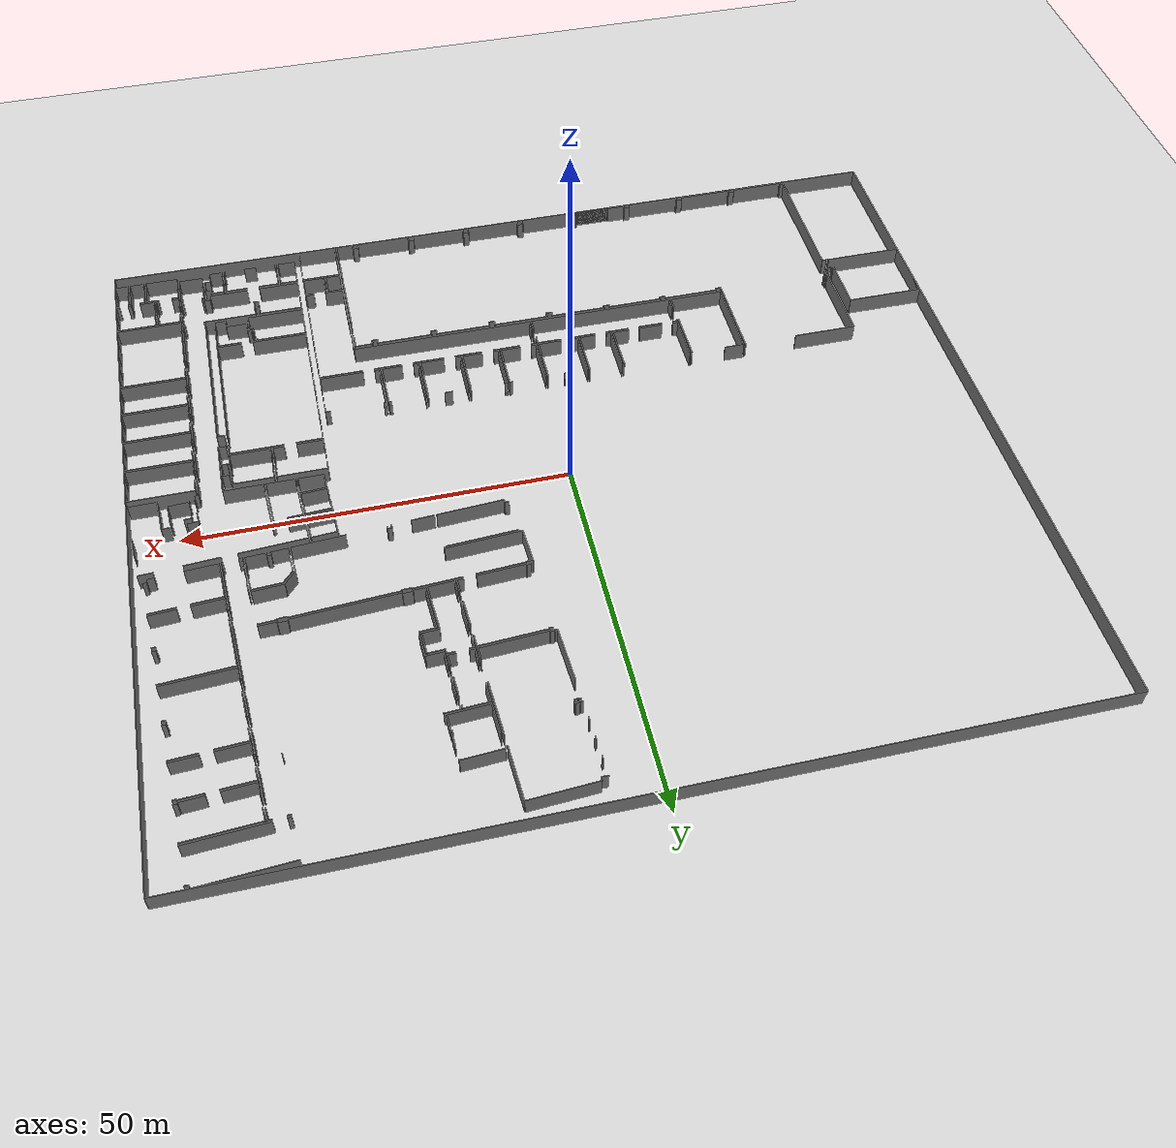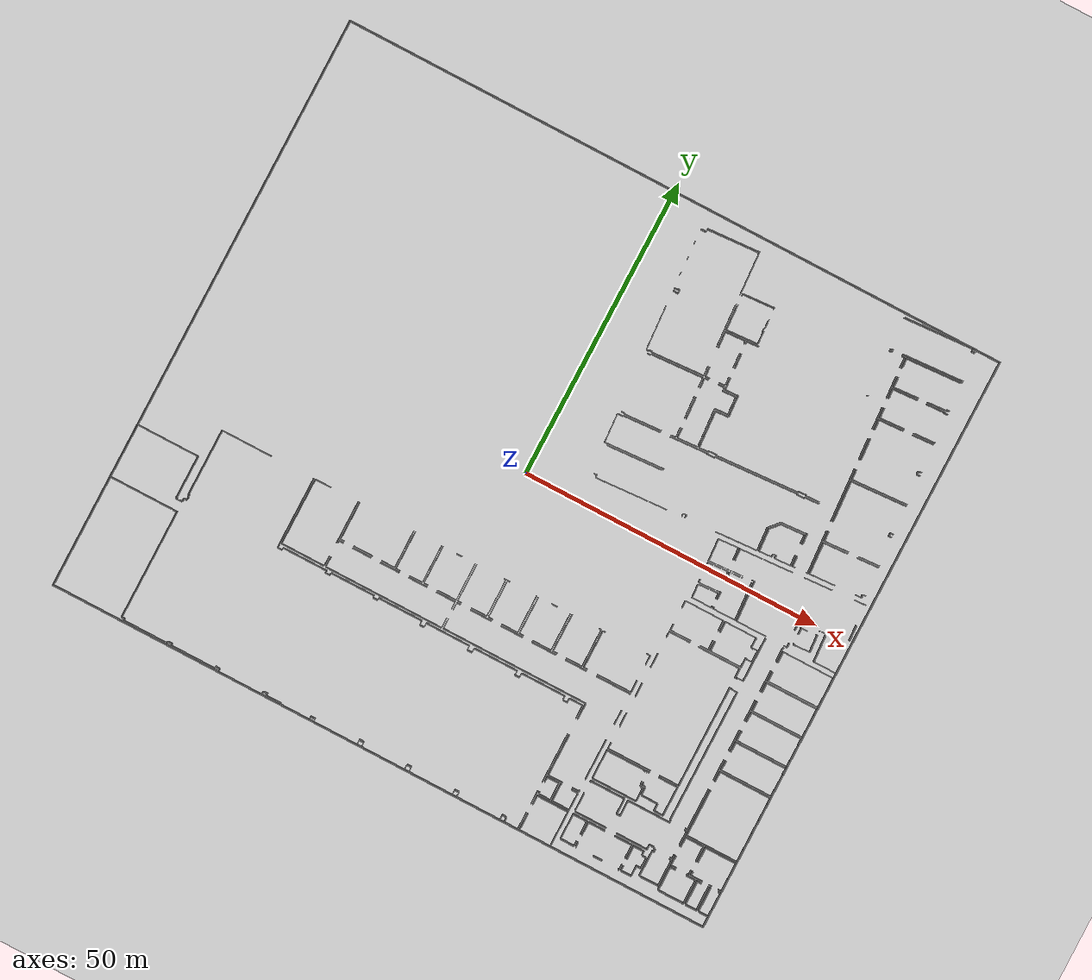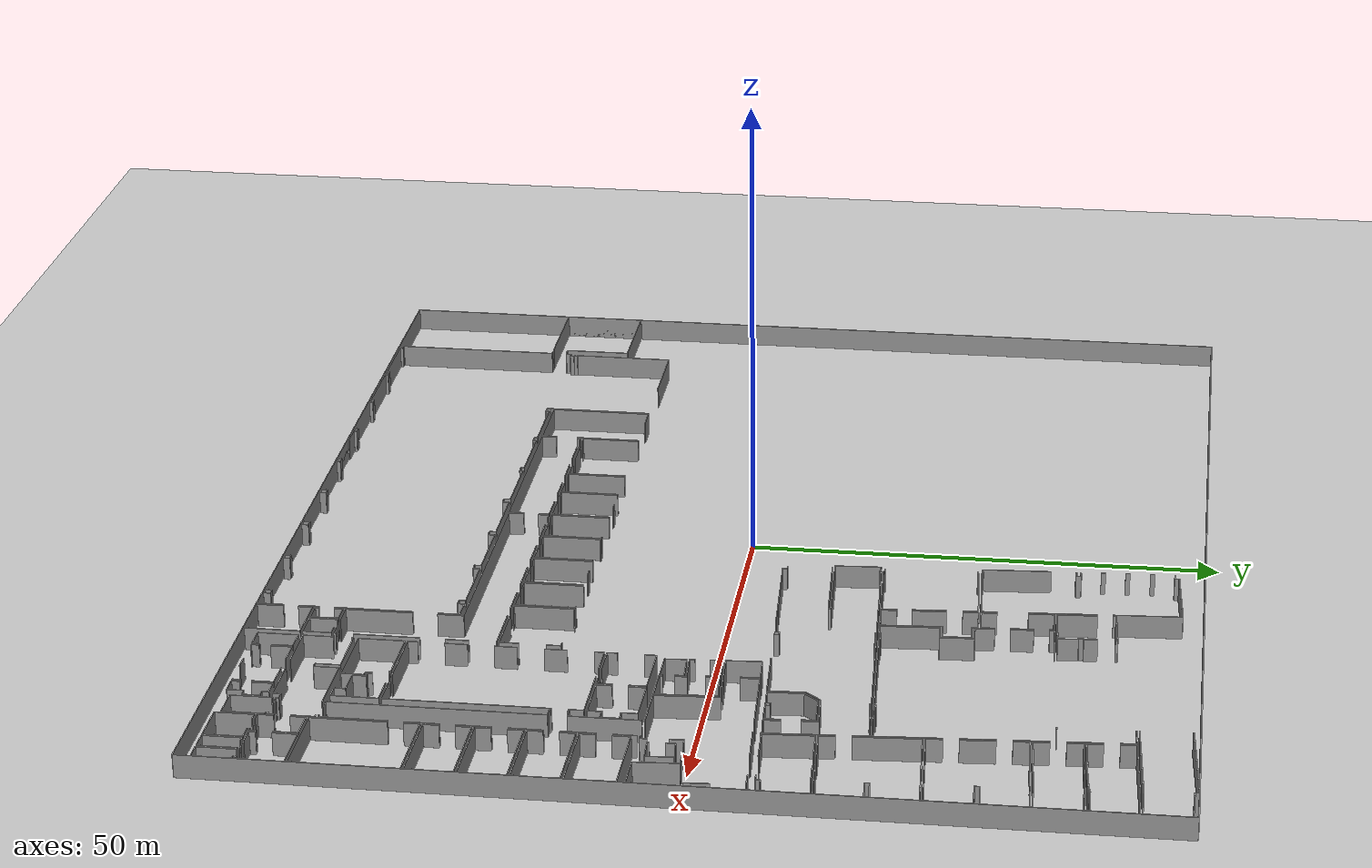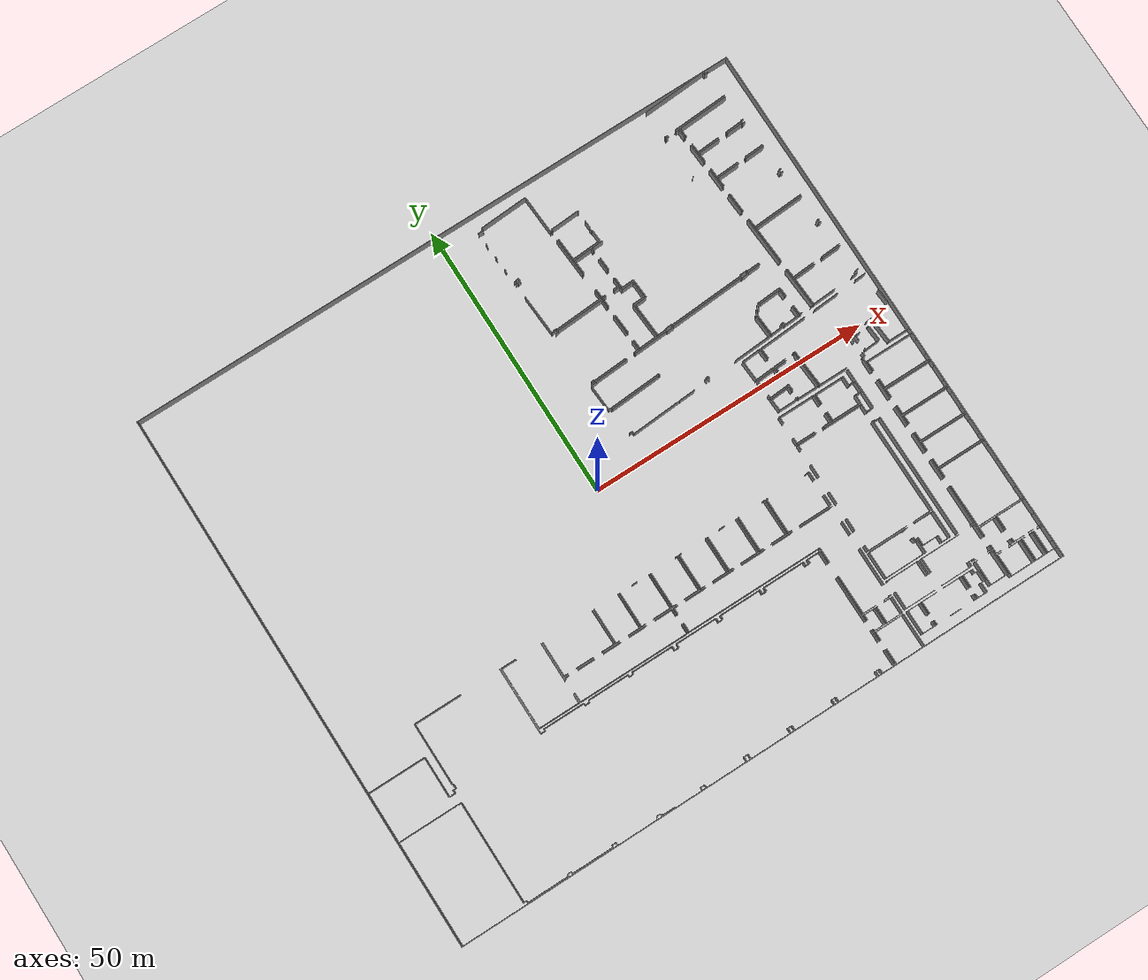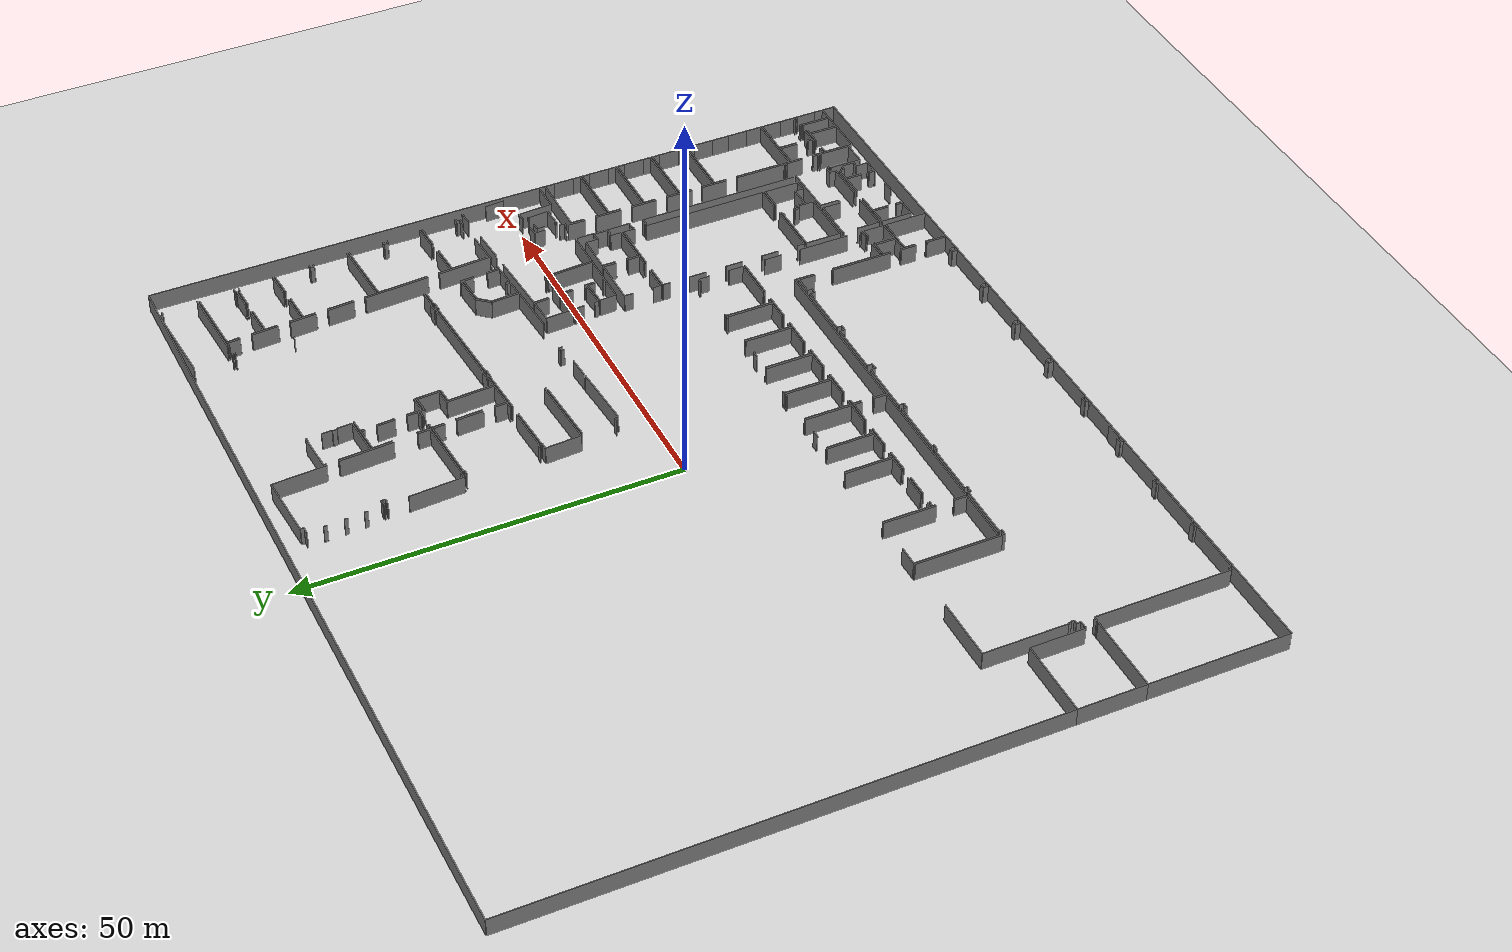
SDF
<sdf version="1.6">
  <world name="default">
    <light name="sun" type="directional">
      <cast_shadows>1</cast_shadows>
      <pose frame="">0 0 10 0 -0 0</pose>
      <diffuse>0.8 0.8 0.8 1</diffuse>
      <specular>0.1 0.1 0.1 1</specular>
      <attenuation>
        <range>1000</range>
        <constant>0.9</constant>
        <linear>0.01</linear>
        <quadratic>0.001</quadratic>
      </attenuation>
      <direction>-0.5 0.5 -1</direction>
    </light>
    <model name="ground_plane">
      <static>1</static>
      <link name="link">
        <collision name="collision">
          <geometry>
            <plane>
              <normal>0 0 1</normal>
              <size>100 100</size>
            </plane>
          </geometry>
          <surface>
            <friction>
              <ode>
                <mu>100</mu>
                <mu2>50</mu2>
              </ode>
              <torsional>
                <ode />
              </torsional>
            </friction>
            <contact>
              <ode />
            </contact>
            <bounce />
          </surface>
          <max_contacts>10</max_contacts>
        </collision>
        <visual name="visual">
          <cast_shadows>0</cast_shadows>
          <geometry>
            <plane>
              <normal>0 0 1</normal>
              <size>100 100</size>
            </plane>
          </geometry>
          <material>
            <script>
              <uri>file://media/materials/scripts/gazebo.material</uri>
              <name>Gazebo/Grey</name>
            </script>
          </material>
        </visual>
        <self_collide>0</self_collide>
        <kinematic>0</kinematic>
        <gravity>1</gravity>
      </link>
    </model>
    <gravity>0 0 -9.8</gravity>
    <magnetic_field>6e-06 2.3e-05 -4.2e-05</magnetic_field>
    <atmosphere type="adiabatic" />
    <physics default="0" name="default_physics" type="ode">
      <max_step_size>0.001</max_step_size>
      <real_time_factor>1</real_time_factor>
      <real_time_update_rate>1000</real_time_update_rate>
    </physics>
    <scene>
      <ambient>0.4 0.4 0.4 1</ambient>
      <background>0.7 0.7 0.7 1</background>
      <shadows>1</shadows>
    </scene>
    <spherical_coordinates>
      <surface_model>EARTH_WGS84</surface_model>
      <latitude_deg>0</latitude_deg>
      <longitude_deg>0</longitude_deg>
      <elevation>0</elevation>
      <heading_deg>0</heading_deg>
    </spherical_coordinates>
  <model name="50025631">
		<static>1</static>
		<link name="Wall_0">
			<collision name="Wall_0_Collision">
				<geometry>
					<box>
						<size>8.67211934119 0.1 2.5</size>
					</box>
				</geometry>
				<pose frame="">4.3360596706 0 1.25 0 0 0</pose>
			</collision>
			<visual name="Wall_0_Visual">
				<pose frame="">4.3360596706 0 1.25 0 0 0</pose>
				<geometry>
					<box>
						<size>8.67211934119 0.1 2.5</size>
					</box>
				</geometry>
				<material>
					<script>
						<uri>file://media/materials/scripts/gazebo.material</uri>
						<name>Gazebo/Grey</name>
					</script>
					<ambient>1 1 1 1</ambient>
				</material>
			</visual>
			<pose frame="">72.8480437916 -22.7678776679 0 0 0 -3.08005815963</pose>
		</link>
		<link name="Wall_1">
			<collision name="Wall_1_Collision">
				<geometry>
					<box>
						<size>0.127183202905 0.1 2.5</size>
					</box>
				</geometry>
				<pose frame="">0.0635916014527 0 1.25 0 0 0</pose>
			</collision>
			<visual name="Wall_1_Visual">
				<pose frame="">0.0635916014527 0 1.25 0 0 0</pose>
				<geometry>
					<box>
						<size>0.127183202905 0.1 2.5</size>
					</box>
				</geometry>
				<material>
					<script>
						<uri>file://media/materials/scripts/gazebo.material</uri>
						<name>Gazebo/Grey</name>
					</script>
					<ambient>1 1 1 1</ambient>
				</material>
			</visual>
			<pose frame="">64.1923377341 -23.3011754396 0 0 0 1.68387965702</pose>
		</link>
		<link name="Wall_2">
			<collision name="Wall_2_Collision">
				<geometry>
					<box>
						<size>0.516716505275 0.1 2.5</size>
					</box>
				</geometry>
				<pose frame="">0.258358252637 0 1.25 0 0 0</pose>
			</collision>
			<visual name="Wall_2_Visual">
				<pose frame="">0.258358252637 0 1.25 0 0 0</pose>
				<geometry>
					<box>
						<size>0.516716505275 0.1 2.5</size>
					</box>
				</geometry>
				<material>
					<script>
						<uri>file://media/materials/scripts/gazebo.material</uri>
						<name>Gazebo/Grey</name>
					</script>
					<ambient>1 1 1 1</ambient>
				</material>
			</visual>
			<pose frame="">64.1779860675 -23.1748045697 0 0 0 -3.07714998938</pose>
		</link>
		<link name="Wall_3">
			<collision name="Wall_3_Collision">
				<geometry>
					<box>
						<size>0.0820458110279 0.1 2.5</size>
					</box>
				</geometry>
				<pose frame="">0.041022905514 0 1.25 0 0 0</pose>
			</collision>
			<visual name="Wall_3_Visual">
				<pose frame="">0.041022905514 0 1.25 0 0 0</pose>
				<geometry>
					<box>
						<size>0.0820458110279 0.1 2.5</size>
					</box>
				</geometry>
				<material>
					<script>
						<uri>file://media/materials/scripts/gazebo.material</uri>
						<name>Gazebo/Grey</name>
					</script>
					<ambient>1 1 1 1</ambient>
				</material>
			</visual>
			<pose frame="">63.6623421158 -23.2080801153 0 0 0 -1.57079632679</pose>
		</link>
		<link name="Wall_4">
			<collision name="Wall_4_Collision">
				<geometry>
					<box>
						<size>0.398711349787 0.1 2.5</size>
					</box>
				</geometry>
				<pose frame="">0.199355674893 0 1.25 0 0 0</pose>
			</collision>
			<visual name="Wall_4_Visual">
				<pose frame="">0.199355674893 0 1.25 0 0 0</pose>
				<geometry>
					<box>
						<size>0.398711349787 0.1 2.5</size>
					</box>
				</geometry>
				<material>
					<script>
						<uri>file://media/materials/scripts/gazebo.material</uri>
						<name>Gazebo/Grey</name>
					</script>
					<ambient>1 1 1 1</ambient>
				</material>
			</visual>
			<pose frame="">63.6623421158 -23.2901259263 0 0 0 -3.0781604714</pose>
		</link>
		<link name="Wall_5">
			<collision name="Wall_5_Collision">
				<geometry>
					<box>
						<size>7.24460550657 0.1 2.5</size>
					</box>
				</geometry>
				<pose frame="">3.62230275328 0 1.25 0 0 0</pose>
			</collision>
			<visual name="Wall_5_Visual">
				<pose frame="">3.62230275328 0 1.25 0 0 0</pose>
				<geometry>
					<box>
						<size>7.24460550657 0.1 2.5</size>
					</box>
				</geometry>
				<material>
					<script>
						<uri>file://media/materials/scripts/gazebo.material</uri>
						<name>Gazebo/Grey</name>
					</script>
					<ambient>1 1 1 1</ambient>
				</material>
			</visual>
			<pose frame="">63.2644326329 -23.3154001003 0 0 0 1.63133311903</pose>
		</link>
		<link name="Wall_6">
			<collision name="Wall_6_Collision">
				<geometry>
					<box>
						<size>0.37828840929 0.1 2.5</size>
					</box>
				</geometry>
				<pose frame="">0.189144204645 0 1.25 0 0 0</pose>
			</collision>
			<visual name="Wall_6_Visual">
				<pose frame="">0.189144204645 0 1.25 0 0 0</pose>
				<geometry>
					<box>
						<size>0.37828840929 0.1 2.5</size>
					</box>
				</geometry>
				<material>
					<script>
						<uri>file://media/materials/scripts/gazebo.material</uri>
						<name>Gazebo/Grey</name>
					</script>
					<ambient>1 1 1 1</ambient>
				</material>
			</visual>
			<pose frame="">62.673347177 -13.4436125558 0 0 0 0.0756131432368</pose>
		</link>
		<link name="Wall_7">
			<collision name="Wall_7_Collision">
				<geometry>
					<box>
						<size>0.0769225990106 0.1 2.5</size>
					</box>
				</geometry>
				<pose frame="">0.0384612995053 0 1.25 0 0 0</pose>
			</collision>
			<visual name="Wall_7_Visual">
				<pose frame="">0.0384612995053 0 1.25 0 0 0</pose>
				<geometry>
					<box>
						<size>0.0769225990106 0.1 2.5</size>
					</box>
				</geometry>
				<material>
					<script>
						<uri>file://media/materials/scripts/gazebo.material</uri>
						<name>Gazebo/Grey</name>
					</script>
					<ambient>1 1 1 1</ambient>
				</material>
			</visual>
			<pose frame="">63.0505546983 -13.4150362284 0 0 0 -1.44664612438</pose>
		</link>
		<link name="Wall_8">
			<collision name="Wall_8_Collision">
				<geometry>
					<box>
						<size>0.512035400165 0.1 2.5</size>
					</box>
				</geometry>
				<pose frame="">0.256017700082 0 1.25 0 0 0</pose>
			</collision>
			<visual name="Wall_8_Visual">
				<pose frame="">0.256017700082 0 1.25 0 0 0</pose>
				<geometry>
					<box>
						<size>0.512035400165 0.1 2.5</size>
					</box>
				</geometry>
				<material>
					<script>
						<uri>file://media/materials/scripts/gazebo.material</uri>
						<name>Gazebo/Grey</name>
					</script>
					<ambient>1 1 1 1</ambient>
				</material>
			</visual>
			<pose frame="">63.0600801407 -13.491366774 0 0 0 0.065281205669</pose>
		</link>
		<link name="Wall_9">
			<collision name="Wall_9_Collision">
				<geometry>
					<box>
						<size>0.539861803143 0.1 2.5</size>
					</box>
				</geometry>
				<pose frame="">0.269930901571 0 1.25 0 0 0</pose>
			</collision>
			<visual name="Wall_9_Visual">
				<pose frame="">0.269930901571 0 1.25 0 0 0</pose>
				<geometry>
					<box>
						<size>0.539861803143 0.1 2.5</size>
					</box>
				</geometry>
				<material>
					<script>
						<uri>file://media/materials/scripts/gazebo.material</uri>
						<name>Gazebo/Grey</name>
					</script>
					<ambient>1 1 1 1</ambient>
				</material>
			</visual>
			<pose frame="">63.5710248741 -13.4579642224 0 0 0 1.60632750631</pose>
		</link>
		<link name="Wall_10">
			<collision name="Wall_10_Collision">
				<geometry>
					<box>
						<size>0.550061626672 0.1 2.5</size>
					</box>
				</geometry>
				<pose frame="">0.275030813336 0 1.25 0 0 0</pose>
			</collision>
			<visual name="Wall_10_Visual">
				<pose frame="">0.275030813336 0 1.25 0 0 0</pose>
				<geometry>
					<box>
						<size>0.550061626672 0.1 2.5</size>
					</box>
				</geometry>
				<material>
					<script>
						<uri>file://media/materials/scripts/gazebo.material</uri>
						<name>Gazebo/Grey</name>
					</script>
					<ambient>1 1 1 1</ambient>
				</material>
			</visual>
			<pose frame="">63.5518469833 -12.9184431617 0 0 0 -3.08083016274</pose>
		</link>
		<link name="Wall_11">
			<collision name="Wall_11_Collision">
				<geometry>
					<box>
						<size>0.0717937287443 0.1 2.5</size>
					</box>
				</geometry>
				<pose frame="">0.0358968643722 0 1.25 0 0 0</pose>
			</collision>
			<visual name="Wall_11_Visual">
				<pose frame="">0.0358968643722 0 1.25 0 0 0</pose>
				<geometry>
					<box>
						<size>0.0717937287443 0.1 2.5</size>
					</box>
				</geometry>
				<material>
					<script>
						<uri>file://media/materials/scripts/gazebo.material</uri>
						<name>Gazebo/Grey</name>
					</script>
					<ambient>1 1 1 1</ambient>
				</material>
			</visual>
			<pose frame="">63.0028004801 -12.9518457132 0 0 0 -1.50352211465</pose>
		</link>
		<link name="Wall_12">
			<collision name="Wall_12_Collision">
				<geometry>
					<box>
						<size>0.382514802553 0.1 2.5</size>
					</box>
				</geometry>
				<pose frame="">0.191257401276 0 1.25 0 0 0</pose>
			</collision>
			<visual name="Wall_12_Visual">
				<pose frame="">0.191257401276 0 1.25 0 0 0</pose>
				<geometry>
					<box>
						<size>0.382514802553 0.1 2.5</size>
					</box>
				</geometry>
				<material>
					<script>
						<uri>file://media/materials/scripts/gazebo.material</uri>
						<name>Gazebo/Grey</name>
					</script>
					<ambient>1 1 1 1</ambient>
				</material>
			</visual>
			<pose frame="">63.0076267043 -13.0234770405 0 0 0 -3.09143528919</pose>
		</link>
		<link name="Wall_13">
			<collision name="Wall_13_Collision">
				<geometry>
					<box>
						<size>0.470128287242 0.1 2.5</size>
					</box>
				</geometry>
				<pose frame="">0.235064143621 0 1.25 0 0 0</pose>
			</collision>
			<visual name="Wall_13_Visual">
				<pose frame="">0.235064143621 0 1.25 0 0 0</pose>
				<geometry>
					<box>
						<size>0.470128287242 0.1 2.5</size>
					</box>
				</geometry>
				<material>
					<script>
						<uri>file://media/materials/scripts/gazebo.material</uri>
						<name>Gazebo/Grey</name>
					</script>
					<ambient>1 1 1 1</ambient>
				</material>
			</visual>
			<pose frame="">62.5058263956 -10.8769503343 0 0 0 1.62593518451</pose>
		</link>
		<link name="Wall_14">
			<collision name="Wall_14_Collision">
				<geometry>
					<box>
						<size>0.473586589721 0.1 2.5</size>
					</box>
				</geometry>
				<pose frame="">0.236793294861 0 1.25 0 0 0</pose>
			</collision>
			<visual name="Wall_14_Visual">
				<pose frame="">0.236793294861 0 1.25 0 0 0</pose>
				<geometry>
					<box>
						<size>0.473586589721 0.1 2.5</size>
					</box>
				</geometry>
				<material>
					<script>
						<uri>file://media/materials/scripts/gazebo.material</uri>
						<name>Gazebo/Grey</name>
					</script>
					<ambient>1 1 1 1</ambient>
				</material>
			</visual>
			<pose frame="">62.3630717647 -8.33480025147 0 0 0 1.63144191104</pose>
		</link>
		<link name="Wall_15">
			<collision name="Wall_15_Collision">
				<geometry>
					<box>
						<size>0.472334239871 0.1 2.5</size>
					</box>
				</geometry>
				<pose frame="">0.236167119936 0 1.25 0 0 0</pose>
			</collision>
			<visual name="Wall_15_Visual">
				<pose frame="">0.236167119936 0 1.25 0 0 0</pose>
				<geometry>
					<box>
						<size>0.472334239871 0.1 2.5</size>
					</box>
				</geometry>
				<material>
					<script>
						<uri>file://media/materials/scripts/gazebo.material</uri>
						<name>Gazebo/Grey</name>
					</script>
					<ambient>1 1 1 1</ambient>
				</material>
			</visual>
			<pose frame="">62.2027903196 -5.73791062595 0 0 0 1.59392291835</pose>
		</link>
		<link name="Wall_16">
			<collision name="Wall_16_Collision">
				<geometry>
					<box>
						<size>0.90053961757 0.1 2.5</size>
					</box>
				</geometry>
				<pose frame="">0.450269808785 0 1.25 0 0 0</pose>
			</collision>
			<visual name="Wall_16_Visual">
				<pose frame="">0.450269808785 0 1.25 0 0 0</pose>
				<geometry>
					<box>
						<size>0.90053961757 0.1 2.5</size>
					</box>
				</geometry>
				<material>
					<script>
						<uri>file://media/materials/scripts/gazebo.material</uri>
						<name>Gazebo/Grey</name>
					</script>
					<ambient>1 1 1 1</ambient>
				</material>
			</visual>
			<pose frame="">62.0491131813 -3.17366151658 0 0 0 -0.0122701881225</pose>
		</link>
		<link name="Wall_17">
			<collision name="Wall_17_Collision">
				<geometry>
					<box>
						<size>0.472239513679 0.1 2.5</size>
					</box>
				</geometry>
				<pose frame="">0.236119756839 0 1.25 0 0 0</pose>
			</collision>
			<visual name="Wall_17_Visual">
				<pose frame="">0.236119756839 0 1.25 0 0 0</pose>
				<geometry>
					<box>
						<size>0.472239513679 0.1 2.5</size>
					</box>
				</geometry>
				<material>
					<script>
						<uri>file://media/materials/scripts/gazebo.material</uri>
						<name>Gazebo/Grey</name>
					</script>
					<ambient>1 1 1 1</ambient>
				</material>
			</visual>
			<pose frame="">62.9495850082 -3.18471102983 0 0 0 1.55923148469</pose>
		</link>
		<link name="Wall_18">
			<collision name="Wall_18_Collision">
				<geometry>
					<box>
						<size>8.68540960603 0.1 2.5</size>
					</box>
				</geometry>
				<pose frame="">4.34270480302 0 1.25 0 0 0</pose>
			</collision>
			<visual name="Wall_18_Visual">
				<pose frame="">4.34270480302 0 1.25 0 0 0</pose>
				<geometry>
					<box>
						<size>8.68540960603 0.1 2.5</size>
					</box>
				</geometry>
				<material>
					<script>
						<uri>file://media/materials/scripts/gazebo.material</uri>
						<name>Gazebo/Grey</name>
					</script>
					<ambient>1 1 1 1</ambient>
				</material>
			</visual>
			<pose frame="">62.9550462619 -2.71250309577 0 0 0 0.0594654412264</pose>
		</link>
		<link name="Wall_19">
			<collision name="Wall_19_Collision">
				<geometry>
					<box>
						<size>7.09912275151 0.1 2.5</size>
					</box>
				</geometry>
				<pose frame="">3.54956137576 0 1.25 0 0 0</pose>
			</collision>
			<visual name="Wall_19_Visual">
				<pose frame="">3.54956137576 0 1.25 0 0 0</pose>
				<geometry>
					<box>
						<size>7.09912275151 0.1 2.5</size>
					</box>
				</geometry>
				<material>
					<script>
						<uri>file://media/materials/scripts/gazebo.material</uri>
						<name>Gazebo/Grey</name>
					</script>
					<ambient>1 1 1 1</ambient>
				</material>
			</visual>
			<pose frame="">71.6251039861 -2.19632571933 0 0 0 -1.51285279594</pose>
		</link>
		<link name="Wall_20">
			<collision name="Wall_20_Collision">
				<geometry>
					<box>
						<size>7.0879299601 0.1 2.5</size>
					</box>
				</geometry>
				<pose frame="">3.54396498005 0 1.25 0 0 0</pose>
			</collision>
			<visual name="Wall_20_Visual">
				<pose frame="">3.54396498005 0 1.25 0 0 0</pose>
				<geometry>
					<box>
						<size>7.0879299601 0.1 2.5</size>
					</box>
				</geometry>
				<material>
					<script>
						<uri>file://media/materials/scripts/gazebo.material</uri>
						<name>Gazebo/Grey</name>
					</script>
					<ambient>1 1 1 1</ambient>
				</material>
			</visual>
			<pose frame="">72.1271583065 -10.8939691249 0 0 0 -1.50746544688</pose>
		</link>
		<link name="Wall_21">
			<collision name="Wall_21_Collision">
				<geometry>
					<box>
						<size>1.62895105357 0.1 2.5</size>
					</box>
				</geometry>
				<pose frame="">0.814475526787 0 1.25 0 0 0</pose>
			</collision>
			<visual name="Wall_21_Visual">
				<pose frame="">0.814475526787 0 1.25 0 0 0</pose>
				<geometry>
					<box>
						<size>1.62895105357 0.1 2.5</size>
					</box>
				</geometry>
				<material>
					<script>
						<uri>file://media/materials/scripts/gazebo.material</uri>
						<name>Gazebo/Grey</name>
					</script>
					<ambient>1 1 1 1</ambient>
				</material>
			</visual>
			<pose frame="">72.7812386885 -21.1402970668 0 0 0 -1.52977370438</pose>
		</link>
		<link name="Wall_22">
			<collision name="Wall_22_Collision">
				<geometry>
					<box>
						<size>5.25442817169 0.1 2.5</size>
					</box>
				</geometry>
				<pose frame="">2.62721408584 0 1.25 0 0 0</pose>
			</collision>
			<visual name="Wall_22_Visual">
				<pose frame="">2.62721408584 0 1.25 0 0 0</pose>
				<geometry>
					<box>
						<size>5.25442817169 0.1 2.5</size>
					</box>
				</geometry>
				<material>
					<script>
						<uri>file://media/materials/scripts/gazebo.material</uri>
						<name>Gazebo/Grey</name>
					</script>
					<ambient>1 1 1 1</ambient>
				</material>
			</visual>
			<pose frame="">77.9144361256 -14.6887783938 0 0 0 -3.07957792296</pose>
		</link>
		<link name="Wall_23">
			<collision name="Wall_23_Collision">
				<geometry>
					<box>
						<size>4.14863764413 0.1 2.5</size>
					</box>
				</geometry>
				<pose frame="">2.07431882206 0 1.25 0 0 0</pose>
			</collision>
			<visual name="Wall_23_Visual">
				<pose frame="">2.07431882206 0 1.25 0 0 0</pose>
				<geometry>
					<box>
						<size>4.14863764413 0.1 2.5</size>
					</box>
				</geometry>
				<material>
					<script>
						<uri>file://media/materials/scripts/gazebo.material</uri>
						<name>Gazebo/Grey</name>
					</script>
					<ambient>1 1 1 1</ambient>
				</material>
			</visual>
			<pose frame="">72.6701085265 -15.0144215199 0 0 0 1.62718636227</pose>
		</link>
		<link name="Wall_24">
			<collision name="Wall_24_Collision">
				<geometry>
					<box>
						<size>0.319287703387 0.1 2.5</size>
					</box>
				</geometry>
				<pose frame="">0.159643851693 0 1.25 0 0 0</pose>
			</collision>
			<visual name="Wall_24_Visual">
				<pose frame="">0.159643851693 0 1.25 0 0 0</pose>
				<geometry>
					<box>
						<size>0.319287703387 0.1 2.5</size>
					</box>
				</geometry>
				<material>
					<script>
						<uri>file://media/materials/scripts/gazebo.material</uri>
						<name>Gazebo/Grey</name>
					</script>
					<ambient>1 1 1 1</ambient>
				</material>
			</visual>
			<pose frame="">72.3279546335 -9.29598089831 0 0 0 1.6396665001</pose>
		</link>
		<link name="Wall_25">
			<collision name="Wall_25_Collision">
				<geometry>
					<box>
						<size>5.26493296111 0.1 2.5</size>
					</box>
				</geometry>
				<pose frame="">2.63246648056 0 1.25 0 0 0</pose>
			</collision>
			<visual name="Wall_25_Visual">
				<pose frame="">2.63246648056 0 1.25 0 0 0</pose>
				<geometry>
					<box>
						<size>5.26493296111 0.1 2.5</size>
					</box>
				</geometry>
				<material>
					<script>
						<uri>file://media/materials/scripts/gazebo.material</uri>
						<name>Gazebo/Grey</name>
					</script>
					<ambient>1 1 1 1</ambient>
				</material>
			</visual>
			<pose frame="">72.3059826129 -8.97745010256 0 0 0 0.0626159323086</pose>
		</link>
		<link name="Wall_26">
			<collision name="Wall_26_Collision">
				<geometry>
					<box>
						<size>0.21997436446 0.1 2.5</size>
					</box>
				</geometry>
				<pose frame="">0.10998718223 0 1.25 0 0 0</pose>
			</collision>
			<visual name="Wall_26_Visual">
				<pose frame="">0.10998718223 0 1.25 0 0 0</pose>
				<geometry>
					<box>
						<size>0.21997436446 0.1 2.5</size>
					</box>
				</geometry>
				<material>
					<script>
						<uri>file://media/materials/scripts/gazebo.material</uri>
						<name>Gazebo/Grey</name>
					</script>
					<ambient>1 1 1 1</ambient>
				</material>
			</visual>
			<pose frame="">77.5605976898 -8.64799679945 0 0 0 -1.57195106069</pose>
		</link>
		<link name="Wall_27">
			<collision name="Wall_27_Collision">
				<geometry>
					<box>
						<size>1.40551481856 0.1 2.5</size>
					</box>
				</geometry>
				<pose frame="">0.702757409282 0 1.25 0 0 0</pose>
			</collision>
			<visual name="Wall_27_Visual">
				<pose frame="">0.702757409282 0 1.25 0 0 0</pose>
				<geometry>
					<box>
						<size>1.40551481856 0.1 2.5</size>
					</box>
				</geometry>
				<material>
					<script>
						<uri>file://media/materials/scripts/gazebo.material</uri>
						<name>Gazebo/Grey</name>
					</script>
					<ambient>1 1 1 1</ambient>
				</material>
			</visual>
			<pose frame="">77.6614403739 -10.6485937272 0 0 0 -1.5084057001</pose>
		</link>
		<link name="Wall_28">
			<collision name="Wall_28_Collision">
				<geometry>
					<box>
						<size>0.115575368476 0.1 2.5</size>
					</box>
				</geometry>
				<pose frame="">0.0577876842379 0 1.25 0 0 0</pose>
			</collision>
			<visual name="Wall_28_Visual">
				<pose frame="">0.0577876842379 0 1.25 0 0 0</pose>
				<geometry>
					<box>
						<size>0.115575368476 0.1 2.5</size>
					</box>
				</geometry>
				<material>
					<script>
						<uri>file://media/materials/scripts/gazebo.material</uri>
						<name>Gazebo/Grey</name>
					</script>
					<ambient>1 1 1 1</ambient>
				</material>
			</visual>
			<pose frame="">77.7490744445 -12.0513738863 0 0 0 3.14159265359</pose>
		</link>
		<link name="Wall_29">
			<collision name="Wall_29_Collision">
				<geometry>
					<box>
						<size>0.560009279978 0.1 2.5</size>
					</box>
				</geometry>
				<pose frame="">0.280004639989 0 1.25 0 0 0</pose>
			</collision>
			<visual name="Wall_29_Visual">
				<pose frame="">0.280004639989 0 1.25 0 0 0</pose>
				<geometry>
					<box>
						<size>0.560009279978 0.1 2.5</size>
					</box>
				</geometry>
				<material>
					<script>
						<uri>file://media/materials/scripts/gazebo.material</uri>
						<name>Gazebo/Grey</name>
					</script>
					<ambient>1 1 1 1</ambient>
				</material>
			</visual>
			<pose frame="">77.633499076 -12.0513738863 0 0 0 -1.53200508303</pose>
		</link>
		<link name="Wall_30">
			<collision name="Wall_30_Collision">
				<geometry>
					<box>
						<size>0.130121557384 0.1 2.5</size>
					</box>
				</geometry>
				<pose frame="">0.0650607786918 0 1.25 0 0 0</pose>
			</collision>
			<visual name="Wall_30_Visual">
				<pose frame="">0.0650607786918 0 1.25 0 0 0</pose>
				<geometry>
					<box>
						<size>0.130121557384 0.1 2.5</size>
					</box>
				</geometry>
				<material>
					<script>
						<uri>file://media/materials/scripts/gazebo.material</uri>
						<name>Gazebo/Grey</name>
					</script>
					<ambient>1 1 1 1</ambient>
				</material>
			</visual>
			<pose frame="">77.6552170848 -12.6109618792 0 0 0 0.0546863776495</pose>
		</link>
		<link name="Wall_31">
			<collision name="Wall_31_Collision">
				<geometry>
					<box>
						<size>2.08893386951 0.1 2.5</size>
					</box>
				</geometry>
				<pose frame="">1.04446693476 0 1.25 0 0 0</pose>
			</collision>
			<visual name="Wall_31_Visual">
				<pose frame="">1.04446693476 0 1.25 0 0 0</pose>
				<geometry>
					<box>
						<size>2.08893386951 0.1 2.5</size>
					</box>
				</geometry>
				<material>
					<script>
						<uri>file://media/materials/scripts/gazebo.material</uri>
						<name>Gazebo/Grey</name>
					</script>
					<ambient>1 1 1 1</ambient>
				</material>
			</visual>
			<pose frame="">77.7851441199 -12.6038495488 0 0 0 -1.5088629647</pose>
		</link>
		<link name="Wall_32">
			<collision name="Wall_32_Collision">
				<geometry>
					<box>
						<size>1.03434341353 0.1 2.5</size>
					</box>
				</geometry>
				<pose frame="">0.517171706767 0 1.25 0 0 0</pose>
			</collision>
			<visual name="Wall_32_Visual">
				<pose frame="">0.517171706767 0 1.25 0 0 0</pose>
				<geometry>
					<box>
						<size>1.03434341353 0.1 2.5</size>
					</box>
				</geometry>
				<material>
					<script>
						<uri>file://media/materials/scripts/gazebo.material</uri>
						<name>Gazebo/Grey</name>
					</script>
					<ambient>1 1 1 1</ambient>
				</material>
			</visual>
			<pose frame="">76.4459939164 -22.5830840843 0 0 0 -3.09442422389</pose>
		</link>
		<link name="Wall_33">
			<collision name="Wall_33_Collision">
				<geometry>
					<box>
						<size>0.673342806366 0.1 2.5</size>
					</box>
				</geometry>
				<pose frame="">0.336671403183 0 1.25 0 0 0</pose>
			</collision>
			<visual name="Wall_33_Visual">
				<pose frame="">0.336671403183 0 1.25 0 0 0</pose>
				<geometry>
					<box>
						<size>0.673342806366 0.1 2.5</size>
					</box>
				</geometry>
				<material>
					<script>
						<uri>file://media/materials/scripts/gazebo.material</uri>
						<name>Gazebo/Grey</name>
					</script>
					<ambient>1 1 1 1</ambient>
				</material>
			</visual>
			<pose frame="">73.833863583 -22.7213935087 0 0 0 -3.08440964425</pose>
		</link>
		<link name="Wall_34">
			<collision name="Wall_34_Collision">
				<geometry>
					<box>
						<size>1.63607680968 0.1 2.5</size>
					</box>
				</geometry>
				<pose frame="">0.81803840484 0 1.25 0 0 0</pose>
			</collision>
			<visual name="Wall_34_Visual">
				<pose frame="">0.81803840484 0 1.25 0 0 0</pose>
				<geometry>
					<box>
						<size>1.63607680968 0.1 2.5</size>
					</box>
				</geometry>
				<material>
					<script>
						<uri>file://media/materials/scripts/gazebo.material</uri>
						<name>Gazebo/Grey</name>
					</script>
					<ambient>1 1 1 1</ambient>
				</material>
			</visual>
			<pose frame="">73.1616213573 -22.7598762963 0 0 0 1.63542807964</pose>
		</link>
		<link name="Wall_35">
			<collision name="Wall_35_Collision">
				<geometry>
					<box>
						<size>2.6347653498 0.1 2.5</size>
					</box>
				</geometry>
				<pose frame="">1.3173826749 0 1.25 0 0 0</pose>
			</collision>
			<visual name="Wall_35_Visual">
				<pose frame="">1.3173826749 0 1.25 0 0 0</pose>
				<geometry>
					<box>
						<size>2.6347653498 0.1 2.5</size>
					</box>
				</geometry>
				<material>
					<script>
						<uri>file://media/materials/scripts/gazebo.material</uri>
						<name>Gazebo/Grey</name>
					</script>
					<ambient>1 1 1 1</ambient>
				</material>
			</visual>
			<pose frame="">72.8607443816 -17.9190464397 0 0 0 1.63683542233</pose>
		</link>
		<link name="Wall_36">
			<collision name="Wall_36_Collision">
				<geometry>
					<box>
						<size>3.32965445629 0.1 2.5</size>
					</box>
				</geometry>
				<pose frame="">1.66482722815 0 1.25 0 0 0</pose>
			</collision>
			<visual name="Wall_36_Visual">
				<pose frame="">1.66482722815 0 1.25 0 0 0</pose>
				<geometry>
					<box>
						<size>3.32965445629 0.1 2.5</size>
					</box>
				</geometry>
				<material>
					<script>
						<uri>file://media/materials/scripts/gazebo.material</uri>
						<name>Gazebo/Grey</name>
					</script>
					<ambient>1 1 1 1</ambient>
				</material>
			</visual>
			<pose frame="">72.6868733053 -15.2900243216 0 0 0 0.0602274277199</pose>
		</link>
		<link name="Wall_37">
			<collision name="Wall_37_Collision">
				<geometry>
					<box>
						<size>0.527117831154 0.1 2.5</size>
					</box>
				</geometry>
				<pose frame="">0.263558915577 0 1.25 0 0 0</pose>
			</collision>
			<visual name="Wall_37_Visual">
				<pose frame="">0.263558915577 0 1.25 0 0 0</pose>
				<geometry>
					<box>
						<size>0.527117831154 0.1 2.5</size>
					</box>
				</geometry>
				<material>
					<script>
						<uri>file://media/materials/scripts/gazebo.material</uri>
						<name>Gazebo/Grey</name>
					</script>
					<ambient>1 1 1 1</ambient>
				</material>
			</visual>
			<pose frame="">76.0104906873 -15.0896090123 0 0 0 -1.50738555801</pose>
		</link>
		<link name="Wall_38">
			<collision name="Wall_38_Collision">
				<geometry>
					<box>
						<size>2.376935261 0.1 2.5</size>
					</box>
				</geometry>
				<pose frame="">1.1884676305 0 1.25 0 0 0</pose>
			</collision>
			<visual name="Wall_38_Visual">
				<pose frame="">1.1884676305 0 1.25 0 0 0</pose>
				<geometry>
					<box>
						<size>2.376935261 0.1 2.5</size>
					</box>
				</geometry>
				<material>
					<script>
						<uri>file://media/materials/scripts/gazebo.material</uri>
						<name>Gazebo/Grey</name>
					</script>
					<ambient>1 1 1 1</ambient>
				</material>
			</visual>
			<pose frame="">76.1386396398 -17.1802531228 0 0 0 -1.50609771833</pose>
		</link>
		<link name="Wall_39">
			<collision name="Wall_39_Collision">
				<geometry>
					<box>
						<size>1.44071305552 0.1 2.5</size>
					</box>
				</geometry>
				<pose frame="">0.720356527759 0 1.25 0 0 0</pose>
			</collision>
			<visual name="Wall_39_Visual">
				<pose frame="">0.720356527759 0 1.25 0 0 0</pose>
				<geometry>
					<box>
						<size>1.44071305552 0.1 2.5</size>
					</box>
				</geometry>
				<material>
					<script>
						<uri>file://media/materials/scripts/gazebo.material</uri>
						<name>Gazebo/Grey</name>
					</script>
					<ambient>1 1 1 1</ambient>
				</material>
			</visual>
			<pose frame="">76.3779187543 -21.1439802379 0 0 0 -1.52352770606</pose>
		</link>
		<link name="Wall_40">
			<collision name="Wall_40_Collision">
				<geometry>
					<box>
						<size>3.37497856881 0.1 2.5</size>
					</box>
				</geometry>
				<pose frame="">1.6874892844 0 1.25 0 0 0</pose>
			</collision>
			<visual name="Wall_40_Visual">
				<pose frame="">1.6874892844 0 1.25 0 0 0</pose>
				<geometry>
					<box>
						<size>3.37497856881 0.1 2.5</size>
					</box>
				</geometry>
				<material>
					<script>
						<uri>file://media/materials/scripts/gazebo.material</uri>
						<name>Gazebo/Grey</name>
					</script>
					<ambient>1 1 1 1</ambient>
				</material>
			</visual>
			<pose frame="">77.119633207 -32.8098531177 0 0 0 -3.07938510921</pose>
		</link>
		<link name="Wall_41">
			<collision name="Wall_41_Collision">
				<geometry>
					<box>
						<size>1.61418796791 0.1 2.5</size>
					</box>
				</geometry>
				<pose frame="">0.807093983957 0 1.25 0 0 0</pose>
			</collision>
			<visual name="Wall_41_Visual">
				<pose frame="">0.807093983957 0 1.25 0 0 0</pose>
				<geometry>
					<box>
						<size>1.61418796791 0.1 2.5</size>
					</box>
				</geometry>
				<material>
					<script>
						<uri>file://media/materials/scripts/gazebo.material</uri>
						<name>Gazebo/Grey</name>
					</script>
					<ambient>1 1 1 1</ambient>
				</material>
			</visual>
			<pose frame="">73.7511827424 -33.0196668635 0 0 0 1.61865263059</pose>
		</link>
		<link name="Wall_42">
			<collision name="Wall_42_Collision">
				<geometry>
					<box>
						<size>3.55531632255 0.1 2.5</size>
					</box>
				</geometry>
				<pose frame="">1.77765816127 0 1.25 0 0 0</pose>
			</collision>
			<visual name="Wall_42_Visual">
				<pose frame="">1.77765816127 0 1.25 0 0 0</pose>
				<geometry>
					<box>
						<size>3.55531632255 0.1 2.5</size>
					</box>
				</geometry>
				<material>
					<script>
						<uri>file://media/materials/scripts/gazebo.material</uri>
						<name>Gazebo/Grey</name>
					</script>
					<ambient>1 1 1 1</ambient>
				</material>
			</visual>
			<pose frame="">73.5719774184 -29.8205152629 0 0 0 1.62955844266</pose>
		</link>
		<link name="Wall_43">
			<collision name="Wall_43_Collision">
				<geometry>
					<box>
						<size>1.63093683571 0.1 2.5</size>
					</box>
				</geometry>
				<pose frame="">0.815468417854 0 1.25 0 0 0</pose>
			</collision>
			<visual name="Wall_43_Visual">
				<pose frame="">0.815468417854 0 1.25 0 0 0</pose>
				<geometry>
					<box>
						<size>1.63093683571 0.1 2.5</size>
					</box>
				</geometry>
				<material>
					<script>
						<uri>file://media/materials/scripts/gazebo.material</uri>
						<name>Gazebo/Grey</name>
					</script>
					<ambient>1 1 1 1</ambient>
				</material>
			</visual>
			<pose frame="">73.2547166816 -24.6512481505 0 0 0 1.627206271</pose>
		</link>
		<link name="Wall_44">
			<collision name="Wall_44_Collision">
				<geometry>
					<box>
						<size>0.669483286007 0.1 2.5</size>
					</box>
				</geometry>
				<pose frame="">0.334741643003 0 1.25 0 0 0</pose>
			</collision>
			<visual name="Wall_44_Visual">
				<pose frame="">0.334741643003 0 1.25 0 0 0</pose>
				<geometry>
					<box>
						<size>0.669483286007 0.1 2.5</size>
					</box>
				</geometry>
				<material>
					<script>
						<uri>file://media/materials/scripts/gazebo.material</uri>
						<name>Gazebo/Grey</name>
					</script>
					<ambient>1 1 1 1</ambient>
				</material>
			</visual>
			<pose frame="">73.1627644104 -23.022905514 0 0 0 0.0624543108539</pose>
		</link>
		<link name="Wall_45">
			<collision name="Wall_45_Collision">
				<geometry>
					<box>
						<size>1.07560645369 0.1 2.5</size>
					</box>
				</geometry>
				<pose frame="">0.537803226847 0 1.25 0 0 0</pose>
			</collision>
			<visual name="Wall_45_Visual">
				<pose frame="">0.537803226847 0 1.25 0 0 0</pose>
				<geometry>
					<box>
						<size>1.07560645369 0.1 2.5</size>
					</box>
				</geometry>
				<material>
					<script>
						<uri>file://media/materials/scripts/gazebo.material</uri>
						<name>Gazebo/Grey</name>
					</script>
					<ambient>1 1 1 1</ambient>
				</material>
			</visual>
			<pose frame="">75.4200402609 -22.8859931544 0 0 0 0.0405119751002</pose>
		</link>
		<link name="Wall_46">
			<collision name="Wall_46_Collision">
				<geometry>
					<box>
						<size>0.639998303441 0.1 2.5</size>
					</box>
				</geometry>
				<pose frame="">0.319999151721 0 1.25 0 0 0</pose>
			</collision>
			<visual name="Wall_46_Visual">
				<pose frame="">0.319999151721 0 1.25 0 0 0</pose>
				<geometry>
					<box>
						<size>0.639998303441 0.1 2.5</size>
					</box>
				</geometry>
				<material>
					<script>
						<uri>file://media/materials/scripts/gazebo.material</uri>
						<name>Gazebo/Grey</name>
					</script>
					<ambient>1 1 1 1</ambient>
				</material>
			</visual>
			<pose frame="">76.4947641818 -22.8424301309 0 0 0 -1.51400990011</pose>
		</link>
		<link name="Wall_47">
			<collision name="Wall_47_Collision">
				<geometry>
					<box>
						<size>2.17614023963 0.1 2.5</size>
					</box>
				</geometry>
				<pose frame="">1.08807011982 0 1.25 0 0 0</pose>
			</collision>
			<visual name="Wall_47_Visual">
				<pose frame="">1.08807011982 0 1.25 0 0 0</pose>
				<geometry>
					<box>
						<size>2.17614023963 0.1 2.5</size>
					</box>
				</geometry>
				<material>
					<script>
						<uri>file://media/materials/scripts/gazebo.material</uri>
						<name>Gazebo/Grey</name>
					</script>
					<ambient>1 1 1 1</ambient>
				</material>
			</visual>
			<pose frame="">76.531087869 -23.4813968109 0 0 0 0.0667583937188</pose>
		</link>
		<link name="Wall_48">
			<collision name="Wall_48_Collision">
				<geometry>
					<box>
						<size>2.96457346183 0.1 2.5</size>
					</box>
				</geometry>
				<pose frame="">1.48228673091 0 1.25 0 0 0</pose>
			</collision>
			<visual name="Wall_48_Visual">
				<pose frame="">1.48228673091 0 1.25 0 0 0</pose>
				<geometry>
					<box>
						<size>2.96457346183 0.1 2.5</size>
					</box>
				</geometry>
				<material>
					<script>
						<uri>file://media/materials/scripts/gazebo.material</uri>
						<name>Gazebo/Grey</name>
					</script>
					<ambient>1 1 1 1</ambient>
				</material>
			</visual>
			<pose frame="">78.7023807256 -23.3362290678 0 0 0 -1.51297132142</pose>
		</link>
		<link name="Wall_49">
			<collision name="Wall_49_Collision">
				<geometry>
					<box>
						<size>2.19473962889 0.1 2.5</size>
					</box>
				</geometry>
				<pose frame="">1.09736981444 0 1.25 0 0 0</pose>
			</collision>
			<visual name="Wall_49_Visual">
				<pose frame="">1.09736981444 0 1.25 0 0 0</pose>
				<geometry>
					<box>
						<size>2.19473962889 0.1 2.5</size>
					</box>
				</geometry>
				<material>
					<script>
						<uri>file://media/materials/scripts/gazebo.material</uri>
						<name>Gazebo/Grey</name>
					</script>
					<ambient>1 1 1 1</ambient>
				</material>
			</visual>
			<pose frame="">78.8737116839 -26.2958475421 0 0 0 -3.08403977445</pose>
		</link>
		<link name="Wall_50">
			<collision name="Wall_50_Collision">
				<geometry>
					<box>
						<size>6.40269416294 0.1 2.5</size>
					</box>
				</geometry>
				<pose frame="">3.20134708147 0 1.25 0 0 0</pose>
			</collision>
			<visual name="Wall_50_Visual">
				<pose frame="">3.20134708147 0 1.25 0 0 0</pose>
				<geometry>
					<box>
						<size>6.40269416294 0.1 2.5</size>
					</box>
				</geometry>
				<material>
					<script>
						<uri>file://media/materials/scripts/gazebo.material</uri>
						<name>Gazebo/Grey</name>
					</script>
					<ambient>1 1 1 1</ambient>
				</material>
			</visual>
			<pose frame="">76.682605907 -26.4220914061 0 0 0 -1.50248643207</pose>
		</link>
		<link name="Wall_51">
			<collision name="Wall_51_Collision">
				<geometry>
					<box>
						<size>0.85330574929 0.1 2.5</size>
					</box>
				</geometry>
				<pose frame="">0.426652874645 0 1.25 0 0 0</pose>
			</collision>
			<visual name="Wall_51_Visual">
				<pose frame="">0.426652874645 0 1.25 0 0 0</pose>
				<geometry>
					<box>
						<size>0.85330574929 0.1 2.5</size>
					</box>
				</geometry>
				<material>
					<script>
						<uri>file://media/materials/scripts/gazebo.material</uri>
						<name>Gazebo/Grey</name>
					</script>
					<ambient>1 1 1 1</ambient>
				</material>
			</visual>
			<pose frame="">73.4856134067 -33.0384637366 0 0 0 -3.06710386338</pose>
		</link>
		<link name="Wall_52">
			<collision name="Wall_52_Collision">
				<geometry>
					<box>
						<size>6.1954785446 0.1 2.5</size>
					</box>
				</geometry>
				<pose frame="">3.0977392723 0 1.25 0 0 0</pose>
			</collision>
			<visual name="Wall_52_Visual">
				<pose frame="">3.0977392723 0 1.25 0 0 0</pose>
				<geometry>
					<box>
						<size>6.1954785446 0.1 2.5</size>
					</box>
				</geometry>
				<material>
					<script>
						<uri>file://media/materials/scripts/gazebo.material</uri>
						<name>Gazebo/Grey</name>
					</script>
					<ambient>1 1 1 1</ambient>
				</material>
			</visual>
			<pose frame="">71.0123005214 -33.1963320696 0 0 0 -3.08288859376</pose>
		</link>
		<link name="Wall_53">
			<collision name="Wall_53_Collision">
				<geometry>
					<box>
						<size>0.142754630953 0.1 2.5</size>
					</box>
				</geometry>
				<pose frame="">0.0713773154763 0 1.25 0 0 0</pose>
			</collision>
			<visual name="Wall_53_Visual">
				<pose frame="">0.0713773154763 0 1.25 0 0 0</pose>
				<geometry>
					<box>
						<size>0.142754630953 0.1 2.5</size>
					</box>
				</geometry>
				<material>
					<script>
						<uri>file://media/materials/scripts/gazebo.material</uri>
						<name>Gazebo/Grey</name>
					</script>
					<ambient>1 1 1 1</ambient>
				</material>
			</visual>
			<pose frame="">64.8274942371 -33.5598229538 0 0 0 1.57079632679</pose>
		</link>
		<link name="Wall_54">
			<collision name="Wall_54_Collision">
				<geometry>
					<box>
						<size>0.517790840301 0.1 2.5</size>
					</box>
				</geometry>
				<pose frame="">0.258895420151 0 1.25 0 0 0</pose>
			</collision>
			<visual name="Wall_54_Visual">
				<pose frame="">0.258895420151 0 1.25 0 0 0</pose>
				<geometry>
					<box>
						<size>0.517790840301 0.1 2.5</size>
					</box>
				</geometry>
				<material>
					<script>
						<uri>file://media/materials/scripts/gazebo.material</uri>
						<name>Gazebo/Grey</name>
					</script>
					<ambient>1 1 1 1</ambient>
				</material>
			</visual>
			<pose frame="">64.8274942371 -33.4170683228 0 0 0 -3.0718754849</pose>
		</link>
		<link name="Wall_55">
			<collision name="Wall_55_Collision">
				<geometry>
					<box>
						<size>0.494940816789 0.1 2.5</size>
					</box>
				</geometry>
				<pose frame="">0.247470408395 0 1.25 0 0 0</pose>
			</collision>
			<visual name="Wall_55_Visual">
				<pose frame="">0.247470408395 0 1.25 0 0 0</pose>
				<geometry>
					<box>
						<size>0.494940816789 0.1 2.5</size>
					</box>
				</geometry>
				<material>
					<script>
						<uri>file://media/materials/scripts/gazebo.material</uri>
						<name>Gazebo/Grey</name>
					</script>
					<ambient>1 1 1 1</ambient>
				</material>
			</visual>
			<pose frame="">63.7183517174 -23.7422669283 0 0 0 0.0554558030509</pose>
		</link>
		<link name="Wall_56">
			<collision name="Wall_56_Collision">
				<geometry>
					<box>
						<size>0.142754630953 0.1 2.5</size>
					</box>
				</geometry>
				<pose frame="">0.0713773154763 0 1.25 0 0 0</pose>
			</collision>
			<visual name="Wall_56_Visual">
				<pose frame="">0.0713773154763 0 1.25 0 0 0</pose>
				<geometry>
					<box>
						<size>0.142754630953 0.1 2.5</size>
					</box>
				</geometry>
				<material>
					<script>
						<uri>file://media/materials/scripts/gazebo.material</uri>
						<name>Gazebo/Grey</name>
					</script>
					<ambient>1 1 1 1</ambient>
				</material>
			</visual>
			<pose frame="">64.2125316721 -23.714833654 0 0 0 1.57079632679</pose>
		</link>
		<link name="Wall_57">
			<collision name="Wall_57_Collision">
				<geometry>
					<box>
						<size>8.68326241807 0.1 2.5</size>
					</box>
				</geometry>
				<pose frame="">4.34163120904 0 1.25 0 0 0</pose>
			</collision>
			<visual name="Wall_57_Visual">
				<pose frame="">4.34163120904 0 1.25 0 0 0</pose>
				<geometry>
					<box>
						<size>8.68326241807 0.1 2.5</size>
					</box>
				</geometry>
				<material>
					<script>
						<uri>file://media/materials/scripts/gazebo.material</uri>
						<name>Gazebo/Grey</name>
					</script>
					<ambient>1 1 1 1</ambient>
				</material>
			</visual>
			<pose frame="">64.2125316721 -23.5720790231 0 0 0 0.0577483343146</pose>
		</link>
		<link name="Wall_58">
			<collision name="Wall_58_Collision">
				<geometry>
					<box>
						<size>1.60762596552 0.1 2.5</size>
					</box>
				</geometry>
				<pose frame="">0.803812982758 0 1.25 0 0 0</pose>
			</collision>
			<visual name="Wall_58_Visual">
				<pose frame="">0.803812982758 0 1.25 0 0 0</pose>
				<geometry>
					<box>
						<size>1.60762596552 0.1 2.5</size>
					</box>
				</geometry>
				<material>
					<script>
						<uri>file://media/materials/scripts/gazebo.material</uri>
						<name>Gazebo/Grey</name>
					</script>
					<ambient>1 1 1 1</ambient>
				</material>
			</visual>
			<pose frame="">72.8813193373 -23.0709137439 0 0 0 -1.51198483409</pose>
		</link>
		<link name="Wall_59">
			<collision name="Wall_59_Collision">
				<geometry>
					<box>
						<size>3.55594650247 0.1 2.5</size>
					</box>
				</geometry>
				<pose frame="">1.77797325124 0 1.25 0 0 0</pose>
			</collision>
			<visual name="Wall_59_Visual">
				<pose frame="">1.77797325124 0 1.25 0 0 0</pose>
				<geometry>
					<box>
						<size>3.55594650247 0.1 2.5</size>
					</box>
				</geometry>
				<material>
					<script>
						<uri>file://media/materials/scripts/gazebo.material</uri>
						<name>Gazebo/Grey</name>
					</script>
					<ambient>1 1 1 1</ambient>
				</material>
			</visual>
			<pose frame="">73.0708121392 -26.2831469522 0 0 0 -1.50682019105</pose>
		</link>
		<link name="Wall_60">
			<collision name="Wall_60_Collision">
				<geometry>
					<box>
						<size>1.64986230888 0.1 2.5</size>
					</box>
				</geometry>
				<pose frame="">0.824931154438 0 1.25 0 0 0</pose>
			</collision>
			<visual name="Wall_60_Visual">
				<pose frame="">0.824931154438 0 1.25 0 0 0</pose>
				<geometry>
					<box>
						<size>1.64986230888 0.1 2.5</size>
					</box>
				</geometry>
				<material>
					<script>
						<uri>file://media/materials/scripts/gazebo.material</uri>
						<name>Gazebo/Grey</name>
					</script>
					<ambient>1 1 1 1</ambient>
				</material>
			</visual>
			<pose frame="">73.3865488052 -31.3915782388 0 0 0 -1.51071602549</pose>
		</link>
		<link name="Wall_61">
			<collision name="Wall_61_Collision">
				<geometry>
					<box>
						<size>0.0944923891715 0.1 2.5</size>
					</box>
				</geometry>
				<pose frame="">0.0472461945857 0 1.25 0 0 0</pose>
			</collision>
			<visual name="Wall_61_Visual">
				<pose frame="">0.0472461945857 0 1.25 0 0 0</pose>
				<geometry>
					<box>
						<size>0.0944923891715 0.1 2.5</size>
					</box>
				</geometry>
				<material>
					<script>
						<uri>file://media/materials/scripts/gazebo.material</uri>
						<name>Gazebo/Grey</name>
					</script>
					<ambient>1 1 1 1</ambient>
				</material>
			</visual>
			<pose frame="">96.3553117042 -13.9252189264 0 0 0 1.57079632679</pose>
		</link>
		<link name="Wall_62">
			<collision name="Wall_62_Collision">
				<geometry>
					<box>
						<size>1.95593044111 0.1 2.5</size>
					</box>
				</geometry>
				<pose frame="">0.977965220554 0 1.25 0 0 0</pose>
			</collision>
			<visual name="Wall_62_Visual">
				<pose frame="">0.977965220554 0 1.25 0 0 0</pose>
				<geometry>
					<box>
						<size>1.95593044111 0.1 2.5</size>
					</box>
				</geometry>
				<material>
					<script>
						<uri>file://media/materials/scripts/gazebo.material</uri>
						<name>Gazebo/Grey</name>
					</script>
					<ambient>1 1 1 1</ambient>
				</material>
			</visual>
			<pose frame="">78.219504296 -14.9476164168 0 0 0 -3.08539538426</pose>
		</link>
		<link name="Wall_63">
			<collision name="Wall_63_Collision">
				<geometry>
					<box>
						<size>0.516196475408 0.1 2.5</size>
					</box>
				</geometry>
				<pose frame="">0.258098237704 0 1.25 0 0 0</pose>
			</collision>
			<visual name="Wall_63_Visual">
				<pose frame="">0.258098237704 0 1.25 0 0 0</pose>
				<geometry>
					<box>
						<size>0.516196475408 0.1 2.5</size>
					</box>
				</geometry>
				<material>
					<script>
						<uri>file://media/materials/scripts/gazebo.material</uri>
						<name>Gazebo/Grey</name>
					</script>
					<ambient>1 1 1 1</ambient>
				</material>
			</visual>
			<pose frame="">76.2666615864 -15.0574765198 0 0 0 -1.52452396146</pose>
		</link>
		<link name="Wall_64">
			<collision name="Wall_64_Collision">
				<geometry>
					<box>
						<size>2.34327544113 0.1 2.5</size>
					</box>
				</geometry>
				<pose frame="">1.17163772056 0 1.25 0 0 0</pose>
			</collision>
			<visual name="Wall_64_Visual">
				<pose frame="">1.17163772056 0 1.25 0 0 0</pose>
				<geometry>
					<box>
						<size>2.34327544113 0.1 2.5</size>
					</box>
				</geometry>
				<material>
					<script>
						<uri>file://media/materials/scripts/gazebo.material</uri>
						<name>Gazebo/Grey</name>
					</script>
					<ambient>1 1 1 1</ambient>
				</material>
			</visual>
			<pose frame="">76.4003987985 -17.1855873705 0 0 0 -1.5056558785</pose>
		</link>
		<link name="Wall_65">
			<collision name="Wall_65_Collision">
				<geometry>
					<box>
						<size>2.01124066516 0.1 2.5</size>
					</box>
				</geometry>
				<pose frame="">1.00562033258 0 1.25 0 0 0</pose>
			</collision>
			<visual name="Wall_65_Visual">
				<pose frame="">1.00562033258 0 1.25 0 0 0</pose>
				<geometry>
					<box>
						<size>2.01124066516 0.1 2.5</size>
					</box>
				</geometry>
				<material>
					<script>
						<uri>file://media/materials/scripts/gazebo.material</uri>
						<name>Gazebo/Grey</name>
					</script>
					<ambient>1 1 1 1</ambient>
				</material>
			</visual>
			<pose frame="">76.6367567774 -21.1522356213 0 0 0 -1.51260414753</pose>
		</link>
		<link name="Wall_66">
			<collision name="Wall_66_Collision">
				<geometry>
					<box>
						<size>2.18472528806 0.1 2.5</size>
					</box>
				</geometry>
				<pose frame="">1.09236264403 0 1.25 0 0 0</pose>
			</collision>
			<visual name="Wall_66_Visual">
				<pose frame="">1.09236264403 0 1.25 0 0 0</pose>
				<geometry>
					<box>
						<size>2.18472528806 0.1 2.5</size>
					</box>
				</geometry>
				<material>
					<script>
						<uri>file://media/materials/scripts/gazebo.material</uri>
						<name>Gazebo/Grey</name>
					</script>
					<ambient>1 1 1 1</ambient>
				</material>
			</visual>
			<pose frame="">76.7537292107 -23.1600718853 0 0 0 0.050306762015</pose>
		</link>
		<link name="Wall_67">
			<collision name="Wall_67_Collision">
				<geometry>
					<box>
						<size>3.51530811358 0.1 2.5</size>
					</box>
				</geometry>
				<pose frame="">1.75765405679 0 1.25 0 0 0</pose>
			</collision>
			<visual name="Wall_67_Visual">
				<pose frame="">1.75765405679 0 1.25 0 0 0</pose>
				<geometry>
					<box>
						<size>3.51530811358 0.1 2.5</size>
					</box>
				</geometry>
				<material>
					<script>
						<uri>file://media/materials/scripts/gazebo.material</uri>
						<name>Gazebo/Grey</name>
					</script>
					<ambient>1 1 1 1</ambient>
				</material>
			</visual>
			<pose frame="">78.9356905628 -23.0502117823 0 0 0 -1.51049598581</pose>
		</link>
		<link name="Wall_68">
			<collision name="Wall_68_Collision">
				<geometry>
					<box>
						<size>2.16848968518 0.1 2.5</size>
					</box>
				</geometry>
				<pose frame="">1.08424484259 0 1.25 0 0 0</pose>
			</collision>
			<visual name="Wall_68_Visual">
				<pose frame="">1.08424484259 0 1.25 0 0 0</pose>
				<geometry>
					<box>
						<size>2.16848968518 0.1 2.5</size>
					</box>
				</geometry>
				<material>
					<script>
						<uri>file://media/materials/scripts/gazebo.material</uri>
						<name>Gazebo/Grey</name>
					</script>
					<ambient>1 1 1 1</ambient>
				</material>
			</visual>
			<pose frame="">79.1475364031 -26.5591307716 0 0 0 -3.07318950081</pose>
		</link>
		<link name="Wall_69">
			<collision name="Wall_69_Collision">
				<geometry>
					<box>
						<size>6.09461759717 0.1 2.5</size>
					</box>
				</geometry>
				<pose frame="">3.04730879858 0 1.25 0 0 0</pose>
			</collision>
			<visual name="Wall_69_Visual">
				<pose frame="">3.04730879858 0 1.25 0 0 0</pose>
				<geometry>
					<box>
						<size>6.09461759717 0.1 2.5</size>
					</box>
				</geometry>
				<material>
					<script>
						<uri>file://media/materials/scripts/gazebo.material</uri>
						<name>Gazebo/Grey</name>
					</script>
					<ambient>1 1 1 1</ambient>
				</material>
			</visual>
			<pose frame="">76.9841179123 -26.7073466563 0 0 0 -1.51130750185</pose>
		</link>
		<link name="Wall_70">
			<collision name="Wall_70_Collision">
				<geometry>
					<box>
						<size>1.53360708491 0.1 2.5</size>
					</box>
				</geometry>
				<pose frame="">0.766803542457 0 1.25 0 0 0</pose>
			</collision>
			<visual name="Wall_70_Visual">
				<pose frame="">0.766803542457 0 1.25 0 0 0</pose>
				<geometry>
					<box>
						<size>1.53360708491 0.1 2.5</size>
					</box>
				</geometry>
				<material>
					<script>
						<uri>file://media/materials/scripts/gazebo.material</uri>
						<name>Gazebo/Grey</name>
					</script>
					<ambient>1 1 1 1</ambient>
				</material>
			</visual>
			<pose frame="">77.3464657433 -32.7911832505 0 0 0 0.0465589332131</pose>
		</link>
		<link name="Wall_71">
			<collision name="Wall_71_Collision">
				<geometry>
					<box>
						<size>0.137293377277 0.1 2.5</size>
					</box>
				</geometry>
				<pose frame="">0.0686466886387 0 1.25 0 0 0</pose>
			</collision>
			<visual name="Wall_71_Visual">
				<pose frame="">0.0686466886387 0 1.25 0 0 0</pose>
				<geometry>
					<box>
						<size>0.137293377277 0.1 2.5</size>
					</box>
				</geometry>
				<material>
					<script>
						<uri>file://media/materials/scripts/gazebo.material</uri>
						<name>Gazebo/Grey</name>
					</script>
					<ambient>1 1 1 1</ambient>
				</material>
			</visual>
			<pose frame="">78.8784109022 -32.719805935 0 0 0 1.57079632679</pose>
		</link>
		<link name="Wall_72">
			<collision name="Wall_72_Collision">
				<geometry>
					<box>
						<size>1.27073317853 0.1 2.5</size>
					</box>
				</geometry>
				<pose frame="">0.635366589263 0 1.25 0 0 0</pose>
			</collision>
			<visual name="Wall_72_Visual">
				<pose frame="">0.635366589263 0 1.25 0 0 0</pose>
				<geometry>
					<box>
						<size>1.27073317853 0.1 2.5</size>
					</box>
				</geometry>
				<material>
					<script>
						<uri>file://media/materials/scripts/gazebo.material</uri>
						<name>Gazebo/Grey</name>
					</script>
					<ambient>1 1 1 1</ambient>
				</material>
			</visual>
			<pose frame="">78.8784109022 -32.5825125577 0 0 0 0.0605048114479</pose>
		</link>
		<link name="Wall_73">
			<collision name="Wall_73_Collision">
				<geometry>
					<box>
						<size>0.120782610352 0.1 2.5</size>
					</box>
				</geometry>
				<pose frame="">0.0603913051761 0 1.25 0 0 0</pose>
			</collision>
			<visual name="Wall_73_Visual">
				<pose frame="">0.0603913051761 0 1.25 0 0 0</pose>
				<geometry>
					<box>
						<size>0.120782610352 0.1 2.5</size>
					</box>
				</geometry>
				<material>
					<script>
						<uri>file://media/materials/scripts/gazebo.material</uri>
						<name>Gazebo/Grey</name>
					</script>
					<ambient>1 1 1 1</ambient>
				</material>
			</visual>
			<pose frame="">80.1468188197 -32.5056739886 0 0 0 -1.57079632679</pose>
		</link>
		<link name="Wall_74">
			<collision name="Wall_74_Collision">
				<geometry>
					<box>
						<size>13.754300209 0.1 2.5</size>
					</box>
				</geometry>
				<pose frame="">6.8771501045 0 1.25 0 0 0</pose>
			</collision>
			<visual name="Wall_74_Visual">
				<pose frame="">6.8771501045 0 1.25 0 0 0</pose>
				<geometry>
					<box>
						<size>13.754300209 0.1 2.5</size>
					</box>
				</geometry>
				<material>
					<script>
						<uri>file://media/materials/scripts/gazebo.material</uri>
						<name>Gazebo/Grey</name>
					</script>
					<ambient>1 1 1 1</ambient>
				</material>
			</visual>
			<pose frame="">80.1468188197 -32.6264565989 0 0 0 0.0610185653065</pose>
		</link>
		<link name="Wall_75">
			<collision name="Wall_75_Collision">
				<geometry>
					<box>
						<size>0.162385274989 0.1 2.5</size>
					</box>
				</geometry>
				<pose frame="">0.0811926374943 0 1.25 0 0 0</pose>
			</collision>
			<visual name="Wall_75_Visual">
				<pose frame="">0.0811926374943 0 1.25 0 0 0</pose>
				<geometry>
					<box>
						<size>0.162385274989 0.1 2.5</size>
					</box>
				</geometry>
				<material>
					<script>
						<uri>file://media/materials/scripts/gazebo.material</uri>
						<name>Gazebo/Grey</name>
					</script>
					<ambient>1 1 1 1</ambient>
				</material>
			</visual>
			<pose frame="">93.875521518 -31.7877096391 0 0 0 1.60052152807</pose>
		</link>
		<link name="Wall_76">
			<collision name="Wall_76_Collision">
				<geometry>
					<box>
						<size>1.24222462736 0.1 2.5</size>
					</box>
				</geometry>
				<pose frame="">0.621112313678 0 1.25 0 0 0</pose>
			</collision>
			<visual name="Wall_76_Visual">
				<pose frame="">0.621112313678 0 1.25 0 0 0</pose>
				<geometry>
					<box>
						<size>1.24222462736 0.1 2.5</size>
					</box>
				</geometry>
				<material>
					<script>
						<uri>file://media/materials/scripts/gazebo.material</uri>
						<name>Gazebo/Grey</name>
					</script>
					<ambient>1 1 1 1</ambient>
				</material>
			</visual>
			<pose frame="">93.8706952938 -31.6253960996 0 0 0 0.0345642340622</pose>
		</link>
		<link name="Wall_77">
			<collision name="Wall_77_Collision">
				<geometry>
					<box>
						<size>0.125538698447 0.1 2.5</size>
					</box>
				</geometry>
				<pose frame="">0.0627693492234 0 1.25 0 0 0</pose>
			</collision>
			<visual name="Wall_77_Visual">
				<pose frame="">0.0627693492234 0 1.25 0 0 0</pose>
				<geometry>
					<box>
						<size>0.125538698447 0.1 2.5</size>
					</box>
				</geometry>
				<material>
					<script>
						<uri>file://media/materials/scripts/gazebo.material</uri>
						<name>Gazebo/Grey</name>
					</script>
					<ambient>1 1 1 1</ambient>
				</material>
			</visual>
			<pose frame="">95.1121779607 -31.5824681056 0 0 0 -1.41845466703</pose>
		</link>
		<link name="Wall_78">
			<collision name="Wall_78_Collision">
				<geometry>
					<box>
						<size>2.30979743653 0.1 2.5</size>
					</box>
				</geometry>
				<pose frame="">1.15489871827 0 1.25 0 0 0</pose>
			</collision>
			<visual name="Wall_78_Visual">
				<pose frame="">1.15489871827 0 1.25 0 0 0</pose>
				<geometry>
					<box>
						<size>2.30979743653 0.1 2.5</size>
					</box>
				</geometry>
				<material>
					<script>
						<uri>file://media/materials/scripts/gazebo.material</uri>
						<name>Gazebo/Grey</name>
					</script>
					<ambient>1 1 1 1</ambient>
				</material>
			</visual>
			<pose frame="">95.1312288456 -31.7065528694 0 0 0 0.0399852801387</pose>
		</link>
		<link name="Wall_79">
			<collision name="Wall_79_Collision">
				<geometry>
					<box>
						<size>0.282784674415 0.1 2.5</size>
					</box>
				</geometry>
				<pose frame="">0.141392337207 0 1.25 0 0 0</pose>
			</collision>
			<visual name="Wall_79_Visual">
				<pose frame="">0.141392337207 0 1.25 0 0 0</pose>
				<geometry>
					<box>
						<size>0.282784674415 0.1 2.5</size>
					</box>
				</geometry>
				<material>
					<script>
						<uri>file://media/materials/scripts/gazebo.material</uri>
						<name>Gazebo/Grey</name>
					</script>
					<ambient>1 1 1 1</ambient>
				</material>
			</visual>
			<pose frame="">100.915585529 -42.0435630235 0 0 0 -3.10430657143</pose>
		</link>
		<link name="Wall_80">
			<collision name="Wall_80_Collision">
				<geometry>
					<box>
						<size>0.428947510548 0.1 2.5</size>
					</box>
				</geometry>
				<pose frame="">0.214473755274 0 1.25 0 0 0</pose>
			</collision>
			<visual name="Wall_80_Visual">
				<pose frame="">0.214473755274 0 1.25 0 0 0</pose>
				<geometry>
					<box>
						<size>0.428947510548 0.1 2.5</size>
					</box>
				</geometry>
				<material>
					<script>
						<uri>file://media/materials/scripts/gazebo.material</uri>
						<name>Gazebo/Grey</name>
					</script>
					<ambient>1 1 1 1</ambient>
				</material>
			</visual>
			<pose frame="">98.7806163596 -42.1582493507 0 0 0 -3.09064360288</pose>
		</link>
		<link name="Wall_81">
			<collision name="Wall_81_Collision">
				<geometry>
					<box>
						<size>1.72743461681 0.1 2.5</size>
					</box>
				</geometry>
				<pose frame="">0.863717308407 0 1.25 0 0 0</pose>
			</collision>
			<visual name="Wall_81_Visual">
				<pose frame="">0.863717308407 0 1.25 0 0 0</pose>
				<geometry>
					<box>
						<size>1.72743461681 0.1 2.5</size>
					</box>
				</geometry>
				<material>
					<script>
						<uri>file://media/materials/scripts/gazebo.material</uri>
						<name>Gazebo/Grey</name>
					</script>
					<ambient>1 1 1 1</ambient>
				</material>
			</visual>
			<pose frame="">98.3522254609 -42.1800943654 0 0 0 1.63635212241</pose>
		</link>
		<link name="Wall_82">
			<collision name="Wall_82_Collision">
				<geometry>
					<box>
						<size>1.78242503243 0.1 2.5</size>
					</box>
				</geometry>
				<pose frame="">0.891212516217 0 1.25 0 0 0</pose>
			</collision>
			<visual name="Wall_82_Visual">
				<pose frame="">0.891212516217 0 1.25 0 0 0</pose>
				<geometry>
					<box>
						<size>1.78242503243 0.1 2.5</size>
					</box>
				</geometry>
				<material>
					<script>
						<uri>file://media/materials/scripts/gazebo.material</uri>
						<name>Gazebo/Grey</name>
					</script>
					<ambient>1 1 1 1</ambient>
				</material>
			</visual>
			<pose frame="">98.1125653287 -38.5056866891 0 0 0 1.63189949428</pose>
		</link>
		<link name="Wall_83">
			<collision name="Wall_83_Collision">
				<geometry>
					<box>
						<size>0.473352282087 0.1 2.5</size>
					</box>
				</geometry>
				<pose frame="">0.236676141043 0 1.25 0 0 0</pose>
			</collision>
			<visual name="Wall_83_Visual">
				<pose frame="">0.236676141043 0 1.25 0 0 0</pose>
				<geometry>
					<box>
						<size>0.473352282087 0.1 2.5</size>
					</box>
				</geometry>
				<material>
					<script>
						<uri>file://media/materials/scripts/gazebo.material</uri>
						<name>Gazebo/Grey</name>
					</script>
					<ambient>1 1 1 1</ambient>
				</material>
			</visual>
			<pose frame="">96.1306382681 -6.19360779308 0 0 0 0.0695487542818</pose>
		</link>
		<link name="Wall_84">
			<collision name="Wall_84_Collision">
				<geometry>
					<box>
						<size>0.492346162562 0.1 2.5</size>
					</box>
				</geometry>
				<pose frame="">0.246173081281 0 1.25 0 0 0</pose>
			</collision>
			<visual name="Wall_84_Visual">
				<pose frame="">0.246173081281 0 1.25 0 0 0</pose>
				<geometry>
					<box>
						<size>0.492346162562 0.1 2.5</size>
					</box>
				</geometry>
				<material>
					<script>
						<uri>file://media/materials/scripts/gazebo.material</uri>
						<name>Gazebo/Grey</name>
					</script>
					<ambient>1 1 1 1</ambient>
				</material>
			</visual>
			<pose frame="">98.2061686765 -6.04780502054 0 0 0 0.0485156183441</pose>
		</link>
		<link name="Wall_85">
			<collision name="Wall_85_Collision">
				<geometry>
					<box>
						<size>1.64021050778 0.1 2.5</size>
					</box>
				</geometry>
				<pose frame="">0.82010525389 0 1.25 0 0 0</pose>
			</collision>
			<visual name="Wall_85_Visual">
				<pose frame="">0.82010525389 0 1.25 0 0 0</pose>
				<geometry>
					<box>
						<size>1.64021050778 0.1 2.5</size>
					</box>
				</geometry>
				<material>
					<script>
						<uri>file://media/materials/scripts/gazebo.material</uri>
						<name>Gazebo/Grey</name>
					</script>
					<ambient>1 1 1 1</ambient>
				</material>
			</visual>
			<pose frame="">98.6979355191 -6.02392791145 0 0 0 -1.51881559139</pose>
		</link>
		<link name="Wall_86">
			<collision name="Wall_86_Collision">
				<geometry>
					<box>
						<size>3.54756360322 0.1 2.5</size>
					</box>
				</geometry>
				<pose frame="">1.77378180161 0 1.25 0 0 0</pose>
			</collision>
			<visual name="Wall_86_Visual">
				<pose frame="">1.77378180161 0 1.25 0 0 0</pose>
				<geometry>
					<box>
						<size>3.54756360322 0.1 2.5</size>
					</box>
				</geometry>
				<material>
					<script>
						<uri>file://media/materials/scripts/gazebo.material</uri>
						<name>Gazebo/Grey</name>
					</script>
					<ambient>1 1 1 1</ambient>
				</material>
			</visual>
			<pose frame="">98.8842531736 -9.25317991021 0 0 0 -1.50509024409</pose>
		</link>
		<link name="Wall_87">
			<collision name="Wall_87_Collision">
				<geometry>
					<box>
						<size>3.55020842633 0.1 2.5</size>
					</box>
				</geometry>
				<pose frame="">1.77510421317 0 1.25 0 0 0</pose>
			</collision>
			<visual name="Wall_87_Visual">
				<pose frame="">1.77510421317 0 1.25 0 0 0</pose>
				<geometry>
					<box>
						<size>3.55020842633 0.1 2.5</size>
					</box>
				</geometry>
				<material>
					<script>
						<uri>file://media/materials/scripts/gazebo.material</uri>
						<name>Gazebo/Grey</name>
					</script>
					<ambient>1 1 1 1</ambient>
				</material>
			</visual>
			<pose frame="">99.201894928 -14.3754548399 0 0 0 -1.51273794779</pose>
		</link>
		<link name="Wall_88">
			<collision name="Wall_88_Collision">
				<geometry>
					<box>
						<size>3.5422910745 0.1 2.5</size>
					</box>
				</geometry>
				<pose frame="">1.77114553725 0 1.25 0 0 0</pose>
			</collision>
			<visual name="Wall_88_Visual">
				<pose frame="">1.77114553725 0 1.25 0 0 0</pose>
				<geometry>
					<box>
						<size>3.5422910745 0.1 2.5</size>
					</box>
				</geometry>
				<material>
					<script>
						<uri>file://media/materials/scripts/gazebo.material</uri>
						<name>Gazebo/Grey</name>
					</script>
					<ambient>1 1 1 1</ambient>
				</material>
			</visual>
			<pose frame="">99.5015018448 -19.511065389 0 0 0 -1.50477670932</pose>
		</link>
		<link name="Wall_89">
			<collision name="Wall_89_Collision">
				<geometry>
					<box>
						<size>8.67664757483 0.1 2.5</size>
					</box>
				</geometry>
				<pose frame="">4.33832378742 0 1.25 0 0 0</pose>
			</collision>
			<visual name="Wall_89_Visual">
				<pose frame="">4.33832378742 0 1.25 0 0 0</pose>
				<geometry>
					<box>
						<size>8.67664757483 0.1 2.5</size>
					</box>
				</geometry>
				<material>
					<script>
						<uri>file://media/materials/scripts/gazebo.material</uri>
						<name>Gazebo/Grey</name>
					</script>
					<ambient>1 1 1 1</ambient>
				</material>
			</visual>
			<pose frame="">99.8263829355 -24.6360074425 0 0 0 -1.50841403971</pose>
		</link>
		<link name="Wall_90">
			<collision name="Wall_90_Collision">
				<geometry>
					<box>
						<size>7.16898052162 0.1 2.5</size>
					</box>
				</geometry>
				<pose frame="">3.58449026081 0 1.25 0 0 0</pose>
			</collision>
			<visual name="Wall_90_Visual">
				<pose frame="">3.58449026081 0 1.25 0 0 0</pose>
				<geometry>
					<box>
						<size>7.16898052162 0.1 2.5</size>
					</box>
				</geometry>
				<material>
					<script>
						<uri>file://media/materials/scripts/gazebo.material</uri>
						<name>Gazebo/Grey</name>
					</script>
					<ambient>1 1 1 1</ambient>
				</material>
			</visual>
			<pose frame="">100.450235913 -34.8897017266 0 0 0 -1.505839109</pose>
		</link>
		<link name="Wall_91">
			<collision name="Wall_91_Collision">
				<geometry>
					<box>
						<size>0.516414765727 0.1 2.5</size>
					</box>
				</geometry>
				<pose frame="">0.258207382864 0 1.25 0 0 0</pose>
			</collision>
			<visual name="Wall_91_Visual">
				<pose frame="">0.258207382864 0 1.25 0 0 0</pose>
				<geometry>
					<box>
						<size>0.516414765727 0.1 2.5</size>
					</box>
				</geometry>
				<material>
					<script>
						<uri>file://media/materials/scripts/gazebo.material</uri>
						<name>Gazebo/Grey</name>
					</script>
					<ambient>1 1 1 1</ambient>
				</material>
			</visual>
			<pose frame="">107.847948537 -0.455735268903 0 0 0 -3.10968911211</pose>
		</link>
		<link name="Wall_92">
			<collision name="Wall_92_Collision">
				<geometry>
					<box>
						<size>0.472718841043 0.1 2.5</size>
					</box>
				</geometry>
				<pose frame="">0.236359420522 0 1.25 0 0 0</pose>
			</collision>
			<visual name="Wall_92_Visual">
				<pose frame="">0.236359420522 0 1.25 0 0 0</pose>
				<geometry>
					<box>
						<size>0.472718841043 0.1 2.5</size>
					</box>
				</geometry>
				<material>
					<script>
						<uri>file://media/materials/scripts/gazebo.material</uri>
						<name>Gazebo/Grey</name>
					</script>
					<ambient>1 1 1 1</ambient>
				</material>
			</visual>
			<pose frame="">107.331796562 -0.472207934059 0 0 0 1.6172931824</pose>
		</link>
		<link name="Wall_93">
			<collision name="Wall_93_Collision">
				<geometry>
					<box>
						<size>11.5415288191 0.1 2.5</size>
					</box>
				</geometry>
				<pose frame="">5.77076440955 0 1.25 0 0 0</pose>
			</collision>
			<visual name="Wall_93_Visual">
				<pose frame="">5.77076440955 0 1.25 0 0 0</pose>
				<geometry>
					<box>
						<size>11.5415288191 0.1 2.5</size>
					</box>
				</geometry>
				<material>
					<script>
						<uri>file://media/materials/scripts/gazebo.material</uri>
						<name>Gazebo/Grey</name>
					</script>
					<ambient>1 1 1 1</ambient>
				</material>
			</visual>
			<pose frame="">107.309824541 -0.0 0 0 0 -3.08006427607</pose>
		</link>
		<link name="Wall_94">
			<collision name="Wall_94_Collision">
				<geometry>
					<box>
						<size>0.490431270202 0.1 2.5</size>
					</box>
				</geometry>
				<pose frame="">0.245215635101 0 1.25 0 0 0</pose>
			</collision>
			<visual name="Wall_94_Visual">
				<pose frame="">0.245215635101 0 1.25 0 0 0</pose>
				<geometry>
					<box>
						<size>0.490431270202 0.1 2.5</size>
					</box>
				</geometry>
				<material>
					<script>
						<uri>file://media/materials/scripts/gazebo.material</uri>
						<name>Gazebo/Grey</name>
					</script>
					<ambient>1 1 1 1</ambient>
				</material>
			</visual>
			<pose frame="">96.1108253478 -5.89895410642 0 0 0 0.0424834948519</pose>
		</link>
		<link name="Wall_95">
			<collision name="Wall_95_Collision">
				<geometry>
					<box>
						<size>9.97735799567 0.1 2.5</size>
					</box>
				</geometry>
				<pose frame="">4.98867899784 0 1.25 0 0 0</pose>
			</collision>
			<visual name="Wall_95_Visual">
				<pose frame="">4.98867899784 0 1.25 0 0 0</pose>
				<geometry>
					<box>
						<size>9.97735799567 0.1 2.5</size>
					</box>
				</geometry>
				<material>
					<script>
						<uri>file://media/materials/scripts/gazebo.material</uri>
						<name>Gazebo/Grey</name>
					</script>
					<ambient>1 1 1 1</ambient>
				</material>
			</visual>
			<pose frame="">98.1819105497 -5.78668089133 0 0 0 0.0601827945988</pose>
		</link>
		<link name="Wall_96">
			<collision name="Wall_96_Collision">
				<geometry>
					<box>
						<size>9.21818930927 0.1 2.5</size>
					</box>
				</geometry>
				<pose frame="">4.60909465463 0 1.25 0 0 0</pose>
			</collision>
			<visual name="Wall_96_Visual">
				<pose frame="">4.60909465463 0 1.25 0 0 0</pose>
				<geometry>
					<box>
						<size>9.21818930927 0.1 2.5</size>
					</box>
				</geometry>
				<material>
					<script>
						<uri>file://media/materials/scripts/gazebo.material</uri>
						<name>Gazebo/Grey</name>
					</script>
					<ambient>1 1 1 1</ambient>
				</material>
			</visual>
			<pose frame="">108.151619643 -5.46522895989 0 0 0 -3.08131984788</pose>
		</link>
		<link name="Wall_97">
			<collision name="Wall_97_Collision">
				<geometry>
					<box>
						<size>1.62430454585 0.1 2.5</size>
					</box>
				</geometry>
				<pose frame="">0.812152272926 0 1.25 0 0 0</pose>
			</collision>
			<visual name="Wall_97_Visual">
				<pose frame="">0.812152272926 0 1.25 0 0 0</pose>
				<geometry>
					<box>
						<size>1.62430454585 0.1 2.5</size>
					</box>
				</geometry>
				<material>
					<script>
						<uri>file://media/materials/scripts/gazebo.material</uri>
						<name>Gazebo/Grey</name>
					</script>
					<ambient>1 1 1 1</ambient>
				</material>
			</visual>
			<pose frame="">98.9501692354 -6.02049875217 0 0 0 -1.49872008135</pose>
		</link>
		<link name="Wall_98">
			<collision name="Wall_98_Collision">
				<geometry>
					<box>
						<size>1.6513630611 0.1 2.5</size>
					</box>
				</geometry>
				<pose frame="">0.825681530548 0 1.25 0 0 0</pose>
			</collision>
			<visual name="Wall_98_Visual">
				<pose frame="">0.825681530548 0 1.25 0 0 0</pose>
				<geometry>
					<box>
						<size>1.6513630611 0.1 2.5</size>
					</box>
				</geometry>
				<material>
					<script>
						<uri>file://media/materials/scripts/gazebo.material</uri>
						<name>Gazebo/Grey</name>
					</script>
					<ambient>1 1 1 1</ambient>
				</material>
			</visual>
			<pose frame="">99.1728105771 -9.23412902529 0 0 0 -1.50845907426</pose>
		</link>
		<link name="Wall_99">
			<collision name="Wall_99_Collision">
				<geometry>
					<box>
						<size>4.07553079133 0.1 2.5</size>
					</box>
				</geometry>
				<pose frame="">2.03776539567 0 1.25 0 0 0</pose>
			</collision>
			<visual name="Wall_99_Visual">
				<pose frame="">2.03776539567 0 1.25 0 0 0</pose>
				<geometry>
					<box>
						<size>4.07553079133 0.1 2.5</size>
					</box>
				</geometry>
				<material>
					<script>
						<uri>file://media/materials/scripts/gazebo.material</uri>
						<name>Gazebo/Grey</name>
					</script>
					<ambient>1 1 1 1</ambient>
				</material>
			</visual>
			<pose frame="">99.2756853556 -10.8822845821 0 0 0 0.0666759563493</pose>
		</link>
		<link name="Wall_100">
			<collision name="Wall_100_Collision">
				<geometry>
					<box>
						<size>2.9905908156 0.1 2.5</size>
					</box>
				</geometry>
				<pose frame="">1.4952954078 0 1.25 0 0 0</pose>
			</collision>
			<visual name="Wall_100_Visual">
				<pose frame="">1.4952954078 0 1.25 0 0 0</pose>
				<geometry>
					<box>
						<size>2.9905908156 0.1 2.5</size>
					</box>
				</geometry>
				<material>
					<script>
						<uri>file://media/materials/scripts/gazebo.material</uri>
						<name>Gazebo/Grey</name>
					</script>
					<ambient>1 1 1 1</ambient>
				</material>
			</visual>
			<pose frame="">104.938497393 -10.5194287275 0 0 0 0.0663845412155</pose>
		</link>
		<link name="Wall_101">
			<collision name="Wall_101_Collision">
				<geometry>
					<box>
						<size>0.124173713982 0.1 2.5</size>
					</box>
				</geometry>
				<pose frame="">0.0620868569912 0 1.25 0 0 0</pose>
			</collision>
			<visual name="Wall_101_Visual">
				<pose frame="">0.0620868569912 0 1.25 0 0 0</pose>
				<geometry>
					<box>
						<size>0.124173713982 0.1 2.5</size>
					</box>
				</geometry>
				<material>
					<script>
						<uri>file://media/materials/scripts/gazebo.material</uri>
						<name>Gazebo/Grey</name>
					</script>
					<ambient>1 1 1 1</ambient>
				</material>
			</visual>
			<pose frame="">107.922501 -10.3210455126 0 0 0 1.53294338252</pose>
		</link>
		<link name="Wall_102">
			<collision name="Wall_102_Collision">
				<geometry>
					<box>
						<size>0.527489643698 0.1 2.5</size>
					</box>
				</geometry>
				<pose frame="">0.263744821849 0 1.25 0 0 0</pose>
			</collision>
			<visual name="Wall_102_Visual">
				<pose frame="">0.263744821849 0 1.25 0 0 0</pose>
				<geometry>
					<box>
						<size>0.527489643698 0.1 2.5</size>
					</box>
				</geometry>
				<material>
					<script>
						<uri>file://media/materials/scripts/gazebo.material</uri>
						<name>Gazebo/Grey</name>
					</script>
					<ambient>1 1 1 1</ambient>
				</material>
			</visual>
			<pose frame="">107.927200218 -10.1969607488 0 0 0 0.0768826905011</pose>
		</link>
		<link name="Wall_103">
			<collision name="Wall_103_Collision">
				<geometry>
					<box>
						<size>0.51573192546 0.1 2.5</size>
					</box>
				</geometry>
				<pose frame="">0.25786596273 0 1.25 0 0 0</pose>
			</collision>
			<visual name="Wall_103_Visual">
				<pose frame="">0.25786596273 0 1.25 0 0 0</pose>
				<geometry>
					<box>
						<size>0.51573192546 0.1 2.5</size>
					</box>
				</geometry>
				<material>
					<script>
						<uri>file://media/materials/scripts/gazebo.material</uri>
						<name>Gazebo/Grey</name>
					</script>
					<ambient>1 1 1 1</ambient>
				</material>
			</visual>
			<pose frame="">108.466721279 -10.7269563671 0 0 0 -3.12312184804</pose>
		</link>
		<link name="Wall_104">
			<collision name="Wall_104_Collision">
				<geometry>
					<box>
						<size>0.11455932128 0.1 2.5</size>
					</box>
				</geometry>
				<pose frame="">0.0572796606402 0 1.25 0 0 0</pose>
			</collision>
			<visual name="Wall_104_Visual">
				<pose frame="">0.0572796606402 0 1.25 0 0 0</pose>
				<geometry>
					<box>
						<size>0.11455932128 0.1 2.5</size>
					</box>
				</geometry>
				<material>
					<script>
						<uri>file://media/materials/scripts/gazebo.material</uri>
						<name>Gazebo/Grey</name>
					</script>
					<ambient>1 1 1 1</ambient>
				</material>
			</visual>
			<pose frame="">107.951077328 -10.7364818096 0 0 0 1.57079632679</pose>
		</link>
		<link name="Wall_105">
			<collision name="Wall_105_Collision">
				<geometry>
					<box>
						<size>3.01291206162 0.1 2.5</size>
					</box>
				</geometry>
				<pose frame="">1.50645603081 0 1.25 0 0 0</pose>
			</collision>
			<visual name="Wall_105_Visual">
				<pose frame="">1.50645603081 0 1.25 0 0 0</pose>
				<geometry>
					<box>
						<size>3.01291206162 0.1 2.5</size>
					</box>
				</geometry>
				<material>
					<script>
						<uri>file://media/materials/scripts/gazebo.material</uri>
						<name>Gazebo/Grey</name>
					</script>
					<ambient>1 1 1 1</ambient>
				</material>
			</visual>
			<pose frame="">107.951077328 -10.6219224883 0 0 0 -3.08452750283</pose>
		</link>
		<link name="Wall_106">
			<collision name="Wall_106_Collision">
				<geometry>
					<box>
						<size>4.10496594494 0.1 2.5</size>
					</box>
				</geometry>
				<pose frame="">2.05248297247 0 1.25 0 0 0</pose>
			</collision>
			<visual name="Wall_106_Visual">
				<pose frame="">2.05248297247 0 1.25 0 0 0</pose>
				<geometry>
					<box>
						<size>4.10496594494 0.1 2.5</size>
					</box>
				</geometry>
				<material>
					<script>
						<uri>file://media/materials/scripts/gazebo.material</uri>
						<name>Gazebo/Grey</name>
					</script>
					<ambient>1 1 1 1</ambient>
				</material>
			</visual>
			<pose frame="">103.369974535 -10.8897779302 0 0 0 -3.08819651792</pose>
		</link>
		<link name="Wall_107">
			<collision name="Wall_107_Collision">
				<geometry>
					<box>
						<size>1.65883502594 0.1 2.5</size>
					</box>
				</geometry>
				<pose frame="">0.829417512969 0 1.25 0 0 0</pose>
			</collision>
			<visual name="Wall_107_Visual">
				<pose frame="">0.829417512969 0 1.25 0 0 0</pose>
				<geometry>
					<box>
						<size>1.65883502594 0.1 2.5</size>
					</box>
				</geometry>
				<material>
					<script>
						<uri>file://media/materials/scripts/gazebo.material</uri>
						<name>Gazebo/Grey</name>
					</script>
					<ambient>1 1 1 1</ambient>
				</material>
			</visual>
			<pose frame="">99.2708591314 -11.1088631067 0 0 0 -1.49853425263</pose>
		</link>
		<link name="Wall_108">
			<collision name="Wall_108_Collision">
				<geometry>
					<box>
						<size>1.63812941688 0.1 2.5</size>
					</box>
				</geometry>
				<pose frame="">0.819064708441 0 1.25 0 0 0</pose>
			</collision>
			<visual name="Wall_108_Visual">
				<pose frame="">0.819064708441 0 1.25 0 0 0</pose>
				<geometry>
					<box>
						<size>1.63812941688 0.1 2.5</size>
					</box>
				</geometry>
				<material>
					<script>
						<uri>file://media/materials/scripts/gazebo.material</uri>
						<name>Gazebo/Grey</name>
					</script>
					<ambient>1 1 1 1</ambient>
				</material>
			</visual>
			<pose frame="">99.4777517416 -14.3608491614 0 0 0 -1.51230456534</pose>
		</link>
		<link name="Wall_109">
			<collision name="Wall_109_Collision">
				<geometry>
					<box>
						<size>4.09248937172 0.1 2.5</size>
					</box>
				</geometry>
				<pose frame="">2.04624468586 0 1.25 0 0 0</pose>
			</collision>
			<visual name="Wall_109_Visual">
				<pose frame="">2.04624468586 0 1.25 0 0 0</pose>
				<geometry>
					<box>
						<size>4.09248937172 0.1 2.5</size>
					</box>
				</geometry>
				<material>
					<script>
						<uri>file://media/materials/scripts/gazebo.material</uri>
						<name>Gazebo/Grey</name>
					</script>
					<ambient>1 1 1 1</ambient>
				</material>
			</visual>
			<pose frame="">99.5735141897 -15.9961771224 0 0 0 0.0588742769782</pose>
		</link>
		<link name="Wall_110">
			<collision name="Wall_110_Collision">
				<geometry>
					<box>
						<size>3.54646486237 0.1 2.5</size>
					</box>
				</geometry>
				<pose frame="">1.77323243119 0 1.25 0 0 0</pose>
			</collision>
			<visual name="Wall_110_Visual">
				<pose frame="">1.77323243119 0 1.25 0 0 0</pose>
				<geometry>
					<box>
						<size>3.54646486237 0.1 2.5</size>
					</box>
				</geometry>
				<material>
					<script>
						<uri>file://media/materials/scripts/gazebo.material</uri>
						<name>Gazebo/Grey</name>
					</script>
					<ambient>1 1 1 1</ambient>
				</material>
			</visual>
			<pose frame="">105.238358322 -15.6574523887 0 0 0 0.0565414130917</pose>
		</link>
		<link name="Wall_111">
			<collision name="Wall_111_Collision">
				<geometry>
					<box>
						<size>0.499237961685 0.1 2.5</size>
					</box>
				</geometry>
				<pose frame="">0.249618980843 0 1.25 0 0 0</pose>
			</collision>
			<visual name="Wall_111_Visual">
				<pose frame="">0.249618980843 0 1.25 0 0 0</pose>
				<geometry>
					<box>
						<size>0.499237961685 0.1 2.5</size>
					</box>
				</geometry>
				<material>
					<script>
						<uri>file://media/materials/scripts/gazebo.material</uri>
						<name>Gazebo/Grey</name>
					</script>
					<ambient>1 1 1 1</ambient>
				</material>
			</visual>
			<pose frame="">109.107339036 -20.9600756955 0 0 0 -3.10367804146</pose>
		</link>
		<link name="Wall_112">
			<collision name="Wall_112_Collision">
				<geometry>
					<box>
						<size>0.543538154419 0.1 2.5</size>
					</box>
				</geometry>
				<pose frame="">0.27176907721 0 1.25 0 0 0</pose>
			</collision>
			<visual name="Wall_112_Visual">
				<pose frame="">0.27176907721 0 1.25 0 0 0</pose>
				<geometry>
					<box>
						<size>0.543538154419 0.1 2.5</size>
					</box>
				</geometry>
				<material>
					<script>
						<uri>file://media/materials/scripts/gazebo.material</uri>
						<name>Gazebo/Grey</name>
					</script>
					<ambient>1 1 1 1</ambient>
				</material>
			</visual>
			<pose frame="">108.608459863 -20.9789995745 0 0 0 1.61731245557</pose>
		</link>
		<link name="Wall_113">
			<collision name="Wall_113_Collision">
				<geometry>
					<box>
						<size>0.499040814138 0.1 2.5</size>
					</box>
				</geometry>
				<pose frame="">0.249520407069 0 1.25 0 0 0</pose>
			</collision>
			<visual name="Wall_113_Visual">
				<pose frame="">0.249520407069 0 1.25 0 0 0</pose>
				<geometry>
					<box>
						<size>0.499040814138 0.1 2.5</size>
					</box>
				</geometry>
				<material>
					<script>
						<uri>file://media/materials/scripts/gazebo.material</uri>
						<name>Gazebo/Grey</name>
					</script>
					<ambient>1 1 1 1</ambient>
				</material>
			</visual>
			<pose frame="">108.583185689 -20.4360493545 0 0 0 0.0254527505898</pose>
		</link>
		<link name="Wall_114">
			<collision name="Wall_114_Collision">
				<geometry>
					<box>
						<size>3.51492154723 0.1 2.5</size>
					</box>
				</geometry>
				<pose frame="">1.75746077361 0 1.25 0 0 0</pose>
			</collision>
			<visual name="Wall_114_Visual">
				<pose frame="">1.75746077361 0 1.25 0 0 0</pose>
				<geometry>
					<box>
						<size>3.51492154723 0.1 2.5</size>
					</box>
				</geometry>
				<material>
					<script>
						<uri>file://media/materials/scripts/gazebo.material</uri>
						<name>Gazebo/Grey</name>
					</script>
					<ambient>1 1 1 1</ambient>
				</material>
			</visual>
			<pose frame="">108.769884361 -15.7180342027 0 0 0 -3.08012725892</pose>
		</link>
		<link name="Wall_115">
			<collision name="Wall_115_Collision">
				<geometry>
					<box>
						<size>4.10135395291 0.1 2.5</size>
					</box>
				</geometry>
				<pose frame="">2.05067697646 0 1.25 0 0 0</pose>
			</collision>
			<visual name="Wall_115_Visual">
				<pose frame="">2.05067697646 0 1.25 0 0 0</pose>
				<geometry>
					<box>
						<size>4.10135395291 0.1 2.5</size>
					</box>
				</geometry>
				<material>
					<script>
						<uri>file://media/materials/scripts/gazebo.material</uri>
						<name>Gazebo/Grey</name>
					</script>
					<ambient>1 1 1 1</ambient>
				</material>
			</visual>
			<pose frame="">103.689521378 -16.0309767389 0 0 0 -3.08842854587</pose>
		</link>
		<link name="Wall_116">
			<collision name="Wall_116_Collision">
				<geometry>
					<box>
						<size>1.64419348468 0.1 2.5</size>
					</box>
				</geometry>
				<pose frame="">0.82209674234 0 1.25 0 0 0</pose>
			</collision>
			<visual name="Wall_116_Visual">
				<pose frame="">0.82209674234 0 1.25 0 0 0</pose>
				<geometry>
					<box>
						<size>1.64419348468 0.1 2.5</size>
					</box>
				</geometry>
				<material>
					<script>
						<uri>file://media/materials/scripts/gazebo.material</uri>
						<name>Gazebo/Grey</name>
					</script>
					<ambient>1 1 1 1</ambient>
				</material>
			</visual>
			<pose frame="">99.5939621395 -16.2489188623 0 0 0 -1.50888345064</pose>
		</link>
		<link name="Wall_117">
			<collision name="Wall_117_Collision">
				<geometry>
					<box>
						<size>3.54956578956 0.1 2.5</size>
					</box>
				</geometry>
				<pose frame="">1.77478289478 0 1.25 0 0 0</pose>
			</collision>
			<visual name="Wall_117_Visual">
				<pose frame="">1.77478289478 0 1.25 0 0 0</pose>
				<geometry>
					<box>
						<size>3.54956578956 0.1 2.5</size>
					</box>
				</geometry>
				<material>
					<script>
						<uri>file://media/materials/scripts/gazebo.material</uri>
						<name>Gazebo/Grey</name>
					</script>
					<ambient>1 1 1 1</ambient>
				</material>
			</visual>
			<pose frame="">99.7769776406 -19.4821080439 0 0 0 -1.50917878258</pose>
		</link>
		<link name="Wall_118">
			<collision name="Wall_118_Collision">
				<geometry>
					<box>
						<size>1.68604227723 0.1 2.5</size>
					</box>
				</geometry>
				<pose frame="">0.843021138615 0 1.25 0 0 0</pose>
			</collision>
			<visual name="Wall_118_Visual">
				<pose frame="">0.843021138615 0 1.25 0 0 0</pose>
				<geometry>
					<box>
						<size>1.68604227723 0.1 2.5</size>
					</box>
				</geometry>
				<material>
					<script>
						<uri>file://media/materials/scripts/gazebo.material</uri>
						<name>Gazebo/Grey</name>
					</script>
					<ambient>1 1 1 1</ambient>
				</material>
			</visual>
			<pose frame="">100.060835826 -24.5844430474 0 0 0 -1.49093930943</pose>
		</link>
		<link name="Wall_119">
			<collision name="Wall_119_Collision">
				<geometry>
					<box>
						<size>9.23191962043 0.1 2.5</size>
					</box>
				</geometry>
				<pose frame="">4.61595981021 0 1.25 0 0 0</pose>
			</collision>
			<visual name="Wall_119_Visual">
				<pose frame="">4.61595981021 0 1.25 0 0 0</pose>
				<geometry>
					<box>
						<size>9.23191962043 0.1 2.5</size>
					</box>
				</geometry>
				<material>
					<script>
						<uri>file://media/materials/scripts/gazebo.material</uri>
						<name>Gazebo/Grey</name>
					</script>
					<ambient>1 1 1 1</ambient>
				</material>
			</visual>
			<pose frame="">100.195335073 -26.2651121145 0 0 0 0.0579229251431</pose>
		</link>
		<link name="Wall_120">
			<collision name="Wall_120_Collision">
				<geometry>
					<box>
						<size>0.499171979815 0.1 2.5</size>
					</box>
				</geometry>
				<pose frame="">0.249585989907 0 1.25 0 0 0</pose>
			</collision>
			<visual name="Wall_120_Visual">
				<pose frame="">0.249585989907 0 1.25 0 0 0</pose>
				<geometry>
					<box>
						<size>0.499171979815 0.1 2.5</size>
					</box>
				</geometry>
				<material>
					<script>
						<uri>file://media/materials/scripts/gazebo.material</uri>
						<name>Gazebo/Grey</name>
					</script>
					<ambient>1 1 1 1</ambient>
				</material>
			</visual>
			<pose frame="">109.714046217 -31.2337099058 0 0 0 -3.12912510623</pose>
		</link>
		<link name="Wall_121">
			<collision name="Wall_121_Collision">
				<geometry>
					<box>
						<size>0.505461604223 0.1 2.5</size>
					</box>
				</geometry>
				<pose frame="">0.252730802112 0 1.25 0 0 0</pose>
			</collision>
			<visual name="Wall_121_Visual">
				<pose frame="">0.252730802112 0 1.25 0 0 0</pose>
				<geometry>
					<box>
						<size>0.505461604223 0.1 2.5</size>
					</box>
				</geometry>
				<material>
					<script>
						<uri>file://media/materials/scripts/gazebo.material</uri>
						<name>Gazebo/Grey</name>
					</script>
					<ambient>1 1 1 1</ambient>
				</material>
			</visual>
			<pose frame="">109.214913033 -31.2399331949 0 0 0 1.60849532919</pose>
		</link>
		<link name="Wall_122">
			<collision name="Wall_122_Collision">
				<geometry>
					<box>
						<size>0.505523366921 0.1 2.5</size>
					</box>
				</geometry>
				<pose frame="">0.252761683461 0 1.25 0 0 0</pose>
			</collision>
			<visual name="Wall_122_Visual">
				<pose frame="">0.252761683461 0 1.25 0 0 0</pose>
				<geometry>
					<box>
						<size>0.505523366921 0.1 2.5</size>
					</box>
				</geometry>
				<material>
					<script>
						<uri>file://media/materials/scripts/gazebo.material</uri>
						<name>Gazebo/Grey</name>
					</script>
					<ambient>1 1 1 1</ambient>
				</material>
			</visual>
			<pose frame="">109.195862148 -30.7348307329 0 0 0 0.0125621532272</pose>
		</link>
		<link name="Wall_123">
			<collision name="Wall_123_Collision">
				<geometry>
					<box>
						<size>9.21824790474 0.1 2.5</size>
					</box>
				</geometry>
				<pose frame="">4.60912395237 0 1.25 0 0 0</pose>
			</collision>
			<visual name="Wall_123_Visual">
				<pose frame="">4.60912395237 0 1.25 0 0 0</pose>
				<geometry>
					<box>
						<size>9.21824790474 0.1 2.5</size>
					</box>
				</geometry>
				<material>
					<script>
						<uri>file://media/materials/scripts/gazebo.material</uri>
						<name>Gazebo/Grey</name>
					</script>
					<ambient>1 1 1 1</ambient>
				</material>
			</visual>
			<pose frame="">109.416852413 -25.9801108762 0 0 0 -3.08053345739</pose>
		</link>
		<link name="Wall_124">
			<collision name="Wall_124_Collision">
				<geometry>
					<box>
						<size>6.753961429 0.1 2.5</size>
					</box>
				</geometry>
				<pose frame="">3.3769807145 0 1.25 0 0 0</pose>
			</collision>
			<visual name="Wall_124_Visual">
				<pose frame="">3.3769807145 0 1.25 0 0 0</pose>
				<geometry>
					<box>
						<size>6.753961429 0.1 2.5</size>
					</box>
				</geometry>
				<material>
					<script>
						<uri>file://media/materials/scripts/gazebo.material</uri>
						<name>Gazebo/Grey</name>
					</script>
					<ambient>1 1 1 1</ambient>
				</material>
			</visual>
			<pose frame="">100.215783023 -26.5426200047 0 0 0 -1.51122556953</pose>
		</link>
		<link name="Wall_125">
			<collision name="Wall_125_Collision">
				<geometry>
					<box>
						<size>1.6334296321 0.1 2.5</size>
					</box>
				</geometry>
				<pose frame="">0.816714816052 0 1.25 0 0 0</pose>
			</collision>
			<visual name="Wall_125_Visual">
				<pose frame="">0.816714816052 0 1.25 0 0 0</pose>
				<geometry>
					<box>
						<size>1.6334296321 0.1 2.5</size>
					</box>
				</geometry>
				<material>
					<script>
						<uri>file://media/materials/scripts/gazebo.material</uri>
						<name>Gazebo/Grey</name>
					</script>
					<ambient>1 1 1 1</ambient>
				</material>
			</visual>
			<pose frame="">100.720631473 -34.8861455615 0 0 0 -1.50473503156</pose>
		</link>
		<link name="Wall_126">
			<collision name="Wall_126_Collision">
				<geometry>
					<box>
						<size>4.08163375514 0.1 2.5</size>
					</box>
				</geometry>
				<pose frame="">2.04081687757 0 1.25 0 0 0</pose>
			</collision>
			<visual name="Wall_126_Visual">
				<pose frame="">2.04081687757 0 1.25 0 0 0</pose>
				<geometry>
					<box>
						<size>4.08163375514 0.1 2.5</size>
					</box>
				</geometry>
				<material>
					<script>
						<uri>file://media/materials/scripts/gazebo.material</uri>
						<name>Gazebo/Grey</name>
					</script>
					<ambient>1 1 1 1</ambient>
				</material>
			</visual>
			<pose frame="">100.828459482 -36.5160122688 0 0 0 0.0623042915852</pose>
		</link>
		<link name="Wall_127">
			<collision name="Wall_127_Collision">
				<geometry>
					<box>
						<size>3.4943929858 0.1 2.5</size>
					</box>
				</geometry>
				<pose frame="">1.7471964929 0 1.25 0 0 0</pose>
			</collision>
			<visual name="Wall_127_Visual">
				<pose frame="">1.7471964929 0 1.25 0 0 0</pose>
				<geometry>
					<box>
						<size>3.4943929858 0.1 2.5</size>
					</box>
				</geometry>
				<material>
					<script>
						<uri>file://media/materials/scripts/gazebo.material</uri>
						<name>Gazebo/Grey</name>
					</script>
					<ambient>1 1 1 1</ambient>
				</material>
			</visual>
			<pose frame="">106.532548437 -36.1755094524 0 0 0 0.06244601613</pose>
		</link>
		<link name="Wall_128">
			<collision name="Wall_128_Collision">
				<geometry>
					<box>
						<size>0.984018759546 0.1 2.5</size>
					</box>
				</geometry>
				<pose frame="">0.492009379773 0 1.25 0 0 0</pose>
			</collision>
			<visual name="Wall_128_Visual">
				<pose frame="">0.492009379773 0 1.25 0 0 0</pose>
				<geometry>
					<box>
						<size>0.984018759546 0.1 2.5</size>
					</box>
				</geometry>
				<material>
					<script>
						<uri>file://media/materials/scripts/gazebo.material</uri>
						<name>Gazebo/Grey</name>
					</script>
					<ambient>1 1 1 1</ambient>
				</material>
			</visual>
			<pose frame="">109.865183238 -41.4794028183 0 0 0 -3.09666167316</pose>
		</link>
		<link name="Wall_129">
			<collision name="Wall_129_Collision">
				<geometry>
					<box>
						<size>4.23615738917 0.1 2.5</size>
					</box>
				</geometry>
				<pose frame="">2.11807869458 0 1.25 0 0 0</pose>
			</collision>
			<visual name="Wall_129_Visual">
				<pose frame="">2.11807869458 0 1.25 0 0 0</pose>
				<geometry>
					<box>
						<size>4.23615738917 0.1 2.5</size>
					</box>
				</geometry>
				<material>
					<script>
						<uri>file://media/materials/scripts/gazebo.material</uri>
						<name>Gazebo/Grey</name>
					</script>
					<ambient>1 1 1 1</ambient>
				</material>
			</visual>
			<pose frame="">105.359140932 -41.7444641304 0 0 0 -3.08681924625</pose>
		</link>
		<link name="Wall_130">
			<collision name="Wall_130_Collision">
				<geometry>
					<box>
						<size>5.19189119286 0.1 2.5</size>
					</box>
				</geometry>
				<pose frame="">2.59594559643 0 1.25 0 0 0</pose>
			</collision>
			<visual name="Wall_130_Visual">
				<pose frame="">2.59594559643 0 1.25 0 0 0</pose>
				<geometry>
					<box>
						<size>5.19189119286 0.1 2.5</size>
					</box>
				</geometry>
				<material>
					<script>
						<uri>file://media/materials/scripts/gazebo.material</uri>
						<name>Gazebo/Grey</name>
					</script>
					<ambient>1 1 1 1</ambient>
				</material>
			</visual>
			<pose frame="">101.129336458 -41.9763769027 0 0 0 1.62459053032</pose>
		</link>
		<link name="Wall_131">
			<collision name="Wall_131_Collision">
				<geometry>
					<box>
						<size>4.08088462782 0.1 2.5</size>
					</box>
				</geometry>
				<pose frame="">2.04044231391 0 1.25 0 0 0</pose>
			</collision>
			<visual name="Wall_131_Visual">
				<pose frame="">2.04044231391 0 1.25 0 0 0</pose>
				<geometry>
					<box>
						<size>4.08088462782 0.1 2.5</size>
					</box>
				</geometry>
				<material>
					<script>
						<uri>file://media/materials/scripts/gazebo.material</uri>
						<name>Gazebo/Grey</name>
					</script>
					<ambient>1 1 1 1</ambient>
				</material>
			</visual>
			<pose frame="">100.850177491 -36.7919960882 0 0 0 0.0587613053823</pose>
		</link>
		<link name="Wall_132">
			<collision name="Wall_132_Collision">
				<geometry>
					<box>
						<size>3.51053896798 0.1 2.5</size>
					</box>
				</geometry>
				<pose frame="">1.75526948399 0 1.25 0 0 0</pose>
			</collision>
			<visual name="Wall_132_Visual">
				<pose frame="">1.75526948399 0 1.25 0 0 0</pose>
				<geometry>
					<box>
						<size>3.51053896798 0.1 2.5</size>
					</box>
				</geometry>
				<material>
					<script>
						<uri>file://media/materials/scripts/gazebo.material</uri>
						<name>Gazebo/Grey</name>
					</script>
					<ambient>1 1 1 1</ambient>
				</material>
			</visual>
			<pose frame="">106.518323776 -36.4494611775 0 0 0 0.0594037868489</pose>
		</link>
		<link name="Wall_133">
			<collision name="Wall_133_Collision">
				<geometry>
					<box>
						<size>0.491750851769 0.1 2.5</size>
					</box>
				</geometry>
				<pose frame="">0.245875425884 0 1.25 0 0 0</pose>
			</collision>
			<visual name="Wall_133_Visual">
				<pose frame="">0.245875425884 0 1.25 0 0 0</pose>
				<geometry>
					<box>
						<size>0.491750851769 0.1 2.5</size>
					</box>
				</geometry>
				<material>
					<script>
						<uri>file://media/materials/scripts/gazebo.material</uri>
						<name>Gazebo/Grey</name>
					</script>
					<ambient>1 1 1 1</ambient>
				</material>
			</visual>
			<pose frame="">110.31732424 -40.9679500613 0 0 0 -3.06325588037</pose>
		</link>
		<link name="Wall_134">
			<collision name="Wall_134_Collision">
				<geometry>
					<box>
						<size>0.474502199015 0.1 2.5</size>
					</box>
				</geometry>
				<pose frame="">0.237251099508 0 1.25 0 0 0</pose>
			</collision>
			<visual name="Wall_134_Visual">
				<pose frame="">0.237251099508 0 1.25 0 0 0</pose>
				<geometry>
					<box>
						<size>0.474502199015 0.1 2.5</size>
					</box>
				</geometry>
				<material>
					<script>
						<uri>file://media/materials/scripts/gazebo.material</uri>
						<name>Gazebo/Grey</name>
					</script>
					<ambient>1 1 1 1</ambient>
				</material>
			</visual>
			<pose frame="">109.827081468 -41.0064328488 0 0 0 -1.49041137849</pose>
		</link>
		<link name="Wall_135">
			<collision name="Wall_135_Collision">
				<geometry>
					<box>
						<size>2.69886629602 0.1 2.5</size>
					</box>
				</geometry>
				<pose frame="">1.34943314801 0 1.25 0 0 0</pose>
			</collision>
			<visual name="Wall_135_Visual">
				<pose frame="">1.34943314801 0 1.25 0 0 0</pose>
				<geometry>
					<box>
						<size>2.69886629602 0.1 2.5</size>
					</box>
				</geometry>
				<material>
					<script>
						<uri>file://media/materials/scripts/gazebo.material</uri>
						<name>Gazebo/Grey</name>
					</script>
					<ambient>1 1 1 1</ambient>
				</material>
			</visual>
			<pose frame="">98.0634140456 -42.2164180526 0 0 0 -3.09315001709</pose>
		</link>
		<link name="Wall_136">
			<collision name="Wall_136_Collision">
				<geometry>
					<box>
						<size>0.472586084644 0.1 2.5</size>
					</box>
				</geometry>
				<pose frame="">0.236293042322 0 1.25 0 0 0</pose>
			</collision>
			<visual name="Wall_136_Visual">
				<pose frame="">0.236293042322 0 1.25 0 0 0</pose>
				<geometry>
					<box>
						<size>0.472586084644 0.1 2.5</size>
					</box>
				</geometry>
				<material>
					<script>
						<uri>file://media/materials/scripts/gazebo.material</uri>
						<name>Gazebo/Grey</name>
					</script>
					<ambient>1 1 1 1</ambient>
				</material>
			</visual>
			<pose frame="">95.3677138303 -42.3471071231 0 0 0 1.61703721763</pose>
		</link>
		<link name="Wall_137">
			<collision name="Wall_137_Collision">
				<geometry>
					<box>
						<size>0.494155016351 0.1 2.5</size>
					</box>
				</geometry>
				<pose frame="">0.247077508176 0 1.25 0 0 0</pose>
			</collision>
			<visual name="Wall_137_Visual">
				<pose frame="">0.247077508176 0 1.25 0 0 0</pose>
				<geometry>
					<box>
						<size>0.494155016351 0.1 2.5</size>
					</box>
				</geometry>
				<material>
					<script>
						<uri>file://media/materials/scripts/gazebo.material</uri>
						<name>Gazebo/Grey</name>
					</script>
					<ambient>1 1 1 1</ambient>
				</material>
			</visual>
			<pose frame="">95.3458688156 -41.875026195 0 0 0 -3.09737143694</pose>
		</link>
		<link name="Wall_138">
			<collision name="Wall_138_Collision">
				<geometry>
					<box>
						<size>0.457990475903 0.1 2.5</size>
					</box>
				</geometry>
				<pose frame="">0.228995237951 0 1.25 0 0 0</pose>
			</collision>
			<visual name="Wall_138_Visual">
				<pose frame="">0.228995237951 0 1.25 0 0 0</pose>
				<geometry>
					<box>
						<size>0.457990475903 0.1 2.5</size>
					</box>
				</geometry>
				<material>
					<script>
						<uri>file://media/materials/scripts/gazebo.material</uri>
						<name>Gazebo/Grey</name>
					</script>
					<ambient>1 1 1 1</ambient>
				</material>
			</visual>
			<pose frame="">94.8521968845 -41.8968712097 0 0 0 -1.52335831737</pose>
		</link>
		<link name="Wall_139">
			<collision name="Wall_139_Collision">
				<geometry>
					<box>
						<size>2.13206895655 0.1 2.5</size>
					</box>
				</geometry>
				<pose frame="">1.06603447828 0 1.25 0 0 0</pose>
			</collision>
			<visual name="Wall_139_Visual">
				<pose frame="">1.06603447828 0 1.25 0 0 0</pose>
				<geometry>
					<box>
						<size>2.13206895655 0.1 2.5</size>
					</box>
				</geometry>
				<material>
					<script>
						<uri>file://media/materials/scripts/gazebo.material</uri>
						<name>Gazebo/Grey</name>
					</script>
					<ambient>1 1 1 1</ambient>
				</material>
			</visual>
			<pose frame="">94.8739148933 -42.3543464594 0 0 0 -3.07685516227</pose>
		</link>
		<link name="Wall_140">
			<collision name="Wall_140_Collision">
				<geometry>
					<box>
						<size>3.70160611265 0.1 2.5</size>
					</box>
				</geometry>
				<pose frame="">1.85080305633 0 1.25 0 0 0</pose>
			</collision>
			<visual name="Wall_140_Visual">
				<pose frame="">1.85080305633 0 1.25 0 0 0</pose>
				<geometry>
					<box>
						<size>3.70160611265 0.1 2.5</size>
					</box>
				</geometry>
				<material>
					<script>
						<uri>file://media/materials/scripts/gazebo.material</uri>
						<name>Gazebo/Grey</name>
					</script>
					<ambient>1 1 1 1</ambient>
				</material>
			</visual>
			<pose frame="">92.7463120662 -42.4922748662 0 0 0 1.63558655034</pose>
		</link>
		<link name="Wall_141">
			<collision name="Wall_141_Collision">
				<geometry>
					<box>
						<size>1.98537658435 0.1 2.5</size>
					</box>
				</geometry>
				<pose frame="">0.992688292173 0 1.25 0 0 0</pose>
			</collision>
			<visual name="Wall_141_Visual">
				<pose frame="">0.992688292173 0 1.25 0 0 0</pose>
				<geometry>
					<box>
						<size>1.98537658435 0.1 2.5</size>
					</box>
				</geometry>
				<material>
					<script>
						<uri>file://media/materials/scripts/gazebo.material</uri>
						<name>Gazebo/Grey</name>
					</script>
					<ambient>1 1 1 1</ambient>
				</material>
			</visual>
			<pose frame="">92.506651934 -38.7984352873 0 0 0 0.839388676922</pose>
		</link>
		<link name="Wall_142">
			<collision name="Wall_142_Collision">
				<geometry>
					<box>
						<size>3.92155209905 0.1 2.5</size>
					</box>
				</geometry>
				<pose frame="">1.96077604953 0 1.25 0 0 0</pose>
			</collision>
			<visual name="Wall_142_Visual">
				<pose frame="">1.96077604953 0 1.25 0 0 0</pose>
				<geometry>
					<box>
						<size>3.92155209905 0.1 2.5</size>
					</box>
				</geometry>
				<material>
					<script>
						<uri>file://media/materials/scripts/gazebo.material</uri>
						<name>Gazebo/Grey</name>
					</script>
					<ambient>1 1 1 1</ambient>
				</material>
			</visual>
			<pose frame="">93.8327205299 -37.3208486534 0 0 0 0.0580046080762</pose>
		</link>
		<link name="Wall_143">
			<collision name="Wall_143_Collision">
				<geometry>
					<box>
						<size>1.41088626562 0.1 2.5</size>
					</box>
				</geometry>
				<pose frame="">0.70544313281 0 1.25 0 0 0</pose>
			</collision>
			<visual name="Wall_143_Visual">
				<pose frame="">0.70544313281 0 1.25 0 0 0</pose>
				<geometry>
					<box>
						<size>1.41088626562 0.1 2.5</size>
					</box>
				</geometry>
				<material>
					<script>
						<uri>file://media/materials/scripts/gazebo.material</uri>
						<name>Gazebo/Grey</name>
					</script>
					<ambient>1 1 1 1</ambient>
				</material>
			</visual>
			<pose frame="">97.7476773796 -37.0935080935 0 0 0 -1.50810237193</pose>
		</link>
		<link name="Wall_144">
			<collision name="Wall_144_Collision">
				<geometry>
					<box>
						<size>1.76716096543 0.1 2.5</size>
					</box>
				</geometry>
				<pose frame="">0.883580482715 0 1.25 0 0 0</pose>
			</collision>
			<visual name="Wall_144_Visual">
				<pose frame="">0.883580482715 0 1.25 0 0 0</pose>
				<geometry>
					<box>
						<size>1.76716096543 0.1 2.5</size>
					</box>
				</geometry>
				<material>
					<script>
						<uri>file://media/materials/scripts/gazebo.material</uri>
						<name>Gazebo/Grey</name>
					</script>
					<ambient>1 1 1 1</ambient>
				</material>
			</visual>
			<pose frame="">97.9596502258 -40.4523061096 0 0 0 -1.51204472443</pose>
		</link>
		<link name="Wall_145">
			<collision name="Wall_145_Collision">
				<geometry>
					<box>
						<size>6.91459844677 0.1 2.5</size>
					</box>
				</geometry>
				<pose frame="">3.45729922338 0 1.25 0 0 0</pose>
			</collision>
			<visual name="Wall_145_Visual">
				<pose frame="">3.45729922338 0 1.25 0 0 0</pose>
				<geometry>
					<box>
						<size>6.91459844677 0.1 2.5</size>
					</box>
				</geometry>
				<material>
					<script>
						<uri>file://media/materials/scripts/gazebo.material</uri>
						<name>Gazebo/Grey</name>
					</script>
					<ambient>1 1 1 1</ambient>
				</material>
			</visual>
			<pose frame="">92.4708362703 -42.5396480667 0 0 0 -3.08246903037</pose>
		</link>
		<link name="Wall_146">
			<collision name="Wall_146_Collision">
				<geometry>
					<box>
						<size>0.501662595531 0.1 2.5</size>
					</box>
				</geometry>
				<pose frame="">0.250831297766 0 1.25 0 0 0</pose>
			</collision>
			<visual name="Wall_146_Visual">
				<pose frame="">0.250831297766 0 1.25 0 0 0</pose>
				<geometry>
					<box>
						<size>0.501662595531 0.1 2.5</size>
					</box>
				</geometry>
				<material>
					<script>
						<uri>file://media/materials/scripts/gazebo.material</uri>
						<name>Gazebo/Grey</name>
					</script>
					<ambient>1 1 1 1</ambient>
				</material>
			</visual>
			<pose frame="">80.4363922704 -43.2736151594 0 0 0 1.62069150899</pose>
		</link>
		<link name="Wall_147">
			<collision name="Wall_147_Collision">
				<geometry>
					<box>
						<size>0.560584027783 0.1 2.5</size>
					</box>
				</geometry>
				<pose frame="">0.280292013892 0 1.25 0 0 0</pose>
			</collision>
			<visual name="Wall_147_Visual">
				<pose frame="">0.280292013892 0 1.25 0 0 0</pose>
				<geometry>
					<box>
						<size>0.560584027783 0.1 2.5</size>
					</box>
				</geometry>
				<material>
					<script>
						<uri>file://media/materials/scripts/gazebo.material</uri>
						<name>Gazebo/Grey</name>
					</script>
					<ambient>1 1 1 1</ambient>
				</material>
			</visual>
			<pose frame="">80.4113721082 -42.7725768862 0 0 0 -3.0819720669</pose>
		</link>
		<link name="Wall_148">
			<collision name="Wall_148_Collision">
				<geometry>
					<box>
						<size>0.51113148285 0.1 2.5</size>
					</box>
				</geometry>
				<pose frame="">0.255565741425 0 1.25 0 0 0</pose>
			</collision>
			<visual name="Wall_148_Visual">
				<pose frame="">0.255565741425 0 1.25 0 0 0</pose>
				<geometry>
					<box>
						<size>0.51113148285 0.1 2.5</size>
					</box>
				</geometry>
				<material>
					<script>
						<uri>file://media/materials/scripts/gazebo.material</uri>
						<name>Gazebo/Grey</name>
					</script>
					<ambient>1 1 1 1</ambient>
				</material>
			</visual>
			<pose frame="">79.8517841154 -42.8059794377 0 0 0 -1.48895510862</pose>
		</link>
		<link name="Wall_149">
			<collision name="Wall_149_Collision">
				<geometry>
					<box>
						<size>2.96784412795 0.1 2.5</size>
					</box>
				</geometry>
				<pose frame="">1.48392206397 0 1.25 0 0 0</pose>
			</collision>
			<visual name="Wall_149_Visual">
				<pose frame="">1.48392206397 0 1.25 0 0 0</pose>
				<geometry>
					<box>
						<size>2.96784412795 0.1 2.5</size>
					</box>
				</geometry>
				<material>
					<script>
						<uri>file://media/materials/scripts/gazebo.material</uri>
						<name>Gazebo/Grey</name>
					</script>
					<ambient>1 1 1 1</ambient>
				</material>
			</visual>
			<pose frame="">77.377201171 -43.445835159 0 0 0 -3.08473159613</pose>
		</link>
		<link name="Wall_150">
			<collision name="Wall_150_Collision">
				<geometry>
					<box>
						<size>0.265291520622 0.1 2.5</size>
					</box>
				</geometry>
				<pose frame="">0.132645760311 0 1.25 0 0 0</pose>
			</collision>
			<visual name="Wall_150_Visual">
				<pose frame="">0.132645760311 0 1.25 0 0 0</pose>
				<geometry>
					<box>
						<size>0.265291520622 0.1 2.5</size>
					</box>
				</geometry>
				<material>
					<script>
						<uri>file://media/materials/scripts/gazebo.material</uri>
						<name>Gazebo/Grey</name>
					</script>
					<ambient>1 1 1 1</ambient>
				</material>
			</visual>
			<pose frame="">74.082541134 -38.4202117188 0 0 0 1.61245883614</pose>
		</link>
		<link name="Wall_151">
			<collision name="Wall_151_Collision">
				<geometry>
					<box>
						<size>9.87902022223 0.1 2.5</size>
					</box>
				</geometry>
				<pose frame="">4.93951011111 0 1.25 0 0 0</pose>
			</collision>
			<visual name="Wall_151_Visual">
				<pose frame="">4.93951011111 0 1.25 0 0 0</pose>
				<geometry>
					<box>
						<size>9.87902022223 0.1 2.5</size>
					</box>
				</geometry>
				<material>
					<script>
						<uri>file://media/materials/scripts/gazebo.material</uri>
						<name>Gazebo/Grey</name>
					</script>
					<ambient>1 1 1 1</ambient>
				</material>
			</visual>
			<pose frame="">74.0714916208 -38.1551504067 0 0 0 -3.08074565237</pose>
		</link>
		<link name="Wall_152">
			<collision name="Wall_152_Collision">
				<geometry>
					<box>
						<size>4.827338568 0.1 2.5</size>
					</box>
				</geometry>
				<pose frame="">2.413669284 0 1.25 0 0 0</pose>
			</collision>
			<visual name="Wall_152_Visual">
				<pose frame="">2.413669284 0 1.25 0 0 0</pose>
				<geometry>
					<box>
						<size>4.827338568 0.1 2.5</size>
					</box>
				</geometry>
				<material>
					<script>
						<uri>file://media/materials/scripts/gazebo.material</uri>
						<name>Gazebo/Grey</name>
					</script>
					<ambient>1 1 1 1</ambient>
				</material>
			</visual>
			<pose frame="">64.2107535895 -38.755888311 0 0 0 1.63139837732</pose>
		</link>
		<link name="Wall_153">
			<collision name="Wall_153_Collision">
				<geometry>
					<box>
						<size>0.935436007071 0.1 2.5</size>
					</box>
				</geometry>
				<pose frame="">0.467718003536 0 1.25 0 0 0</pose>
			</collision>
			<visual name="Wall_153_Visual">
				<pose frame="">0.467718003536 0 1.25 0 0 0</pose>
				<geometry>
					<box>
						<size>0.935436007071 0.1 2.5</size>
					</box>
				</geometry>
				<material>
					<script>
						<uri>file://media/materials/scripts/gazebo.material</uri>
						<name>Gazebo/Grey</name>
					</script>
					<ambient>1 1 1 1</ambient>
				</material>
			</visual>
			<pose frame="">63.918386009 -33.9374114928 0 0 0 -0.00896106359484</pose>
		</link>
		<link name="Wall_154">
			<collision name="Wall_154_Collision">
				<geometry>
					<box>
						<size>0.108590044008 0.1 2.5</size>
					</box>
				</geometry>
				<pose frame="">0.0542950220038 0 1.25 0 0 0</pose>
			</collision>
			<visual name="Wall_154_Visual">
				<pose frame="">0.0542950220038 0 1.25 0 0 0</pose>
				<geometry>
					<box>
						<size>0.108590044008 0.1 2.5</size>
					</box>
				</geometry>
				<material>
					<script>
						<uri>file://media/materials/scripts/gazebo.material</uri>
						<name>Gazebo/Grey</name>
					</script>
					<ambient>1 1 1 1</ambient>
				</material>
			</visual>
			<pose frame="">64.8537844583 -33.9457938821 0 0 0 1.57079632679</pose>
		</link>
		<link name="Wall_155">
			<collision name="Wall_155_Collision">
				<geometry>
					<box>
						<size>6.2084443976 0.1 2.5</size>
					</box>
				</geometry>
				<pose frame="">3.1042221988 0 1.25 0 0 0</pose>
			</collision>
			<visual name="Wall_155_Visual">
				<pose frame="">3.1042221988 0 1.25 0 0 0</pose>
				<geometry>
					<box>
						<size>6.2084443976 0.1 2.5</size>
					</box>
				</geometry>
				<material>
					<script>
						<uri>file://media/materials/scripts/gazebo.material</uri>
						<name>Gazebo/Grey</name>
					</script>
					<ambient>1 1 1 1</ambient>
				</material>
			</visual>
			<pose frame="">64.8537844583 -33.8372038381 0 0 0 0.0623932885937</pose>
		</link>
		<link name="Wall_156">
			<collision name="Wall_156_Collision">
				<geometry>
					<box>
						<size>6.26225145481 0.1 2.5</size>
					</box>
				</geometry>
				<pose frame="">3.13112572741 0 1.25 0 0 0</pose>
			</collision>
			<visual name="Wall_156_Visual">
				<pose frame="">3.13112572741 0 1.25 0 0 0</pose>
				<geometry>
					<box>
						<size>6.26225145481 0.1 2.5</size>
					</box>
				</geometry>
				<material>
					<script>
						<uri>file://media/materials/scripts/gazebo.material</uri>
						<name>Gazebo/Grey</name>
					</script>
					<ambient>1 1 1 1</ambient>
				</material>
			</visual>
			<pose frame="">72.6689654734 -33.3510252551 0 0 0 0.0593370075052</pose>
		</link>
		<link name="Wall_157">
			<collision name="Wall_157_Collision">
				<geometry>
					<box>
						<size>0.116308907247 0.1 2.5</size>
					</box>
				</geometry>
				<pose frame="">0.0581544536233 0 1.25 0 0 0</pose>
			</collision>
			<visual name="Wall_157_Visual">
				<pose frame="">0.0581544536233 0 1.25 0 0 0</pose>
				<geometry>
					<box>
						<size>0.116308907247 0.1 2.5</size>
					</box>
				</geometry>
				<material>
					<script>
						<uri>file://media/materials/scripts/gazebo.material</uri>
						<name>Gazebo/Grey</name>
					</script>
					<ambient>1 1 1 1</ambient>
				</material>
			</visual>
			<pose frame="">78.9201958431 -32.9796600052 0 0 0 -1.5085137473</pose>
		</link>
		<link name="Wall_158">
			<collision name="Wall_158_Collision">
				<geometry>
					<box>
						<size>1.22830903822 0.1 2.5</size>
					</box>
				</geometry>
				<pose frame="">0.614154519111 0 1.25 0 0 0</pose>
			</collision>
			<visual name="Wall_158_Visual">
				<pose frame="">0.614154519111 0 1.25 0 0 0</pose>
				<geometry>
					<box>
						<size>1.22830903822 0.1 2.5</size>
					</box>
				</geometry>
				<material>
					<script>
						<uri>file://media/materials/scripts/gazebo.material</uri>
						<name>Gazebo/Grey</name>
					</script>
					<ambient>1 1 1 1</ambient>
				</material>
			</visual>
			<pose frame="">78.9274351794 -33.0957433973 0 0 0 0.0413713920809</pose>
		</link>
		<link name="Wall_159">
			<collision name="Wall_159_Collision">
				<geometry>
					<box>
						<size>0.145348139339 0.1 2.5</size>
					</box>
				</geometry>
				<pose frame="">0.0726740696697 0 1.25 0 0 0</pose>
			</collision>
			<visual name="Wall_159_Visual">
				<pose frame="">0.0726740696697 0 1.25 0 0 0</pose>
				<geometry>
					<box>
						<size>0.145348139339 0.1 2.5</size>
					</box>
				</geometry>
				<material>
					<script>
						<uri>file://media/materials/scripts/gazebo.material</uri>
						<name>Gazebo/Grey</name>
					</script>
					<ambient>1 1 1 1</ambient>
				</material>
			</visual>
			<pose frame="">80.1546931855 -33.0449410375 0 0 0 1.52096883826</pose>
		</link>
		<link name="Wall_160">
			<collision name="Wall_160_Collision">
				<geometry>
					<box>
						<size>13.7283295118 0.1 2.5</size>
					</box>
				</geometry>
				<pose frame="">6.86416475589 0 1.25 0 0 0</pose>
			</collision>
			<visual name="Wall_160_Visual">
				<pose frame="">6.86416475589 0 1.25 0 0 0</pose>
				<geometry>
					<box>
						<size>13.7283295118 0.1 2.5</size>
					</box>
				</geometry>
				<material>
					<script>
						<uri>file://media/materials/scripts/gazebo.material</uri>
						<name>Gazebo/Grey</name>
					</script>
					<ambient>1 1 1 1</ambient>
				</material>
			</visual>
			<pose frame="">80.1619325218 -32.8997732945 0 0 0 0.0616068515883</pose>
		</link>
		<link name="Wall_161">
			<collision name="Wall_161_Collision">
				<geometry>
					<box>
						<size>0.13894445397 0.1 2.5</size>
					</box>
				</geometry>
				<pose frame="">0.0694722269849 0 1.25 0 0 0</pose>
			</collision>
			<visual name="Wall_161_Visual">
				<pose frame="">0.0694722269849 0 1.25 0 0 0</pose>
				<geometry>
					<box>
						<size>0.13894445397 0.1 2.5</size>
					</box>
				</geometry>
				<material>
					<script>
						<uri>file://media/materials/scripts/gazebo.material</uri>
						<name>Gazebo/Grey</name>
					</script>
					<ambient>1 1 1 1</ambient>
				</material>
			</visual>
			<pose frame="">93.8642179929 -32.0545490338 0 0 0 -1.57079632679</pose>
		</link>
		<link name="Wall_162">
			<collision name="Wall_162_Collision">
				<geometry>
					<box>
						<size>1.27106992718 0.1 2.5</size>
					</box>
				</geometry>
				<pose frame="">0.63553496359 0 1.25 0 0 0</pose>
			</collision>
			<visual name="Wall_162_Visual">
				<pose frame="">0.63553496359 0 1.25 0 0 0</pose>
				<geometry>
					<box>
						<size>1.27106992718 0.1 2.5</size>
					</box>
				</geometry>
				<material>
					<script>
						<uri>file://media/materials/scripts/gazebo.material</uri>
						<name>Gazebo/Grey</name>
					</script>
					<ambient>1 1 1 1</ambient>
				</material>
			</visual>
			<pose frame="">93.8642179929 -32.1934934878 0 0 0 0.0546837443949</pose>
		</link>
		<link name="Wall_163">
			<collision name="Wall_163_Collision">
				<geometry>
					<box>
						<size>0.126243864027 0.1 2.5</size>
					</box>
				</geometry>
				<pose frame="">0.0631219320137 0 1.25 0 0 0</pose>
			</collision>
			<visual name="Wall_163_Visual">
				<pose frame="">0.0631219320137 0 1.25 0 0 0</pose>
				<geometry>
					<box>
						<size>0.126243864027 0.1 2.5</size>
					</box>
				</geometry>
				<material>
					<script>
						<uri>file://media/materials/scripts/gazebo.material</uri>
						<name>Gazebo/Grey</name>
					</script>
					<ambient>1 1 1 1</ambient>
				</material>
			</visual>
			<pose frame="">95.1333879459 -32.1240212608 0 0 0 1.57079632679</pose>
		</link>
		<link name="Wall_164">
			<collision name="Wall_164_Collision">
				<geometry>
					<box>
						<size>2.29568329111 0.1 2.5</size>
					</box>
				</geometry>
				<pose frame="">1.14784164556 0 1.25 0 0 0</pose>
			</collision>
			<visual name="Wall_164_Visual">
				<pose frame="">1.14784164556 0 1.25 0 0 0</pose>
				<geometry>
					<box>
						<size>2.29568329111 0.1 2.5</size>
					</box>
				</geometry>
				<material>
					<script>
						<uri>file://media/materials/scripts/gazebo.material</uri>
						<name>Gazebo/Grey</name>
					</script>
					<ambient>1 1 1 1</ambient>
				</material>
			</visual>
			<pose frame="">95.1333879459 -31.9977773968 0 0 0 0.0550750092191</pose>
		</link>
		<link name="Wall_165">
			<collision name="Wall_165_Collision">
				<geometry>
					<box>
						<size>4.06811364291 0.1 2.5</size>
					</box>
				</geometry>
				<pose frame="">2.03405682145 0 1.25 0 0 0</pose>
			</collision>
			<visual name="Wall_165_Visual">
				<pose frame="">2.03405682145 0 1.25 0 0 0</pose>
				<geometry>
					<box>
						<size>4.06811364291 0.1 2.5</size>
					</box>
				</geometry>
				<material>
					<script>
						<uri>file://media/materials/scripts/gazebo.material</uri>
						<name>Gazebo/Grey</name>
					</script>
					<ambient>1 1 1 1</ambient>
				</material>
			</visual>
			<pose frame="">97.7277374534 -36.7992354245 0 0 0 -3.07551459423</pose>
		</link>
		<link name="Wall_166">
			<collision name="Wall_166_Collision">
				<geometry>
					<box>
						<size>2.19214288736 0.1 2.5</size>
					</box>
				</geometry>
				<pose frame="">1.09607144368 0 1.25 0 0 0</pose>
			</collision>
			<visual name="Wall_166_Visual">
				<pose frame="">1.09607144368 0 1.25 0 0 0</pose>
				<geometry>
					<box>
						<size>2.19214288736 0.1 2.5</size>
					</box>
				</geometry>
				<material>
					<script>
						<uri>file://media/materials/scripts/gazebo.material</uri>
						<name>Gazebo/Grey</name>
					</script>
					<ambient>1 1 1 1</ambient>
				</material>
			</visual>
			<pose frame="">93.6685019019 -37.0678529018 0 0 0 -2.29055831799</pose>
		</link>
		<link name="Wall_167">
			<collision name="Wall_167_Collision">
				<geometry>
					<box>
						<size>3.83138198107 0.1 2.5</size>
					</box>
				</geometry>
				<pose frame="">1.91569099053 0 1.25 0 0 0</pose>
			</collision>
			<visual name="Wall_167_Visual">
				<pose frame="">1.91569099053 0 1.25 0 0 0</pose>
				<geometry>
					<box>
						<size>3.83138198107 0.1 2.5</size>
					</box>
				</geometry>
				<material>
					<script>
						<uri>file://media/materials/scripts/gazebo.material</uri>
						<name>Gazebo/Grey</name>
					</script>
					<ambient>1 1 1 1</ambient>
				</material>
			</visual>
			<pose frame="">92.2234287783 -38.7162624704 0 0 0 -1.50617740952</pose>
		</link>
		<link name="Wall_168">
			<collision name="Wall_168_Collision">
				<geometry>
					<box>
						<size>8.66947832424 0.1 2.5</size>
					</box>
				</geometry>
				<pose frame="">4.33473916212 0 1.25 0 0 0</pose>
			</collision>
			<visual name="Wall_168_Visual">
				<pose frame="">4.33473916212 0 1.25 0 0 0</pose>
				<geometry>
					<box>
						<size>8.66947832424 0.1 2.5</size>
					</box>
				</geometry>
				<material>
					<script>
						<uri>file://media/materials/scripts/gazebo.material</uri>
						<name>Gazebo/Grey</name>
					</script>
					<ambient>1 1 1 1</ambient>
				</material>
			</visual>
			<pose frame="">74.150743302 -43.6282156306 0 0 0 -3.07952566731</pose>
		</link>
		<link name="Wall_169">
			<collision name="Wall_169_Collision">
				<geometry>
					<box>
						<size>0.471439226699 0.1 2.5</size>
					</box>
				</geometry>
				<pose frame="">0.23571961335 0 1.25 0 0 0</pose>
			</collision>
			<visual name="Wall_169_Visual">
				<pose frame="">0.23571961335 0 1.25 0 0 0</pose>
				<geometry>
					<box>
						<size>0.471439226699 0.1 2.5</size>
					</box>
				</geometry>
				<material>
					<script>
						<uri>file://media/materials/scripts/gazebo.material</uri>
						<name>Gazebo/Grey</name>
					</script>
					<ambient>1 1 1 1</ambient>
				</material>
			</visual>
			<pose frame="">65.4979583802 -44.1659586088 0 0 0 1.63198839097</pose>
		</link>
		<link name="Wall_170">
			<collision name="Wall_170_Collision">
				<geometry>
					<box>
						<size>0.548154121967 0.1 2.5</size>
					</box>
				</geometry>
				<pose frame="">0.274077060983 0 1.25 0 0 0</pose>
			</collision>
			<visual name="Wall_170_Visual">
				<pose frame="">0.274077060983 0 1.25 0 0 0</pose>
				<geometry>
					<box>
						<size>0.548154121967 0.1 2.5</size>
					</box>
				</geometry>
				<material>
					<script>
						<uri>file://media/materials/scripts/gazebo.material</uri>
						<name>Gazebo/Grey</name>
					</script>
					<ambient>1 1 1 1</ambient>
				</material>
			</visual>
			<pose frame="">65.469128041 -43.6954017514 0 0 0 -3.08897305874</pose>
		</link>
		<link name="Wall_171">
			<collision name="Wall_171_Collision">
				<geometry>
					<box>
						<size>9.1953649941 0.1 2.5</size>
					</box>
				</geometry>
				<pose frame="">4.59768249705 0 1.25 0 0 0</pose>
			</collision>
			<visual name="Wall_171_Visual">
				<pose frame="">4.59768249705 0 1.25 0 0 0</pose>
				<geometry>
					<box>
						<size>9.1953649941 0.1 2.5</size>
					</box>
				</geometry>
				<material>
					<script>
						<uri>file://media/materials/scripts/gazebo.material</uri>
						<name>Gazebo/Grey</name>
					</script>
					<ambient>1 1 1 1</ambient>
				</material>
			</visual>
			<pose frame="">64.6433356829 -38.9992316143 0 0 0 0.0613220367424</pose>
		</link>
		<link name="Wall_172">
			<collision name="Wall_172_Collision">
				<geometry>
					<box>
						<size>3.64331292754 0.1 2.5</size>
					</box>
				</geometry>
				<pose frame="">1.82165646377 0 1.25 0 0 0</pose>
			</collision>
			<visual name="Wall_172_Visual">
				<pose frame="">1.82165646377 0 1.25 0 0 0</pose>
				<geometry>
					<box>
						<size>3.64331292754 0.1 2.5</size>
					</box>
				</geometry>
				<material>
					<script>
						<uri>file://media/materials/scripts/gazebo.material</uri>
						<name>Gazebo/Grey</name>
					</script>
					<ambient>1 1 1 1</ambient>
				</material>
			</visual>
			<pose frame="">111.614054473 -53.5047023934 0 0 0 -3.13814150645</pose>
		</link>
		<link name="Wall_173">
			<collision name="Wall_173_Collision">
				<geometry>
					<box>
						<size>4.62572053015 0.1 2.5</size>
					</box>
				</geometry>
				<pose frame="">2.31286026507 0 1.25 0 0 0</pose>
			</collision>
			<visual name="Wall_173_Visual">
				<pose frame="">2.31286026507 0 1.25 0 0 0</pose>
				<geometry>
					<box>
						<size>4.62572053015 0.1 2.5</size>
					</box>
				</geometry>
				<material>
					<script>
						<uri>file://media/materials/scripts/gazebo.material</uri>
						<name>Gazebo/Grey</name>
					</script>
					<ambient>1 1 1 1</ambient>
				</material>
			</visual>
			<pose frame="">107.970763242 -53.5172759775 0 0 0 1.63638189992</pose>
		</link>
		<link name="Wall_174">
			<collision name="Wall_174_Collision">
				<geometry>
					<box>
						<size>1.07530812886 0.1 2.5</size>
					</box>
				</geometry>
				<pose frame="">0.537654064431 0 1.25 0 0 0</pose>
			</collision>
			<visual name="Wall_174_Visual">
				<pose frame="">0.537654064431 0 1.25 0 0 0</pose>
				<geometry>
					<box>
						<size>1.07530812886 0.1 2.5</size>
					</box>
				</geometry>
				<material>
					<script>
						<uri>file://media/materials/scripts/gazebo.material</uri>
						<name>Gazebo/Grey</name>
					</script>
					<ambient>1 1 1 1</ambient>
				</material>
			</visual>
			<pose frame="">107.66760016 -48.9015005747 0 0 0 -3.08285763805</pose>
		</link>
		<link name="Wall_175">
			<collision name="Wall_175_Collision">
				<geometry>
					<box>
						<size>1.4188035034 0.1 2.5</size>
					</box>
				</geometry>
				<pose frame="">0.709401751699 0 1.25 0 0 0</pose>
			</collision>
			<visual name="Wall_175_Visual">
				<pose frame="">0.709401751699 0 1.25 0 0 0</pose>
				<geometry>
					<box>
						<size>1.4188035034 0.1 2.5</size>
					</box>
				</geometry>
				<material>
					<script>
						<uri>file://media/materials/scripts/gazebo.material</uri>
						<name>Gazebo/Grey</name>
					</script>
					<ambient>1 1 1 1</ambient>
				</material>
			</visual>
			<pose frame="">104.522553073 -49.0988677424 0 0 0 -3.07718598556</pose>
		</link>
		<link name="Wall_176">
			<collision name="Wall_176_Collision">
				<geometry>
					<box>
						<size>1.45096289916 0.1 2.5</size>
					</box>
				</geometry>
				<pose frame="">0.725481449581 0 1.25 0 0 0</pose>
			</collision>
			<visual name="Wall_176_Visual">
				<pose frame="">0.725481449581 0 1.25 0 0 0</pose>
				<geometry>
					<box>
						<size>1.45096289916 0.1 2.5</size>
					</box>
				</geometry>
				<material>
					<script>
						<uri>file://media/materials/scripts/gazebo.material</uri>
						<name>Gazebo/Grey</name>
					</script>
					<ambient>1 1 1 1</ambient>
				</material>
			</visual>
			<pose frame="">103.106691306 -49.1901849841 0 0 0 -1.50413500219</pose>
		</link>
		<link name="Wall_177">
			<collision name="Wall_177_Collision">
				<geometry>
					<box>
						<size>0.75869379462 0.1 2.5</size>
					</box>
				</geometry>
				<pose frame="">0.37934689731 0 1.25 0 0 0</pose>
			</collision>
			<visual name="Wall_177_Visual">
				<pose frame="">0.37934689731 0 1.25 0 0 0</pose>
				<geometry>
					<box>
						<size>0.75869379462 0.1 2.5</size>
					</box>
				</geometry>
				<material>
					<script>
						<uri>file://media/materials/scripts/gazebo.material</uri>
						<name>Gazebo/Grey</name>
					</script>
					<ambient>1 1 1 1</ambient>
				</material>
			</visual>
			<pose frame="">103.323490376 -52.7337765839 0 0 0 -1.52005212917</pose>
		</link>
		<link name="Wall_178">
			<collision name="Wall_178_Collision">
				<geometry>
					<box>
						<size>0.538151707432 0.1 2.5</size>
					</box>
				</geometry>
				<pose frame="">0.269075853716 0 1.25 0 0 0</pose>
			</collision>
			<visual name="Wall_178_Visual">
				<pose frame="">0.269075853716 0 1.25 0 0 0</pose>
				<geometry>
					<box>
						<size>0.538151707432 0.1 2.5</size>
					</box>
				</geometry>
				<material>
					<script>
						<uri>file://media/materials/scripts/gazebo.material</uri>
						<name>Gazebo/Grey</name>
					</script>
					<ambient>1 1 1 1</ambient>
				</material>
			</visual>
			<pose frame="">103.361973164 -53.4914937799 0 0 0 3.13144431188</pose>
		</link>
		<link name="Wall_179">
			<collision name="Wall_179_Collision">
				<geometry>
					<box>
						<size>5.13359416547 0.1 2.5</size>
					</box>
				</geometry>
				<pose frame="">2.56679708273 0 1.25 0 0 0</pose>
			</collision>
			<visual name="Wall_179_Visual">
				<pose frame="">2.56679708273 0 1.25 0 0 0</pose>
				<geometry>
					<box>
						<size>5.13359416547 0.1 2.5</size>
					</box>
				</geometry>
				<material>
					<script>
						<uri>file://media/materials/scripts/gazebo.material</uri>
						<name>Gazebo/Grey</name>
					</script>
					<ambient>1 1 1 1</ambient>
				</material>
			</visual>
			<pose frame="">99.8376864605 -53.4983520985 0 0 0 -3.13911863588</pose>
		</link>
		<link name="Wall_180">
			<collision name="Wall_180_Collision">
				<geometry>
					<box>
						<size>6.65933276321 0.1 2.5</size>
					</box>
				</geometry>
				<pose frame="">3.3296663816 0 1.25 0 0 0</pose>
			</collision>
			<visual name="Wall_180_Visual">
				<pose frame="">3.3296663816 0 1.25 0 0 0</pose>
				<geometry>
					<box>
						<size>6.65933276321 0.1 2.5</size>
					</box>
				</geometry>
				<material>
					<script>
						<uri>file://media/materials/scripts/gazebo.material</uri>
						<name>Gazebo/Grey</name>
					</script>
					<ambient>1 1 1 1</ambient>
				</material>
			</visual>
			<pose frame="">94.7041080058 -53.5110526884 0 0 0 1.63295340932</pose>
		</link>
		<link name="Wall_181">
			<collision name="Wall_181_Collision">
				<geometry>
					<box>
						<size>0.365064291237 0.1 2.5</size>
					</box>
				</geometry>
				<pose frame="">0.182532145619 0 1.25 0 0 0</pose>
			</collision>
			<visual name="Wall_181_Visual">
				<pose frame="">0.182532145619 0 1.25 0 0 0</pose>
				<geometry>
					<box>
						<size>0.365064291237 0.1 2.5</size>
					</box>
				</geometry>
				<material>
					<script>
						<uri>file://media/materials/scripts/gazebo.material</uri>
						<name>Gazebo/Grey</name>
					</script>
					<ambient>1 1 1 1</ambient>
				</material>
			</visual>
			<pose frame="">94.2904497914 -46.8645799597 0 0 0 -3.01952470088</pose>
		</link>
		<link name="Wall_182">
			<collision name="Wall_182_Collision">
				<geometry>
					<box>
						<size>2.1057798775 0.1 2.5</size>
					</box>
				</geometry>
				<pose frame="">1.05288993875 0 1.25 0 0 0</pose>
			</collision>
			<visual name="Wall_182_Visual">
				<pose frame="">1.05288993875 0 1.25 0 0 0</pose>
				<geometry>
					<box>
						<size>2.1057798775 0.1 2.5</size>
					</box>
				</geometry>
				<material>
					<script>
						<uri>file://media/materials/scripts/gazebo.material</uri>
						<name>Gazebo/Grey</name>
					</script>
					<ambient>1 1 1 1</ambient>
				</material>
			</visual>
			<pose frame="">92.355133896 -47.0134308739 0 0 0 -3.0875862701</pose>
		</link>
		<link name="Wall_183">
			<collision name="Wall_183_Collision">
				<geometry>
					<box>
						<size>1.94923563541 0.1 2.5</size>
					</box>
				</geometry>
				<pose frame="">0.974617817707 0 1.25 0 0 0</pose>
			</collision>
			<visual name="Wall_183_Visual">
				<pose frame="">0.974617817707 0 1.25 0 0 0</pose>
				<geometry>
					<box>
						<size>1.94923563541 0.1 2.5</size>
					</box>
				</geometry>
				<material>
					<script>
						<uri>file://media/materials/scripts/gazebo.material</uri>
						<name>Gazebo/Grey</name>
					</script>
					<ambient>1 1 1 1</ambient>
				</material>
			</visual>
			<pose frame="">90.1484063935 -45.4615457888 0 0 0 1.63077651376</pose>
		</link>
		<link name="Wall_184">
			<collision name="Wall_184_Collision">
				<geometry>
					<box>
						<size>8.77440802262 0.1 2.5</size>
					</box>
				</geometry>
				<pose frame="">4.38720401131 0 1.25 0 0 0</pose>
			</collision>
			<visual name="Wall_184_Visual">
				<pose frame="">4.38720401131 0 1.25 0 0 0</pose>
				<geometry>
					<box>
						<size>8.77440802262 0.1 2.5</size>
					</box>
				</geometry>
				<material>
					<script>
						<uri>file://media/materials/scripts/gazebo.material</uri>
						<name>Gazebo/Grey</name>
					</script>
					<ambient>1 1 1 1</ambient>
				</material>
			</visual>
			<pose frame="">90.031560966 -43.5158154096 0 0 0 0.0612658068285</pose>
		</link>
		<link name="Wall_185">
			<collision name="Wall_185_Collision">
				<geometry>
					<box>
						<size>4.64846834846 0.1 2.5</size>
					</box>
				</geometry>
				<pose frame="">2.32423417423 0 1.25 0 0 0</pose>
			</collision>
			<visual name="Wall_185_Visual">
				<pose frame="">2.32423417423 0 1.25 0 0 0</pose>
				<geometry>
					<box>
						<size>4.64846834846 0.1 2.5</size>
					</box>
				</geometry>
				<material>
					<script>
						<uri>file://media/materials/scripts/gazebo.material</uri>
						<name>Gazebo/Grey</name>
					</script>
					<ambient>1 1 1 1</ambient>
				</material>
			</visual>
			<pose frame="">100.764194497 -42.8560197621 0 0 0 0.0633476566463</pose>
		</link>
		<link name="Wall_186">
			<collision name="Wall_186_Collision">
				<geometry>
					<box>
						<size>1.94876193725 0.1 2.5</size>
					</box>
				</geometry>
				<pose frame="">0.974380968625 0 1.25 0 0 0</pose>
			</collision>
			<visual name="Wall_186_Visual">
				<pose frame="">0.974380968625 0 1.25 0 0 0</pose>
				<geometry>
					<box>
						<size>1.94876193725 0.1 2.5</size>
					</box>
				</geometry>
				<material>
					<script>
						<uri>file://media/materials/scripts/gazebo.material</uri>
						<name>Gazebo/Grey</name>
					</script>
					<ambient>1 1 1 1</ambient>
				</material>
			</visual>
			<pose frame="">108.954169921 -42.3107834359 0 0 0 0.0521617378571</pose>
		</link>
		<link name="Wall_187">
			<collision name="Wall_187_Collision">
				<geometry>
					<box>
						<size>2.58600179958 0.1 2.5</size>
					</box>
				</geometry>
				<pose frame="">1.29300089979 0 1.25 0 0 0</pose>
			</collision>
			<visual name="Wall_187_Visual">
				<pose frame="">1.29300089979 0 1.25 0 0 0</pose>
				<geometry>
					<box>
						<size>2.58600179958 0.1 2.5</size>
					</box>
				</geometry>
				<material>
					<script>
						<uri>file://media/materials/scripts/gazebo.material</uri>
						<name>Gazebo/Grey</name>
					</script>
					<ambient>1 1 1 1</ambient>
				</material>
			</visual>
			<pose frame="">111.121271583 -45.5863925879 0 0 0 -1.50789040836</pose>
		</link>
		<link name="Wall_188">
			<collision name="Wall_188_Collision">
				<geometry>
					<box>
						<size>2.01223509323 0.1 2.5</size>
					</box>
				</geometry>
				<pose frame="">1.00611754661 0 1.25 0 0 0</pose>
			</collision>
			<visual name="Wall_188_Visual">
				<pose frame="">1.00611754661 0 1.25 0 0 0</pose>
				<geometry>
					<box>
						<size>2.01223509323 0.1 2.5</size>
					</box>
				</geometry>
				<material>
					<script>
						<uri>file://media/materials/scripts/gazebo.material</uri>
						<name>Gazebo/Grey</name>
					</script>
					<ambient>1 1 1 1</ambient>
				</material>
			</visual>
			<pose frame="">89.9100163203 -45.5007906117 0 0 0 1.6424320644</pose>
		</link>
		<link name="Wall_189">
			<collision name="Wall_189_Collision">
				<geometry>
					<box>
						<size>3.3493233256 0.1 2.5</size>
					</box>
				</geometry>
				<pose frame="">1.6746616628 0 1.25 0 0 0</pose>
			</collision>
			<visual name="Wall_189_Visual">
				<pose frame="">1.6746616628 0 1.25 0 0 0</pose>
				<geometry>
					<box>
						<size>3.3493233256 0.1 2.5</size>
					</box>
				</geometry>
				<material>
					<script>
						<uri>file://media/materials/scripts/gazebo.material</uri>
						<name>Gazebo/Grey</name>
					</script>
					<ambient>1 1 1 1</ambient>
				</material>
			</visual>
			<pose frame="">89.7659916303 -43.4937163831 0 0 0 -3.07560211764</pose>
		</link>
		<link name="Wall_190">
			<collision name="Wall_190_Collision">
				<geometry>
					<box>
						<size>3.66342753915 0.1 2.5</size>
					</box>
				</geometry>
				<pose frame="">1.83171376957 0 1.25 0 0 0</pose>
			</collision>
			<visual name="Wall_190_Visual">
				<pose frame="">1.83171376957 0 1.25 0 0 0</pose>
				<geometry>
					<box>
						<size>3.66342753915 0.1 2.5</size>
					</box>
				</geometry>
				<material>
					<script>
						<uri>file://media/materials/scripts/gazebo.material</uri>
						<name>Gazebo/Grey</name>
					</script>
					<ambient>1 1 1 1</ambient>
				</material>
			</visual>
			<pose frame="">86.4239583929 -43.7145796422 0 0 0 -1.51397859662</pose>
		</link>
		<link name="Wall_191">
			<collision name="Wall_191_Collision">
				<geometry>
					<box>
						<size>3.38116883963 0.1 2.5</size>
					</box>
				</geometry>
				<pose frame="">1.69058441982 0 1.25 0 0 0</pose>
			</collision>
			<visual name="Wall_191_Visual">
				<pose frame="">1.69058441982 0 1.25 0 0 0</pose>
				<geometry>
					<box>
						<size>3.38116883963 0.1 2.5</size>
					</box>
				</geometry>
				<material>
					<script>
						<uri>file://media/materials/scripts/gazebo.material</uri>
						<name>Gazebo/Grey</name>
					</script>
					<ambient>1 1 1 1</ambient>
				</material>
			</visual>
			<pose frame="">86.6319940561 -47.3720955338 0 0 0 0.0649540448732</pose>
		</link>
		<link name="Wall_192">
			<collision name="Wall_192_Collision">
				<geometry>
					<box>
						<size>3.77603332984 0.1 2.5</size>
					</box>
				</geometry>
				<pose frame="">1.88801666492 0 1.25 0 0 0</pose>
			</collision>
			<visual name="Wall_192_Visual">
				<pose frame="">1.88801666492 0 1.25 0 0 0</pose>
				<geometry>
					<box>
						<size>3.77603332984 0.1 2.5</size>
					</box>
				</geometry>
				<material>
					<script>
						<uri>file://media/materials/scripts/gazebo.material</uri>
						<name>Gazebo/Grey</name>
					</script>
					<ambient>1 1 1 1</ambient>
				</material>
			</visual>
			<pose frame="">94.4198688029 -53.4921288094 0 0 0 -3.13826280817</pose>
		</link>
		<link name="Wall_193">
			<collision name="Wall_193_Collision">
				<geometry>
					<box>
						<size>0.329281648643 0.1 2.5</size>
					</box>
				</geometry>
				<pose frame="">0.164640824321 0 1.25 0 0 0</pose>
			</collision>
			<visual name="Wall_193_Visual">
				<pose frame="">0.164640824321 0 1.25 0 0 0</pose>
				<geometry>
					<box>
						<size>0.329281648643 0.1 2.5</size>
					</box>
				</geometry>
				<material>
					<script>
						<uri>file://media/materials/scripts/gazebo.material</uri>
						<name>Gazebo/Grey</name>
					</script>
					<ambient>1 1 1 1</ambient>
				</material>
			</visual>
			<pose frame="">90.6438564071 -53.5047023934 0 0 0 1.64762738266</pose>
		</link>
		<link name="Wall_194">
			<collision name="Wall_194_Collision">
				<geometry>
					<box>
						<size>1.30154992604 0.1 2.5</size>
					</box>
				</geometry>
				<pose frame="">0.650774963022 0 1.25 0 0 0</pose>
			</collision>
			<visual name="Wall_194_Visual">
				<pose frame="">0.650774963022 0 1.25 0 0 0</pose>
				<geometry>
					<box>
						<size>1.30154992604 0.1 2.5</size>
					</box>
				</geometry>
				<material>
					<script>
						<uri>file://media/materials/scripts/gazebo.material</uri>
						<name>Gazebo/Grey</name>
					</script>
					<ambient>1 1 1 1</ambient>
				</material>
			</visual>
			<pose frame="">90.5533012008 -51.9905380605 0 0 0 1.62107146349</pose>
		</link>
		<link name="Wall_195">
			<collision name="Wall_195_Collision">
				<geometry>
					<box>
						<size>1.48000573497 0.1 2.5</size>
					</box>
				</geometry>
				<pose frame="">0.740002867485 0 1.25 0 0 0</pose>
			</collision>
			<visual name="Wall_195_Visual">
				<pose frame="">0.740002867485 0 1.25 0 0 0</pose>
				<geometry>
					<box>
						<size>1.48000573497 0.1 2.5</size>
					</box>
				</geometry>
				<material>
					<script>
						<uri>file://media/materials/scripts/gazebo.material</uri>
						<name>Gazebo/Grey</name>
					</script>
					<ambient>1 1 1 1</ambient>
				</material>
			</visual>
			<pose frame="">90.3739688709 -48.9021356042 0 0 0 1.62162036733</pose>
		</link>
		<link name="Wall_196">
			<collision name="Wall_196_Collision">
				<geometry>
					<box>
						<size>2.05813371947 0.1 2.5</size>
					</box>
				</geometry>
				<pose frame="">1.02906685973 0 1.25 0 0 0</pose>
			</collision>
			<visual name="Wall_196_Visual">
				<pose frame="">1.02906685973 0 1.25 0 0 0</pose>
				<geometry>
					<box>
						<size>2.05813371947 0.1 2.5</size>
					</box>
				</geometry>
				<material>
					<script>
						<uri>file://media/materials/scripts/gazebo.material</uri>
						<name>Gazebo/Grey</name>
					</script>
					<ambient>1 1 1 1</ambient>
				</material>
			</visual>
			<pose frame="">90.2987813784 -47.4240409467 0 0 0 0.060882931672</pose>
		</link>
		<link name="Wall_197">
			<collision name="Wall_197_Collision">
				<geometry>
					<box>
						<size>6.3130689498 0.1 2.5</size>
					</box>
				</geometry>
				<pose frame="">3.1565344749 0 1.25 0 0 0</pose>
			</collision>
			<visual name="Wall_197_Visual">
				<pose frame="">3.1565344749 0 1.25 0 0 0</pose>
				<geometry>
					<box>
						<size>6.3130689498 0.1 2.5</size>
					</box>
				</geometry>
				<material>
					<script>
						<uri>file://media/materials/scripts/gazebo.material</uri>
						<name>Gazebo/Grey</name>
					</script>
					<ambient>1 1 1 1</ambient>
				</material>
			</visual>
			<pose frame="">94.0299606917 -47.1911121272 0 0 0 -1.50899493856</pose>
		</link>
		<link name="Wall_198">
			<collision name="Wall_198_Collision">
				<geometry>
					<box>
						<size>3.33102339423 0.1 2.5</size>
					</box>
				</geometry>
				<pose frame="">1.66551169712 0 1.25 0 0 0</pose>
			</collision>
			<visual name="Wall_198_Visual">
				<pose frame="">1.66551169712 0 1.25 0 0 0</pose>
				<geometry>
					<box>
						<size>3.33102339423 0.1 2.5</size>
					</box>
				</geometry>
				<material>
					<script>
						<uri>file://media/materials/scripts/gazebo.material</uri>
						<name>Gazebo/Grey</name>
					</script>
					<ambient>1 1 1 1</ambient>
				</material>
			</visual>
			<pose frame="">90.3503457736 -53.4842544436 0 0 0 -3.13671222564</pose>
		</link>
		<link name="Wall_199">
			<collision name="Wall_199_Collision">
				<geometry>
					<box>
						<size>2.24162098073 0.1 2.5</size>
					</box>
				</geometry>
				<pose frame="">1.12081049036 0 1.25 0 0 0</pose>
			</collision>
			<visual name="Wall_199_Visual">
				<pose frame="">1.12081049036 0 1.25 0 0 0</pose>
				<geometry>
					<box>
						<size>2.24162098073 0.1 2.5</size>
					</box>
				</geometry>
				<material>
					<script>
						<uri>file://media/materials/scripts/gazebo.material</uri>
						<name>Gazebo/Grey</name>
					</script>
					<ambient>1 1 1 1</ambient>
				</material>
			</visual>
			<pose frame="">87.0193620494 -53.5005111987 0 0 0 1.63077651376</pose>
		</link>
		<link name="Wall_200">
			<collision name="Wall_200_Collision">
				<geometry>
					<box>
						<size>3.36784855976 0.1 2.5</size>
					</box>
				</geometry>
				<pose frame="">1.68392427988 0 1.25 0 0 0</pose>
			</collision>
			<visual name="Wall_200_Visual">
				<pose frame="">1.68392427988 0 1.25 0 0 0</pose>
				<geometry>
					<box>
						<size>3.36784855976 0.1 2.5</size>
					</box>
				</geometry>
				<material>
					<script>
						<uri>file://media/materials/scripts/gazebo.material</uri>
						<name>Gazebo/Grey</name>
					</script>
					<ambient>1 1 1 1</ambient>
				</material>
			</visual>
			<pose frame="">86.8849898078 -51.2629212627 0 0 0 0.0627928360992</pose>
		</link>
		<link name="Wall_201">
			<collision name="Wall_201_Collision">
				<geometry>
					<box>
						<size>0.952505338745 0.1 2.5</size>
					</box>
				</geometry>
				<pose frame="">0.476252669373 0 1.25 0 0 0</pose>
			</collision>
			<visual name="Wall_201_Visual">
				<pose frame="">0.476252669373 0 1.25 0 0 0</pose>
				<geometry>
					<box>
						<size>0.952505338745 0.1 2.5</size>
					</box>
				</geometry>
				<material>
					<script>
						<uri>file://media/materials/scripts/gazebo.material</uri>
						<name>Gazebo/Grey</name>
					</script>
					<ambient>1 1 1 1</ambient>
				</material>
			</visual>
			<pose frame="">90.246200936 -51.0515834461 0 0 0 -1.51035706989</pose>
		</link>
		<link name="Wall_202">
			<collision name="Wall_202_Collision">
				<geometry>
					<box>
						<size>0.300389009271 0.1 2.5</size>
					</box>
				</geometry>
				<pose frame="">0.150194504635 0 1.25 0 0 0</pose>
			</collision>
			<visual name="Wall_202_Visual">
				<pose frame="">0.150194504635 0 1.25 0 0 0</pose>
				<geometry>
					<box>
						<size>0.300389009271 0.1 2.5</size>
					</box>
				</geometry>
				<material>
					<script>
						<uri>file://media/materials/scripts/gazebo.material</uri>
						<name>Gazebo/Grey</name>
					</script>
					<ambient>1 1 1 1</ambient>
				</material>
			</visual>
			<pose frame="">90.3597442101 -53.1840124974 0 0 0 -1.60208898503</pose>
		</link>
		<link name="Wall_203">
			<collision name="Wall_203_Collision">
				<geometry>
					<box>
						<size>1.53094260347 0.1 2.5</size>
					</box>
				</geometry>
				<pose frame="">0.765471301736 0 1.25 0 0 0</pose>
			</collision>
			<visual name="Wall_203_Visual">
				<pose frame="">0.765471301736 0 1.25 0 0 0</pose>
				<geometry>
					<box>
						<size>1.53094260347 0.1 2.5</size>
					</box>
				</geometry>
				<material>
					<script>
						<uri>file://media/materials/scripts/gazebo.material</uri>
						<name>Gazebo/Grey</name>
					</script>
					<ambient>1 1 1 1</ambient>
				</material>
			</visual>
			<pose frame="">90.1134797711 -48.9582722117 0 0 0 1.63272352528</pose>
		</link>
		<link name="Wall_204">
			<collision name="Wall_204_Collision">
				<geometry>
					<box>
						<size>3.3602304867 0.1 2.5</size>
					</box>
				</geometry>
				<pose frame="">1.68011524335 0 1.25 0 0 0</pose>
			</collision>
			<visual name="Wall_204_Visual">
				<pose frame="">1.68011524335 0 1.25 0 0 0</pose>
				<geometry>
					<box>
						<size>3.3602304867 0.1 2.5</size>
					</box>
				</geometry>
				<material>
					<script>
						<uri>file://media/materials/scripts/gazebo.material</uri>
						<name>Gazebo/Grey</name>
					</script>
					<ambient>1 1 1 1</ambient>
				</material>
			</visual>
			<pose frame="">90.0187333702 -47.4302642358 0 0 0 -3.07577875125</pose>
		</link>
		<link name="Wall_205">
			<collision name="Wall_205_Collision">
				<geometry>
					<box>
						<size>1.32122699491 0.1 2.5</size>
					</box>
				</geometry>
				<pose frame="">0.660613497454 0 1.25 0 0 0</pose>
			</collision>
			<visual name="Wall_205_Visual">
				<pose frame="">0.660613497454 0 1.25 0 0 0</pose>
				<geometry>
					<box>
						<size>1.32122699491 0.1 2.5</size>
					</box>
				</geometry>
				<material>
					<script>
						<uri>file://media/materials/scripts/gazebo.material</uri>
						<name>Gazebo/Grey</name>
					</script>
					<ambient>1 1 1 1</ambient>
				</material>
			</visual>
			<pose frame="">86.6657776254 -47.6512545008 0 0 0 -1.52300289742</pose>
		</link>
		<link name="Wall_206">
			<collision name="Wall_206_Collision">
				<geometry>
					<box>
						<size>0.556676825151 0.1 2.5</size>
					</box>
				</geometry>
				<pose frame="">0.278338412576 0 1.25 0 0 0</pose>
			</collision>
			<visual name="Wall_206_Visual">
				<pose frame="">0.278338412576 0 1.25 0 0 0</pose>
				<geometry>
					<box>
						<size>0.556676825151 0.1 2.5</size>
					</box>
				</geometry>
				<material>
					<script>
						<uri>file://media/materials/scripts/gazebo.material</uri>
						<name>Gazebo/Grey</name>
					</script>
					<ambient>1 1 1 1</ambient>
				</material>
			</visual>
			<pose frame="">86.8172956634 -50.4547827247 0 0 0 -1.51395633888</pose>
		</link>
		<link name="Wall_207">
			<collision name="Wall_207_Collision">
				<geometry>
					<box>
						<size>3.37871233629 0.1 2.5</size>
					</box>
				</geometry>
				<pose frame="">1.68935616815 0 1.25 0 0 0</pose>
			</collision>
			<visual name="Wall_207_Visual">
				<pose frame="">1.68935616815 0 1.25 0 0 0</pose>
				<geometry>
					<box>
						<size>3.37871233629 0.1 2.5</size>
					</box>
				</geometry>
				<material>
					<script>
						<uri>file://media/materials/scripts/gazebo.material</uri>
						<name>Gazebo/Grey</name>
					</script>
					<ambient>1 1 1 1</ambient>
				</material>
			</visual>
			<pose frame="">86.8489201323 -51.0105605405 0 0 0 0.063607624724</pose>
		</link>
		<link name="Wall_208">
			<collision name="Wall_208_Collision">
				<geometry>
					<box>
						<size>0.318530795755 0.1 2.5</size>
					</box>
				</geometry>
				<pose frame="">0.159265397878 0 1.25 0 0 0</pose>
			</collision>
			<visual name="Wall_208_Visual">
				<pose frame="">0.159265397878 0 1.25 0 0 0</pose>
				<geometry>
					<box>
						<size>0.318530795755 0.1 2.5</size>
					</box>
				</geometry>
				<material>
					<script>
						<uri>file://media/materials/scripts/gazebo.material</uri>
						<name>Gazebo/Grey</name>
					</script>
					<ambient>1 1 1 1</ambient>
				</material>
			</visual>
			<pose frame="">102.865126085 -85.0863703619 0 0 0 3.14159265359</pose>
		</link>
		<link name="Wall_209">
			<collision name="Wall_209_Collision">
				<geometry>
					<box>
						<size>0.131197094105 0.1 2.5</size>
					</box>
				</geometry>
				<pose frame="">0.0655985470525 0 1.25 0 0 0</pose>
			</collision>
			<visual name="Wall_209_Visual">
				<pose frame="">0.0655985470525 0 1.25 0 0 0</pose>
				<geometry>
					<box>
						<size>0.131197094105 0.1 2.5</size>
					</box>
				</geometry>
				<material>
					<script>
						<uri>file://media/materials/scripts/gazebo.material</uri>
						<name>Gazebo/Grey</name>
					</script>
					<ambient>1 1 1 1</ambient>
				</material>
			</visual>
			<pose frame="">99.957072006 -85.0863703619 0 0 0 3.14159265359</pose>
		</link>
		<link name="Wall_210">
			<collision name="Wall_210_Collision">
				<geometry>
					<box>
						<size>22.0127894941 0.1 2.5</size>
					</box>
				</geometry>
				<pose frame="">11.006394747 0 1.25 0 0 0</pose>
			</collision>
			<visual name="Wall_210_Visual">
				<pose frame="">11.006394747 0 1.25 0 0 0</pose>
				<geometry>
					<box>
						<size>22.0127894941 0.1 2.5</size>
					</box>
				</geometry>
				<material>
					<script>
						<uri>file://media/materials/scripts/gazebo.material</uri>
						<name>Gazebo/Grey</name>
					</script>
					<ambient>1 1 1 1</ambient>
				</material>
			</visual>
			<pose frame="">99.8258749119 -85.0863703619 0 0 0 1.57079632679</pose>
		</link>
		<link name="Wall_211">
			<collision name="Wall_211_Collision">
				<geometry>
					<box>
						<size>1.01033192992 0.1 2.5</size>
					</box>
				</geometry>
				<pose frame="">0.505165964959 0 1.25 0 0 0</pose>
			</collision>
			<visual name="Wall_211_Visual">
				<pose frame="">0.505165964959 0 1.25 0 0 0</pose>
				<geometry>
					<box>
						<size>1.01033192992 0.1 2.5</size>
					</box>
				</geometry>
				<material>
					<script>
						<uri>file://media/materials/scripts/gazebo.material</uri>
						<name>Gazebo/Grey</name>
					</script>
					<ambient>1 1 1 1</ambient>
				</material>
			</visual>
			<pose frame="">99.8258749119 -63.0735808678 0 0 0 3.14159265359</pose>
		</link>
		<link name="Wall_212">
			<collision name="Wall_212_Collision">
				<geometry>
					<box>
						<size>0.192794955326 0.1 2.5</size>
					</box>
				</geometry>
				<pose frame="">0.0963974776628 0 1.25 0 0 0</pose>
			</collision>
			<visual name="Wall_212_Visual">
				<pose frame="">0.0963974776628 0 1.25 0 0 0</pose>
				<geometry>
					<box>
						<size>0.192794955326 0.1 2.5</size>
					</box>
				</geometry>
				<material>
					<script>
						<uri>file://media/materials/scripts/gazebo.material</uri>
						<name>Gazebo/Grey</name>
					</script>
					<ambient>1 1 1 1</ambient>
				</material>
			</visual>
			<pose frame="">98.815542982 -63.0735808678 0 0 0 1.57079632679</pose>
		</link>
		<link name="Wall_213">
			<collision name="Wall_213_Collision">
				<geometry>
					<box>
						<size>0.183142506969 0.1 2.5</size>
					</box>
				</geometry>
				<pose frame="">0.0915712534847 0 1.25 0 0 0</pose>
			</collision>
			<visual name="Wall_213_Visual">
				<pose frame="">0.0915712534847 0 1.25 0 0 0</pose>
				<geometry>
					<box>
						<size>0.183142506969 0.1 2.5</size>
					</box>
				</geometry>
				<material>
					<script>
						<uri>file://media/materials/scripts/gazebo.material</uri>
						<name>Gazebo/Grey</name>
					</script>
					<ambient>1 1 1 1</ambient>
				</material>
			</visual>
			<pose frame="">98.815542982 -61.302991624 0 0 0 1.57079632679</pose>
		</link>
		<link name="Wall_214">
			<collision name="Wall_214_Collision">
				<geometry>
					<box>
						<size>1.00956989452 0.1 2.5</size>
					</box>
				</geometry>
				<pose frame="">0.504784947261 0 1.25 0 0 0</pose>
			</collision>
			<visual name="Wall_214_Visual">
				<pose frame="">0.504784947261 0 1.25 0 0 0</pose>
				<geometry>
					<box>
						<size>1.00956989452 0.1 2.5</size>
					</box>
				</geometry>
				<material>
					<script>
						<uri>file://media/materials/scripts/gazebo.material</uri>
						<name>Gazebo/Grey</name>
					</script>
					<ambient>1 1 1 1</ambient>
				</material>
			</visual>
			<pose frame="">98.815542982 -61.119849117 0 0 0 0.0</pose>
		</link>
		<link name="Wall_215">
			<collision name="Wall_215_Collision">
				<geometry>
					<box>
						<size>7.33725781563 0.1 2.5</size>
					</box>
				</geometry>
				<pose frame="">3.66862890781 0 1.25 0 0 0</pose>
			</collision>
			<visual name="Wall_215_Visual">
				<pose frame="">3.66862890781 0 1.25 0 0 0</pose>
				<geometry>
					<box>
						<size>7.33725781563 0.1 2.5</size>
					</box>
				</geometry>
				<material>
					<script>
						<uri>file://media/materials/scripts/gazebo.material</uri>
						<name>Gazebo/Grey</name>
					</script>
					<ambient>1 1 1 1</ambient>
				</material>
			</visual>
			<pose frame="">99.8251128765 -61.119849117 0 0 0 1.57079632679</pose>
		</link>
		<link name="Wall_216">
			<collision name="Wall_216_Collision">
				<geometry>
					<box>
						<size>2.40574574689 0.1 2.5</size>
					</box>
				</geometry>
				<pose frame="">1.20287287344 0 1.25 0 0 0</pose>
			</collision>
			<visual name="Wall_216_Visual">
				<pose frame="">1.20287287344 0 1.25 0 0 0</pose>
				<geometry>
					<box>
						<size>2.40574574689 0.1 2.5</size>
					</box>
				</geometry>
				<material>
					<script>
						<uri>file://media/materials/scripts/gazebo.material</uri>
						<name>Gazebo/Grey</name>
					</script>
					<ambient>1 1 1 1</ambient>
				</material>
			</visual>
			<pose frame="">102.862331955 -53.7825913014 0 0 0 -1.57079632679</pose>
		</link>
		<link name="Wall_217">
			<collision name="Wall_217_Collision">
				<geometry>
					<box>
						<size>3.51323718987 0.1 2.5</size>
					</box>
				</geometry>
				<pose frame="">1.75661859493 0 1.25 0 0 0</pose>
			</collision>
			<visual name="Wall_217_Visual">
				<pose frame="">1.75661859493 0 1.25 0 0 0</pose>
				<geometry>
					<box>
						<size>3.51323718987 0.1 2.5</size>
					</box>
				</geometry>
				<material>
					<script>
						<uri>file://media/materials/scripts/gazebo.material</uri>
						<name>Gazebo/Grey</name>
					</script>
					<ambient>1 1 1 1</ambient>
				</material>
			</visual>
			<pose frame="">102.862331955 -57.7853092276 0 0 0 -1.57079632679</pose>
		</link>
		<link name="Wall_218">
			<collision name="Wall_218_Collision">
				<geometry>
					<box>
						<size>3.51196713087 0.1 2.5</size>
					</box>
				</geometry>
				<pose frame="">1.75598356544 0 1.25 0 0 0</pose>
			</collision>
			<visual name="Wall_218_Visual">
				<pose frame="">1.75598356544 0 1.25 0 0 0</pose>
				<geometry>
					<box>
						<size>3.51196713087 0.1 2.5</size>
					</box>
				</geometry>
				<material>
					<script>
						<uri>file://media/materials/scripts/gazebo.material</uri>
						<name>Gazebo/Grey</name>
					</script>
					<ambient>1 1 1 1</ambient>
				</material>
			</visual>
			<pose frame="">102.862331955 -62.882691001 0 0 0 -1.57079632679</pose>
		</link>
		<link name="Wall_219">
			<collision name="Wall_219_Collision">
				<geometry>
					<box>
						<size>3.53355813378 0.1 2.5</size>
					</box>
				</geometry>
				<pose frame="">1.76677906689 0 1.25 0 0 0</pose>
			</collision>
			<visual name="Wall_219_Visual">
				<pose frame="">1.76677906689 0 1.25 0 0 0</pose>
				<geometry>
					<box>
						<size>3.53355813378 0.1 2.5</size>
					</box>
				</geometry>
				<material>
					<script>
						<uri>file://media/materials/scripts/gazebo.material</uri>
						<name>Gazebo/Grey</name>
					</script>
					<ambient>1 1 1 1</ambient>
				</material>
			</visual>
			<pose frame="">102.862331955 -67.9826128924 0 0 0 -1.57079632679</pose>
		</link>
		<link name="Wall_220">
			<collision name="Wall_220_Collision">
				<geometry>
					<box>
						<size>3.5063788713 0.1 2.5</size>
					</box>
				</geometry>
				<pose frame="">1.75318943565 0 1.25 0 0 0</pose>
			</collision>
			<visual name="Wall_220_Visual">
				<pose frame="">1.75318943565 0 1.25 0 0 0</pose>
				<geometry>
					<box>
						<size>3.5063788713 0.1 2.5</size>
					</box>
				</geometry>
				<material>
					<script>
						<uri>file://media/materials/scripts/gazebo.material</uri>
						<name>Gazebo/Grey</name>
					</script>
					<ambient>1 1 1 1</ambient>
				</material>
			</visual>
			<pose frame="">102.862331955 -73.0937113029 0 0 0 -1.57079632679</pose>
		</link>
		<link name="Wall_221">
			<collision name="Wall_221_Collision">
				<geometry>
					<box>
						<size>6.91051855844 0.1 2.5</size>
					</box>
				</geometry>
				<pose frame="">3.45525927922 0 1.25 0 0 0</pose>
			</collision>
			<visual name="Wall_221_Visual">
				<pose frame="">3.45525927922 0 1.25 0 0 0</pose>
				<geometry>
					<box>
						<size>6.91051855844 0.1 2.5</size>
					</box>
				</geometry>
				<material>
					<script>
						<uri>file://media/materials/scripts/gazebo.material</uri>
						<name>Gazebo/Grey</name>
					</script>
					<ambient>1 1 1 1</ambient>
				</material>
			</visual>
			<pose frame="">102.862331955 -78.1758523683 0 0 0 -1.57039199681</pose>
		</link>
		<link name="Wall_222">
			<collision name="Wall_222_Collision">
				<geometry>
					<box>
						<size>8.64160840271 0.1 2.5</size>
					</box>
				</geometry>
				<pose frame="">4.32080420136 0 1.25 0 0 0</pose>
			</collision>
			<visual name="Wall_222_Visual">
				<pose frame="">4.32080420136 0 1.25 0 0 0</pose>
				<geometry>
					<box>
						<size>8.64160840271 0.1 2.5</size>
					</box>
				</geometry>
				<material>
					<script>
						<uri>file://media/materials/scripts/gazebo.material</uri>
						<name>Gazebo/Grey</name>
					</script>
					<ambient>1 1 1 1</ambient>
				</material>
			</visual>
			<pose frame="">111.800753145 -59.3900287668 0 0 0 3.14159265359</pose>
		</link>
		<link name="Wall_223">
			<collision name="Wall_223_Collision">
				<geometry>
					<box>
						<size>1.59151092568 0.1 2.5</size>
					</box>
				</geometry>
				<pose frame="">0.795755462841 0 1.25 0 0 0</pose>
			</collision>
			<visual name="Wall_223_Visual">
				<pose frame="">0.795755462841 0 1.25 0 0 0</pose>
				<geometry>
					<box>
						<size>1.59151092568 0.1 2.5</size>
					</box>
				</geometry>
				<material>
					<script>
						<uri>file://media/materials/scripts/gazebo.material</uri>
						<name>Gazebo/Grey</name>
					</script>
					<ambient>1 1 1 1</ambient>
				</material>
			</visual>
			<pose frame="">103.159144742 -59.3900287668 0 0 0 1.57079632679</pose>
		</link>
		<link name="Wall_224">
			<collision name="Wall_224_Collision">
				<geometry>
					<box>
						<size>1.85542918469 0.1 2.5</size>
					</box>
				</geometry>
				<pose frame="">0.927714592343 0 1.25 0 0 0</pose>
			</collision>
			<visual name="Wall_224_Visual">
				<pose frame="">0.927714592343 0 1.25 0 0 0</pose>
				<geometry>
					<box>
						<size>1.85542918469 0.1 2.5</size>
					</box>
				</geometry>
				<material>
					<script>
						<uri>file://media/materials/scripts/gazebo.material</uri>
						<name>Gazebo/Grey</name>
					</script>
					<ambient>1 1 1 1</ambient>
				</material>
			</visual>
			<pose frame="">103.159144742 -56.2120871514 0 0 0 1.57079632679</pose>
		</link>
		<link name="Wall_225">
			<collision name="Wall_225_Collision">
				<geometry>
					<box>
						<size>8.65176887466 0.1 2.5</size>
					</box>
				</geometry>
				<pose frame="">4.32588443733 0 1.25 0 0 0</pose>
			</collision>
			<visual name="Wall_225_Visual">
				<pose frame="">4.32588443733 0 1.25 0 0 0</pose>
				<geometry>
					<box>
						<size>8.65176887466 0.1 2.5</size>
					</box>
				</geometry>
				<material>
					<script>
						<uri>file://media/materials/scripts/gazebo.material</uri>
						<name>Gazebo/Grey</name>
					</script>
					<ambient>1 1 1 1</ambient>
				</material>
			</visual>
			<pose frame="">103.159144742 -54.3566579668 0 0 0 0.0</pose>
		</link>
		<link name="Wall_226">
			<collision name="Wall_226_Collision">
				<geometry>
					<box>
						<size>1.25951750459 0.1 2.5</size>
					</box>
				</geometry>
				<pose frame="">0.629758752294 0 1.25 0 0 0</pose>
			</collision>
			<visual name="Wall_226_Visual">
				<pose frame="">0.629758752294 0 1.25 0 0 0</pose>
				<geometry>
					<box>
						<size>1.25951750459 0.1 2.5</size>
					</box>
				</geometry>
				<material>
					<script>
						<uri>file://media/materials/scripts/gazebo.material</uri>
						<name>Gazebo/Grey</name>
					</script>
					<ambient>1 1 1 1</ambient>
				</material>
			</visual>
			<pose frame="">111.810913617 -54.3566579668 0 0 0 -1.57079632679</pose>
		</link>
		<link name="Wall_227">
			<collision name="Wall_227_Collision">
				<geometry>
					<box>
						<size>1.009748021 0.1 2.5</size>
					</box>
				</geometry>
				<pose frame="">0.504874010499 0 1.25 0 0 0</pose>
			</collision>
			<visual name="Wall_227_Visual">
				<pose frame="">0.504874010499 0 1.25 0 0 0</pose>
				<geometry>
					<box>
						<size>1.009748021 0.1 2.5</size>
					</box>
				</geometry>
				<material>
					<script>
						<uri>file://media/materials/scripts/gazebo.material</uri>
						<name>Gazebo/Grey</name>
					</script>
					<ambient>1 1 1 1</ambient>
				</material>
			</visual>
			<pose frame="">111.810913617 -58.3803318664 0 0 0 -1.58085888024</pose>
		</link>
		<link name="Wall_228">
			<collision name="Wall_228_Collision">
				<geometry>
					<box>
						<size>8.68288532002 0.1 2.5</size>
					</box>
				</geometry>
				<pose frame="">4.34144266001 0 1.25 0 0 0</pose>
			</collision>
			<visual name="Wall_228_Visual">
				<pose frame="">4.34144266001 0 1.25 0 0 0</pose>
				<geometry>
					<box>
						<size>8.68288532002 0.1 2.5</size>
					</box>
				</geometry>
				<material>
					<script>
						<uri>file://media/materials/scripts/gazebo.material</uri>
						<name>Gazebo/Grey</name>
					</script>
					<ambient>1 1 1 1</ambient>
				</material>
			</visual>
			<pose frame="">111.835044738 -64.5060804074 0 0 0 3.14159265359</pose>
		</link>
		<link name="Wall_229">
			<collision name="Wall_229_Collision">
				<geometry>
					<box>
						<size>1.6086567221 0.1 2.5</size>
					</box>
				</geometry>
				<pose frame="">0.804328361052 0 1.25 0 0 0</pose>
			</collision>
			<visual name="Wall_229_Visual">
				<pose frame="">0.804328361052 0 1.25 0 0 0</pose>
				<geometry>
					<box>
						<size>1.6086567221 0.1 2.5</size>
					</box>
				</geometry>
				<material>
					<script>
						<uri>file://media/materials/scripts/gazebo.material</uri>
						<name>Gazebo/Grey</name>
					</script>
					<ambient>1 1 1 1</ambient>
				</material>
			</visual>
			<pose frame="">103.152159418 -64.5060804074 0 0 0 1.57079632679</pose>
		</link>
		<link name="Wall_230">
			<collision name="Wall_230_Collision">
				<geometry>
					<box>
						<size>1.60484654512 0.1 2.5</size>
					</box>
				</geometry>
				<pose frame="">0.802423272561 0 1.25 0 0 0</pose>
			</collision>
			<visual name="Wall_230_Visual">
				<pose frame="">0.802423272561 0 1.25 0 0 0</pose>
				<geometry>
					<box>
						<size>1.60484654512 0.1 2.5</size>
					</box>
				</geometry>
				<material>
					<script>
						<uri>file://media/materials/scripts/gazebo.material</uri>
						<name>Gazebo/Grey</name>
					</script>
					<ambient>1 1 1 1</ambient>
				</material>
			</visual>
			<pose frame="">103.152159418 -61.3071828186 0 0 0 1.57079632679</pose>
		</link>
		<link name="Wall_231">
			<collision name="Wall_231_Collision">
				<geometry>
					<box>
						<size>8.64986378617 0.1 2.5</size>
					</box>
				</geometry>
				<pose frame="">4.32493189309 0 1.25 0 0 0</pose>
			</collision>
			<visual name="Wall_231_Visual">
				<pose frame="">4.32493189309 0 1.25 0 0 0</pose>
				<geometry>
					<box>
						<size>8.64986378617 0.1 2.5</size>
					</box>
				</geometry>
				<material>
					<script>
						<uri>file://media/materials/scripts/gazebo.material</uri>
						<name>Gazebo/Grey</name>
					</script>
					<ambient>1 1 1 1</ambient>
				</material>
			</visual>
			<pose frame="">103.152159418 -59.7023362735 0 0 0 0.0</pose>
		</link>
		<link name="Wall_232">
			<collision name="Wall_232_Collision">
				<geometry>
					<box>
						<size>1.00956989452 0.1 2.5</size>
					</box>
				</geometry>
				<pose frame="">0.504784947261 0 1.25 0 0 0</pose>
			</collision>
			<visual name="Wall_232_Visual">
				<pose frame="">0.504784947261 0 1.25 0 0 0</pose>
				<geometry>
					<box>
						<size>1.00956989452 0.1 2.5</size>
					</box>
				</geometry>
				<material>
					<script>
						<uri>file://media/materials/scripts/gazebo.material</uri>
						<name>Gazebo/Grey</name>
					</script>
					<ambient>1 1 1 1</ambient>
				</material>
			</visual>
			<pose frame="">111.802023204 -59.7023362735 0 0 0 -1.57079632679</pose>
		</link>
		<link name="Wall_233">
			<collision name="Wall_233_Collision">
				<geometry>
					<box>
						<size>1.03283196501 0.1 2.5</size>
					</box>
				</geometry>
				<pose frame="">0.516415982507 0 1.25 0 0 0</pose>
			</collision>
			<visual name="Wall_233_Visual">
				<pose frame="">0.516415982507 0 1.25 0 0 0</pose>
				<geometry>
					<box>
						<size>1.03283196501 0.1 2.5</size>
					</box>
				</geometry>
				<material>
					<script>
						<uri>file://media/materials/scripts/gazebo.material</uri>
						<name>Gazebo/Grey</name>
					</script>
					<ambient>1 1 1 1</ambient>
				</material>
			</visual>
			<pose frame="">111.802023204 -63.4737764569 0 0 0 -1.5388190417</pose>
		</link>
		<link name="Wall_234">
			<collision name="Wall_234_Collision">
				<geometry>
					<box>
						<size>8.64897474488 0.1 2.5</size>
					</box>
				</geometry>
				<pose frame="">4.32448737244 0 1.25 0 0 0</pose>
			</collision>
			<visual name="Wall_234_Visual">
				<pose frame="">4.32448737244 0 1.25 0 0 0</pose>
				<geometry>
					<box>
						<size>8.64897474488 0.1 2.5</size>
					</box>
				</geometry>
				<material>
					<script>
						<uri>file://media/materials/scripts/gazebo.material</uri>
						<name>Gazebo/Grey</name>
					</script>
					<ambient>1 1 1 1</ambient>
				</material>
			</visual>
			<pose frame="">111.808373499 -69.6071453519 0 0 0 3.14159265359</pose>
		</link>
		<link name="Wall_235">
			<collision name="Wall_235_Collision">
				<geometry>
					<box>
						<size>1.60484654512 0.1 2.5</size>
					</box>
				</geometry>
				<pose frame="">0.802423272561 0 1.25 0 0 0</pose>
			</collision>
			<visual name="Wall_235_Visual">
				<pose frame="">0.802423272561 0 1.25 0 0 0</pose>
				<geometry>
					<box>
						<size>1.60484654512 0.1 2.5</size>
					</box>
				</geometry>
				<material>
					<script>
						<uri>file://media/materials/scripts/gazebo.material</uri>
						<name>Gazebo/Grey</name>
					</script>
					<ambient>1 1 1 1</ambient>
				</material>
			</visual>
			<pose frame="">103.159398754 -69.6071453519 0 0 0 1.57079632679</pose>
		</link>
		<link name="Wall_236">
			<collision name="Wall_236_Collision">
				<geometry>
					<box>
						<size>1.61335594038 0.1 2.5</size>
					</box>
				</geometry>
				<pose frame="">0.806677970192 0 1.25 0 0 0</pose>
			</collision>
			<visual name="Wall_236_Visual">
				<pose frame="">0.806677970192 0 1.25 0 0 0</pose>
				<geometry>
					<box>
						<size>1.61335594038 0.1 2.5</size>
					</box>
				</geometry>
				<material>
					<script>
						<uri>file://media/materials/scripts/gazebo.material</uri>
						<name>Gazebo/Grey</name>
					</script>
					<ambient>1 1 1 1</ambient>
				</material>
			</visual>
			<pose frame="">103.159398754 -66.3979602853 0 0 0 1.57079632679</pose>
		</link>
		<link name="Wall_237">
			<collision name="Wall_237_Collision">
				<geometry>
					<box>
						<size>8.64643462689 0.1 2.5</size>
					</box>
				</geometry>
				<pose frame="">4.32321731344 0 1.25 0 0 0</pose>
			</collision>
			<visual name="Wall_237_Visual">
				<pose frame="">4.32321731344 0 1.25 0 0 0</pose>
				<geometry>
					<box>
						<size>8.64643462689 0.1 2.5</size>
					</box>
				</geometry>
				<material>
					<script>
						<uri>file://media/materials/scripts/gazebo.material</uri>
						<name>Gazebo/Grey</name>
					</script>
					<ambient>1 1 1 1</ambient>
				</material>
			</visual>
			<pose frame="">103.159398754 -64.7846043449 0 0 0 0.0</pose>
		</link>
		<link name="Wall_238">
			<collision name="Wall_238_Collision">
				<geometry>
					<box>
						<size>1.04475052866 0.1 2.5</size>
					</box>
				</geometry>
				<pose frame="">0.522375264331 0 1.25 0 0 0</pose>
			</collision>
			<visual name="Wall_238_Visual">
				<pose frame="">0.522375264331 0 1.25 0 0 0</pose>
				<geometry>
					<box>
						<size>1.04475052866 0.1 2.5</size>
					</box>
				</geometry>
				<material>
					<script>
						<uri>file://media/materials/scripts/gazebo.material</uri>
						<name>Gazebo/Grey</name>
					</script>
					<ambient>1 1 1 1</ambient>
				</material>
			</visual>
			<pose frame="">111.805833381 -64.7846043449 0 0 0 -1.57079632679</pose>
		</link>
		<link name="Wall_239">
			<collision name="Wall_239_Collision">
				<geometry>
					<box>
						<size>1.03624424667 0.1 2.5</size>
					</box>
				</geometry>
				<pose frame="">0.518122123334 0 1.25 0 0 0</pose>
			</collision>
			<visual name="Wall_239_Visual">
				<pose frame="">0.518122123334 0 1.25 0 0 0</pose>
				<geometry>
					<box>
						<size>1.03624424667 0.1 2.5</size>
					</box>
				</geometry>
				<material>
					<script>
						<uri>file://media/materials/scripts/gazebo.material</uri>
						<name>Gazebo/Grey</name>
					</script>
					<ambient>1 1 1 1</ambient>
				</material>
			</visual>
			<pose frame="">111.805833381 -68.5709042185 0 0 0 -1.56834505091</pose>
		</link>
		<link name="Wall_240">
			<collision name="Wall_240_Collision">
				<geometry>
					<box>
						<size>8.66104030532 0.1 2.5</size>
					</box>
				</geometry>
				<pose frame="">4.33052015266 0 1.25 0 0 0</pose>
			</collision>
			<visual name="Wall_240_Visual">
				<pose frame="">4.33052015266 0 1.25 0 0 0</pose>
				<geometry>
					<box>
						<size>8.66104030532 0.1 2.5</size>
					</box>
				</geometry>
				<material>
					<script>
						<uri>file://media/materials/scripts/gazebo.material</uri>
						<name>Gazebo/Grey</name>
					</script>
					<ambient>1 1 1 1</ambient>
				</material>
			</visual>
			<pose frame="">111.81980403 -74.7107504144 0 0 0 3.14159265359</pose>
		</link>
		<link name="Wall_241">
			<collision name="Wall_241_Collision">
				<geometry>
					<box>
						<size>1.59506709087 0.1 2.5</size>
					</box>
				</geometry>
				<pose frame="">0.797533545433 0 1.25 0 0 0</pose>
			</collision>
			<visual name="Wall_241_Visual">
				<pose frame="">0.797533545433 0 1.25 0 0 0</pose>
				<geometry>
					<box>
						<size>1.59506709087 0.1 2.5</size>
					</box>
				</geometry>
				<material>
					<script>
						<uri>file://media/materials/scripts/gazebo.material</uri>
						<name>Gazebo/Grey</name>
					</script>
					<ambient>1 1 1 1</ambient>
				</material>
			</visual>
			<pose frame="">103.158763725 -74.7107504144 0 0 0 1.57079632679</pose>
		</link>
		<link name="Wall_242">
			<collision name="Wall_242_Collision">
				<geometry>
					<box>
						<size>1.62351641234 0.1 2.5</size>
					</box>
				</geometry>
				<pose frame="">0.811758206169 0 1.25 0 0 0</pose>
			</collision>
			<visual name="Wall_242_Visual">
				<pose frame="">0.811758206169 0 1.25 0 0 0</pose>
				<geometry>
					<box>
						<size>1.62351641234 0.1 2.5</size>
					</box>
				</geometry>
				<material>
					<script>
						<uri>file://media/materials/scripts/gazebo.material</uri>
						<name>Gazebo/Grey</name>
					</script>
					<ambient>1 1 1 1</ambient>
				</material>
			</visual>
			<pose frame="">103.158763725 -71.5190921618 0 0 0 1.57079632679</pose>
		</link>
		<link name="Wall_243">
			<collision name="Wall_243_Collision">
				<geometry>
					<box>
						<size>8.63944930242 0.1 2.5</size>
					</box>
				</geometry>
				<pose frame="">4.31972465121 0 1.25 0 0 0</pose>
			</collision>
			<visual name="Wall_243_Visual">
				<pose frame="">4.31972465121 0 1.25 0 0 0</pose>
				<geometry>
					<box>
						<size>8.63944930242 0.1 2.5</size>
					</box>
				</geometry>
				<material>
					<script>
						<uri>file://media/materials/scripts/gazebo.material</uri>
						<name>Gazebo/Grey</name>
					</script>
					<ambient>1 1 1 1</ambient>
				</material>
			</visual>
			<pose frame="">103.158763725 -69.8955757495 0 0 0 0.0</pose>
		</link>
		<link name="Wall_244">
			<collision name="Wall_244_Collision">
				<geometry>
					<box>
						<size>1.0370031688 0.1 2.5</size>
					</box>
				</geometry>
				<pose frame="">0.518501584399 0 1.25 0 0 0</pose>
			</collision>
			<visual name="Wall_244_Visual">
				<pose frame="">0.518501584399 0 1.25 0 0 0</pose>
				<geometry>
					<box>
						<size>1.0370031688 0.1 2.5</size>
					</box>
				</geometry>
				<material>
					<script>
						<uri>file://media/materials/scripts/gazebo.material</uri>
						<name>Gazebo/Grey</name>
					</script>
					<ambient>1 1 1 1</ambient>
				</material>
			</visual>
			<pose frame="">111.798213027 -69.8955757495 0 0 0 -1.57079632679</pose>
		</link>
		<link name="Wall_245">
			<collision name="Wall_245_Collision">
				<geometry>
					<box>
						<size>1.0379897834 0.1 2.5</size>
					</box>
				</geometry>
				<pose frame="">0.5189948917 0 1.25 0 0 0</pose>
			</collision>
			<visual name="Wall_245_Visual">
				<pose frame="">0.5189948917 0 1.25 0 0 0</pose>
				<geometry>
					<box>
						<size>1.0379897834 0.1 2.5</size>
					</box>
				</geometry>
				<material>
					<script>
						<uri>file://media/materials/scripts/gazebo.material</uri>
						<name>Gazebo/Grey</name>
					</script>
					<ambient>1 1 1 1</ambient>
				</material>
			</visual>
			<pose frame="">111.798213027 -73.6729852102 0 0 0 -1.54999404095</pose>
		</link>
		<link name="Wall_246">
			<collision name="Wall_246_Collision">
				<geometry>
					<box>
						<size>8.68580645571 0.1 2.5</size>
					</box>
				</geometry>
				<pose frame="">4.34290322785 0 1.25 0 0 0</pose>
			</collision>
			<visual name="Wall_246_Visual">
				<pose frame="">4.34290322785 0 1.25 0 0 0</pose>
				<geometry>
					<box>
						<size>8.68580645571 0.1 2.5</size>
					</box>
				</geometry>
				<material>
					<script>
						<uri>file://media/materials/scripts/gazebo.material</uri>
						<name>Gazebo/Grey</name>
					</script>
					<ambient>1 1 1 1</ambient>
				</material>
			</visual>
			<pose frame="">111.81980403 -85.9535666432 0 0 0 3.14159265359</pose>
		</link>
		<link name="Wall_247">
			<collision name="Wall_247_Collision">
				<geometry>
					<box>
						<size>7.77720625123 0.1 2.5</size>
					</box>
				</geometry>
				<pose frame="">3.88860312562 0 1.25 0 0 0</pose>
			</collision>
			<visual name="Wall_247_Visual">
				<pose frame="">3.88860312562 0 1.25 0 0 0</pose>
				<geometry>
					<box>
						<size>7.77720625123 0.1 2.5</size>
					</box>
				</geometry>
				<material>
					<script>
						<uri>file://media/materials/scripts/gazebo.material</uri>
						<name>Gazebo/Grey</name>
					</script>
					<ambient>1 1 1 1</ambient>
				</material>
			</visual>
			<pose frame="">103.133997574 -85.9535666432 0 0 0 1.57079632679</pose>
		</link>
		<link name="Wall_248">
			<collision name="Wall_248_Collision">
				<geometry>
					<box>
						<size>1.63774107307 0.1 2.5</size>
					</box>
				</geometry>
				<pose frame="">0.818870536536 0 1.25 0 0 0</pose>
			</collision>
			<visual name="Wall_248_Visual">
				<pose frame="">0.818870536536 0 1.25 0 0 0</pose>
				<geometry>
					<box>
						<size>1.63774107307 0.1 2.5</size>
					</box>
				</geometry>
				<material>
					<script>
						<uri>file://media/materials/scripts/gazebo.material</uri>
						<name>Gazebo/Grey</name>
					</script>
					<ambient>1 1 1 1</ambient>
				</material>
			</visual>
			<pose frame="">103.133997574 -76.6257453659 0 0 0 1.57079632679</pose>
		</link>
		<link name="Wall_249">
			<collision name="Wall_249_Collision">
				<geometry>
					<box>
						<size>8.6883465737 0.1 2.5</size>
					</box>
				</geometry>
				<pose frame="">4.34417328685 0 1.25 0 0 0</pose>
			</collision>
			<visual name="Wall_249_Visual">
				<pose frame="">4.34417328685 0 1.25 0 0 0</pose>
				<geometry>
					<box>
						<size>8.6883465737 0.1 2.5</size>
					</box>
				</geometry>
				<material>
					<script>
						<uri>file://media/materials/scripts/gazebo.material</uri>
						<name>Gazebo/Grey</name>
					</script>
					<ambient>1 1 1 1</ambient>
				</material>
			</visual>
			<pose frame="">103.133997574 -74.9880042928 0 0 0 0.0</pose>
		</link>
		<link name="Wall_250">
			<collision name="Wall_250_Collision">
				<geometry>
					<box>
						<size>1.03116089742 0.1 2.5</size>
					</box>
				</geometry>
				<pose frame="">0.515580448712 0 1.25 0 0 0</pose>
			</collision>
			<visual name="Wall_250_Visual">
				<pose frame="">0.515580448712 0 1.25 0 0 0</pose>
				<geometry>
					<box>
						<size>1.03116089742 0.1 2.5</size>
					</box>
				</geometry>
				<material>
					<script>
						<uri>file://media/materials/scripts/gazebo.material</uri>
						<name>Gazebo/Grey</name>
					</script>
					<ambient>1 1 1 1</ambient>
				</material>
			</visual>
			<pose frame="">111.822344148 -74.9880042928 0 0 0 -1.57079632679</pose>
		</link>
		<link name="Wall_251">
			<collision name="Wall_251_Collision">
				<geometry>
					<box>
						<size>2.3383056143 0.1 2.5</size>
					</box>
				</geometry>
				<pose frame="">1.16915280715 0 1.25 0 0 0</pose>
			</collision>
			<visual name="Wall_251_Visual">
				<pose frame="">1.16915280715 0 1.25 0 0 0</pose>
				<geometry>
					<box>
						<size>2.3383056143 0.1 2.5</size>
					</box>
				</geometry>
				<material>
					<script>
						<uri>file://media/materials/scripts/gazebo.material</uri>
						<name>Gazebo/Grey</name>
					</script>
					<ambient>1 1 1 1</ambient>
				</material>
			</visual>
			<pose frame="">111.822344148 -78.7563963346 0 0 0 -1.57079632679</pose>
		</link>
		<link name="Wall_252">
			<collision name="Wall_252_Collision">
				<geometry>
					<box>
						<size>2.06968969575 0.1 2.5</size>
					</box>
				</geometry>
				<pose frame="">1.03484484788 0 1.25 0 0 0</pose>
			</collision>
			<visual name="Wall_252_Visual">
				<pose frame="">1.03484484788 0 1.25 0 0 0</pose>
				<geometry>
					<box>
						<size>2.06968969575 0.1 2.5</size>
					</box>
				</geometry>
				<material>
					<script>
						<uri>file://media/materials/scripts/gazebo.material</uri>
						<name>Gazebo/Grey</name>
					</script>
					<ambient>1 1 1 1</ambient>
				</material>
			</visual>
			<pose frame="">111.822344148 -83.8838785062 0 0 0 -1.57202362122</pose>
		</link>
		<link name="Wall_253">
			<collision name="Wall_253_Collision">
				<geometry>
					<box>
						<size>3.29288195437 0.1 2.5</size>
					</box>
				</geometry>
				<pose frame="">1.64644097718 0 1.25 0 0 0</pose>
			</collision>
			<visual name="Wall_253_Visual">
				<pose frame="">1.64644097718 0 1.25 0 0 0</pose>
				<geometry>
					<box>
						<size>3.29288195437 0.1 2.5</size>
					</box>
				</geometry>
				<material>
					<script>
						<uri>file://media/materials/scripts/gazebo.material</uri>
						<name>Gazebo/Grey</name>
					</script>
					<ambient>1 1 1 1</ambient>
				</material>
			</visual>
			<pose frame="">98.5434963454 -79.814101465 0 0 0 3.14159265359</pose>
		</link>
		<link name="Wall_254">
			<collision name="Wall_254_Collision">
				<geometry>
					<box>
						<size>7.29318676853 0.1 2.5</size>
					</box>
				</geometry>
				<pose frame="">3.64659338426 0 1.25 0 0 0</pose>
			</collision>
			<visual name="Wall_254_Visual">
				<pose frame="">3.64659338426 0 1.25 0 0 0</pose>
				<geometry>
					<box>
						<size>7.29318676853 0.1 2.5</size>
					</box>
				</geometry>
				<material>
					<script>
						<uri>file://media/materials/scripts/gazebo.material</uri>
						<name>Gazebo/Grey</name>
					</script>
					<ambient>1 1 1 1</ambient>
				</material>
			</visual>
			<pose frame="">93.6748521969 -79.814101465 0 0 0 3.14159265359</pose>
		</link>
		<link name="Wall_255">
			<collision name="Wall_255_Collision">
				<geometry>
					<box>
						<size>1.02633467325 0.1 2.5</size>
					</box>
				</geometry>
				<pose frame="">0.513167336623 0 1.25 0 0 0</pose>
			</collision>
			<visual name="Wall_255_Visual">
				<pose frame="">0.513167336623 0 1.25 0 0 0</pose>
				<geometry>
					<box>
						<size>1.02633467325 0.1 2.5</size>
					</box>
				</geometry>
				<material>
					<script>
						<uri>file://media/materials/scripts/gazebo.material</uri>
						<name>Gazebo/Grey</name>
					</script>
					<ambient>1 1 1 1</ambient>
				</material>
			</visual>
			<pose frame="">86.3816654284 -79.814101465 0 0 0 1.57079632679</pose>
		</link>
		<link name="Wall_256">
			<collision name="Wall_256_Collision">
				<geometry>
					<box>
						<size>2.32522400666 0.1 2.5</size>
					</box>
				</geometry>
				<pose frame="">1.16261200333 0 1.25 0 0 0</pose>
			</collision>
			<visual name="Wall_256_Visual">
				<pose frame="">1.16261200333 0 1.25 0 0 0</pose>
				<geometry>
					<box>
						<size>2.32522400666 0.1 2.5</size>
					</box>
				</geometry>
				<material>
					<script>
						<uri>file://media/materials/scripts/gazebo.material</uri>
						<name>Gazebo/Grey</name>
					</script>
					<ambient>1 1 1 1</ambient>
				</material>
			</visual>
			<pose frame="">86.3816654284 -76.0045595118 0 0 0 1.57079632679</pose>
		</link>
		<link name="Wall_257">
			<collision name="Wall_257_Collision">
				<geometry>
					<box>
						<size>2.34541794466 0.1 2.5</size>
					</box>
				</geometry>
				<pose frame="">1.17270897233 0 1.25 0 0 0</pose>
			</collision>
			<visual name="Wall_257_Visual">
				<pose frame="">1.17270897233 0 1.25 0 0 0</pose>
				<geometry>
					<box>
						<size>2.34541794466 0.1 2.5</size>
					</box>
				</geometry>
				<material>
					<script>
						<uri>file://media/materials/scripts/gazebo.material</uri>
						<name>Gazebo/Grey</name>
					</script>
					<ambient>1 1 1 1</ambient>
				</material>
			</visual>
			<pose frame="">86.3816654284 -70.9388022074 0 0 0 1.57079632679</pose>
		</link>
		<link name="Wall_258">
			<collision name="Wall_258_Collision">
				<geometry>
					<box>
						<size>2.35202225143 0.1 2.5</size>
					</box>
				</geometry>
				<pose frame="">1.17601112572 0 1.25 0 0 0</pose>
			</collision>
			<visual name="Wall_258_Visual">
				<pose frame="">1.17601112572 0 1.25 0 0 0</pose>
				<geometry>
					<box>
						<size>2.35202225143 0.1 2.5</size>
					</box>
				</geometry>
				<material>
					<script>
						<uri>file://media/materials/scripts/gazebo.material</uri>
						<name>Gazebo/Grey</name>
					</script>
					<ambient>1 1 1 1</ambient>
				</material>
			</visual>
			<pose frame="">86.3816654284 -65.8209724842 0 0 0 1.57079632679</pose>
		</link>
		<link name="Wall_259">
			<collision name="Wall_259_Collision">
				<geometry>
					<box>
						<size>1.00156852286 0.1 2.5</size>
					</box>
				</geometry>
				<pose frame="">0.500784261429 0 1.25 0 0 0</pose>
			</collision>
			<visual name="Wall_259_Visual">
				<pose frame="">0.500784261429 0 1.25 0 0 0</pose>
				<geometry>
					<box>
						<size>1.00156852286 0.1 2.5</size>
					</box>
				</geometry>
				<material>
					<script>
						<uri>file://media/materials/scripts/gazebo.material</uri>
						<name>Gazebo/Grey</name>
					</script>
					<ambient>1 1 1 1</ambient>
				</material>
			</visual>
			<pose frame="">86.3816654284 -60.703142761 0 0 0 1.57079632679</pose>
		</link>
		<link name="Wall_260">
			<collision name="Wall_260_Collision">
				<geometry>
					<box>
						<size>3.46738806018 0.1 2.5</size>
					</box>
				</geometry>
				<pose frame="">1.73369403009 0 1.25 0 0 0</pose>
			</collision>
			<visual name="Wall_260_Visual">
				<pose frame="">1.73369403009 0 1.25 0 0 0</pose>
				<geometry>
					<box>
						<size>3.46738806018 0.1 2.5</size>
					</box>
				</geometry>
				<material>
					<script>
						<uri>file://media/materials/scripts/gazebo.material</uri>
						<name>Gazebo/Grey</name>
					</script>
					<ambient>1 1 1 1</ambient>
				</material>
			</visual>
			<pose frame="">86.3816654284 -59.7015742381 0 0 0 0.0</pose>
		</link>
		<link name="Wall_261">
			<collision name="Wall_261_Collision">
				<geometry>
					<box>
						<size>7.07473662152 0.1 2.5</size>
					</box>
				</geometry>
				<pose frame="">3.53736831076 0 1.25 0 0 0</pose>
			</collision>
			<visual name="Wall_261_Visual">
				<pose frame="">3.53736831076 0 1.25 0 0 0</pose>
				<geometry>
					<box>
						<size>7.07473662152 0.1 2.5</size>
					</box>
				</geometry>
				<material>
					<script>
						<uri>file://media/materials/scripts/gazebo.material</uri>
						<name>Gazebo/Grey</name>
					</script>
					<ambient>1 1 1 1</ambient>
				</material>
			</visual>
			<pose frame="">91.4358651959 -59.7015742381 0 0 0 0.0</pose>
		</link>
		<link name="Wall_262">
			<collision name="Wall_262_Collision">
				<geometry>
					<box>
						<size>1.58858979 0.1 2.5</size>
					</box>
				</geometry>
				<pose frame="">0.794294894998 0 1.25 0 0 0</pose>
			</collision>
			<visual name="Wall_262_Visual">
				<pose frame="">0.794294894998 0 1.25 0 0 0</pose>
				<geometry>
					<box>
						<size>1.58858979 0.1 2.5</size>
					</box>
				</geometry>
				<material>
					<script>
						<uri>file://media/materials/scripts/gazebo.material</uri>
						<name>Gazebo/Grey</name>
					</script>
					<ambient>1 1 1 1</ambient>
				</material>
			</visual>
			<pose frame="">98.5106018175 -59.7015742381 0 0 0 -1.57079632679</pose>
		</link>
		<link name="Wall_263">
			<collision name="Wall_263_Collision">
				<geometry>
					<box>
						<size>16.924330101 0.1 2.5</size>
					</box>
				</geometry>
				<pose frame="">8.46216505048 0 1.25 0 0 0</pose>
			</collision>
			<visual name="Wall_263_Visual">
				<pose frame="">8.46216505048 0 1.25 0 0 0</pose>
				<geometry>
					<box>
						<size>16.924330101 0.1 2.5</size>
					</box>
				</geometry>
				<material>
					<script>
						<uri>file://media/materials/scripts/gazebo.material</uri>
						<name>Gazebo/Grey</name>
					</script>
					<ambient>1 1 1 1</ambient>
				</material>
			</visual>
			<pose frame="">98.5106018175 -62.8898033314 0 0 0 -1.56885270194</pose>
		</link>
		<link name="Wall_264">
			<collision name="Wall_264_Collision">
				<geometry>
					<box>
						<size>5.31240276111 0.1 2.5</size>
					</box>
				</geometry>
				<pose frame="">2.65620138055 0 1.25 0 0 0</pose>
			</collision>
			<visual name="Wall_264_Visual">
				<pose frame="">2.65620138055 0 1.25 0 0 0</pose>
				<geometry>
					<box>
						<size>5.31240276111 0.1 2.5</size>
					</box>
				</geometry>
				<material>
					<script>
						<uri>file://media/materials/scripts/gazebo.material</uri>
						<name>Gazebo/Grey</name>
					</script>
					<ambient>1 1 1 1</ambient>
				</material>
			</visual>
			<pose frame="">98.5493386168 -59.3991731916 0 0 0 3.14159265359</pose>
		</link>
		<link name="Wall_265">
			<collision name="Wall_265_Collision">
				<geometry>
					<box>
						<size>1.60281445073 0.1 2.5</size>
					</box>
				</geometry>
				<pose frame="">0.801407225366 0 1.25 0 0 0</pose>
			</collision>
			<visual name="Wall_265_Visual">
				<pose frame="">0.801407225366 0 1.25 0 0 0</pose>
				<geometry>
					<box>
						<size>1.60281445073 0.1 2.5</size>
					</box>
				</geometry>
				<material>
					<script>
						<uri>file://media/materials/scripts/gazebo.material</uri>
						<name>Gazebo/Grey</name>
					</script>
					<ambient>1 1 1 1</ambient>
				</material>
			</visual>
			<pose frame="">93.2369358557 -59.3991731916 0 0 0 1.57079632679</pose>
		</link>
		<link name="Wall_266">
			<collision name="Wall_266_Collision">
				<geometry>
					<box>
						<size>1.80437281312 0.1 2.5</size>
					</box>
				</geometry>
				<pose frame="">0.902186406559 0 1.25 0 0 0</pose>
			</collision>
			<visual name="Wall_266_Visual">
				<pose frame="">0.902186406559 0 1.25 0 0 0</pose>
				<geometry>
					<box>
						<size>1.80437281312 0.1 2.5</size>
					</box>
				</geometry>
				<material>
					<script>
						<uri>file://media/materials/scripts/gazebo.material</uri>
						<name>Gazebo/Grey</name>
					</script>
					<ambient>1 1 1 1</ambient>
				</material>
			</visual>
			<pose frame="">93.2369358557 -56.1908771662 0 0 0 1.57079632679</pose>
		</link>
		<link name="Wall_267">
			<collision name="Wall_267_Collision">
				<geometry>
					<box>
						<size>5.30414737765 0.1 2.5</size>
					</box>
				</geometry>
				<pose frame="">2.65207368882 0 1.25 0 0 0</pose>
			</collision>
			<visual name="Wall_267_Visual">
				<pose frame="">2.65207368882 0 1.25 0 0 0</pose>
				<geometry>
					<box>
						<size>5.30414737765 0.1 2.5</size>
					</box>
				</geometry>
				<material>
					<script>
						<uri>file://media/materials/scripts/gazebo.material</uri>
						<name>Gazebo/Grey</name>
					</script>
					<ambient>1 1 1 1</ambient>
				</material>
			</visual>
			<pose frame="">93.2369358557 -54.3865043531 0 0 0 0.0</pose>
		</link>
		<link name="Wall_268">
			<collision name="Wall_268_Collision">
				<geometry>
					<box>
						<size>1.7197868841 0.1 2.5</size>
					</box>
				</geometry>
				<pose frame="">0.85989344205 0 1.25 0 0 0</pose>
			</collision>
			<visual name="Wall_268_Visual">
				<pose frame="">0.85989344205 0 1.25 0 0 0</pose>
				<geometry>
					<box>
						<size>1.7197868841 0.1 2.5</size>
					</box>
				</geometry>
				<material>
					<script>
						<uri>file://media/materials/scripts/gazebo.material</uri>
						<name>Gazebo/Grey</name>
					</script>
					<ambient>1 1 1 1</ambient>
				</material>
			</visual>
			<pose frame="">98.5410832333 -54.3865043531 0 0 0 -1.57079632679</pose>
		</link>
		<link name="Wall_269">
			<collision name="Wall_269_Collision">
				<geometry>
					<box>
						<size>0.254773834245 0.1 2.5</size>
					</box>
				</geometry>
				<pose frame="">0.127386917122 0 1.25 0 0 0</pose>
			</collision>
			<visual name="Wall_269_Visual">
				<pose frame="">0.127386917122 0 1.25 0 0 0</pose>
				<geometry>
					<box>
						<size>0.254773834245 0.1 2.5</size>
					</box>
				</geometry>
				<material>
					<script>
						<uri>file://media/materials/scripts/gazebo.material</uri>
						<name>Gazebo/Grey</name>
					</script>
					<ambient>1 1 1 1</ambient>
				</material>
			</visual>
			<pose frame="">98.5410832333 -56.1062912372 0 0 0 0.0</pose>
		</link>
		<link name="Wall_270">
			<collision name="Wall_270_Collision">
				<geometry>
					<box>
						<size>0.0883961059991 0.1 2.5</size>
					</box>
				</geometry>
				<pose frame="">0.0441980529996 0 1.25 0 0 0</pose>
			</collision>
			<visual name="Wall_270_Visual">
				<pose frame="">0.0441980529996 0 1.25 0 0 0</pose>
				<geometry>
					<box>
						<size>0.0883961059991 0.1 2.5</size>
					</box>
				</geometry>
				<material>
					<script>
						<uri>file://media/materials/scripts/gazebo.material</uri>
						<name>Gazebo/Grey</name>
					</script>
					<ambient>1 1 1 1</ambient>
				</material>
			</visual>
			<pose frame="">98.7958570676 -56.1062912372 0 0 0 1.57079632679</pose>
		</link>
		<link name="Wall_271">
			<collision name="Wall_271_Collision">
				<geometry>
					<box>
						<size>0.878372800417 0.1 2.5</size>
					</box>
				</geometry>
				<pose frame="">0.439186400208 0 1.25 0 0 0</pose>
			</collision>
			<visual name="Wall_271_Visual">
				<pose frame="">0.439186400208 0 1.25 0 0 0</pose>
				<geometry>
					<box>
						<size>0.878372800417 0.1 2.5</size>
					</box>
				</geometry>
				<material>
					<script>
						<uri>file://media/materials/scripts/gazebo.material</uri>
						<name>Gazebo/Grey</name>
					</script>
					<ambient>1 1 1 1</ambient>
				</material>
			</visual>
			<pose frame="">98.7958570676 -56.0178951312 0 0 0 0.0</pose>
		</link>
		<link name="Wall_272">
			<collision name="Wall_272_Collision">
				<geometry>
					<box>
						<size>1.94433331428 0.1 2.5</size>
					</box>
				</geometry>
				<pose frame="">0.972166657141 0 1.25 0 0 0</pose>
			</collision>
			<visual name="Wall_272_Visual">
				<pose frame="">0.972166657141 0 1.25 0 0 0</pose>
				<geometry>
					<box>
						<size>1.94433331428 0.1 2.5</size>
					</box>
				</geometry>
				<material>
					<script>
						<uri>file://media/materials/scripts/gazebo.material</uri>
						<name>Gazebo/Grey</name>
					</script>
					<ambient>1 1 1 1</ambient>
				</material>
			</visual>
			<pose frame="">99.674229868 -56.0178951312 0 0 0 -1.57079632679</pose>
		</link>
		<link name="Wall_273">
			<collision name="Wall_273_Collision">
				<geometry>
					<box>
						<size>0.842684142678 0.1 2.5</size>
					</box>
				</geometry>
				<pose frame="">0.421342071339 0 1.25 0 0 0</pose>
			</collision>
			<visual name="Wall_273_Visual">
				<pose frame="">0.421342071339 0 1.25 0 0 0</pose>
				<geometry>
					<box>
						<size>0.842684142678 0.1 2.5</size>
					</box>
				</geometry>
				<material>
					<script>
						<uri>file://media/materials/scripts/gazebo.material</uri>
						<name>Gazebo/Grey</name>
					</script>
					<ambient>1 1 1 1</ambient>
				</material>
			</visual>
			<pose frame="">99.674229868 -57.9622284455 0 0 0 3.14159265359</pose>
		</link>
		<link name="Wall_274">
			<collision name="Wall_274_Collision">
				<geometry>
					<box>
						<size>0.0811567697319 0.1 2.5</size>
					</box>
				</geometry>
				<pose frame="">0.040578384866 0 1.25 0 0 0</pose>
			</collision>
			<visual name="Wall_274_Visual">
				<pose frame="">0.040578384866 0 1.25 0 0 0</pose>
				<geometry>
					<box>
						<size>0.0811567697319 0.1 2.5</size>
					</box>
				</geometry>
				<material>
					<script>
						<uri>file://media/materials/scripts/gazebo.material</uri>
						<name>Gazebo/Grey</name>
					</script>
					<ambient>1 1 1 1</ambient>
				</material>
			</visual>
			<pose frame="">98.8315457253 -57.9622284455 0 0 0 1.57079632679</pose>
		</link>
		<link name="Wall_275">
			<collision name="Wall_275_Collision">
				<geometry>
					<box>
						<size>0.291224527379 0.1 2.5</size>
					</box>
				</geometry>
				<pose frame="">0.14561226369 0 1.25 0 0 0</pose>
			</collision>
			<visual name="Wall_275_Visual">
				<pose frame="">0.14561226369 0 1.25 0 0 0</pose>
				<geometry>
					<box>
						<size>0.291224527379 0.1 2.5</size>
					</box>
				</geometry>
				<material>
					<script>
						<uri>file://media/materials/scripts/gazebo.material</uri>
						<name>Gazebo/Grey</name>
					</script>
					<ambient>1 1 1 1</ambient>
				</material>
			</visual>
			<pose frame="">98.8315457253 -57.8810716758 0 0 0 3.14159265359</pose>
		</link>
		<link name="Wall_276">
			<collision name="Wall_276_Collision">
				<geometry>
					<box>
						<size>1.518128297 0.1 2.5</size>
					</box>
				</geometry>
				<pose frame="">0.759064148502 0 1.25 0 0 0</pose>
			</collision>
			<visual name="Wall_276_Visual">
				<pose frame="">0.759064148502 0 1.25 0 0 0</pose>
				<geometry>
					<box>
						<size>1.518128297 0.1 2.5</size>
					</box>
				</geometry>
				<material>
					<script>
						<uri>file://media/materials/scripts/gazebo.material</uri>
						<name>Gazebo/Grey</name>
					</script>
					<ambient>1 1 1 1</ambient>
				</material>
			</visual>
			<pose frame="">98.5403211979 -57.8810716758 0 0 0 -1.56485646525</pose>
		</link>
		<link name="Wall_277">
			<collision name="Wall_277_Collision">
				<geometry>
					<box>
						<size>1.4780946575 0.1 2.5</size>
					</box>
				</geometry>
				<pose frame="">0.739047328748 0 1.25 0 0 0</pose>
			</collision>
			<visual name="Wall_277_Visual">
				<pose frame="">0.739047328748 0 1.25 0 0 0</pose>
				<geometry>
					<box>
						<size>1.4780946575 0.1 2.5</size>
					</box>
				</geometry>
				<material>
					<script>
						<uri>file://media/materials/scripts/gazebo.material</uri>
						<name>Gazebo/Grey</name>
					</script>
					<ambient>1 1 1 1</ambient>
				</material>
			</visual>
			<pose frame="">92.9302166086 -59.417589047 0 0 0 3.14159265359</pose>
		</link>
		<link name="Wall_278">
			<collision name="Wall_278_Collision">
				<geometry>
					<box>
						<size>3.48072367961 0.1 2.5</size>
					</box>
				</geometry>
				<pose frame="">1.74036183981 0 1.25 0 0 0</pose>
			</collision>
			<visual name="Wall_278_Visual">
				<pose frame="">1.74036183981 0 1.25 0 0 0</pose>
				<geometry>
					<box>
						<size>3.48072367961 0.1 2.5</size>
					</box>
				</geometry>
				<material>
					<script>
						<uri>file://media/materials/scripts/gazebo.material</uri>
						<name>Gazebo/Grey</name>
					</script>
					<ambient>1 1 1 1</ambient>
				</material>
			</visual>
			<pose frame="">89.8566738425 -59.417589047 0 0 0 3.14159265359</pose>
		</link>
		<link name="Wall_279">
			<collision name="Wall_279_Collision">
				<geometry>
					<box>
						<size>1.0577051304 0.1 2.5</size>
					</box>
				</geometry>
				<pose frame="">0.528852565202 0 1.25 0 0 0</pose>
			</collision>
			<visual name="Wall_279_Visual">
				<pose frame="">0.528852565202 0 1.25 0 0 0</pose>
				<geometry>
					<box>
						<size>1.0577051304 0.1 2.5</size>
					</box>
				</geometry>
				<material>
					<script>
						<uri>file://media/materials/scripts/gazebo.material</uri>
						<name>Gazebo/Grey</name>
					</script>
					<ambient>1 1 1 1</ambient>
				</material>
			</visual>
			<pose frame="">86.3759501629 -59.417589047 0 0 0 1.57079632679</pose>
		</link>
		<link name="Wall_280">
			<collision name="Wall_280_Collision">
				<geometry>
					<box>
						<size>1.22992513002 0.1 2.5</size>
					</box>
				</geometry>
				<pose frame="">0.614962565011 0 1.25 0 0 0</pose>
			</collision>
			<visual name="Wall_280_Visual">
				<pose frame="">0.614962565011 0 1.25 0 0 0</pose>
				<geometry>
					<box>
						<size>1.22992513002 0.1 2.5</size>
					</box>
				</geometry>
				<material>
					<script>
						<uri>file://media/materials/scripts/gazebo.material</uri>
						<name>Gazebo/Grey</name>
					</script>
					<ambient>1 1 1 1</ambient>
				</material>
			</visual>
			<pose frame="">86.3759501629 -55.6164294831 0 0 0 1.57079632679</pose>
		</link>
		<link name="Wall_281">
			<collision name="Wall_281_Collision">
				<geometry>
					<box>
						<size>6.53508855486 0.1 2.5</size>
					</box>
				</geometry>
				<pose frame="">3.26754427743 0 1.25 0 0 0</pose>
			</collision>
			<visual name="Wall_281_Visual">
				<pose frame="">3.26754427743 0 1.25 0 0 0</pose>
				<geometry>
					<box>
						<size>6.53508855486 0.1 2.5</size>
					</box>
				</geometry>
				<material>
					<script>
						<uri>file://media/materials/scripts/gazebo.material</uri>
						<name>Gazebo/Grey</name>
					</script>
					<ambient>1 1 1 1</ambient>
				</material>
			</visual>
			<pose frame="">86.3759501629 -54.3865043531 0 0 0 0.0</pose>
		</link>
		<link name="Wall_282">
			<collision name="Wall_282_Collision">
				<geometry>
					<box>
						<size>1.8090720314 0.1 2.5</size>
					</box>
				</geometry>
				<pose frame="">0.904536015698 0 1.25 0 0 0</pose>
			</collision>
			<visual name="Wall_282_Visual">
				<pose frame="">0.904536015698 0 1.25 0 0 0</pose>
				<geometry>
					<box>
						<size>1.8090720314 0.1 2.5</size>
					</box>
				</geometry>
				<material>
					<script>
						<uri>file://media/materials/scripts/gazebo.material</uri>
						<name>Gazebo/Grey</name>
					</script>
					<ambient>1 1 1 1</ambient>
				</material>
			</visual>
			<pose frame="">92.9110387177 -54.3865043531 0 0 0 -1.57079632679</pose>
		</link>
		<link name="Wall_283">
			<collision name="Wall_283_Collision">
				<geometry>
					<box>
						<size>1.63023352633 0.1 2.5</size>
					</box>
				</geometry>
				<pose frame="">0.815116763163 0 1.25 0 0 0</pose>
			</collision>
			<visual name="Wall_283_Visual">
				<pose frame="">0.815116763163 0 1.25 0 0 0</pose>
				<geometry>
					<box>
						<size>1.63023352633 0.1 2.5</size>
					</box>
				</geometry>
				<material>
					<script>
						<uri>file://media/materials/scripts/gazebo.material</uri>
						<name>Gazebo/Grey</name>
					</script>
					<ambient>1 1 1 1</ambient>
				</material>
			</visual>
			<pose frame="">92.9110387177 -57.7874683279 0 0 0 -1.55903216365</pose>
		</link>
		<link name="Wall_284">
			<collision name="Wall_284_Collision">
				<geometry>
					<box>
						<size>1.53575533584 0.1 2.5</size>
					</box>
				</geometry>
				<pose frame="">0.767877667918 0 1.25 0 0 0</pose>
			</collision>
			<visual name="Wall_284_Visual">
				<pose frame="">0.767877667918 0 1.25 0 0 0</pose>
				<geometry>
					<box>
						<size>1.53575533584 0.1 2.5</size>
					</box>
				</geometry>
				<material>
					<script>
						<uri>file://media/materials/scripts/gazebo.material</uri>
						<name>Gazebo/Grey</name>
					</script>
					<ambient>1 1 1 1</ambient>
				</material>
			</visual>
			<pose frame="">98.5243184546 -84.9316771764 0 0 0 3.14159265359</pose>
		</link>
		<link name="Wall_285">
			<collision name="Wall_285_Collision">
				<geometry>
					<box>
						<size>1.20084077905 0.1 2.5</size>
					</box>
				</geometry>
				<pose frame="">0.600420389527 0 1.25 0 0 0</pose>
			</collision>
			<visual name="Wall_285_Visual">
				<pose frame="">0.600420389527 0 1.25 0 0 0</pose>
				<geometry>
					<box>
						<size>1.20084077905 0.1 2.5</size>
					</box>
				</geometry>
				<material>
					<script>
						<uri>file://media/materials/scripts/gazebo.material</uri>
						<name>Gazebo/Grey</name>
					</script>
					<ambient>1 1 1 1</ambient>
				</material>
			</visual>
			<pose frame="">96.9885631188 -84.9316771764 0 0 0 1.57079632679</pose>
		</link>
		<link name="Wall_286">
			<collision name="Wall_286_Collision">
				<geometry>
					<box>
						<size>2.8218170734 0.1 2.5</size>
					</box>
				</geometry>
				<pose frame="">1.4109085367 0 1.25 0 0 0</pose>
			</collision>
			<visual name="Wall_286_Visual">
				<pose frame="">1.4109085367 0 1.25 0 0 0</pose>
				<geometry>
					<box>
						<size>2.8218170734 0.1 2.5</size>
					</box>
				</geometry>
				<material>
					<script>
						<uri>file://media/materials/scripts/gazebo.material</uri>
						<name>Gazebo/Grey</name>
					</script>
					<ambient>1 1 1 1</ambient>
				</material>
			</visual>
			<pose frame="">96.9885631188 -83.7308363974 0 0 0 3.14159265359</pose>
		</link>
		<link name="Wall_287">
			<collision name="Wall_287_Collision">
				<geometry>
					<box>
						<size>1.40887644231 0.1 2.5</size>
					</box>
				</geometry>
				<pose frame="">0.704438221155 0 1.25 0 0 0</pose>
			</collision>
			<visual name="Wall_287_Visual">
				<pose frame="">0.704438221155 0 1.25 0 0 0</pose>
				<geometry>
					<box>
						<size>1.40887644231 0.1 2.5</size>
					</box>
				</geometry>
				<material>
					<script>
						<uri>file://media/materials/scripts/gazebo.material</uri>
						<name>Gazebo/Grey</name>
					</script>
					<ambient>1 1 1 1</ambient>
				</material>
			</visual>
			<pose frame="">94.1667460454 -83.7308363974 0 0 0 1.57079632679</pose>
		</link>
		<link name="Wall_288">
			<collision name="Wall_288_Collision">
				<geometry>
					<box>
						<size>0.493036901564 0.1 2.5</size>
					</box>
				</geometry>
				<pose frame="">0.246518450782 0 1.25 0 0 0</pose>
			</collision>
			<visual name="Wall_288_Visual">
				<pose frame="">0.246518450782 0 1.25 0 0 0</pose>
				<geometry>
					<box>
						<size>0.493036901564 0.1 2.5</size>
					</box>
				</geometry>
				<material>
					<script>
						<uri>file://media/materials/scripts/gazebo.material</uri>
						<name>Gazebo/Grey</name>
					</script>
					<ambient>1 1 1 1</ambient>
				</material>
			</visual>
			<pose frame="">94.1667460454 -82.321959955 0 0 0 3.14159265359</pose>
		</link>
		<link name="Wall_289">
			<collision name="Wall_289_Collision">
				<geometry>
					<box>
						<size>0.510681435318 0.1 2.5</size>
					</box>
				</geometry>
				<pose frame="">0.255340717659 0 1.25 0 0 0</pose>
			</collision>
			<visual name="Wall_289_Visual">
				<pose frame="">0.255340717659 0 1.25 0 0 0</pose>
				<geometry>
					<box>
						<size>0.510681435318 0.1 2.5</size>
					</box>
				</geometry>
				<material>
					<script>
						<uri>file://media/materials/scripts/gazebo.material</uri>
						<name>Gazebo/Grey</name>
					</script>
					<ambient>1 1 1 1</ambient>
				</material>
			</visual>
			<pose frame="">93.6737091438 -82.321959955 0 0 0 1.79194699183</pose>
		</link>
		<link name="Wall_290">
			<collision name="Wall_290_Collision">
				<geometry>
					<box>
						<size>0.17882759877 0.1 2.5</size>
					</box>
				</geometry>
				<pose frame="">0.0894137993851 0 1.25 0 0 0</pose>
			</collision>
			<visual name="Wall_290_Visual">
				<pose frame="">0.0894137993851 0 1.25 0 0 0</pose>
				<geometry>
					<box>
						<size>0.17882759877 0.1 2.5</size>
					</box>
				</geometry>
				<material>
					<script>
						<uri>file://media/materials/scripts/gazebo.material</uri>
						<name>Gazebo/Grey</name>
					</script>
					<ambient>1 1 1 1</ambient>
				</material>
			</visual>
			<pose frame="">93.2204250887 -80.2592571425 0 0 0 1.75579525189</pose>
		</link>
		<link name="Wall_291">
			<collision name="Wall_291_Collision">
				<geometry>
					<box>
						<size>0.466746680383 0.1 2.5</size>
					</box>
				</geometry>
				<pose frame="">0.233373340192 0 1.25 0 0 0</pose>
			</collision>
			<visual name="Wall_291_Visual">
				<pose frame="">0.233373340192 0 1.25 0 0 0</pose>
				<geometry>
					<box>
						<size>0.466746680383 0.1 2.5</size>
					</box>
				</geometry>
				<material>
					<script>
						<uri>file://media/materials/scripts/gazebo.material</uri>
						<name>Gazebo/Grey</name>
					</script>
					<ambient>1 1 1 1</ambient>
				</material>
			</visual>
			<pose frame="">93.1875305608 -80.0834809777 0 0 0 0.0</pose>
		</link>
		<link name="Wall_292">
			<collision name="Wall_292_Collision">
				<geometry>
					<box>
						<size>3.29440602516 0.1 2.5</size>
					</box>
				</geometry>
				<pose frame="">1.64720301258 0 1.25 0 0 0</pose>
			</collision>
			<visual name="Wall_292_Visual">
				<pose frame="">1.64720301258 0 1.25 0 0 0</pose>
				<geometry>
					<box>
						<size>3.29440602516 0.1 2.5</size>
					</box>
				</geometry>
				<material>
					<script>
						<uri>file://media/materials/scripts/gazebo.material</uri>
						<name>Gazebo/Grey</name>
					</script>
					<ambient>1 1 1 1</ambient>
				</material>
			</visual>
			<pose frame="">95.2356276949 -80.0834809777 0 0 0 0.0</pose>
		</link>
		<link name="Wall_293">
			<collision name="Wall_293_Collision">
				<geometry>
					<box>
						<size>4.84819956741 0.1 2.5</size>
					</box>
				</geometry>
				<pose frame="">2.42409978371 0 1.25 0 0 0</pose>
			</collision>
			<visual name="Wall_293_Visual">
				<pose frame="">2.42409978371 0 1.25 0 0 0</pose>
				<geometry>
					<box>
						<size>4.84819956741 0.1 2.5</size>
					</box>
				</geometry>
				<material>
					<script>
						<uri>file://media/materials/scripts/gazebo.material</uri>
						<name>Gazebo/Grey</name>
					</script>
					<ambient>1 1 1 1</ambient>
				</material>
			</visual>
			<pose frame="">98.5300337201 -80.0834809777 0 0 0 -1.57197516993</pose>
		</link>
		<link name="Wall_294">
			<collision name="Wall_294_Collision">
				<geometry>
					<box>
						<size>7.53754611902 0.1 2.5</size>
					</box>
				</geometry>
				<pose frame="">3.76877305951 0 1.25 0 0 0</pose>
			</collision>
			<visual name="Wall_294_Visual">
				<pose frame="">3.76877305951 0 1.25 0 0 0</pose>
				<geometry>
					<box>
						<size>7.53754611902 0.1 2.5</size>
					</box>
				</geometry>
				<material>
					<script>
						<uri>file://media/materials/scripts/gazebo.material</uri>
						<name>Gazebo/Grey</name>
					</script>
					<ambient>1 1 1 1</ambient>
				</material>
			</visual>
			<pose frame="">93.9081620341 -84.9218977221 0 0 0 3.14159265359</pose>
		</link>
		<link name="Wall_295">
			<collision name="Wall_295_Collision">
				<geometry>
					<box>
						<size>4.82444609552 0.1 2.5</size>
					</box>
				</geometry>
				<pose frame="">2.41222304776 0 1.25 0 0 0</pose>
			</collision>
			<visual name="Wall_295_Visual">
				<pose frame="">2.41222304776 0 1.25 0 0 0</pose>
				<geometry>
					<box>
						<size>4.82444609552 0.1 2.5</size>
					</box>
				</geometry>
				<material>
					<script>
						<uri>file://media/materials/scripts/gazebo.material</uri>
						<name>Gazebo/Grey</name>
					</script>
					<ambient>1 1 1 1</ambient>
				</material>
			</visual>
			<pose frame="">86.3706159151 -84.9218977221 0 0 0 1.57079632679</pose>
		</link>
		<link name="Wall_296">
			<collision name="Wall_296_Collision">
				<geometry>
					<box>
						<size>6.54042280264 0.1 2.5</size>
					</box>
				</geometry>
				<pose frame="">3.27021140132 0 1.25 0 0 0</pose>
			</collision>
			<visual name="Wall_296_Visual">
				<pose frame="">3.27021140132 0 1.25 0 0 0</pose>
				<geometry>
					<box>
						<size>6.54042280264 0.1 2.5</size>
					</box>
				</geometry>
				<material>
					<script>
						<uri>file://media/materials/scripts/gazebo.material</uri>
						<name>Gazebo/Grey</name>
					</script>
					<ambient>1 1 1 1</ambient>
				</material>
			</visual>
			<pose frame="">86.3706159151 -80.0974516266 0 0 0 0.0</pose>
		</link>
		<link name="Wall_297">
			<collision name="Wall_297_Collision">
				<geometry>
					<box>
						<size>0.2237498295 0.1 2.5</size>
					</box>
				</geometry>
				<pose frame="">0.11187491475 0 1.25 0 0 0</pose>
			</collision>
			<visual name="Wall_297_Visual">
				<pose frame="">0.11187491475 0 1.25 0 0 0</pose>
				<geometry>
					<box>
						<size>0.2237498295 0.1 2.5</size>
					</box>
				</geometry>
				<material>
					<script>
						<uri>file://media/materials/scripts/gazebo.material</uri>
						<name>Gazebo/Grey</name>
					</script>
					<ambient>1 1 1 1</ambient>
				</material>
			</visual>
			<pose frame="">92.9110387177 -80.0974516266 0 0 0 -1.37774227368</pose>
		</link>
		<link name="Wall_298">
			<collision name="Wall_298_Collision">
				<geometry>
					<box>
						<size>0.749152089568 0.1 2.5</size>
					</box>
				</geometry>
				<pose frame="">0.374576044784 0 1.25 0 0 0</pose>
			</collision>
			<visual name="Wall_298_Visual">
				<pose frame="">0.374576044784 0 1.25 0 0 0</pose>
				<geometry>
					<box>
						<size>0.749152089568 0.1 2.5</size>
					</box>
				</geometry>
				<material>
					<script>
						<uri>file://media/materials/scripts/gazebo.material</uri>
						<name>Gazebo/Grey</name>
					</script>
					<ambient>1 1 1 1</ambient>
				</material>
			</visual>
			<pose frame="">93.2909133629 -81.8864567259 0 0 0 -1.36575362249</pose>
		</link>
		<link name="Wall_299">
			<collision name="Wall_299_Collision">
				<geometry>
					<box>
						<size>0.442869571292 0.1 2.5</size>
					</box>
				</geometry>
				<pose frame="">0.221434785646 0 1.25 0 0 0</pose>
			</collision>
			<visual name="Wall_299_Visual">
				<pose frame="">0.221434785646 0 1.25 0 0 0</pose>
				<geometry>
					<box>
						<size>0.442869571292 0.1 2.5</size>
					</box>
				</geometry>
				<material>
					<script>
						<uri>file://media/materials/scripts/gazebo.material</uri>
						<name>Gazebo/Grey</name>
					</script>
					<ambient>1 1 1 1</ambient>
				</material>
			</visual>
			<pose frame="">93.4434474481 -82.6199157951 0 0 0 0.0</pose>
		</link>
		<link name="Wall_300">
			<collision name="Wall_300_Collision">
				<geometry>
					<box>
						<size>2.30208557556 0.1 2.5</size>
					</box>
				</geometry>
				<pose frame="">1.15104278778 0 1.25 0 0 0</pose>
			</collision>
			<visual name="Wall_300_Visual">
				<pose frame="">1.15104278778 0 1.25 0 0 0</pose>
				<geometry>
					<box>
						<size>2.30208557556 0.1 2.5</size>
					</box>
				</geometry>
				<material>
					<script>
						<uri>file://media/materials/scripts/gazebo.material</uri>
						<name>Gazebo/Grey</name>
					</script>
					<ambient>1 1 1 1</ambient>
				</material>
			</visual>
			<pose frame="">93.8863170194 -82.6199157951 0 0 0 -1.56130695647</pose>
		</link>
		<link name="Wall_301">
			<collision name="Wall_301_Collision">
				<geometry>
					<box>
						<size>5.28623954583 0.1 2.5</size>
					</box>
				</geometry>
				<pose frame="">2.64311977291 0 1.25 0 0 0</pose>
			</collision>
			<visual name="Wall_301_Visual">
				<pose frame="">2.64311977291 0 1.25 0 0 0</pose>
				<geometry>
					<box>
						<size>5.28623954583 0.1 2.5</size>
					</box>
				</geometry>
				<material>
					<script>
						<uri>file://media/materials/scripts/gazebo.material</uri>
						<name>Gazebo/Grey</name>
					</script>
					<ambient>1 1 1 1</ambient>
				</material>
			</visual>
			<pose frame="">98.7658836753 -90.636147149 0 0 0 3.14159265359</pose>
		</link>
		<link name="Wall_302">
			<collision name="Wall_302_Collision">
				<geometry>
					<box>
						<size>5.39711569602 0.1 2.5</size>
					</box>
				</geometry>
				<pose frame="">2.69855784801 0 1.25 0 0 0</pose>
			</collision>
			<visual name="Wall_302_Visual">
				<pose frame="">2.69855784801 0 1.25 0 0 0</pose>
				<geometry>
					<box>
						<size>5.39711569602 0.1 2.5</size>
					</box>
				</geometry>
				<material>
					<script>
						<uri>file://media/materials/scripts/gazebo.material</uri>
						<name>Gazebo/Grey</name>
					</script>
					<ambient>1 1 1 1</ambient>
				</material>
			</visual>
			<pose frame="">91.7538879681 -90.636147149 0 0 0 3.14159265359</pose>
		</link>
		<link name="Wall_303">
			<collision name="Wall_303_Collision">
				<geometry>
					<box>
						<size>3.12536117303 0.1 2.5</size>
					</box>
				</geometry>
				<pose frame="">1.56268058651 0 1.25 0 0 0</pose>
			</collision>
			<visual name="Wall_303_Visual">
				<pose frame="">1.56268058651 0 1.25 0 0 0</pose>
				<geometry>
					<box>
						<size>3.12536117303 0.1 2.5</size>
					</box>
				</geometry>
				<material>
					<script>
						<uri>file://media/materials/scripts/gazebo.material</uri>
						<name>Gazebo/Grey</name>
					</script>
					<ambient>1 1 1 1</ambient>
				</material>
			</visual>
			<pose frame="">86.3567722721 -90.636147149 0 0 0 1.57079632679</pose>
		</link>
		<link name="Wall_304">
			<collision name="Wall_304_Collision">
				<geometry>
					<box>
						<size>0.198764232599 0.1 2.5</size>
					</box>
				</geometry>
				<pose frame="">0.0993821162993 0 1.25 0 0 0</pose>
			</collision>
			<visual name="Wall_304_Visual">
				<pose frame="">0.0993821162993 0 1.25 0 0 0</pose>
				<geometry>
					<box>
						<size>0.198764232599 0.1 2.5</size>
					</box>
				</geometry>
				<material>
					<script>
						<uri>file://media/materials/scripts/gazebo.material</uri>
						<name>Gazebo/Grey</name>
					</script>
					<ambient>1 1 1 1</ambient>
				</material>
			</visual>
			<pose frame="">86.3567722721 -85.5890597118 0 0 0 1.57079632679</pose>
		</link>
		<link name="Wall_305">
			<collision name="Wall_305_Collision">
				<geometry>
					<box>
						<size>5.82931677176 0.1 2.5</size>
					</box>
				</geometry>
				<pose frame="">2.91465838588 0 1.25 0 0 0</pose>
			</collision>
			<visual name="Wall_305_Visual">
				<pose frame="">2.91465838588 0 1.25 0 0 0</pose>
				<geometry>
					<box>
						<size>5.82931677176 0.1 2.5</size>
					</box>
				</geometry>
				<material>
					<script>
						<uri>file://media/materials/scripts/gazebo.material</uri>
						<name>Gazebo/Grey</name>
					</script>
					<ambient>1 1 1 1</ambient>
				</material>
			</visual>
			<pose frame="">86.3567722721 -85.3902954792 0 0 0 0.0</pose>
		</link>
		<link name="Wall_306">
			<collision name="Wall_306_Collision">
				<geometry>
					<box>
						<size>2.59384148394 0.1 2.5</size>
					</box>
				</geometry>
				<pose frame="">1.29692074197 0 1.25 0 0 0</pose>
			</collision>
			<visual name="Wall_306_Visual">
				<pose frame="">1.29692074197 0 1.25 0 0 0</pose>
				<geometry>
					<box>
						<size>2.59384148394 0.1 2.5</size>
					</box>
				</geometry>
				<material>
					<script>
						<uri>file://media/materials/scripts/gazebo.material</uri>
						<name>Gazebo/Grey</name>
					</script>
					<ambient>1 1 1 1</ambient>
				</material>
			</visual>
			<pose frame="">92.1860890438 -85.3902954792 0 0 0 -1.57079632679</pose>
		</link>
		<link name="Wall_307">
			<collision name="Wall_307_Collision">
				<geometry>
					<box>
						<size>0.601245927873 0.1 2.5</size>
					</box>
				</geometry>
				<pose frame="">0.300622963937 0 1.25 0 0 0</pose>
			</collision>
			<visual name="Wall_307_Visual">
				<pose frame="">0.300622963937 0 1.25 0 0 0</pose>
				<geometry>
					<box>
						<size>0.601245927873 0.1 2.5</size>
					</box>
				</geometry>
				<material>
					<script>
						<uri>file://media/materials/scripts/gazebo.material</uri>
						<name>Gazebo/Grey</name>
					</script>
					<ambient>1 1 1 1</ambient>
				</material>
			</visual>
			<pose frame="">92.1860890438 -87.9841369632 0 0 0 0.0</pose>
		</link>
		<link name="Wall_308">
			<collision name="Wall_308_Collision">
				<geometry>
					<box>
						<size>2.59714363732 0.1 2.5</size>
					</box>
				</geometry>
				<pose frame="">1.29857181866 0 1.25 0 0 0</pose>
			</collision>
			<visual name="Wall_308_Visual">
				<pose frame="">1.29857181866 0 1.25 0 0 0</pose>
				<geometry>
					<box>
						<size>2.59714363732 0.1 2.5</size>
					</box>
				</geometry>
				<material>
					<script>
						<uri>file://media/materials/scripts/gazebo.material</uri>
						<name>Gazebo/Grey</name>
					</script>
					<ambient>1 1 1 1</ambient>
				</material>
			</visual>
			<pose frame="">92.7873349717 -87.9841369632 0 0 0 1.57079632679</pose>
		</link>
		<link name="Wall_309">
			<collision name="Wall_309_Collision">
				<geometry>
					<box>
						<size>7.15932255053 0.1 2.5</size>
					</box>
				</geometry>
				<pose frame="">3.57966127527 0 1.25 0 0 0</pose>
			</collision>
			<visual name="Wall_309_Visual">
				<pose frame="">3.57966127527 0 1.25 0 0 0</pose>
				<geometry>
					<box>
						<size>7.15932255053 0.1 2.5</size>
					</box>
				</geometry>
				<material>
					<script>
						<uri>file://media/materials/scripts/gazebo.material</uri>
						<name>Gazebo/Grey</name>
					</script>
					<ambient>1 1 1 1</ambient>
				</material>
			</visual>
			<pose frame="">92.7873349717 -85.3869933258 0 0 0 0.0</pose>
		</link>
		<link name="Wall_310">
			<collision name="Wall_310_Collision">
				<geometry>
					<box>
						<size>0.353457418097 0.1 2.5</size>
					</box>
				</geometry>
				<pose frame="">0.176728709049 0 1.25 0 0 0</pose>
			</collision>
			<visual name="Wall_310_Visual">
				<pose frame="">0.176728709049 0 1.25 0 0 0</pose>
				<geometry>
					<box>
						<size>0.353457418097 0.1 2.5</size>
					</box>
				</geometry>
				<material>
					<script>
						<uri>file://media/materials/scripts/gazebo.material</uri>
						<name>Gazebo/Grey</name>
					</script>
					<ambient>1 1 1 1</ambient>
				</material>
			</visual>
			<pose frame="">102.531862605 -85.3869933258 0 0 0 0.0</pose>
		</link>
		<link name="Wall_311">
			<collision name="Wall_311_Collision">
				<geometry>
					<box>
						<size>2.44054536333 0.1 2.5</size>
					</box>
				</geometry>
				<pose frame="">1.22027268167 0 1.25 0 0 0</pose>
			</collision>
			<visual name="Wall_311_Visual">
				<pose frame="">1.22027268167 0 1.25 0 0 0</pose>
				<geometry>
					<box>
						<size>2.44054536333 0.1 2.5</size>
					</box>
				</geometry>
				<material>
					<script>
						<uri>file://media/materials/scripts/gazebo.material</uri>
						<name>Gazebo/Grey</name>
					</script>
					<ambient>1 1 1 1</ambient>
				</material>
			</visual>
			<pose frame="">102.885320023 -85.3869933258 0 0 0 -1.57079632679</pose>
		</link>
		<link name="Wall_312">
			<collision name="Wall_312_Collision">
				<geometry>
					<box>
						<size>0.687736945381 0.1 2.5</size>
					</box>
				</geometry>
				<pose frame="">0.343868472691 0 1.25 0 0 0</pose>
			</collision>
			<visual name="Wall_312_Visual">
				<pose frame="">0.343868472691 0 1.25 0 0 0</pose>
				<geometry>
					<box>
						<size>0.687736945381 0.1 2.5</size>
					</box>
				</geometry>
				<material>
					<script>
						<uri>file://media/materials/scripts/gazebo.material</uri>
						<name>Gazebo/Grey</name>
					</script>
					<ambient>1 1 1 1</ambient>
				</material>
			</visual>
			<pose frame="">102.885320023 -89.4022848361 0 0 0 -1.57079632679</pose>
		</link>
		<link name="Wall_313">
			<collision name="Wall_313_Collision">
				<geometry>
					<box>
						<size>0.339105751462 0.1 2.5</size>
					</box>
				</geometry>
				<pose frame="">0.169552875731 0 1.25 0 0 0</pose>
			</collision>
			<visual name="Wall_313_Visual">
				<pose frame="">0.169552875731 0 1.25 0 0 0</pose>
				<geometry>
					<box>
						<size>0.339105751462 0.1 2.5</size>
					</box>
				</geometry>
				<material>
					<script>
						<uri>file://media/materials/scripts/gazebo.material</uri>
						<name>Gazebo/Grey</name>
					</script>
					<ambient>1 1 1 1</ambient>
				</material>
			</visual>
			<pose frame="">102.885320023 -90.0900217815 0 0 0 3.14159265359</pose>
		</link>
		<link name="Wall_314">
			<collision name="Wall_314_Collision">
				<geometry>
					<box>
						<size>0.317387742661 0.1 2.5</size>
					</box>
				</geometry>
				<pose frame="">0.15869387133 0 1.25 0 0 0</pose>
			</collision>
			<visual name="Wall_314_Visual">
				<pose frame="">0.15869387133 0 1.25 0 0 0</pose>
				<geometry>
					<box>
						<size>0.317387742661 0.1 2.5</size>
					</box>
				</geometry>
				<material>
					<script>
						<uri>file://media/materials/scripts/gazebo.material</uri>
						<name>Gazebo/Grey</name>
					</script>
					<ambient>1 1 1 1</ambient>
				</material>
			</visual>
			<pose frame="">99.9523727877 -90.0900217815 0 0 0 3.14159265359</pose>
		</link>
		<link name="Wall_315">
			<collision name="Wall_315_Collision">
				<geometry>
					<box>
						<size>0.277126872543 0.1 2.5</size>
					</box>
				</geometry>
				<pose frame="">0.138563436272 0 1.25 0 0 0</pose>
			</collision>
			<visual name="Wall_315_Visual">
				<pose frame="">0.138563436272 0 1.25 0 0 0</pose>
				<geometry>
					<box>
						<size>0.277126872543 0.1 2.5</size>
					</box>
				</geometry>
				<material>
					<script>
						<uri>file://media/materials/scripts/gazebo.material</uri>
						<name>Gazebo/Grey</name>
					</script>
					<ambient>1 1 1 1</ambient>
				</material>
			</visual>
			<pose frame="">99.6349850451 -90.0900217815 0 0 0 1.57079632679</pose>
		</link>
		<link name="Wall_316">
			<collision name="Wall_316_Collision">
				<geometry>
					<box>
						<size>0.835063788713 0.1 2.5</size>
					</box>
				</geometry>
				<pose frame="">0.417531894356 0 1.25 0 0 0</pose>
			</collision>
			<visual name="Wall_316_Visual">
				<pose frame="">0.417531894356 0 1.25 0 0 0</pose>
				<geometry>
					<box>
						<size>0.835063788713 0.1 2.5</size>
					</box>
				</geometry>
				<material>
					<script>
						<uri>file://media/materials/scripts/gazebo.material</uri>
						<name>Gazebo/Grey</name>
					</script>
					<ambient>1 1 1 1</ambient>
				</material>
			</visual>
			<pose frame="">99.6349850451 -89.812894909 0 0 0 3.14159265359</pose>
		</link>
		<link name="Wall_317">
			<collision name="Wall_317_Collision">
				<geometry>
					<box>
						<size>0.823955585998 0.1 2.5</size>
					</box>
				</geometry>
				<pose frame="">0.411977792999 0 1.25 0 0 0</pose>
			</collision>
			<visual name="Wall_317_Visual">
				<pose frame="">0.411977792999 0 1.25 0 0 0</pose>
				<geometry>
					<box>
						<size>0.823955585998 0.1 2.5</size>
					</box>
				</geometry>
				<material>
					<script>
						<uri>file://media/materials/scripts/gazebo.material</uri>
						<name>Gazebo/Grey</name>
					</script>
					<ambient>1 1 1 1</ambient>
				</material>
			</visual>
			<pose frame="">98.7999212563 -89.812894909 0 0 0 -1.61211805578</pose>
		</link>
		<link name="Wall_318">
			<collision name="Wall_318_Collision">
				<geometry>
					<box>
						<size>3.25312910785 0.1 2.5</size>
					</box>
				</geometry>
				<pose frame="">1.62656455392 0 1.25 0 0 0</pose>
			</collision>
			<visual name="Wall_318_Visual">
				<pose frame="">1.62656455392 0 1.25 0 0 0</pose>
				<geometry>
					<box>
						<size>3.25312910785 0.1 2.5</size>
					</box>
				</geometry>
				<material>
					<script>
						<uri>file://media/materials/scripts/gazebo.material</uri>
						<name>Gazebo/Grey</name>
					</script>
					<ambient>1 1 1 1</ambient>
				</material>
			</visual>
			<pose frame="">102.876175598 -94.7177357388 0 0 0 3.14159265359</pose>
		</link>
		<link name="Wall_319">
			<collision name="Wall_319_Collision">
				<geometry>
					<box>
						<size>4.33344128835 0.1 2.5</size>
					</box>
				</geometry>
				<pose frame="">2.16672064417 0 1.25 0 0 0</pose>
			</collision>
			<visual name="Wall_319_Visual">
				<pose frame="">2.16672064417 0 1.25 0 0 0</pose>
				<geometry>
					<box>
						<size>4.33344128835 0.1 2.5</size>
					</box>
				</geometry>
				<material>
					<script>
						<uri>file://media/materials/scripts/gazebo.material</uri>
						<name>Gazebo/Grey</name>
					</script>
					<ambient>1 1 1 1</ambient>
				</material>
			</visual>
			<pose frame="">99.6230464905 -94.7177357388 0 0 0 1.57079632679</pose>
		</link>
		<link name="Wall_320">
			<collision name="Wall_320_Collision">
				<geometry>
					<box>
						<size>0.329199291307 0.1 2.5</size>
					</box>
				</geometry>
				<pose frame="">0.164599645654 0 1.25 0 0 0</pose>
			</collision>
			<visual name="Wall_320_Visual">
				<pose frame="">0.164599645654 0 1.25 0 0 0</pose>
				<geometry>
					<box>
						<size>0.329199291307 0.1 2.5</size>
					</box>
				</geometry>
				<material>
					<script>
						<uri>file://media/materials/scripts/gazebo.material</uri>
						<name>Gazebo/Grey</name>
					</script>
					<ambient>1 1 1 1</ambient>
				</material>
			</visual>
			<pose frame="">99.6230464905 -90.3842944505 0 0 0 0.0</pose>
		</link>
		<link name="Wall_321">
			<collision name="Wall_321_Collision">
				<geometry>
					<box>
						<size>0.34850418802 0.1 2.5</size>
					</box>
				</geometry>
				<pose frame="">0.17425209401 0 1.25 0 0 0</pose>
			</collision>
			<visual name="Wall_321_Visual">
				<pose frame="">0.17425209401 0 1.25 0 0 0</pose>
				<geometry>
					<box>
						<size>0.34850418802 0.1 2.5</size>
					</box>
				</geometry>
				<material>
					<script>
						<uri>file://media/materials/scripts/gazebo.material</uri>
						<name>Gazebo/Grey</name>
					</script>
					<ambient>1 1 1 1</ambient>
				</material>
			</visual>
			<pose frame="">102.534910747 -90.3842944505 0 0 0 0.0</pose>
		</link>
		<link name="Wall_322">
			<collision name="Wall_322_Collision">
				<geometry>
					<box>
						<size>4.33344733527 0.1 2.5</size>
					</box>
				</geometry>
				<pose frame="">2.16672366763 0 1.25 0 0 0</pose>
			</collision>
			<visual name="Wall_322_Visual">
				<pose frame="">2.16672366763 0 1.25 0 0 0</pose>
				<geometry>
					<box>
						<size>4.33344733527 0.1 2.5</size>
					</box>
				</geometry>
				<material>
					<script>
						<uri>file://media/materials/scripts/gazebo.material</uri>
						<name>Gazebo/Grey</name>
					</script>
					<ambient>1 1 1 1</ambient>
				</material>
			</visual>
			<pose frame="">102.883414935 -90.3842944505 0 0 0 -1.57246689968</pose>
		</link>
		<link name="Wall_323">
			<collision name="Wall_323_Collision">
				<geometry>
					<box>
						<size>0.372381297111 0.1 2.5</size>
					</box>
				</geometry>
				<pose frame="">0.186190648556 0 1.25 0 0 0</pose>
			</collision>
			<visual name="Wall_323_Visual">
				<pose frame="">0.186190648556 0 1.25 0 0 0</pose>
				<geometry>
					<box>
						<size>0.372381297111 0.1 2.5</size>
					</box>
				</geometry>
				<material>
					<script>
						<uri>file://media/materials/scripts/gazebo.material</uri>
						<name>Gazebo/Grey</name>
					</script>
					<ambient>1 1 1 1</ambient>
				</material>
			</visual>
			<pose frame="">106.260120783 -91.0651730773 0 0 0 3.14159265359</pose>
		</link>
		<link name="Wall_324">
			<collision name="Wall_324_Collision">
				<geometry>
					<box>
						<size>0.941113714732 0.1 2.5</size>
					</box>
				</geometry>
				<pose frame="">0.470556857366 0 1.25 0 0 0</pose>
			</collision>
			<visual name="Wall_324_Visual">
				<pose frame="">0.470556857366 0 1.25 0 0 0</pose>
				<geometry>
					<box>
						<size>0.941113714732 0.1 2.5</size>
					</box>
				</geometry>
				<material>
					<script>
						<uri>file://media/materials/scripts/gazebo.material</uri>
						<name>Gazebo/Grey</name>
					</script>
					<ambient>1 1 1 1</ambient>
				</material>
			</visual>
			<pose frame="">104.075111289 -91.0651730773 0 0 0 3.14159265359</pose>
		</link>
		<link name="Wall_325">
			<collision name="Wall_325_Collision">
				<geometry>
					<box>
						<size>1.63812209077 0.1 2.5</size>
					</box>
				</geometry>
				<pose frame="">0.819061045386 0 1.25 0 0 0</pose>
			</collision>
			<visual name="Wall_325_Visual">
				<pose frame="">0.819061045386 0 1.25 0 0 0</pose>
				<geometry>
					<box>
						<size>1.63812209077 0.1 2.5</size>
					</box>
				</geometry>
				<material>
					<script>
						<uri>file://media/materials/scripts/gazebo.material</uri>
						<name>Gazebo/Grey</name>
					</script>
					<ambient>1 1 1 1</ambient>
				</material>
			</visual>
			<pose frame="">103.133997574 -91.0651730773 0 0 0 1.57079632679</pose>
		</link>
		<link name="Wall_326">
			<collision name="Wall_326_Collision">
				<geometry>
					<box>
						<size>1.59989331504 0.1 2.5</size>
					</box>
				</geometry>
				<pose frame="">0.799946657522 0 1.25 0 0 0</pose>
			</collision>
			<visual name="Wall_326_Visual">
				<pose frame="">0.799946657522 0 1.25 0 0 0</pose>
				<geometry>
					<box>
						<size>1.59989331504 0.1 2.5</size>
					</box>
				</geometry>
				<material>
					<script>
						<uri>file://media/materials/scripts/gazebo.material</uri>
						<name>Gazebo/Grey</name>
					</script>
					<ambient>1 1 1 1</ambient>
				</material>
			</visual>
			<pose frame="">103.133997574 -87.8288087482 0 0 0 1.57079632679</pose>
		</link>
		<link name="Wall_327">
			<collision name="Wall_327_Collision">
				<geometry>
					<box>
						<size>3.11164453589 0.1 2.5</size>
					</box>
				</geometry>
				<pose frame="">1.55582226794 0 1.25 0 0 0</pose>
			</collision>
			<visual name="Wall_327_Visual">
				<pose frame="">1.55582226794 0 1.25 0 0 0</pose>
				<geometry>
					<box>
						<size>3.11164453589 0.1 2.5</size>
					</box>
				</geometry>
				<material>
					<script>
						<uri>file://media/materials/scripts/gazebo.material</uri>
						<name>Gazebo/Grey</name>
					</script>
					<ambient>1 1 1 1</ambient>
				</material>
			</visual>
			<pose frame="">103.133997574 -86.2289154331 0 0 0 0.0</pose>
		</link>
		<link name="Wall_328">
			<collision name="Wall_328_Collision">
				<geometry>
					<box>
						<size>2.53440272301 0.1 2.5</size>
					</box>
				</geometry>
				<pose frame="">1.2672013615 0 1.25 0 0 0</pose>
			</collision>
			<visual name="Wall_328_Visual">
				<pose frame="">1.2672013615 0 1.25 0 0 0</pose>
				<geometry>
					<box>
						<size>2.53440272301 0.1 2.5</size>
					</box>
				</geometry>
				<material>
					<script>
						<uri>file://media/materials/scripts/gazebo.material</uri>
						<name>Gazebo/Grey</name>
					</script>
					<ambient>1 1 1 1</ambient>
				</material>
			</visual>
			<pose frame="">106.24564211 -86.2289154331 0 0 0 -1.57079632679</pose>
		</link>
		<link name="Wall_329">
			<collision name="Wall_329_Collision">
				<geometry>
					<box>
						<size>0.726237068849 0.1 2.5</size>
					</box>
				</geometry>
				<pose frame="">0.363118534425 0 1.25 0 0 0</pose>
			</collision>
			<visual name="Wall_329_Visual">
				<pose frame="">0.363118534425 0 1.25 0 0 0</pose>
				<geometry>
					<box>
						<size>0.726237068849 0.1 2.5</size>
					</box>
				</geometry>
				<material>
					<script>
						<uri>file://media/materials/scripts/gazebo.material</uri>
						<name>Gazebo/Grey</name>
					</script>
					<ambient>1 1 1 1</ambient>
				</material>
			</visual>
			<pose frame="">106.24564211 -90.3390803503 0 0 0 -1.55085844086</pose>
		</link>
		<link name="Wall_330">
			<collision name="Wall_330_Collision">
				<geometry>
					<box>
						<size>0.466111650886 0.1 2.5</size>
					</box>
				</geometry>
				<pose frame="">0.233055825443 0 1.25 0 0 0</pose>
			</collision>
			<visual name="Wall_330_Visual">
				<pose frame="">0.233055825443 0 1.25 0 0 0</pose>
				<geometry>
					<box>
						<size>0.466111650886 0.1 2.5</size>
					</box>
				</geometry>
				<material>
					<script>
						<uri>file://media/materials/scripts/gazebo.material</uri>
						<name>Gazebo/Grey</name>
					</script>
					<ambient>1 1 1 1</ambient>
				</material>
			</visual>
			<pose frame="">111.808373499 -91.0360887263 0 0 0 3.14159265359</pose>
		</link>
		<link name="Wall_331">
			<collision name="Wall_331_Collision">
				<geometry>
					<box>
						<size>0.454681119938 0.1 2.5</size>
					</box>
				</geometry>
				<pose frame="">0.227340559969 0 1.25 0 0 0</pose>
			</collision>
			<visual name="Wall_331_Visual">
				<pose frame="">0.227340559969 0 1.25 0 0 0</pose>
				<geometry>
					<box>
						<size>0.454681119938 0.1 2.5</size>
					</box>
				</geometry>
				<material>
					<script>
						<uri>file://media/materials/scripts/gazebo.material</uri>
						<name>Gazebo/Grey</name>
					</script>
					<ambient>1 1 1 1</ambient>
				</material>
			</visual>
			<pose frame="">110.162377042 -91.0360887263 0 0 0 3.14159265359</pose>
		</link>
		<link name="Wall_332">
			<collision name="Wall_332_Collision">
				<geometry>
					<box>
						<size>1.97925993662 0.1 2.5</size>
					</box>
				</geometry>
				<pose frame="">0.989629968312 0 1.25 0 0 0</pose>
			</collision>
			<visual name="Wall_332_Visual">
				<pose frame="">0.989629968312 0 1.25 0 0 0</pose>
				<geometry>
					<box>
						<size>1.97925993662 0.1 2.5</size>
					</box>
				</geometry>
				<material>
					<script>
						<uri>file://media/materials/scripts/gazebo.material</uri>
						<name>Gazebo/Grey</name>
					</script>
					<ambient>1 1 1 1</ambient>
				</material>
			</visual>
			<pose frame="">108.528700158 -91.0360887263 0 0 0 3.14159265359</pose>
		</link>
		<link name="Wall_333">
			<collision name="Wall_333_Collision">
				<geometry>
					<box>
						<size>0.671988213853 0.1 2.5</size>
					</box>
				</geometry>
				<pose frame="">0.335994106926 0 1.25 0 0 0</pose>
			</collision>
			<visual name="Wall_333_Visual">
				<pose frame="">0.335994106926 0 1.25 0 0 0</pose>
				<geometry>
					<box>
						<size>0.671988213853 0.1 2.5</size>
					</box>
				</geometry>
				<material>
					<script>
						<uri>file://media/materials/scripts/gazebo.material</uri>
						<name>Gazebo/Grey</name>
					</script>
					<ambient>1 1 1 1</ambient>
				</material>
			</visual>
			<pose frame="">106.549440221 -91.0360887263 0 0 0 1.57079632679</pose>
		</link>
		<link name="Wall_334">
			<collision name="Wall_334_Collision">
				<geometry>
					<box>
						<size>2.54011798848 0.1 2.5</size>
					</box>
				</geometry>
				<pose frame="">1.27005899424 0 1.25 0 0 0</pose>
			</collision>
			<visual name="Wall_334_Visual">
				<pose frame="">1.27005899424 0 1.25 0 0 0</pose>
				<geometry>
					<box>
						<size>2.54011798848 0.1 2.5</size>
					</box>
				</geometry>
				<material>
					<script>
						<uri>file://media/materials/scripts/gazebo.material</uri>
						<name>Gazebo/Grey</name>
					</script>
					<ambient>1 1 1 1</ambient>
				</material>
			</visual>
			<pose frame="">106.549440221 -88.7476964305 0 0 0 1.57079632679</pose>
		</link>
		<link name="Wall_335">
			<collision name="Wall_335_Collision">
				<geometry>
					<box>
						<size>5.26020333644 0.1 2.5</size>
					</box>
				</geometry>
				<pose frame="">2.63010166822 0 1.25 0 0 0</pose>
			</collision>
			<visual name="Wall_335_Visual">
				<pose frame="">2.63010166822 0 1.25 0 0 0</pose>
				<geometry>
					<box>
						<size>5.26020333644 0.1 2.5</size>
					</box>
				</geometry>
				<material>
					<script>
						<uri>file://media/materials/scripts/gazebo.material</uri>
						<name>Gazebo/Grey</name>
					</script>
					<ambient>1 1 1 1</ambient>
				</material>
			</visual>
			<pose frame="">106.549440221 -86.207578442 0 0 0 0.0</pose>
		</link>
		<link name="Wall_336">
			<collision name="Wall_336_Collision">
				<geometry>
					<box>
						<size>2.08213510251 0.1 2.5</size>
					</box>
				</geometry>
				<pose frame="">1.04106755126 0 1.25 0 0 0</pose>
			</collision>
			<visual name="Wall_336_Visual">
				<pose frame="">1.04106755126 0 1.25 0 0 0</pose>
				<geometry>
					<box>
						<size>2.08213510251 0.1 2.5</size>
					</box>
				</geometry>
				<material>
					<script>
						<uri>file://media/materials/scripts/gazebo.material</uri>
						<name>Gazebo/Grey</name>
					</script>
					<ambient>1 1 1 1</ambient>
				</material>
			</visual>
			<pose frame="">111.809643558 -88.9539540112 0 0 0 -1.57140630598</pose>
		</link>
		<link name="Wall_337">
			<collision name="Wall_337_Collision">
				<geometry>
					<box>
						<size>4.3651927632 0.1 2.5</size>
					</box>
				</geometry>
				<pose frame="">2.1825963816 0 1.25 0 0 0</pose>
			</collision>
			<visual name="Wall_337_Visual">
				<pose frame="">2.1825963816 0 1.25 0 0 0</pose>
				<geometry>
					<box>
						<size>4.3651927632 0.1 2.5</size>
					</box>
				</geometry>
				<material>
					<script>
						<uri>file://media/materials/scripts/gazebo.material</uri>
						<name>Gazebo/Grey</name>
					</script>
					<ambient>1 1 1 1</ambient>
				</material>
			</visual>
			<pose frame="">107.535006001 -95.3260939971 0 0 0 3.14159265359</pose>
		</link>
		<link name="Wall_338">
			<collision name="Wall_338_Collision">
				<geometry>
					<box>
						<size>3.98531811803 0.1 2.5</size>
					</box>
				</geometry>
				<pose frame="">1.99265905901 0 1.25 0 0 0</pose>
			</collision>
			<visual name="Wall_338_Visual">
				<pose frame="">1.99265905901 0 1.25 0 0 0</pose>
				<geometry>
					<box>
						<size>3.98531811803 0.1 2.5</size>
					</box>
				</geometry>
				<material>
					<script>
						<uri>file://media/materials/scripts/gazebo.material</uri>
						<name>Gazebo/Grey</name>
					</script>
					<ambient>1 1 1 1</ambient>
				</material>
			</visual>
			<pose frame="">103.169813238 -95.3260939971 0 0 0 1.57079632679</pose>
		</link>
		<link name="Wall_339">
			<collision name="Wall_339_Collision">
				<geometry>
					<box>
						<size>0.904917033396 0.1 2.5</size>
					</box>
				</geometry>
				<pose frame="">0.452458516698 0 1.25 0 0 0</pose>
			</collision>
			<visual name="Wall_339_Visual">
				<pose frame="">0.452458516698 0 1.25 0 0 0</pose>
				<geometry>
					<box>
						<size>0.904917033396 0.1 2.5</size>
					</box>
				</geometry>
				<material>
					<script>
						<uri>file://media/materials/scripts/gazebo.material</uri>
						<name>Gazebo/Grey</name>
					</script>
					<ambient>1 1 1 1</ambient>
				</material>
			</visual>
			<pose frame="">103.169813238 -91.340775879 0 0 0 0.0</pose>
		</link>
		<link name="Wall_340">
			<collision name="Wall_340_Collision">
				<geometry>
					<box>
						<size>1.67012757743 0.1 2.5</size>
					</box>
				</geometry>
				<pose frame="">0.835063788713 0 1.25 0 0 0</pose>
			</collision>
			<visual name="Wall_340_Visual">
				<pose frame="">0.835063788713 0 1.25 0 0 0</pose>
				<geometry>
					<box>
						<size>1.67012757743 0.1 2.5</size>
					</box>
				</geometry>
				<material>
					<script>
						<uri>file://media/materials/scripts/gazebo.material</uri>
						<name>Gazebo/Grey</name>
					</script>
					<ambient>1 1 1 1</ambient>
				</material>
			</visual>
			<pose frame="">105.882532244 -91.340775879 0 0 0 0.0</pose>
		</link>
		<link name="Wall_341">
			<collision name="Wall_341_Collision">
				<geometry>
					<box>
						<size>3.98535721852 0.1 2.5</size>
					</box>
				</geometry>
				<pose frame="">1.99267860926 0 1.25 0 0 0</pose>
			</collision>
			<visual name="Wall_341_Visual">
				<pose frame="">1.99267860926 0 1.25 0 0 0</pose>
				<geometry>
					<box>
						<size>3.98535721852 0.1 2.5</size>
					</box>
				</geometry>
				<material>
					<script>
						<uri>file://media/materials/scripts/gazebo.material</uri>
						<name>Gazebo/Grey</name>
					</script>
					<ambient>1 1 1 1</ambient>
				</material>
			</visual>
			<pose frame="">107.552659821 -91.340775879 0 0 0 -1.57522601196</pose>
		</link>
		<link name="Wall_342">
			<collision name="Wall_342_Collision">
				<geometry>
					<box>
						<size>1.93341080693 0.1 2.5</size>
					</box>
				</geometry>
				<pose frame="">0.966705403466 0 1.25 0 0 0</pose>
			</collision>
			<visual name="Wall_342_Visual">
				<pose frame="">0.966705403466 0 1.25 0 0 0</pose>
				<geometry>
					<box>
						<size>1.93341080693 0.1 2.5</size>
					</box>
				</geometry>
				<material>
					<script>
						<uri>file://media/materials/scripts/gazebo.material</uri>
						<name>Gazebo/Grey</name>
					</script>
					<ambient>1 1 1 1</ambient>
				</material>
			</visual>
			<pose frame="">109.781359344 -95.3205057375 0 0 0 3.14159265359</pose>
		</link>
		<link name="Wall_343">
			<collision name="Wall_343_Collision">
				<geometry>
					<box>
						<size>3.97655471097 0.1 2.5</size>
					</box>
				</geometry>
				<pose frame="">1.98827735548 0 1.25 0 0 0</pose>
			</collision>
			<visual name="Wall_343_Visual">
				<pose frame="">1.98827735548 0 1.25 0 0 0</pose>
				<geometry>
					<box>
						<size>3.97655471097 0.1 2.5</size>
					</box>
				</geometry>
				<material>
					<script>
						<uri>file://media/materials/scripts/gazebo.material</uri>
						<name>Gazebo/Grey</name>
					</script>
					<ambient>1 1 1 1</ambient>
				</material>
			</visual>
			<pose frame="">107.847948537 -95.3205057375 0 0 0 1.57079632679</pose>
		</link>
		<link name="Wall_344">
			<collision name="Wall_344_Collision">
				<geometry>
					<box>
						<size>0.656239482324 0.1 2.5</size>
					</box>
				</geometry>
				<pose frame="">0.328119741162 0 1.25 0 0 0</pose>
			</collision>
			<visual name="Wall_344_Visual">
				<pose frame="">0.328119741162 0 1.25 0 0 0</pose>
				<geometry>
					<box>
						<size>0.656239482324 0.1 2.5</size>
					</box>
				</geometry>
				<material>
					<script>
						<uri>file://media/materials/scripts/gazebo.material</uri>
						<name>Gazebo/Grey</name>
					</script>
					<ambient>1 1 1 1</ambient>
				</material>
			</visual>
			<pose frame="">107.847948537 -91.3439510265 0 0 0 0.0</pose>
		</link>
		<link name="Wall_345">
			<collision name="Wall_345_Collision">
				<geometry>
					<box>
						<size>0.0762035396544 0.1 2.5</size>
					</box>
				</geometry>
				<pose frame="">0.0381017698272 0 1.25 0 0 0</pose>
			</collision>
			<visual name="Wall_345_Visual">
				<pose frame="">0.0381017698272 0 1.25 0 0 0</pose>
				<geometry>
					<box>
						<size>0.0762035396544 0.1 2.5</size>
					</box>
				</geometry>
				<material>
					<script>
						<uri>file://media/materials/scripts/gazebo.material</uri>
						<name>Gazebo/Grey</name>
					</script>
					<ambient>1 1 1 1</ambient>
				</material>
			</visual>
			<pose frame="">109.69880551 -91.3439510265 0 0 0 0.0</pose>
		</link>
		<link name="Wall_346">
			<collision name="Wall_346_Collision">
				<geometry>
					<box>
						<size>3.97655978146 0.1 2.5</size>
					</box>
				</geometry>
				<pose frame="">1.98827989073 0 1.25 0 0 0</pose>
			</collision>
			<visual name="Wall_346_Visual">
				<pose frame="">1.98827989073 0 1.25 0 0 0</pose>
				<geometry>
					<box>
						<size>3.97655978146 0.1 2.5</size>
					</box>
				</geometry>
				<material>
					<script>
						<uri>file://media/materials/scripts/gazebo.material</uri>
						<name>Gazebo/Grey</name>
					</script>
					<ambient>1 1 1 1</ambient>
				</material>
			</visual>
			<pose frame="">109.775009049 -91.3439510265 0 0 0 -1.56919939427</pose>
		</link>
		<link name="Wall_347">
			<collision name="Wall_347_Collision">
				<geometry>
					<box>
						<size>1.7425209401 0.1 2.5</size>
					</box>
				</geometry>
				<pose frame="">0.871260470049 0 1.25 0 0 0</pose>
			</collision>
			<visual name="Wall_347_Visual">
				<pose frame="">0.871260470049 0 1.25 0 0 0</pose>
				<geometry>
					<box>
						<size>1.7425209401 0.1 2.5</size>
					</box>
				</geometry>
				<material>
					<script>
						<uri>file://media/materials/scripts/gazebo.material</uri>
						<name>Gazebo/Grey</name>
					</script>
					<ambient>1 1 1 1</ambient>
				</material>
			</visual>
			<pose frame="">111.822344148 -95.3205057375 0 0 0 3.14159265359</pose>
		</link>
		<link name="Wall_348">
			<collision name="Wall_348_Collision">
				<geometry>
					<box>
						<size>4.00754415043 0.1 2.5</size>
					</box>
				</geometry>
				<pose frame="">2.00377207521 0 1.25 0 0 0</pose>
			</collision>
			<visual name="Wall_348_Visual">
				<pose frame="">2.00377207521 0 1.25 0 0 0</pose>
				<geometry>
					<box>
						<size>4.00754415043 0.1 2.5</size>
					</box>
				</geometry>
				<material>
					<script>
						<uri>file://media/materials/scripts/gazebo.material</uri>
						<name>Gazebo/Grey</name>
					</script>
					<ambient>1 1 1 1</ambient>
				</material>
			</visual>
			<pose frame="">110.079823208 -95.3205057375 0 0 0 1.57079632679</pose>
		</link>
		<link name="Wall_349">
			<collision name="Wall_349_Collision">
				<geometry>
					<box>
						<size>0.0622328907178 0.1 2.5</size>
					</box>
				</geometry>
				<pose frame="">0.0311164453589 0 1.25 0 0 0</pose>
			</collision>
			<visual name="Wall_349_Visual">
				<pose frame="">0.0311164453589 0 1.25 0 0 0</pose>
				<geometry>
					<box>
						<size>0.0622328907178 0.1 2.5</size>
					</box>
				</geometry>
				<material>
					<script>
						<uri>file://media/materials/scripts/gazebo.material</uri>
						<name>Gazebo/Grey</name>
					</script>
					<ambient>1 1 1 1</ambient>
				</material>
			</visual>
			<pose frame="">110.079823208 -91.3129615871 0 0 0 0.0</pose>
		</link>
		<link name="Wall_350">
			<collision name="Wall_350_Collision">
				<geometry>
					<box>
						<size>0.472461945857 0.1 2.5</size>
					</box>
				</geometry>
				<pose frame="">0.236230972929 0 1.25 0 0 0</pose>
			</collision>
			<visual name="Wall_350_Visual">
				<pose frame="">0.236230972929 0 1.25 0 0 0</pose>
				<geometry>
					<box>
						<size>0.472461945857 0.1 2.5</size>
					</box>
				</geometry>
				<material>
					<script>
						<uri>file://media/materials/scripts/gazebo.material</uri>
						<name>Gazebo/Grey</name>
					</script>
					<ambient>1 1 1 1</ambient>
				</material>
			</visual>
			<pose frame="">111.357502556 -91.3129615871 0 0 0 0.0</pose>
		</link>
		<link name="Wall_351">
			<collision name="Wall_351_Collision">
				<geometry>
					<box>
						<size>1.25192034313 0.1 2.5</size>
					</box>
				</geometry>
				<pose frame="">0.625960171563 0 1.25 0 0 0</pose>
			</collision>
			<visual name="Wall_351_Visual">
				<pose frame="">0.625960171563 0 1.25 0 0 0</pose>
				<geometry>
					<box>
						<size>1.25192034313 0.1 2.5</size>
					</box>
				</geometry>
				<material>
					<script>
						<uri>file://media/materials/scripts/gazebo.material</uri>
						<name>Gazebo/Grey</name>
					</script>
					<ambient>1 1 1 1</ambient>
				</material>
			</visual>
			<pose frame="">111.829964502 -94.0686085869 0 0 0 -1.57688329636</pose>
		</link>
		<link name="Wall_352">
			<collision name="Wall_352_Collision">
				<geometry>
					<box>
						<size>0.182634483372 0.1 2.5</size>
					</box>
				</geometry>
				<pose frame="">0.0913172416859 0 1.25 0 0 0</pose>
			</collision>
			<visual name="Wall_352_Visual">
				<pose frame="">0.0913172416859 0 1.25 0 0 0</pose>
				<geometry>
					<box>
						<size>0.182634483372 0.1 2.5</size>
					</box>
				</geometry>
				<material>
					<script>
						<uri>file://media/materials/scripts/gazebo.material</uri>
						<name>Gazebo/Grey</name>
					</script>
					<ambient>1 1 1 1</ambient>
				</material>
			</visual>
			<pose frame="">96.493240111 -95.3205057375 0 0 0 3.14159265359</pose>
		</link>
		<link name="Wall_353">
			<collision name="Wall_353_Collision">
				<geometry>
					<box>
						<size>1.63761406717 0.1 2.5</size>
					</box>
				</geometry>
				<pose frame="">0.818807033587 0 1.25 0 0 0</pose>
			</collision>
			<visual name="Wall_353_Visual">
				<pose frame="">0.818807033587 0 1.25 0 0 0</pose>
				<geometry>
					<box>
						<size>1.63761406717 0.1 2.5</size>
					</box>
				</geometry>
				<material>
					<script>
						<uri>file://media/materials/scripts/gazebo.material</uri>
						<name>Gazebo/Grey</name>
					</script>
					<ambient>1 1 1 1</ambient>
				</material>
			</visual>
			<pose frame="">93.5555936573 -95.3205057375 0 0 0 3.14159265359</pose>
		</link>
		<link name="Wall_354">
			<collision name="Wall_354_Collision">
				<geometry>
					<box>
						<size>0.157614321185 0.1 2.5</size>
					</box>
				</geometry>
				<pose frame="">0.0788071605926 0 1.25 0 0 0</pose>
			</collision>
			<visual name="Wall_354_Visual">
				<pose frame="">0.0788071605926 0 1.25 0 0 0</pose>
				<geometry>
					<box>
						<size>0.157614321185 0.1 2.5</size>
					</box>
				</geometry>
				<material>
					<script>
						<uri>file://media/materials/scripts/gazebo.material</uri>
						<name>Gazebo/Grey</name>
					</script>
					<ambient>1 1 1 1</ambient>
				</material>
			</visual>
			<pose frame="">89.1629676198 -95.3205057375 0 0 0 3.14159265359</pose>
		</link>
		<link name="Wall_355">
			<collision name="Wall_355_Collision">
				<geometry>
					<box>
						<size>0.813345779911 0.1 2.5</size>
					</box>
				</geometry>
				<pose frame="">0.406672889956 0 1.25 0 0 0</pose>
			</collision>
			<visual name="Wall_355_Visual">
				<pose frame="">0.406672889956 0 1.25 0 0 0</pose>
				<geometry>
					<box>
						<size>0.813345779911 0.1 2.5</size>
					</box>
				</geometry>
				<material>
					<script>
						<uri>file://media/materials/scripts/gazebo.material</uri>
						<name>Gazebo/Grey</name>
					</script>
					<ambient>1 1 1 1</ambient>
				</material>
			</visual>
			<pose frame="">89.0053532987 -95.3205057375 0 0 0 1.57079632679</pose>
		</link>
		<link name="Wall_356">
			<collision name="Wall_356_Collision">
				<geometry>
					<box>
						<size>2.24381322512 0.1 2.5</size>
					</box>
				</geometry>
				<pose frame="">1.12190661256 0 1.25 0 0 0</pose>
			</collision>
			<visual name="Wall_356_Visual">
				<pose frame="">1.12190661256 0 1.25 0 0 0</pose>
				<geometry>
					<box>
						<size>2.24381322512 0.1 2.5</size>
					</box>
				</geometry>
				<material>
					<script>
						<uri>file://media/materials/scripts/gazebo.material</uri>
						<name>Gazebo/Grey</name>
					</script>
					<ambient>1 1 1 1</ambient>
				</material>
			</visual>
			<pose frame="">89.0053532987 -93.3380706534 0 0 0 1.57079632679</pose>
		</link>
		<link name="Wall_357">
			<collision name="Wall_357_Collision">
				<geometry>
					<box>
						<size>2.80949750116 0.1 2.5</size>
					</box>
				</geometry>
				<pose frame="">1.40474875058 0 1.25 0 0 0</pose>
			</collision>
			<visual name="Wall_357_Visual">
				<pose frame="">1.40474875058 0 1.25 0 0 0</pose>
				<geometry>
					<box>
						<size>2.80949750116 0.1 2.5</size>
					</box>
				</geometry>
				<material>
					<script>
						<uri>file://media/materials/scripts/gazebo.material</uri>
						<name>Gazebo/Grey</name>
					</script>
					<ambient>1 1 1 1</ambient>
				</material>
			</visual>
			<pose frame="">89.0053532987 -91.0942574283 0 0 0 0.0</pose>
		</link>
		<link name="Wall_358">
			<collision name="Wall_358_Collision">
				<geometry>
					<box>
						<size>2.98032043588 0.1 2.5</size>
					</box>
				</geometry>
				<pose frame="">1.49016021794 0 1.25 0 0 0</pose>
			</collision>
			<visual name="Wall_358_Visual">
				<pose frame="">1.49016021794 0 1.25 0 0 0</pose>
				<geometry>
					<box>
						<size>2.98032043588 0.1 2.5</size>
					</box>
				</geometry>
				<material>
					<script>
						<uri>file://media/materials/scripts/gazebo.material</uri>
						<name>Gazebo/Grey</name>
					</script>
					<ambient>1 1 1 1</ambient>
				</material>
			</visual>
			<pose frame="">93.4980599849 -91.0942574283 0 0 0 0.0</pose>
		</link>
		<link name="Wall_359">
			<collision name="Wall_359_Collision">
				<geometry>
					<box>
						<size>2.23670089476 0.1 2.5</size>
					</box>
				</geometry>
				<pose frame="">1.11835044738 0 1.25 0 0 0</pose>
			</collision>
			<visual name="Wall_359_Visual">
				<pose frame="">1.11835044738 0 1.25 0 0 0</pose>
				<geometry>
					<box>
						<size>2.23670089476 0.1 2.5</size>
					</box>
				</geometry>
				<material>
					<script>
						<uri>file://media/materials/scripts/gazebo.material</uri>
						<name>Gazebo/Grey</name>
					</script>
					<ambient>1 1 1 1</ambient>
				</material>
			</visual>
			<pose frame="">96.4783804208 -91.0942574283 0 0 0 -1.57079632679</pose>
		</link>
		<link name="Wall_360">
			<collision name="Wall_360_Collision">
				<geometry>
					<box>
						<size>0.847894599647 0.1 2.5</size>
					</box>
				</geometry>
				<pose frame="">0.423947299824 0 1.25 0 0 0</pose>
			</collision>
			<visual name="Wall_360_Visual">
				<pose frame="">0.423947299824 0 1.25 0 0 0</pose>
				<geometry>
					<box>
						<size>0.847894599647 0.1 2.5</size>
					</box>
				</geometry>
				<material>
					<script>
						<uri>file://media/materials/scripts/gazebo.material</uri>
						<name>Gazebo/Grey</name>
					</script>
					<ambient>1 1 1 1</ambient>
				</material>
			</visual>
			<pose frame="">96.4783804208 -94.4727413588 0 0 0 -1.55327003165</pose>
		</link>
		<link name="Wall_361">
			<collision name="Wall_361_Collision">
				<geometry>
					<box>
						<size>2.34262381488 0.1 2.5</size>
					</box>
				</geometry>
				<pose frame="">1.17131190744 0 1.25 0 0 0</pose>
			</collision>
			<visual name="Wall_361_Visual">
				<pose frame="">1.17131190744 0 1.25 0 0 0</pose>
				<geometry>
					<box>
						<size>2.34262381488 0.1 2.5</size>
					</box>
				</geometry>
				<material>
					<script>
						<uri>file://media/materials/scripts/gazebo.material</uri>
						<name>Gazebo/Grey</name>
					</script>
					<ambient>1 1 1 1</ambient>
				</material>
			</visual>
			<pose frame="">88.7053653642 -95.3252049558 0 0 0 3.14159265359</pose>
		</link>
		<link name="Wall_362">
			<collision name="Wall_362_Collision">
				<geometry>
					<box>
						<size>4.23259860421 0.1 2.5</size>
					</box>
				</geometry>
				<pose frame="">2.1162993021 0 1.25 0 0 0</pose>
			</collision>
			<visual name="Wall_362_Visual">
				<pose frame="">2.1162993021 0 1.25 0 0 0</pose>
				<geometry>
					<box>
						<size>4.23259860421 0.1 2.5</size>
					</box>
				</geometry>
				<material>
					<script>
						<uri>file://media/materials/scripts/gazebo.material</uri>
						<name>Gazebo/Grey</name>
					</script>
					<ambient>1 1 1 1</ambient>
				</material>
			</visual>
			<pose frame="">86.3627415493 -95.3252049558 0 0 0 1.57079632679</pose>
		</link>
		<link name="Wall_363">
			<collision name="Wall_363_Collision">
				<geometry>
					<box>
						<size>2.36078565849 0.1 2.5</size>
					</box>
				</geometry>
				<pose frame="">1.18039282925 0 1.25 0 0 0</pose>
			</collision>
			<visual name="Wall_363_Visual">
				<pose frame="">1.18039282925 0 1.25 0 0 0</pose>
				<geometry>
					<box>
						<size>2.36078565849 0.1 2.5</size>
					</box>
				</geometry>
				<material>
					<script>
						<uri>file://media/materials/scripts/gazebo.material</uri>
						<name>Gazebo/Grey</name>
					</script>
					<ambient>1 1 1 1</ambient>
				</material>
			</visual>
			<pose frame="">86.3627415493 -91.0926063516 0 0 0 0.0</pose>
		</link>
		<link name="Wall_364">
			<collision name="Wall_364_Collision">
				<geometry>
					<box>
						<size>2.19631301874 0.1 2.5</size>
					</box>
				</geometry>
				<pose frame="">1.09815650937 0 1.25 0 0 0</pose>
			</collision>
			<visual name="Wall_364_Visual">
				<pose frame="">1.09815650937 0 1.25 0 0 0</pose>
				<geometry>
					<box>
						<size>2.19631301874 0.1 2.5</size>
					</box>
				</geometry>
				<material>
					<script>
						<uri>file://media/materials/scripts/gazebo.material</uri>
						<name>Gazebo/Grey</name>
					</script>
					<ambient>1 1 1 1</ambient>
				</material>
			</visual>
			<pose frame="">88.7235272078 -91.0926063516 0 0 0 -1.57079632679</pose>
		</link>
		<link name="Wall_365">
			<collision name="Wall_365_Collision">
				<geometry>
					<box>
						<size>0.834880339206 0.1 2.5</size>
					</box>
				</geometry>
				<pose frame="">0.417440169603 0 1.25 0 0 0</pose>
			</collision>
			<visual name="Wall_365_Visual">
				<pose frame="">0.417440169603 0 1.25 0 0 0</pose>
				<geometry>
					<box>
						<size>0.834880339206 0.1 2.5</size>
					</box>
				</geometry>
				<material>
					<script>
						<uri>file://media/materials/scripts/gazebo.material</uri>
						<name>Gazebo/Grey</name>
					</script>
					<ambient>1 1 1 1</ambient>
				</material>
			</visual>
			<pose frame="">88.7235272078 -94.4905221848 0 0 0 -1.5925518713</pose>
		</link>
		<link name="Wall_366">
			<collision name="Wall_366_Collision">
				<geometry>
					<box>
						<size>1.76804912588 0.1 2.5</size>
					</box>
				</geometry>
				<pose frame="">0.884024562941 0 1.25 0 0 0</pose>
			</collision>
			<visual name="Wall_366_Visual">
				<pose frame="">0.884024562941 0 1.25 0 0 0</pose>
				<geometry>
					<box>
						<size>1.76804912588 0.1 2.5</size>
					</box>
				</geometry>
				<material>
					<script>
						<uri>file://media/materials/scripts/gazebo.material</uri>
						<name>Gazebo/Grey</name>
					</script>
					<ambient>1 1 1 1</ambient>
				</material>
			</visual>
			<pose frame="">98.5368920386 -95.3188546608 0 0 0 3.14159265359</pose>
		</link>
		<link name="Wall_367">
			<collision name="Wall_367_Collision">
				<geometry>
					<box>
						<size>0.814488833006 0.1 2.5</size>
					</box>
				</geometry>
				<pose frame="">0.407244416503 0 1.25 0 0 0</pose>
			</collision>
			<visual name="Wall_367_Visual">
				<pose frame="">0.407244416503 0 1.25 0 0 0</pose>
				<geometry>
					<box>
						<size>0.814488833006 0.1 2.5</size>
					</box>
				</geometry>
				<material>
					<script>
						<uri>file://media/materials/scripts/gazebo.material</uri>
						<name>Gazebo/Grey</name>
					</script>
					<ambient>1 1 1 1</ambient>
				</material>
			</visual>
			<pose frame="">96.7688429128 -95.3188546608 0 0 0 1.57079632679</pose>
		</link>
		<link name="Wall_368">
			<collision name="Wall_368_Collision">
				<geometry>
					<box>
						<size>2.20748953789 0.1 2.5</size>
					</box>
				</geometry>
				<pose frame="">1.10374476894 0 1.25 0 0 0</pose>
			</collision>
			<visual name="Wall_368_Visual">
				<pose frame="">1.10374476894 0 1.25 0 0 0</pose>
				<geometry>
					<box>
						<size>2.20748953789 0.1 2.5</size>
					</box>
				</geometry>
				<material>
					<script>
						<uri>file://media/materials/scripts/gazebo.material</uri>
						<name>Gazebo/Grey</name>
					</script>
					<ambient>1 1 1 1</ambient>
				</material>
			</visual>
			<pose frame="">96.7688429128 -93.3089863024 0 0 0 1.57079632679</pose>
		</link>
		<link name="Wall_369">
			<collision name="Wall_369_Collision">
				<geometry>
					<box>
						<size>1.75763464213 0.1 2.5</size>
					</box>
				</geometry>
				<pose frame="">0.878817321065 0 1.25 0 0 0</pose>
			</collision>
			<visual name="Wall_369_Visual">
				<pose frame="">0.878817321065 0 1.25 0 0 0</pose>
				<geometry>
					<box>
						<size>1.75763464213 0.1 2.5</size>
					</box>
				</geometry>
				<material>
					<script>
						<uri>file://media/materials/scripts/gazebo.material</uri>
						<name>Gazebo/Grey</name>
					</script>
					<ambient>1 1 1 1</ambient>
				</material>
			</visual>
			<pose frame="">96.7688429128 -91.1014967645 0 0 0 0.0</pose>
		</link>
		<link name="Wall_370">
			<collision name="Wall_370_Collision">
				<geometry>
					<box>
						<size>0.697135381938 0.1 2.5</size>
					</box>
				</geometry>
				<pose frame="">0.348567690969 0 1.25 0 0 0</pose>
			</collision>
			<visual name="Wall_370_Visual">
				<pose frame="">0.348567690969 0 1.25 0 0 0</pose>
				<geometry>
					<box>
						<size>0.697135381938 0.1 2.5</size>
					</box>
				</geometry>
				<material>
					<script>
						<uri>file://media/materials/scripts/gazebo.material</uri>
						<name>Gazebo/Grey</name>
					</script>
					<ambient>1 1 1 1</ambient>
				</material>
			</visual>
			<pose frame="">98.5264775549 -91.1014967645 0 0 0 -1.57079632679</pose>
		</link>
		<link name="Wall_371">
			<collision name="Wall_371_Collision">
				<geometry>
					<box>
						<size>0.784261428943 0.1 2.5</size>
					</box>
				</geometry>
				<pose frame="">0.392130714472 0 1.25 0 0 0</pose>
			</collision>
			<visual name="Wall_371_Visual">
				<pose frame="">0.392130714472 0 1.25 0 0 0</pose>
				<geometry>
					<box>
						<size>0.784261428943 0.1 2.5</size>
					</box>
				</geometry>
				<material>
					<script>
						<uri>file://media/materials/scripts/gazebo.material</uri>
						<name>Gazebo/Grey</name>
					</script>
					<ambient>1 1 1 1</ambient>
				</material>
			</visual>
			<pose frame="">98.5264775549 -91.7986321465 0 0 0 0.0</pose>
		</link>
		<link name="Wall_372">
			<collision name="Wall_372_Collision">
				<geometry>
					<box>
						<size>1.81427927327 0.1 2.5</size>
					</box>
				</geometry>
				<pose frame="">0.907139636636 0 1.25 0 0 0</pose>
			</collision>
			<visual name="Wall_372_Visual">
				<pose frame="">0.907139636636 0 1.25 0 0 0</pose>
				<geometry>
					<box>
						<size>1.81427927327 0.1 2.5</size>
					</box>
				</geometry>
				<material>
					<script>
						<uri>file://media/materials/scripts/gazebo.material</uri>
						<name>Gazebo/Grey</name>
					</script>
					<ambient>1 1 1 1</ambient>
				</material>
			</visual>
			<pose frame="">99.3107389838 -91.7986321465 0 0 0 -1.57079632679</pose>
		</link>
		<link name="Wall_373">
			<collision name="Wall_373_Collision">
				<geometry>
					<box>
						<size>0.78070526376 0.1 2.5</size>
					</box>
				</geometry>
				<pose frame="">0.39035263188 0 1.25 0 0 0</pose>
			</collision>
			<visual name="Wall_373_Visual">
				<pose frame="">0.39035263188 0 1.25 0 0 0</pose>
				<geometry>
					<box>
						<size>0.78070526376 0.1 2.5</size>
					</box>
				</geometry>
				<material>
					<script>
						<uri>file://media/materials/scripts/gazebo.material</uri>
						<name>Gazebo/Grey</name>
					</script>
					<ambient>1 1 1 1</ambient>
				</material>
			</visual>
			<pose frame="">99.3107389838 -93.6129114197 0 0 0 3.14159265359</pose>
		</link>
		<link name="Wall_374">
			<collision name="Wall_374_Collision">
				<geometry>
					<box>
						<size>1.70595702709 0.1 2.5</size>
					</box>
				</geometry>
				<pose frame="">0.852978513543 0 1.25 0 0 0</pose>
			</collision>
			<visual name="Wall_374_Visual">
				<pose frame="">0.852978513543 0 1.25 0 0 0</pose>
				<geometry>
					<box>
						<size>1.70595702709 0.1 2.5</size>
					</box>
				</geometry>
				<material>
					<script>
						<uri>file://media/materials/scripts/gazebo.material</uri>
						<name>Gazebo/Grey</name>
					</script>
					<ambient>1 1 1 1</ambient>
				</material>
			</visual>
			<pose frame="">98.5300337201 -93.6129114197 0 0 0 -1.5667760983</pose>
		</link>
		<link name="Wall_375">
			<collision name="Wall_375_Collision">
				<geometry>
					<box>
						<size>1.17645564636 0.1 2.5</size>
					</box>
				</geometry>
				<pose frame="">0.588227823182 0 1.25 0 0 0</pose>
			</collision>
			<visual name="Wall_375_Visual">
				<pose frame="">0.588227823182 0 1.25 0 0 0</pose>
				<geometry>
					<box>
						<size>1.17645564636 0.1 2.5</size>
					</box>
				</geometry>
				<material>
					<script>
						<uri>file://media/materials/scripts/gazebo.material</uri>
						<name>Gazebo/Grey</name>
					</script>
					<ambient>1 1 1 1</ambient>
				</material>
			</visual>
			<pose frame="">85.4992284392 -87.6450312117 0 0 0 3.14159265359</pose>
		</link>
		<link name="Wall_376">
			<collision name="Wall_376_Collision">
				<geometry>
					<box>
						<size>2.50582639564 0.1 2.5</size>
					</box>
				</geometry>
				<pose frame="">1.25291319782 0 1.25 0 0 0</pose>
			</collision>
			<visual name="Wall_376_Visual">
				<pose frame="">1.25291319782 0 1.25 0 0 0</pose>
				<geometry>
					<box>
						<size>2.50582639564 0.1 2.5</size>
					</box>
				</geometry>
				<material>
					<script>
						<uri>file://media/materials/scripts/gazebo.material</uri>
						<name>Gazebo/Grey</name>
					</script>
					<ambient>1 1 1 1</ambient>
				</material>
			</visual>
			<pose frame="">82.7245305544 -87.6450312117 0 0 0 3.14159265359</pose>
		</link>
		<link name="Wall_377">
			<collision name="Wall_377_Collision">
				<geometry>
					<box>
						<size>7.00475637093 0.1 2.5</size>
					</box>
				</geometry>
				<pose frame="">3.50237818547 0 1.25 0 0 0</pose>
			</collision>
			<visual name="Wall_377_Visual">
				<pose frame="">3.50237818547 0 1.25 0 0 0</pose>
				<geometry>
					<box>
						<size>7.00475637093 0.1 2.5</size>
					</box>
				</geometry>
				<material>
					<script>
						<uri>file://media/materials/scripts/gazebo.material</uri>
						<name>Gazebo/Grey</name>
					</script>
					<ambient>1 1 1 1</ambient>
				</material>
			</visual>
			<pose frame="">80.2187041588 -87.6450312117 0 0 0 1.57079632679</pose>
		</link>
		<link name="Wall_378">
			<collision name="Wall_378_Collision">
				<geometry>
					<box>
						<size>2.73113486121 0.1 2.5</size>
					</box>
				</geometry>
				<pose frame="">1.36556743061 0 1.25 0 0 0</pose>
			</collision>
			<visual name="Wall_378_Visual">
				<pose frame="">1.36556743061 0 1.25 0 0 0</pose>
				<geometry>
					<box>
						<size>2.73113486121 0.1 2.5</size>
					</box>
				</geometry>
				<material>
					<script>
						<uri>file://media/materials/scripts/gazebo.material</uri>
						<name>Gazebo/Grey</name>
					</script>
					<ambient>1 1 1 1</ambient>
				</material>
			</visual>
			<pose frame="">80.2187041588 -78.0371619262 0 0 0 1.57079632679</pose>
		</link>
		<link name="Wall_379">
			<collision name="Wall_379_Collision">
				<geometry>
					<box>
						<size>24.5162027776 0.1 2.5</size>
					</box>
				</geometry>
				<pose frame="">12.2581013888 0 1.25 0 0 0</pose>
			</collision>
			<visual name="Wall_379_Visual">
				<pose frame="">12.2581013888 0 1.25 0 0 0</pose>
				<geometry>
					<box>
						<size>24.5162027776 0.1 2.5</size>
					</box>
				</geometry>
				<material>
					<script>
						<uri>file://media/materials/scripts/gazebo.material</uri>
						<name>Gazebo/Grey</name>
					</script>
					<ambient>1 1 1 1</ambient>
				</material>
			</visual>
			<pose frame="">80.2187041588 -75.306027065 0 0 0 3.14159265359</pose>
		</link>
		<link name="Wall_380">
			<collision name="Wall_380_Collision">
				<geometry>
					<box>
						<size>1.64777453913 0.1 2.5</size>
					</box>
				</geometry>
				<pose frame="">0.823887269564 0 1.25 0 0 0</pose>
			</collision>
			<visual name="Wall_380_Visual">
				<pose frame="">0.823887269564 0 1.25 0 0 0</pose>
				<geometry>
					<box>
						<size>1.64777453913 0.1 2.5</size>
					</box>
				</geometry>
				<material>
					<script>
						<uri>file://media/materials/scripts/gazebo.material</uri>
						<name>Gazebo/Grey</name>
					</script>
					<ambient>1 1 1 1</ambient>
				</material>
			</visual>
			<pose frame="">55.7025013812 -75.306027065 0 0 0 1.57079632679</pose>
		</link>
		<link name="Wall_381">
			<collision name="Wall_381_Collision">
				<geometry>
					<box>
						<size>1.19271240149 0.1 2.5</size>
					</box>
				</geometry>
				<pose frame="">0.596356200746 0 1.25 0 0 0</pose>
			</collision>
			<visual name="Wall_381_Visual">
				<pose frame="">0.596356200746 0 1.25 0 0 0</pose>
				<geometry>
					<box>
						<size>1.19271240149 0.1 2.5</size>
					</box>
				</geometry>
				<material>
					<script>
						<uri>file://media/materials/scripts/gazebo.material</uri>
						<name>Gazebo/Grey</name>
					</script>
					<ambient>1 1 1 1</ambient>
				</material>
			</visual>
			<pose frame="">55.7025013812 -72.0601372934 0 0 0 1.57079632679</pose>
		</link>
		<link name="Wall_382">
			<collision name="Wall_382_Collision">
				<geometry>
					<box>
						<size>0.684942815594 0.1 2.5</size>
					</box>
				</geometry>
				<pose frame="">0.342471407797 0 1.25 0 0 0</pose>
			</collision>
			<visual name="Wall_382_Visual">
				<pose frame="">0.342471407797 0 1.25 0 0 0</pose>
				<geometry>
					<box>
						<size>0.684942815594 0.1 2.5</size>
					</box>
				</geometry>
				<material>
					<script>
						<uri>file://media/materials/scripts/gazebo.material</uri>
						<name>Gazebo/Grey</name>
					</script>
					<ambient>1 1 1 1</ambient>
				</material>
			</visual>
			<pose frame="">55.7025013812 -70.8674248919 0 0 0 0.0</pose>
		</link>
		<link name="Wall_383">
			<collision name="Wall_383_Collision">
				<geometry>
					<box>
						<size>3.68774329568 0.1 2.5</size>
					</box>
				</geometry>
				<pose frame="">1.84387164784 0 1.25 0 0 0</pose>
			</collision>
			<visual name="Wall_383_Visual">
				<pose frame="">1.84387164784 0 1.25 0 0 0</pose>
				<geometry>
					<box>
						<size>3.68774329568 0.1 2.5</size>
					</box>
				</geometry>
				<material>
					<script>
						<uri>file://media/materials/scripts/gazebo.material</uri>
						<name>Gazebo/Grey</name>
					</script>
					<ambient>1 1 1 1</ambient>
				</material>
			</visual>
			<pose frame="">57.9880995472 -70.8674248919 0 0 0 0.0</pose>
		</link>
		<link name="Wall_384">
			<collision name="Wall_384_Collision">
				<geometry>
					<box>
						<size>3.71809770564 0.1 2.5</size>
					</box>
				</geometry>
				<pose frame="">1.85904885282 0 1.25 0 0 0</pose>
			</collision>
			<visual name="Wall_384_Visual">
				<pose frame="">1.85904885282 0 1.25 0 0 0</pose>
				<geometry>
					<box>
						<size>3.71809770564 0.1 2.5</size>
					</box>
				</geometry>
				<material>
					<script>
						<uri>file://media/materials/scripts/gazebo.material</uri>
						<name>Gazebo/Grey</name>
					</script>
					<ambient>1 1 1 1</ambient>
				</material>
			</visual>
			<pose frame="">63.2484298896 -70.8674248919 0 0 0 0.0</pose>
		</link>
		<link name="Wall_385">
			<collision name="Wall_385_Collision">
				<geometry>
					<box>
						<size>4.21900897297 0.1 2.5</size>
					</box>
				</geometry>
				<pose frame="">2.10950448648 0 1.25 0 0 0</pose>
			</collision>
			<visual name="Wall_385_Visual">
				<pose frame="">2.10950448648 0 1.25 0 0 0</pose>
				<geometry>
					<box>
						<size>4.21900897297 0.1 2.5</size>
					</box>
				</geometry>
				<material>
					<script>
						<uri>file://media/materials/scripts/gazebo.material</uri>
						<name>Gazebo/Grey</name>
					</script>
					<ambient>1 1 1 1</ambient>
				</material>
			</visual>
			<pose frame="">68.5433058366 -70.8674248919 0 0 0 0.0</pose>
		</link>
		<link name="Wall_386">
			<collision name="Wall_386_Collision">
				<geometry>
					<box>
						<size>3.72444800061 0.1 2.5</size>
					</box>
				</geometry>
				<pose frame="">1.8622240003 0 1.25 0 0 0</pose>
			</collision>
			<visual name="Wall_386_Visual">
				<pose frame="">1.8622240003 0 1.25 0 0 0</pose>
				<geometry>
					<box>
						<size>3.72444800061 0.1 2.5</size>
					</box>
				</geometry>
				<material>
					<script>
						<uri>file://media/materials/scripts/gazebo.material</uri>
						<name>Gazebo/Grey</name>
					</script>
					<ambient>1 1 1 1</ambient>
				</material>
			</visual>
			<pose frame="">74.3486184933 -70.8674248919 0 0 0 0.0</pose>
		</link>
		<link name="Wall_387">
			<collision name="Wall_387_Collision">
				<geometry>
					<box>
						<size>5.87732500175 0.1 2.5</size>
					</box>
				</geometry>
				<pose frame="">2.93866250087 0 1.25 0 0 0</pose>
			</collision>
			<visual name="Wall_387_Visual">
				<pose frame="">2.93866250087 0 1.25 0 0 0</pose>
				<geometry>
					<box>
						<size>5.87732500175 0.1 2.5</size>
					</box>
				</geometry>
				<material>
					<script>
						<uri>file://media/materials/scripts/gazebo.material</uri>
						<name>Gazebo/Grey</name>
					</script>
					<ambient>1 1 1 1</ambient>
				</material>
			</visual>
			<pose frame="">79.643875458 -70.8674248919 0 0 0 0.0</pose>
		</link>
		<link name="Wall_388">
			<collision name="Wall_388_Collision">
				<geometry>
					<box>
						<size>2.40498371149 0.1 2.5</size>
					</box>
				</geometry>
				<pose frame="">1.20249185575 0 1.25 0 0 0</pose>
			</collision>
			<visual name="Wall_388_Visual">
				<pose frame="">1.20249185575 0 1.25 0 0 0</pose>
				<geometry>
					<box>
						<size>2.40498371149 0.1 2.5</size>
					</box>
				</geometry>
				<material>
					<script>
						<uri>file://media/materials/scripts/gazebo.material</uri>
						<name>Gazebo/Grey</name>
					</script>
					<ambient>1 1 1 1</ambient>
				</material>
			</visual>
			<pose frame="">85.5212004598 -73.6874638827 0 0 0 -1.57079632679</pose>
		</link>
		<link name="Wall_389">
			<collision name="Wall_389_Collision">
				<geometry>
					<box>
						<size>6.87775047151 0.1 2.5</size>
					</box>
				</geometry>
				<pose frame="">3.43887523575 0 1.25 0 0 0</pose>
			</collision>
			<visual name="Wall_389_Visual">
				<pose frame="">3.43887523575 0 1.25 0 0 0</pose>
				<geometry>
					<box>
						<size>6.87775047151 0.1 2.5</size>
					</box>
				</geometry>
				<material>
					<script>
						<uri>file://media/materials/scripts/gazebo.material</uri>
						<name>Gazebo/Grey</name>
					</script>
					<ambient>1 1 1 1</ambient>
				</material>
			</visual>
			<pose frame="">85.5212004598 -78.7334082668 0 0 0 -1.57079632679</pose>
		</link>
		<link name="Wall_390">
			<collision name="Wall_390_Collision">
				<geometry>
					<box>
						<size>0.21272957376 0.1 2.5</size>
					</box>
				</geometry>
				<pose frame="">0.10636478688 0 1.25 0 0 0</pose>
			</collision>
			<visual name="Wall_390_Visual">
				<pose frame="">0.10636478688 0 1.25 0 0 0</pose>
				<geometry>
					<box>
						<size>0.21272957376 0.1 2.5</size>
					</box>
				</geometry>
				<material>
					<script>
						<uri>file://media/materials/scripts/gazebo.material</uri>
						<name>Gazebo/Grey</name>
					</script>
					<ambient>1 1 1 1</ambient>
				</material>
			</visual>
			<pose frame="">85.5212004598 -87.4334393833 0 0 0 -1.67426701645</pose>
		</link>
		<link name="Wall_391">
			<collision name="Wall_391_Collision">
				<geometry>
					<box>
						<size>2.91186425609 0.1 2.5</size>
					</box>
				</geometry>
				<pose frame="">1.45593212805 0 1.25 0 0 0</pose>
			</collision>
			<visual name="Wall_391_Visual">
				<pose frame="">1.45593212805 0 1.25 0 0 0</pose>
				<geometry>
					<box>
						<size>2.91186425609 0.1 2.5</size>
					</box>
				</geometry>
				<material>
					<script>
						<uri>file://media/materials/scripts/gazebo.material</uri>
						<name>Gazebo/Grey</name>
					</script>
					<ambient>1 1 1 1</ambient>
				</material>
			</visual>
			<pose frame="">85.4846227607 -90.8618366323 0 0 0 3.14159265359</pose>
		</link>
		<link name="Wall_392">
			<collision name="Wall_392_Collision">
				<geometry>
					<box>
						<size>2.95314117341 0.1 2.5</size>
					</box>
				</geometry>
				<pose frame="">1.4765705867 0 1.25 0 0 0</pose>
			</collision>
			<visual name="Wall_392_Visual">
				<pose frame="">1.4765705867 0 1.25 0 0 0</pose>
				<geometry>
					<box>
						<size>2.95314117341 0.1 2.5</size>
					</box>
				</geometry>
				<material>
					<script>
						<uri>file://media/materials/scripts/gazebo.material</uri>
						<name>Gazebo/Grey</name>
					</script>
					<ambient>1 1 1 1</ambient>
				</material>
			</visual>
			<pose frame="">82.5727585046 -90.8618366323 0 0 0 1.57079632679</pose>
		</link>
		<link name="Wall_393">
			<collision name="Wall_393_Collision">
				<geometry>
					<box>
						<size>0.15875737428 0.1 2.5</size>
					</box>
				</geometry>
				<pose frame="">0.07937868714 0 1.25 0 0 0</pose>
			</collision>
			<visual name="Wall_393_Visual">
				<pose frame="">0.07937868714 0 1.25 0 0 0</pose>
				<geometry>
					<box>
						<size>0.15875737428 0.1 2.5</size>
					</box>
				</geometry>
				<material>
					<script>
						<uri>file://media/materials/scripts/gazebo.material</uri>
						<name>Gazebo/Grey</name>
					</script>
					<ambient>1 1 1 1</ambient>
				</material>
			</visual>
			<pose frame="">82.5727585046 -87.9086954589 0 0 0 0.0</pose>
		</link>
		<link name="Wall_394">
			<collision name="Wall_394_Collision">
				<geometry>
					<box>
						<size>1.20045976136 0.1 2.5</size>
					</box>
				</geometry>
				<pose frame="">0.600229880678 0 1.25 0 0 0</pose>
			</collision>
			<visual name="Wall_394_Visual">
				<pose frame="">0.600229880678 0 1.25 0 0 0</pose>
				<geometry>
					<box>
						<size>1.20045976136 0.1 2.5</size>
					</box>
				</geometry>
				<material>
					<script>
						<uri>file://media/materials/scripts/gazebo.material</uri>
						<name>Gazebo/Grey</name>
					</script>
					<ambient>1 1 1 1</ambient>
				</material>
			</visual>
			<pose frame="">84.3112152559 -87.9086954589 0 0 0 0.0</pose>
		</link>
		<link name="Wall_395">
			<collision name="Wall_395_Collision">
				<geometry>
					<box>
						<size>2.95326507694 0.1 2.5</size>
					</box>
				</geometry>
				<pose frame="">1.47663253847 0 1.25 0 0 0</pose>
			</collision>
			<visual name="Wall_395_Visual">
				<pose frame="">1.47663253847 0 1.25 0 0 0</pose>
				<geometry>
					<box>
						<size>2.95326507694 0.1 2.5</size>
					</box>
				</geometry>
				<material>
					<script>
						<uri>file://media/materials/scripts/gazebo.material</uri>
						<name>Gazebo/Grey</name>
					</script>
					<ambient>1 1 1 1</ambient>
				</material>
			</visual>
			<pose frame="">85.5116750173 -87.9086954589 0 0 0 -1.5799565729</pose>
		</link>
		<link name="Wall_396">
			<collision name="Wall_396_Collision">
				<geometry>
					<box>
						<size>0.713519142964 0.1 2.5</size>
					</box>
				</geometry>
				<pose frame="">0.356759571482 0 1.25 0 0 0</pose>
			</collision>
			<visual name="Wall_396_Visual">
				<pose frame="">0.356759571482 0 1.25 0 0 0</pose>
				<geometry>
					<box>
						<size>0.713519142964 0.1 2.5</size>
					</box>
				</geometry>
				<material>
					<script>
						<uri>file://media/materials/scripts/gazebo.material</uri>
						<name>Gazebo/Grey</name>
					</script>
					<ambient>1 1 1 1</ambient>
				</material>
			</visual>
			<pose frame="">77.5983184419 -96.9606599227 0 0 0 1.57079632679</pose>
		</link>
		<link name="Wall_397">
			<collision name="Wall_397_Collision">
				<geometry>
					<box>
						<size>0.732570027878 0.1 2.5</size>
					</box>
				</geometry>
				<pose frame="">0.366285013939 0 1.25 0 0 0</pose>
			</collision>
			<visual name="Wall_397_Visual">
				<pose frame="">0.366285013939 0 1.25 0 0 0</pose>
				<geometry>
					<box>
						<size>0.732570027878 0.1 2.5</size>
					</box>
				</geometry>
				<material>
					<script>
						<uri>file://media/materials/scripts/gazebo.material</uri>
						<name>Gazebo/Grey</name>
					</script>
					<ambient>1 1 1 1</ambient>
				</material>
			</visual>
			<pose frame="">77.5983184419 -96.2471407797 0 0 0 3.14159265359</pose>
		</link>
		<link name="Wall_398">
			<collision name="Wall_398_Collision">
				<geometry>
					<box>
						<size>0.688244968979 0.1 2.5</size>
					</box>
				</geometry>
				<pose frame="">0.344122484489 0 1.25 0 0 0</pose>
			</collision>
			<visual name="Wall_398_Visual">
				<pose frame="">0.344122484489 0 1.25 0 0 0</pose>
				<geometry>
					<box>
						<size>0.688244968979 0.1 2.5</size>
					</box>
				</geometry>
				<material>
					<script>
						<uri>file://media/materials/scripts/gazebo.material</uri>
						<name>Gazebo/Grey</name>
					</script>
					<ambient>1 1 1 1</ambient>
				</material>
			</visual>
			<pose frame="">76.865748414 -96.2471407797 0 0 0 -1.57079632679</pose>
		</link>
		<link name="Wall_399">
			<collision name="Wall_399_Collision">
				<geometry>
					<box>
						<size>0.700945558921 0.1 2.5</size>
					</box>
				</geometry>
				<pose frame="">0.350472779461 0 1.25 0 0 0</pose>
			</collision>
			<visual name="Wall_399_Visual">
				<pose frame="">0.350472779461 0 1.25 0 0 0</pose>
				<geometry>
					<box>
						<size>0.700945558921 0.1 2.5</size>
					</box>
				</geometry>
				<material>
					<script>
						<uri>file://media/materials/scripts/gazebo.material</uri>
						<name>Gazebo/Grey</name>
					</script>
					<ambient>1 1 1 1</ambient>
				</material>
			</visual>
			<pose frame="">69.4146933125 -96.9353857487 0 0 0 1.57079632679</pose>
		</link>
		<link name="Wall_400">
			<collision name="Wall_400_Collision">
				<geometry>
					<box>
						<size>0.751366900993 0.1 2.5</size>
					</box>
				</geometry>
				<pose frame="">0.375683450496 0 1.25 0 0 0</pose>
			</collision>
			<visual name="Wall_400_Visual">
				<pose frame="">0.375683450496 0 1.25 0 0 0</pose>
				<geometry>
					<box>
						<size>0.751366900993 0.1 2.5</size>
					</box>
				</geometry>
				<material>
					<script>
						<uri>file://media/materials/scripts/gazebo.material</uri>
						<name>Gazebo/Grey</name>
					</script>
					<ambient>1 1 1 1</ambient>
				</material>
			</visual>
			<pose frame="">69.4146933125 -96.2344401897 0 0 0 3.14159265359</pose>
		</link>
		<link name="Wall_401">
			<collision name="Wall_401_Collision">
				<geometry>
					<box>
						<size>0.69459526395 0.1 2.5</size>
					</box>
				</geometry>
				<pose frame="">0.347297631975 0 1.25 0 0 0</pose>
			</collision>
			<visual name="Wall_401_Visual">
				<pose frame="">0.347297631975 0 1.25 0 0 0</pose>
				<geometry>
					<box>
						<size>0.69459526395 0.1 2.5</size>
					</box>
				</geometry>
				<material>
					<script>
						<uri>file://media/materials/scripts/gazebo.material</uri>
						<name>Gazebo/Grey</name>
					</script>
					<ambient>1 1 1 1</ambient>
				</material>
			</visual>
			<pose frame="">68.6633264115 -96.2344401897 0 0 0 -1.57079632679</pose>
		</link>
		<link name="Wall_402">
			<collision name="Wall_402_Collision">
				<geometry>
					<box>
						<size>0.713519142964 0.1 2.5</size>
					</box>
				</geometry>
				<pose frame="">0.356759571482 0 1.25 0 0 0</pose>
			</collision>
			<visual name="Wall_402_Visual">
				<pose frame="">0.356759571482 0 1.25 0 0 0</pose>
				<geometry>
					<box>
						<size>0.713519142964 0.1 2.5</size>
					</box>
				</geometry>
				<material>
					<script>
						<uri>file://media/materials/scripts/gazebo.material</uri>
						<name>Gazebo/Grey</name>
					</script>
					<ambient>1 1 1 1</ambient>
				</material>
			</visual>
			<pose frame="">61.21227131 -96.9290354537 0 0 0 1.57079632679</pose>
		</link>
		<link name="Wall_403">
			<collision name="Wall_403_Collision">
				<geometry>
					<box>
						<size>0.751366900993 0.1 2.5</size>
					</box>
				</geometry>
				<pose frame="">0.375683450496 0 1.25 0 0 0</pose>
			</collision>
			<visual name="Wall_403_Visual">
				<pose frame="">0.375683450496 0 1.25 0 0 0</pose>
				<geometry>
					<box>
						<size>0.751366900993 0.1 2.5</size>
					</box>
				</geometry>
				<material>
					<script>
						<uri>file://media/materials/scripts/gazebo.material</uri>
						<name>Gazebo/Grey</name>
					</script>
					<ambient>1 1 1 1</ambient>
				</material>
			</visual>
			<pose frame="">61.21227131 -96.2155163107 0 0 0 3.14159265359</pose>
		</link>
		<link name="Wall_404">
			<collision name="Wall_404_Collision">
				<geometry>
					<box>
						<size>0.719869437935 0.1 2.5</size>
					</box>
				</geometry>
				<pose frame="">0.359934718968 0 1.25 0 0 0</pose>
			</collision>
			<visual name="Wall_404_Visual">
				<pose frame="">0.359934718968 0 1.25 0 0 0</pose>
				<geometry>
					<box>
						<size>0.719869437935 0.1 2.5</size>
					</box>
				</geometry>
				<material>
					<script>
						<uri>file://media/materials/scripts/gazebo.material</uri>
						<name>Gazebo/Grey</name>
					</script>
					<ambient>1 1 1 1</ambient>
				</material>
			</visual>
			<pose frame="">60.460904409 -96.2155163107 0 0 0 -1.57079632679</pose>
		</link>
		<link name="Wall_405">
			<collision name="Wall_405_Collision">
				<geometry>
					<box>
						<size>0.700945558921 0.1 2.5</size>
					</box>
				</geometry>
				<pose frame="">0.350472779461 0 1.25 0 0 0</pose>
			</collision>
			<visual name="Wall_405_Visual">
				<pose frame="">0.350472779461 0 1.25 0 0 0</pose>
				<geometry>
					<box>
						<size>0.700945558921 0.1 2.5</size>
					</box>
				</geometry>
				<material>
					<script>
						<uri>file://media/materials/scripts/gazebo.material</uri>
						<name>Gazebo/Grey</name>
					</script>
					<ambient>1 1 1 1</ambient>
				</material>
			</visual>
			<pose frame="">53.0224228915 -96.9353857487 0 0 0 1.57079632679</pose>
		</link>
		<link name="Wall_406">
			<collision name="Wall_406_Collision">
				<geometry>
					<box>
						<size>0.751366900993 0.1 2.5</size>
					</box>
				</geometry>
				<pose frame="">0.375683450496 0 1.25 0 0 0</pose>
			</collision>
			<visual name="Wall_406_Visual">
				<pose frame="">0.375683450496 0 1.25 0 0 0</pose>
				<geometry>
					<box>
						<size>0.751366900993 0.1 2.5</size>
					</box>
				</geometry>
				<material>
					<script>
						<uri>file://media/materials/scripts/gazebo.material</uri>
						<name>Gazebo/Grey</name>
					</script>
					<ambient>1 1 1 1</ambient>
				</material>
			</visual>
			<pose frame="">53.0224228915 -96.2344401897 0 0 0 3.14159265359</pose>
		</link>
		<link name="Wall_407">
			<collision name="Wall_407_Collision">
				<geometry>
					<box>
						<size>0.700945558921 0.1 2.5</size>
					</box>
				</geometry>
				<pose frame="">0.350472779461 0 1.25 0 0 0</pose>
			</collision>
			<visual name="Wall_407_Visual">
				<pose frame="">0.350472779461 0 1.25 0 0 0</pose>
				<geometry>
					<box>
						<size>0.700945558921 0.1 2.5</size>
					</box>
				</geometry>
				<material>
					<script>
						<uri>file://media/materials/scripts/gazebo.material</uri>
						<name>Gazebo/Grey</name>
					</script>
					<ambient>1 1 1 1</ambient>
				</material>
			</visual>
			<pose frame="">52.2710559906 -96.2344401897 0 0 0 -1.57079632679</pose>
		</link>
		<link name="Wall_408">
			<collision name="Wall_408_Collision">
				<geometry>
					<box>
						<size>0.375048420999 0.1 2.5</size>
					</box>
				</geometry>
				<pose frame="">0.1875242105 0 1.25 0 0 0</pose>
			</collision>
			<visual name="Wall_408_Visual">
				<pose frame="">0.1875242105 0 1.25 0 0 0</pose>
				<geometry>
					<box>
						<size>0.375048420999 0.1 2.5</size>
					</box>
				</geometry>
				<material>
					<script>
						<uri>file://media/materials/scripts/gazebo.material</uri>
						<name>Gazebo/Grey</name>
					</script>
					<ambient>1 1 1 1</ambient>
				</material>
			</visual>
			<pose frame="">44.816317718 -96.9353857487 0 0 0 1.57079632679</pose>
		</link>
		<link name="Wall_409">
			<collision name="Wall_409_Collision">
				<geometry>
					<box>
						<size>0.768766709214 0.1 2.5</size>
					</box>
				</geometry>
				<pose frame="">0.384383354607 0 1.25 0 0 0</pose>
			</collision>
			<visual name="Wall_409_Visual">
				<pose frame="">0.384383354607 0 1.25 0 0 0</pose>
				<geometry>
					<box>
						<size>0.768766709214 0.1 2.5</size>
					</box>
				</geometry>
				<material>
					<script>
						<uri>file://media/materials/scripts/gazebo.material</uri>
						<name>Gazebo/Grey</name>
					</script>
					<ambient>1 1 1 1</ambient>
				</material>
			</visual>
			<pose frame="">44.816317718 -96.5603373277 0 0 0 3.14159265359</pose>
		</link>
		<link name="Wall_410">
			<collision name="Wall_410_Collision">
				<geometry>
					<box>
						<size>0.539267048954 0.1 2.5</size>
					</box>
				</geometry>
				<pose frame="">0.269633524477 0 1.25 0 0 0</pose>
			</collision>
			<visual name="Wall_410_Visual">
				<pose frame="">0.269633524477 0 1.25 0 0 0</pose>
				<geometry>
					<box>
						<size>0.539267048954 0.1 2.5</size>
					</box>
				</geometry>
				<material>
					<script>
						<uri>file://media/materials/scripts/gazebo.material</uri>
						<name>Gazebo/Grey</name>
					</script>
					<ambient>1 1 1 1</ambient>
				</material>
			</visual>
			<pose frame="">44.0475510087 -96.5603373277 0 0 0 -1.57079632679</pose>
		</link>
		<link name="Wall_411">
			<collision name="Wall_411_Collision">
				<geometry>
					<box>
						<size>5.02143224553 0.1 2.5</size>
					</box>
				</geometry>
				<pose frame="">2.51071612276 0 1.25 0 0 0</pose>
			</collision>
			<visual name="Wall_411_Visual">
				<pose frame="">2.51071612276 0 1.25 0 0 0</pose>
				<geometry>
					<box>
						<size>5.02143224553 0.1 2.5</size>
					</box>
				</geometry>
				<material>
					<script>
						<uri>file://media/materials/scripts/gazebo.material</uri>
						<name>Gazebo/Grey</name>
					</script>
					<ambient>1 1 1 1</ambient>
				</material>
			</visual>
			<pose frame="">44.0475510087 -97.0996043766 0 0 0 3.14159265359</pose>
		</link>
		<link name="Wall_412">
			<collision name="Wall_412_Collision">
				<geometry>
					<box>
						<size>0.170187905228 0.1 2.5</size>
					</box>
				</geometry>
				<pose frame="">0.0850939526141 0 1.25 0 0 0</pose>
			</collision>
			<visual name="Wall_412_Visual">
				<pose frame="">0.0850939526141 0 1.25 0 0 0</pose>
				<geometry>
					<box>
						<size>0.170187905228 0.1 2.5</size>
					</box>
				</geometry>
				<material>
					<script>
						<uri>file://media/materials/scripts/gazebo.material</uri>
						<name>Gazebo/Grey</name>
					</script>
					<ambient>1 1 1 1</ambient>
				</material>
			</visual>
			<pose frame="">39.0261187632 -97.0996043766 0 0 0 1.57079632679</pose>
		</link>
		<link name="Wall_413">
			<collision name="Wall_413_Collision">
				<geometry>
					<box>
						<size>2.39456922774 0.1 2.5</size>
					</box>
				</geometry>
				<pose frame="">1.19728461387 0 1.25 0 0 0</pose>
			</collision>
			<visual name="Wall_413_Visual">
				<pose frame="">1.19728461387 0 1.25 0 0 0</pose>
				<geometry>
					<box>
						<size>2.39456922774 0.1 2.5</size>
					</box>
				</geometry>
				<material>
					<script>
						<uri>file://media/materials/scripts/gazebo.material</uri>
						<name>Gazebo/Grey</name>
					</script>
					<ambient>1 1 1 1</ambient>
				</material>
			</visual>
			<pose frame="">39.0261187632 -96.9294164714 0 0 0 3.14159265359</pose>
		</link>
		<link name="Wall_414">
			<collision name="Wall_414_Collision">
				<geometry>
					<box>
						<size>0.358283642275 0.1 2.5</size>
					</box>
				</geometry>
				<pose frame="">0.179141821138 0 1.25 0 0 0</pose>
			</collision>
			<visual name="Wall_414_Visual">
				<pose frame="">0.179141821138 0 1.25 0 0 0</pose>
				<geometry>
					<box>
						<size>0.358283642275 0.1 2.5</size>
					</box>
				</geometry>
				<material>
					<script>
						<uri>file://media/materials/scripts/gazebo.material</uri>
						<name>Gazebo/Grey</name>
					</script>
					<ambient>1 1 1 1</ambient>
				</material>
			</visual>
			<pose frame="">36.6315495355 -96.9294164714 0 0 0 1.57079632679</pose>
		</link>
		<link name="Wall_415">
			<collision name="Wall_415_Collision">
				<geometry>
					<box>
						<size>0.768131679717 0.1 2.5</size>
					</box>
				</geometry>
				<pose frame="">0.384065839858 0 1.25 0 0 0</pose>
			</collision>
			<visual name="Wall_415_Visual">
				<pose frame="">0.384065839858 0 1.25 0 0 0</pose>
				<geometry>
					<box>
						<size>0.768131679717 0.1 2.5</size>
					</box>
				</geometry>
				<material>
					<script>
						<uri>file://media/materials/scripts/gazebo.material</uri>
						<name>Gazebo/Grey</name>
					</script>
					<ambient>1 1 1 1</ambient>
				</material>
			</visual>
			<pose frame="">36.6315495355 -96.5711328291 0 0 0 3.14159265359</pose>
		</link>
		<link name="Wall_416">
			<collision name="Wall_416_Collision">
				<geometry>
					<box>
						<size>0.365268966743 0.1 2.5</size>
					</box>
				</geometry>
				<pose frame="">0.182634483372 0 1.25 0 0 0</pose>
			</collision>
			<visual name="Wall_416_Visual">
				<pose frame="">0.182634483372 0 1.25 0 0 0</pose>
				<geometry>
					<box>
						<size>0.365268966743 0.1 2.5</size>
					</box>
				</geometry>
				<material>
					<script>
						<uri>file://media/materials/scripts/gazebo.material</uri>
						<name>Gazebo/Grey</name>
					</script>
					<ambient>1 1 1 1</ambient>
				</material>
			</visual>
			<pose frame="">35.8634178558 -96.5711328291 0 0 0 -1.57079632679</pose>
		</link>
		<link name="Wall_417">
			<collision name="Wall_417_Collision">
				<geometry>
					<box>
						<size>0.357013583281 0.1 2.5</size>
					</box>
				</geometry>
				<pose frame="">0.17850679164 0 1.25 0 0 0</pose>
			</collision>
			<visual name="Wall_417_Visual">
				<pose frame="">0.17850679164 0 1.25 0 0 0</pose>
				<geometry>
					<box>
						<size>0.357013583281 0.1 2.5</size>
					</box>
				</geometry>
				<material>
					<script>
						<uri>file://media/materials/scripts/gazebo.material</uri>
						<name>Gazebo/Grey</name>
					</script>
					<ambient>1 1 1 1</ambient>
				</material>
			</visual>
			<pose frame="">28.4297625625 -96.9364017959 0 0 0 1.57079632679</pose>
		</link>
		<link name="Wall_418">
			<collision name="Wall_418_Collision">
				<geometry>
					<box>
						<size>0.763940485036 0.1 2.5</size>
					</box>
				</geometry>
				<pose frame="">0.381970242518 0 1.25 0 0 0</pose>
			</collision>
			<visual name="Wall_418_Visual">
				<pose frame="">0.381970242518 0 1.25 0 0 0</pose>
				<geometry>
					<box>
						<size>0.763940485036 0.1 2.5</size>
					</box>
				</geometry>
				<material>
					<script>
						<uri>file://media/materials/scripts/gazebo.material</uri>
						<name>Gazebo/Grey</name>
					</script>
					<ambient>1 1 1 1</ambient>
				</material>
			</visual>
			<pose frame="">28.4297625625 -96.5793882126 0 0 0 3.14159265359</pose>
		</link>
		<link name="Wall_419">
			<collision name="Wall_419_Collision">
				<geometry>
					<box>
						<size>0.338978745563 0.1 2.5</size>
					</box>
				</geometry>
				<pose frame="">0.169489372781 0 1.25 0 0 0</pose>
			</collision>
			<visual name="Wall_419_Visual">
				<pose frame="">0.169489372781 0 1.25 0 0 0</pose>
				<geometry>
					<box>
						<size>0.338978745563 0.1 2.5</size>
					</box>
				</geometry>
				<material>
					<script>
						<uri>file://media/materials/scripts/gazebo.material</uri>
						<name>Gazebo/Grey</name>
					</script>
					<ambient>1 1 1 1</ambient>
				</material>
			</visual>
			<pose frame="">27.6658220774 -96.5793882126 0 0 0 -1.57079632679</pose>
		</link>
		<link name="Wall_420">
			<collision name="Wall_420_Collision">
				<geometry>
					<box>
						<size>7.45892946727 0.1 2.5</size>
					</box>
				</geometry>
				<pose frame="">3.72946473364 0 1.25 0 0 0</pose>
			</collision>
			<visual name="Wall_420_Visual">
				<pose frame="">3.72946473364 0 1.25 0 0 0</pose>
				<geometry>
					<box>
						<size>7.45892946727 0.1 2.5</size>
					</box>
				</geometry>
				<material>
					<script>
						<uri>file://media/materials/scripts/gazebo.material</uri>
						<name>Gazebo/Grey</name>
					</script>
					<ambient>1 1 1 1</ambient>
				</material>
			</visual>
			<pose frame="">27.6658220774 -96.9183669581 0 0 0 3.14159265359</pose>
		</link>
		<link name="Wall_421">
			<collision name="Wall_421_Collision">
				<geometry>
					<box>
						<size>0.343169940244 0.1 2.5</size>
					</box>
				</geometry>
				<pose frame="">0.171584970122 0 1.25 0 0 0</pose>
			</collision>
			<visual name="Wall_421_Visual">
				<pose frame="">0.171584970122 0 1.25 0 0 0</pose>
				<geometry>
					<box>
						<size>0.343169940244 0.1 2.5</size>
					</box>
				</geometry>
				<material>
					<script>
						<uri>file://media/materials/scripts/gazebo.material</uri>
						<name>Gazebo/Grey</name>
					</script>
					<ambient>1 1 1 1</ambient>
				</material>
			</visual>
			<pose frame="">20.2068926102 -96.9183669581 0 0 0 1.57079632679</pose>
		</link>
		<link name="Wall_422">
			<collision name="Wall_422_Collision">
				<geometry>
					<box>
						<size>0.759876296254 0.1 2.5</size>
					</box>
				</geometry>
				<pose frame="">0.379938148127 0 1.25 0 0 0</pose>
			</collision>
			<visual name="Wall_422_Visual">
				<pose frame="">0.379938148127 0 1.25 0 0 0</pose>
				<geometry>
					<box>
						<size>0.759876296254 0.1 2.5</size>
					</box>
				</geometry>
				<material>
					<script>
						<uri>file://media/materials/scripts/gazebo.material</uri>
						<name>Gazebo/Grey</name>
					</script>
					<ambient>1 1 1 1</ambient>
				</material>
			</visual>
			<pose frame="">20.2068926102 -96.5751970179 0 0 0 3.14159265359</pose>
		</link>
		<link name="Wall_423">
			<collision name="Wall_423_Collision">
				<geometry>
					<box>
						<size>0.340502816356 0.1 2.5</size>
					</box>
				</geometry>
				<pose frame="">0.170251408178 0 1.25 0 0 0</pose>
			</collision>
			<visual name="Wall_423_Visual">
				<pose frame="">0.170251408178 0 1.25 0 0 0</pose>
				<geometry>
					<box>
						<size>0.340502816356 0.1 2.5</size>
					</box>
				</geometry>
				<material>
					<script>
						<uri>file://media/materials/scripts/gazebo.material</uri>
						<name>Gazebo/Grey</name>
					</script>
					<ambient>1 1 1 1</ambient>
				</material>
			</visual>
			<pose frame="">19.4470163139 -96.5751970179 0 0 0 -1.57079632679</pose>
		</link>
		<link name="Wall_424">
			<collision name="Wall_424_Collision">
				<geometry>
					<box>
						<size>7.41104824319 0.1 2.5</size>
					</box>
				</geometry>
				<pose frame="">3.7055241216 0 1.25 0 0 0</pose>
			</collision>
			<visual name="Wall_424_Visual">
				<pose frame="">3.7055241216 0 1.25 0 0 0</pose>
				<geometry>
					<box>
						<size>7.41104824319 0.1 2.5</size>
					</box>
				</geometry>
				<material>
					<script>
						<uri>file://media/materials/scripts/gazebo.material</uri>
						<name>Gazebo/Grey</name>
					</script>
					<ambient>1 1 1 1</ambient>
				</material>
			</visual>
			<pose frame="">19.4470163139 -96.9156998343 0 0 0 3.14159265359</pose>
		</link>
		<link name="Wall_425">
			<collision name="Wall_425_Collision">
				<geometry>
					<box>
						<size>0.344567005137 0.1 2.5</size>
					</box>
				</geometry>
				<pose frame="">0.172283502569 0 1.25 0 0 0</pose>
			</collision>
			<visual name="Wall_425_Visual">
				<pose frame="">0.172283502569 0 1.25 0 0 0</pose>
				<geometry>
					<box>
						<size>0.344567005137 0.1 2.5</size>
					</box>
				</geometry>
				<material>
					<script>
						<uri>file://media/materials/scripts/gazebo.material</uri>
						<name>Gazebo/Grey</name>
					</script>
					<ambient>1 1 1 1</ambient>
				</material>
			</visual>
			<pose frame="">12.0359680707 -96.9156998343 0 0 0 1.57079632679</pose>
		</link>
		<link name="Wall_426">
			<collision name="Wall_426_Collision">
				<geometry>
					<box>
						<size>0.527201488509 0.1 2.5</size>
					</box>
				</geometry>
				<pose frame="">0.263600744255 0 1.25 0 0 0</pose>
			</collision>
			<visual name="Wall_426_Visual">
				<pose frame="">0.263600744255 0 1.25 0 0 0</pose>
				<geometry>
					<box>
						<size>0.527201488509 0.1 2.5</size>
					</box>
				</geometry>
				<material>
					<script>
						<uri>file://media/materials/scripts/gazebo.material</uri>
						<name>Gazebo/Grey</name>
					</script>
					<ambient>1 1 1 1</ambient>
				</material>
			</visual>
			<pose frame="">12.0359680707 -96.5711328291 0 0 0 3.14159265359</pose>
		</link>
		<link name="Wall_427">
			<collision name="Wall_427_Collision">
				<geometry>
					<box>
						<size>18.0991027033 0.1 2.5</size>
					</box>
				</geometry>
				<pose frame="">9.04955135166 0 1.25 0 0 0</pose>
			</collision>
			<visual name="Wall_427_Visual">
				<pose frame="">9.04955135166 0 1.25 0 0 0</pose>
				<geometry>
					<box>
						<size>18.0991027033 0.1 2.5</size>
					</box>
				</geometry>
				<material>
					<script>
						<uri>file://media/materials/scripts/gazebo.material</uri>
						<name>Gazebo/Grey</name>
					</script>
					<ambient>1 1 1 1</ambient>
				</material>
			</visual>
			<pose frame="">11.5087665822 -96.5711328291 0 0 0 1.57079632679</pose>
		</link>
		<link name="Wall_428">
			<collision name="Wall_428_Collision">
				<geometry>
					<box>
						<size>0.63515650302 0.1 2.5</size>
					</box>
				</geometry>
				<pose frame="">0.31757825151 0 1.25 0 0 0</pose>
			</collision>
			<visual name="Wall_428_Visual">
				<pose frame="">0.31757825151 0 1.25 0 0 0</pose>
				<geometry>
					<box>
						<size>0.63515650302 0.1 2.5</size>
					</box>
				</geometry>
				<material>
					<script>
						<uri>file://media/materials/scripts/gazebo.material</uri>
						<name>Gazebo/Grey</name>
					</script>
					<ambient>1 1 1 1</ambient>
				</material>
			</visual>
			<pose frame="">11.5087665822 -78.4720301258 0 0 0 3.14159265359</pose>
		</link>
		<link name="Wall_429">
			<collision name="Wall_429_Collision">
				<geometry>
					<box>
						<size>0.0821728169273 0.1 2.5</size>
					</box>
				</geometry>
				<pose frame="">0.0410864084637 0 1.25 0 0 0</pose>
			</collision>
			<visual name="Wall_429_Visual">
				<pose frame="">0.0410864084637 0 1.25 0 0 0</pose>
				<geometry>
					<box>
						<size>0.0821728169273 0.1 2.5</size>
					</box>
				</geometry>
				<material>
					<script>
						<uri>file://media/materials/scripts/gazebo.material</uri>
						<name>Gazebo/Grey</name>
					</script>
					<ambient>1 1 1 1</ambient>
				</material>
			</visual>
			<pose frame="">10.8736100792 -78.4720301258 0 0 0 1.57079632679</pose>
		</link>
		<link name="Wall_430">
			<collision name="Wall_430_Collision">
				<geometry>
					<box>
						<size>0.0872530529043 0.1 2.5</size>
					</box>
				</geometry>
				<pose frame="">0.0436265264522 0 1.25 0 0 0</pose>
			</collision>
			<visual name="Wall_430_Visual">
				<pose frame="">0.0436265264522 0 1.25 0 0 0</pose>
				<geometry>
					<box>
						<size>0.0872530529043 0.1 2.5</size>
					</box>
				</geometry>
				<material>
					<script>
						<uri>file://media/materials/scripts/gazebo.material</uri>
						<name>Gazebo/Grey</name>
					</script>
					<ambient>1 1 1 1</ambient>
				</material>
			</visual>
			<pose frame="">10.8736100792 -76.8041886546 0 0 0 1.57079632679</pose>
		</link>
		<link name="Wall_431">
			<collision name="Wall_431_Collision">
				<geometry>
					<box>
						<size>0.618518730195 0.1 2.5</size>
					</box>
				</geometry>
				<pose frame="">0.309259365098 0 1.25 0 0 0</pose>
			</collision>
			<visual name="Wall_431_Visual">
				<pose frame="">0.309259365098 0 1.25 0 0 0</pose>
				<geometry>
					<box>
						<size>0.618518730195 0.1 2.5</size>
					</box>
				</geometry>
				<material>
					<script>
						<uri>file://media/materials/scripts/gazebo.material</uri>
						<name>Gazebo/Grey</name>
					</script>
					<ambient>1 1 1 1</ambient>
				</material>
			</visual>
			<pose frame="">10.8736100792 -76.7169356017 0 0 0 0.0</pose>
		</link>
		<link name="Wall_432">
			<collision name="Wall_432_Collision">
				<geometry>
					<box>
						<size>0.556285839477 0.1 2.5</size>
					</box>
				</geometry>
				<pose frame="">0.278142919739 0 1.25 0 0 0</pose>
			</collision>
			<visual name="Wall_432_Visual">
				<pose frame="">0.278142919739 0 1.25 0 0 0</pose>
				<geometry>
					<box>
						<size>0.556285839477 0.1 2.5</size>
					</box>
				</geometry>
				<material>
					<script>
						<uri>file://media/materials/scripts/gazebo.material</uri>
						<name>Gazebo/Grey</name>
					</script>
					<ambient>1 1 1 1</ambient>
				</material>
			</visual>
			<pose frame="">11.4921288094 -76.7169356017 0 0 0 1.57079632679</pose>
		</link>
		<link name="Wall_433">
			<collision name="Wall_433_Collision">
				<geometry>
					<box>
						<size>0.518946105047 0.1 2.5</size>
					</box>
				</geometry>
				<pose frame="">0.259473052523 0 1.25 0 0 0</pose>
			</collision>
			<visual name="Wall_433_Visual">
				<pose frame="">0.259473052523 0 1.25 0 0 0</pose>
				<geometry>
					<box>
						<size>0.518946105047 0.1 2.5</size>
					</box>
				</geometry>
				<material>
					<script>
						<uri>file://media/materials/scripts/gazebo.material</uri>
						<name>Gazebo/Grey</name>
					</script>
					<ambient>1 1 1 1</ambient>
				</material>
			</visual>
			<pose frame="">11.4921288094 -76.1606497622 0 0 0 0.0</pose>
		</link>
		<link name="Wall_434">
			<collision name="Wall_434_Collision">
				<geometry>
					<box>
						<size>0.427628863361 0.1 2.5</size>
					</box>
				</geometry>
				<pose frame="">0.21381443168 0 1.25 0 0 0</pose>
			</collision>
			<visual name="Wall_434_Visual">
				<pose frame="">0.21381443168 0 1.25 0 0 0</pose>
				<geometry>
					<box>
						<size>0.427628863361 0.1 2.5</size>
					</box>
				</geometry>
				<material>
					<script>
						<uri>file://media/materials/scripts/gazebo.material</uri>
						<name>Gazebo/Grey</name>
					</script>
					<ambient>1 1 1 1</ambient>
				</material>
			</visual>
			<pose frame="">12.0110749144 -76.1606497622 0 0 0 1.57079632679</pose>
		</link>
		<link name="Wall_435">
			<collision name="Wall_435_Collision">
				<geometry>
					<box>
						<size>0.0830618582233 0.1 2.5</size>
					</box>
				</geometry>
				<pose frame="">0.0415309291117 0 1.25 0 0 0</pose>
			</collision>
			<visual name="Wall_435_Visual">
				<pose frame="">0.0415309291117 0 1.25 0 0 0</pose>
				<geometry>
					<box>
						<size>0.0830618582233 0.1 2.5</size>
					</box>
				</geometry>
				<material>
					<script>
						<uri>file://media/materials/scripts/gazebo.material</uri>
						<name>Gazebo/Grey</name>
					</script>
					<ambient>1 1 1 1</ambient>
				</material>
			</visual>
			<pose frame="">12.0110749144 -75.7330208988 0 0 0 3.14159265359</pose>
		</link>
		<link name="Wall_436">
			<collision name="Wall_436_Collision">
				<geometry>
					<box>
						<size>0.411118096436 0.1 2.5</size>
					</box>
				</geometry>
				<pose frame="">0.205559048218 0 1.25 0 0 0</pose>
			</collision>
			<visual name="Wall_436_Visual">
				<pose frame="">0.205559048218 0 1.25 0 0 0</pose>
				<geometry>
					<box>
						<size>0.411118096436 0.1 2.5</size>
					</box>
				</geometry>
				<material>
					<script>
						<uri>file://media/materials/scripts/gazebo.material</uri>
						<name>Gazebo/Grey</name>
					</script>
					<ambient>1 1 1 1</ambient>
				</material>
			</visual>
			<pose frame="">11.9280130562 -75.7330208988 0 0 0 1.57079632679</pose>
		</link>
		<link name="Wall_437">
			<collision name="Wall_437_Collision">
				<geometry>
					<box>
						<size>0.112019203292 0.1 2.5</size>
					</box>
				</geometry>
				<pose frame="">0.056009601646 0 1.25 0 0 0</pose>
			</collision>
			<visual name="Wall_437_Visual">
				<pose frame="">0.056009601646 0 1.25 0 0 0</pose>
				<geometry>
					<box>
						<size>0.112019203292 0.1 2.5</size>
					</box>
				</geometry>
				<material>
					<script>
						<uri>file://media/materials/scripts/gazebo.material</uri>
						<name>Gazebo/Grey</name>
					</script>
					<ambient>1 1 1 1</ambient>
				</material>
			</visual>
			<pose frame="">11.9280130562 -75.3219028024 0 0 0 3.14159265359</pose>
		</link>
		<link name="Wall_438">
			<collision name="Wall_438_Collision">
				<geometry>
					<box>
						<size>11.0374476894 0.1 2.5</size>
					</box>
				</geometry>
				<pose frame="">5.51872384472 0 1.25 0 0 0</pose>
			</collision>
			<visual name="Wall_438_Visual">
				<pose frame="">5.51872384472 0 1.25 0 0 0</pose>
				<geometry>
					<box>
						<size>11.0374476894 0.1 2.5</size>
					</box>
				</geometry>
				<material>
					<script>
						<uri>file://media/materials/scripts/gazebo.material</uri>
						<name>Gazebo/Grey</name>
					</script>
					<ambient>1 1 1 1</ambient>
				</material>
			</visual>
			<pose frame="">11.8159938529 -75.3219028024 0 0 0 1.57079632679</pose>
		</link>
		<link name="Wall_439">
			<collision name="Wall_439_Collision">
				<geometry>
					<box>
						<size>8.52920818172 0.1 2.5</size>
					</box>
				</geometry>
				<pose frame="">4.26460409086 0 1.25 0 0 0</pose>
			</collision>
			<visual name="Wall_439_Visual">
				<pose frame="">4.26460409086 0 1.25 0 0 0</pose>
				<geometry>
					<box>
						<size>8.52920818172 0.1 2.5</size>
					</box>
				</geometry>
				<material>
					<script>
						<uri>file://media/materials/scripts/gazebo.material</uri>
						<name>Gazebo/Grey</name>
					</script>
					<ambient>1 1 1 1</ambient>
				</material>
			</visual>
			<pose frame="">11.8159938529 -64.2844551129 0 0 0 0.0</pose>
		</link>
		<link name="Wall_440">
			<collision name="Wall_440_Collision">
				<geometry>
					<box>
						<size>0.0988105897519 0.1 2.5</size>
					</box>
				</geometry>
				<pose frame="">0.0494052948759 0 1.25 0 0 0</pose>
			</collision>
			<visual name="Wall_440_Visual">
				<pose frame="">0.0494052948759 0 1.25 0 0 0</pose>
				<geometry>
					<box>
						<size>0.0988105897519 0.1 2.5</size>
					</box>
				</geometry>
				<material>
					<script>
						<uri>file://media/materials/scripts/gazebo.material</uri>
						<name>Gazebo/Grey</name>
					</script>
					<ambient>1 1 1 1</ambient>
				</material>
			</visual>
			<pose frame="">27.4899189067 -64.2844551129 0 0 0 0.0</pose>
		</link>
		<link name="Wall_441">
			<collision name="Wall_441_Collision">
				<geometry>
					<box>
						<size>11.4817143256 0.1 2.5</size>
					</box>
				</geometry>
				<pose frame="">5.74085716282 0 1.25 0 0 0</pose>
			</collision>
			<visual name="Wall_441_Visual">
				<pose frame="">5.74085716282 0 1.25 0 0 0</pose>
				<geometry>
					<box>
						<size>11.4817143256 0.1 2.5</size>
					</box>
				</geometry>
				<material>
					<script>
						<uri>file://media/materials/scripts/gazebo.material</uri>
						<name>Gazebo/Grey</name>
					</script>
					<ambient>1 1 1 1</ambient>
				</material>
			</visual>
			<pose frame="">27.5887294965 -64.2844551129 0 0 0 -1.57079632679</pose>
		</link>
		<link name="Wall_442">
			<collision name="Wall_442_Collision">
				<geometry>
					<box>
						<size>0.0457221237927 0.1 2.5</size>
					</box>
				</geometry>
				<pose frame="">0.0228610618963 0 1.25 0 0 0</pose>
			</collision>
			<visual name="Wall_442_Visual">
				<pose frame="">0.0228610618963 0 1.25 0 0 0</pose>
				<geometry>
					<box>
						<size>0.0457221237927 0.1 2.5</size>
					</box>
				</geometry>
				<material>
					<script>
						<uri>file://media/materials/scripts/gazebo.material</uri>
						<name>Gazebo/Grey</name>
					</script>
					<ambient>1 1 1 1</ambient>
				</material>
			</visual>
			<pose frame="">27.5887294965 -75.7661694386 0 0 0 0.0</pose>
		</link>
		<link name="Wall_443">
			<collision name="Wall_443_Collision">
				<geometry>
					<box>
						<size>0.382033745467 0.1 2.5</size>
					</box>
				</geometry>
				<pose frame="">0.191016872734 0 1.25 0 0 0</pose>
			</collision>
			<visual name="Wall_443_Visual">
				<pose frame="">0.191016872734 0 1.25 0 0 0</pose>
				<geometry>
					<box>
						<size>0.382033745467 0.1 2.5</size>
					</box>
				</geometry>
				<material>
					<script>
						<uri>file://media/materials/scripts/gazebo.material</uri>
						<name>Gazebo/Grey</name>
					</script>
					<ambient>1 1 1 1</ambient>
				</material>
			</visual>
			<pose frame="">27.6344516203 -75.7661694386 0 0 0 -1.57079632679</pose>
		</link>
		<link name="Wall_444">
			<collision name="Wall_444_Collision">
				<geometry>
					<box>
						<size>0.768131679717 0.1 2.5</size>
					</box>
				</geometry>
				<pose frame="">0.384065839858 0 1.25 0 0 0</pose>
			</collision>
			<visual name="Wall_444_Visual">
				<pose frame="">0.384065839858 0 1.25 0 0 0</pose>
				<geometry>
					<box>
						<size>0.768131679717 0.1 2.5</size>
					</box>
				</geometry>
				<material>
					<script>
						<uri>file://media/materials/scripts/gazebo.material</uri>
						<name>Gazebo/Grey</name>
					</script>
					<ambient>1 1 1 1</ambient>
				</material>
			</visual>
			<pose frame="">27.6344516203 -76.148203184 0 0 0 0.0</pose>
		</link>
		<link name="Wall_445">
			<collision name="Wall_445_Collision">
				<geometry>
					<box>
						<size>0.365395972643 0.1 2.5</size>
					</box>
				</geometry>
				<pose frame="">0.182697986321 0 1.25 0 0 0</pose>
			</collision>
			<visual name="Wall_445_Visual">
				<pose frame="">0.182697986321 0 1.25 0 0 0</pose>
				<geometry>
					<box>
						<size>0.365395972643 0.1 2.5</size>
					</box>
				</geometry>
				<material>
					<script>
						<uri>file://media/materials/scripts/gazebo.material</uri>
						<name>Gazebo/Grey</name>
					</script>
					<ambient>1 1 1 1</ambient>
				</material>
			</visual>
			<pose frame="">28.4025833 -76.148203184 0 0 0 1.57079632679</pose>
		</link>
		<link name="Wall_446">
			<collision name="Wall_446_Collision">
				<geometry>
					<box>
						<size>7.44432378884 0.1 2.5</size>
					</box>
				</geometry>
				<pose frame="">3.72216189442 0 1.25 0 0 0</pose>
			</collision>
			<visual name="Wall_446_Visual">
				<pose frame="">3.72216189442 0 1.25 0 0 0</pose>
				<geometry>
					<box>
						<size>7.44432378884 0.1 2.5</size>
					</box>
				</geometry>
				<material>
					<script>
						<uri>file://media/materials/scripts/gazebo.material</uri>
						<name>Gazebo/Grey</name>
					</script>
					<ambient>1 1 1 1</ambient>
				</material>
			</visual>
			<pose frame="">28.4025833 -75.7828072114 0 0 0 0.0</pose>
		</link>
		<link name="Wall_447">
			<collision name="Wall_447_Collision">
				<geometry>
					<box>
						<size>0.369333155525 0.1 2.5</size>
					</box>
				</geometry>
				<pose frame="">0.184666577763 0 1.25 0 0 0</pose>
			</collision>
			<visual name="Wall_447_Visual">
				<pose frame="">0.184666577763 0 1.25 0 0 0</pose>
				<geometry>
					<box>
						<size>0.369333155525 0.1 2.5</size>
					</box>
				</geometry>
				<material>
					<script>
						<uri>file://media/materials/scripts/gazebo.material</uri>
						<name>Gazebo/Grey</name>
					</script>
					<ambient>1 1 1 1</ambient>
				</material>
			</visual>
			<pose frame="">35.8469070888 -75.7828072114 0 0 0 -1.57079632679</pose>
		</link>
		<link name="Wall_448">
			<collision name="Wall_448_Collision">
				<geometry>
					<box>
						<size>0.768766709214 0.1 2.5</size>
					</box>
				</geometry>
				<pose frame="">0.384383354607 0 1.25 0 0 0</pose>
			</collision>
			<visual name="Wall_448_Visual">
				<pose frame="">0.384383354607 0 1.25 0 0 0</pose>
				<geometry>
					<box>
						<size>0.768766709214 0.1 2.5</size>
					</box>
				</geometry>
				<material>
					<script>
						<uri>file://media/materials/scripts/gazebo.material</uri>
						<name>Gazebo/Grey</name>
					</script>
					<ambient>1 1 1 1</ambient>
				</material>
			</visual>
			<pose frame="">35.8469070888 -76.1521403669 0 0 0 0.0</pose>
		</link>
		<link name="Wall_449">
			<collision name="Wall_449_Collision">
				<geometry>
					<box>
						<size>0.373397344307 0.1 2.5</size>
					</box>
				</geometry>
				<pose frame="">0.186698672153 0 1.25 0 0 0</pose>
			</collision>
			<visual name="Wall_449_Visual">
				<pose frame="">0.186698672153 0 1.25 0 0 0</pose>
				<geometry>
					<box>
						<size>0.373397344307 0.1 2.5</size>
					</box>
				</geometry>
				<material>
					<script>
						<uri>file://media/materials/scripts/gazebo.material</uri>
						<name>Gazebo/Grey</name>
					</script>
					<ambient>1 1 1 1</ambient>
				</material>
			</visual>
			<pose frame="">36.615673798 -76.1521403669 0 0 0 1.57079632679</pose>
		</link>
		<link name="Wall_450">
			<collision name="Wall_450_Collision">
				<geometry>
					<box>
						<size>7.41282632578 0.1 2.5</size>
					</box>
				</geometry>
				<pose frame="">3.70641316289 0 1.25 0 0 0</pose>
			</collision>
			<visual name="Wall_450_Visual">
				<pose frame="">3.70641316289 0 1.25 0 0 0</pose>
				<geometry>
					<box>
						<size>7.41282632578 0.1 2.5</size>
					</box>
				</geometry>
				<material>
					<script>
						<uri>file://media/materials/scripts/gazebo.material</uri>
						<name>Gazebo/Grey</name>
					</script>
					<ambient>1 1 1 1</ambient>
				</material>
			</visual>
			<pose frame="">36.615673798 -75.7787430226 0 0 0 0.0</pose>
		</link>
		<link name="Wall_451">
			<collision name="Wall_451_Collision">
				<geometry>
					<box>
						<size>0.360442742565 0.1 2.5</size>
					</box>
				</geometry>
				<pose frame="">0.180221371283 0 1.25 0 0 0</pose>
			</collision>
			<visual name="Wall_451_Visual">
				<pose frame="">0.180221371283 0 1.25 0 0 0</pose>
				<geometry>
					<box>
						<size>0.360442742565 0.1 2.5</size>
					</box>
				</geometry>
				<material>
					<script>
						<uri>file://media/materials/scripts/gazebo.material</uri>
						<name>Gazebo/Grey</name>
					</script>
					<ambient>1 1 1 1</ambient>
				</material>
			</visual>
			<pose frame="">44.0285001238 -75.7787430226 0 0 0 -1.57079632679</pose>
		</link>
		<link name="Wall_452">
			<collision name="Wall_452_Collision">
				<geometry>
					<box>
						<size>0.782991369949 0.1 2.5</size>
					</box>
				</geometry>
				<pose frame="">0.391495684975 0 1.25 0 0 0</pose>
			</collision>
			<visual name="Wall_452_Visual">
				<pose frame="">0.391495684975 0 1.25 0 0 0</pose>
				<geometry>
					<box>
						<size>0.782991369949 0.1 2.5</size>
					</box>
				</geometry>
				<material>
					<script>
						<uri>file://media/materials/scripts/gazebo.material</uri>
						<name>Gazebo/Grey</name>
					</script>
					<ambient>1 1 1 1</ambient>
				</material>
			</visual>
			<pose frame="">44.0285001238 -76.1391857652 0 0 0 0.0</pose>
		</link>
		<link name="Wall_453">
			<collision name="Wall_453_Collision">
				<geometry>
					<box>
						<size>0.358029630476 0.1 2.5</size>
					</box>
				</geometry>
				<pose frame="">0.179014815238 0 1.25 0 0 0</pose>
			</collision>
			<visual name="Wall_453_Visual">
				<pose frame="">0.179014815238 0 1.25 0 0 0</pose>
				<geometry>
					<box>
						<size>0.358029630476 0.1 2.5</size>
					</box>
				</geometry>
				<material>
					<script>
						<uri>file://media/materials/scripts/gazebo.material</uri>
						<name>Gazebo/Grey</name>
					</script>
					<ambient>1 1 1 1</ambient>
				</material>
			</visual>
			<pose frame="">44.8114914938 -76.1391857652 0 0 0 1.57079632679</pose>
		</link>
		<link name="Wall_454">
			<collision name="Wall_454_Collision">
				<geometry>
					<box>
						<size>7.42006566205 0.1 2.5</size>
					</box>
				</geometry>
				<pose frame="">3.71003283102 0 1.25 0 0 0</pose>
			</collision>
			<visual name="Wall_454_Visual">
				<pose frame="">3.71003283102 0 1.25 0 0 0</pose>
				<geometry>
					<box>
						<size>7.42006566205 0.1 2.5</size>
					</box>
				</geometry>
				<material>
					<script>
						<uri>file://media/materials/scripts/gazebo.material</uri>
						<name>Gazebo/Grey</name>
					</script>
					<ambient>1 1 1 1</ambient>
				</material>
			</visual>
			<pose frame="">44.8114914938 -75.7811561347 0 0 0 0.0</pose>
		</link>
		<link name="Wall_455">
			<collision name="Wall_455_Collision">
				<geometry>
					<box>
						<size>0.711360042674 0.1 2.5</size>
					</box>
				</geometry>
				<pose frame="">0.355680021337 0 1.25 0 0 0</pose>
			</collision>
			<visual name="Wall_455_Visual">
				<pose frame="">0.355680021337 0 1.25 0 0 0</pose>
				<geometry>
					<box>
						<size>0.711360042674 0.1 2.5</size>
					</box>
				</geometry>
				<material>
					<script>
						<uri>file://media/materials/scripts/gazebo.material</uri>
						<name>Gazebo/Grey</name>
					</script>
					<ambient>1 1 1 1</ambient>
				</material>
			</visual>
			<pose frame="">52.2315571558 -75.7811561347 0 0 0 -1.57079632679</pose>
		</link>
		<link name="Wall_456">
			<collision name="Wall_456_Collision">
				<geometry>
					<box>
						<size>0.790611723915 0.1 2.5</size>
					</box>
				</geometry>
				<pose frame="">0.395305861957 0 1.25 0 0 0</pose>
			</collision>
			<visual name="Wall_456_Visual">
				<pose frame="">0.395305861957 0 1.25 0 0 0</pose>
				<geometry>
					<box>
						<size>0.790611723915 0.1 2.5</size>
					</box>
				</geometry>
				<material>
					<script>
						<uri>file://media/materials/scripts/gazebo.material</uri>
						<name>Gazebo/Grey</name>
					</script>
					<ambient>1 1 1 1</ambient>
				</material>
			</visual>
			<pose frame="">52.2315571558 -76.4925161774 0 0 0 0.0</pose>
		</link>
		<link name="Wall_457">
			<collision name="Wall_457_Collision">
				<geometry>
					<box>
						<size>0.708311901088 0.1 2.5</size>
					</box>
				</geometry>
				<pose frame="">0.354155950544 0 1.25 0 0 0</pose>
			</collision>
			<visual name="Wall_457_Visual">
				<pose frame="">0.354155950544 0 1.25 0 0 0</pose>
				<geometry>
					<box>
						<size>0.708311901088 0.1 2.5</size>
					</box>
				</geometry>
				<material>
					<script>
						<uri>file://media/materials/scripts/gazebo.material</uri>
						<name>Gazebo/Grey</name>
					</script>
					<ambient>1 1 1 1</ambient>
				</material>
			</visual>
			<pose frame="">53.0221688797 -76.4925161774 0 0 0 1.57079632679</pose>
		</link>
		<link name="Wall_458">
			<collision name="Wall_458_Collision">
				<geometry>
					<box>
						<size>7.40711106031 0.1 2.5</size>
					</box>
				</geometry>
				<pose frame="">3.70355553015 0 1.25 0 0 0</pose>
			</collision>
			<visual name="Wall_458_Visual">
				<pose frame="">3.70355553015 0 1.25 0 0 0</pose>
				<geometry>
					<box>
						<size>7.40711106031 0.1 2.5</size>
					</box>
				</geometry>
				<material>
					<script>
						<uri>file://media/materials/scripts/gazebo.material</uri>
						<name>Gazebo/Grey</name>
					</script>
					<ambient>1 1 1 1</ambient>
				</material>
			</visual>
			<pose frame="">53.0221688797 -75.7842042763 0 0 0 0.0</pose>
		</link>
		<link name="Wall_459">
			<collision name="Wall_459_Collision">
				<geometry>
					<box>
						<size>0.705009747703 0.1 2.5</size>
					</box>
				</geometry>
				<pose frame="">0.352504873851 0 1.25 0 0 0</pose>
			</collision>
			<visual name="Wall_459_Visual">
				<pose frame="">0.352504873851 0 1.25 0 0 0</pose>
				<geometry>
					<box>
						<size>0.705009747703 0.1 2.5</size>
					</box>
				</geometry>
				<material>
					<script>
						<uri>file://media/materials/scripts/gazebo.material</uri>
						<name>Gazebo/Grey</name>
					</script>
					<ambient>1 1 1 1</ambient>
				</material>
			</visual>
			<pose frame="">60.4292799401 -75.7842042763 0 0 0 -1.57079632679</pose>
		</link>
		<link name="Wall_460">
			<collision name="Wall_460_Collision">
				<geometry>
					<box>
						<size>0.820839127977 0.1 2.5</size>
					</box>
				</geometry>
				<pose frame="">0.410419563989 0 1.25 0 0 0</pose>
			</collision>
			<visual name="Wall_460_Visual">
				<pose frame="">0.410419563989 0 1.25 0 0 0</pose>
				<geometry>
					<box>
						<size>0.820839127977 0.1 2.5</size>
					</box>
				</geometry>
				<material>
					<script>
						<uri>file://media/materials/scripts/gazebo.material</uri>
						<name>Gazebo/Grey</name>
					</script>
					<ambient>1 1 1 1</ambient>
				</material>
			</visual>
			<pose frame="">60.4292799401 -76.489214024 0 0 0 0.0</pose>
		</link>
		<link name="Wall_461">
			<collision name="Wall_461_Collision">
				<geometry>
					<box>
						<size>0.719742432036 0.1 2.5</size>
					</box>
				</geometry>
				<pose frame="">0.359871216018 0 1.25 0 0 0</pose>
			</collision>
			<visual name="Wall_461_Visual">
				<pose frame="">0.359871216018 0 1.25 0 0 0</pose>
				<geometry>
					<box>
						<size>0.719742432036 0.1 2.5</size>
					</box>
				</geometry>
				<material>
					<script>
						<uri>file://media/materials/scripts/gazebo.material</uri>
						<name>Gazebo/Grey</name>
					</script>
					<ambient>1 1 1 1</ambient>
				</material>
			</visual>
			<pose frame="">61.250119068 -76.489214024 0 0 0 1.57079632679</pose>
		</link>
		<link name="Wall_462">
			<collision name="Wall_462_Collision">
				<geometry>
					<box>
						<size>7.39021927569 0.1 2.5</size>
					</box>
				</geometry>
				<pose frame="">3.69510963784 0 1.25 0 0 0</pose>
			</collision>
			<visual name="Wall_462_Visual">
				<pose frame="">3.69510963784 0 1.25 0 0 0</pose>
				<geometry>
					<box>
						<size>7.39021927569 0.1 2.5</size>
					</box>
				</geometry>
				<material>
					<script>
						<uri>file://media/materials/scripts/gazebo.material</uri>
						<name>Gazebo/Grey</name>
					</script>
					<ambient>1 1 1 1</ambient>
				</material>
			</visual>
			<pose frame="">61.250119068 -75.769471592 0 0 0 0.0</pose>
		</link>
		<link name="Wall_463">
			<collision name="Wall_463_Collision">
				<geometry>
					<box>
						<size>0.722155544125 0.1 2.5</size>
					</box>
				</geometry>
				<pose frame="">0.361077772063 0 1.25 0 0 0</pose>
			</collision>
			<visual name="Wall_463_Visual">
				<pose frame="">0.361077772063 0 1.25 0 0 0</pose>
				<geometry>
					<box>
						<size>0.722155544125 0.1 2.5</size>
					</box>
				</geometry>
				<material>
					<script>
						<uri>file://media/materials/scripts/gazebo.material</uri>
						<name>Gazebo/Grey</name>
					</script>
					<ambient>1 1 1 1</ambient>
				</material>
			</visual>
			<pose frame="">68.6403383437 -75.769471592 0 0 0 -1.57079632679</pose>
		</link>
		<link name="Wall_464">
			<collision name="Wall_464_Collision">
				<geometry>
					<box>
						<size>0.772576886196 0.1 2.5</size>
					</box>
				</geometry>
				<pose frame="">0.386288443098 0 1.25 0 0 0</pose>
			</collision>
			<visual name="Wall_464_Visual">
				<pose frame="">0.386288443098 0 1.25 0 0 0</pose>
				<geometry>
					<box>
						<size>0.772576886196 0.1 2.5</size>
					</box>
				</geometry>
				<material>
					<script>
						<uri>file://media/materials/scripts/gazebo.material</uri>
						<name>Gazebo/Grey</name>
					</script>
					<ambient>1 1 1 1</ambient>
				</material>
			</visual>
			<pose frame="">68.6403383437 -76.4916271361 0 0 0 0.0</pose>
		</link>
		<link name="Wall_465">
			<collision name="Wall_465_Collision">
				<geometry>
					<box>
						<size>0.707549865691 0.1 2.5</size>
					</box>
				</geometry>
				<pose frame="">0.353774932846 0 1.25 0 0 0</pose>
			</collision>
			<visual name="Wall_465_Visual">
				<pose frame="">0.353774932846 0 1.25 0 0 0</pose>
				<geometry>
					<box>
						<size>0.707549865691 0.1 2.5</size>
					</box>
				</geometry>
				<material>
					<script>
						<uri>file://media/materials/scripts/gazebo.material</uri>
						<name>Gazebo/Grey</name>
					</script>
					<ambient>1 1 1 1</ambient>
				</material>
			</visual>
			<pose frame="">69.4129152299 -76.4916271361 0 0 0 1.57079632679</pose>
		</link>
		<link name="Wall_466">
			<collision name="Wall_466_Collision">
				<geometry>
					<box>
						<size>7.43390930509 0.1 2.5</size>
					</box>
				</geometry>
				<pose frame="">3.71695465254 0 1.25 0 0 0</pose>
			</collision>
			<visual name="Wall_466_Visual">
				<pose frame="">3.71695465254 0 1.25 0 0 0</pose>
				<geometry>
					<box>
						<size>7.43390930509 0.1 2.5</size>
					</box>
				</geometry>
				<material>
					<script>
						<uri>file://media/materials/scripts/gazebo.material</uri>
						<name>Gazebo/Grey</name>
					</script>
					<ambient>1 1 1 1</ambient>
				</material>
			</visual>
			<pose frame="">69.4129152299 -75.7840772704 0 0 0 0.0</pose>
		</link>
		<link name="Wall_467">
			<collision name="Wall_467_Collision">
				<geometry>
					<box>
						<size>0.692055145962 0.1 2.5</size>
					</box>
				</geometry>
				<pose frame="">0.346027572981 0 1.25 0 0 0</pose>
			</collision>
			<visual name="Wall_467_Visual">
				<pose frame="">0.346027572981 0 1.25 0 0 0</pose>
				<geometry>
					<box>
						<size>0.692055145962 0.1 2.5</size>
					</box>
				</geometry>
				<material>
					<script>
						<uri>file://media/materials/scripts/gazebo.material</uri>
						<name>Gazebo/Grey</name>
					</script>
					<ambient>1 1 1 1</ambient>
				</material>
			</visual>
			<pose frame="">76.846824535 -75.7840772704 0 0 0 -1.57079632679</pose>
		</link>
		<link name="Wall_468">
			<collision name="Wall_468_Collision">
				<geometry>
					<box>
						<size>0.768766709214 0.1 2.5</size>
					</box>
				</geometry>
				<pose frame="">0.384383354607 0 1.25 0 0 0</pose>
			</collision>
			<visual name="Wall_468_Visual">
				<pose frame="">0.384383354607 0 1.25 0 0 0</pose>
				<geometry>
					<box>
						<size>0.768766709214 0.1 2.5</size>
					</box>
				</geometry>
				<material>
					<script>
						<uri>file://media/materials/scripts/gazebo.material</uri>
						<name>Gazebo/Grey</name>
					</script>
					<ambient>1 1 1 1</ambient>
				</material>
			</visual>
			<pose frame="">76.846824535 -76.4761324164 0 0 0 0.0</pose>
		</link>
		<link name="Wall_469">
			<collision name="Wall_469_Collision">
				<geometry>
					<box>
						<size>0.691928140062 0.1 2.5</size>
					</box>
				</geometry>
				<pose frame="">0.345964070031 0 1.25 0 0 0</pose>
			</collision>
			<visual name="Wall_469_Visual">
				<pose frame="">0.345964070031 0 1.25 0 0 0</pose>
				<geometry>
					<box>
						<size>0.691928140062 0.1 2.5</size>
					</box>
				</geometry>
				<material>
					<script>
						<uri>file://media/materials/scripts/gazebo.material</uri>
						<name>Gazebo/Grey</name>
					</script>
					<ambient>1 1 1 1</ambient>
				</material>
			</visual>
			<pose frame="">77.6155912442 -76.4761324164 0 0 0 1.57079632679</pose>
		</link>
		<link name="Wall_470">
			<collision name="Wall_470_Collision">
				<geometry>
					<box>
						<size>2.32027077658 0.1 2.5</size>
					</box>
				</geometry>
				<pose frame="">1.16013538829 0 1.25 0 0 0</pose>
			</collision>
			<visual name="Wall_470_Visual">
				<pose frame="">1.16013538829 0 1.25 0 0 0</pose>
				<geometry>
					<box>
						<size>2.32027077658 0.1 2.5</size>
					</box>
				</geometry>
				<material>
					<script>
						<uri>file://media/materials/scripts/gazebo.material</uri>
						<name>Gazebo/Grey</name>
					</script>
					<ambient>1 1 1 1</ambient>
				</material>
			</visual>
			<pose frame="">77.6155912442 -75.7842042763 0 0 0 0.0</pose>
		</link>
		<link name="Wall_471">
			<collision name="Wall_471_Collision">
				<geometry>
					<box>
						<size>2.25537076197 0.1 2.5</size>
					</box>
				</geometry>
				<pose frame="">1.12768538099 0 1.25 0 0 0</pose>
			</collision>
			<visual name="Wall_471_Visual">
				<pose frame="">1.12768538099 0 1.25 0 0 0</pose>
				<geometry>
					<box>
						<size>2.25537076197 0.1 2.5</size>
					</box>
				</geometry>
				<material>
					<script>
						<uri>file://media/materials/scripts/gazebo.material</uri>
						<name>Gazebo/Grey</name>
					</script>
					<ambient>1 1 1 1</ambient>
				</material>
			</visual>
			<pose frame="">79.9358620208 -75.7842042763 0 0 0 -1.57079632679</pose>
		</link>
		<link name="Wall_472">
			<collision name="Wall_472_Collision">
				<geometry>
					<box>
						<size>8.26084471624 0.1 2.5</size>
					</box>
				</geometry>
				<pose frame="">4.13042235812 0 1.25 0 0 0</pose>
			</collision>
			<visual name="Wall_472_Visual">
				<pose frame="">4.13042235812 0 1.25 0 0 0</pose>
				<geometry>
					<box>
						<size>8.26084471624 0.1 2.5</size>
					</box>
				</geometry>
				<material>
					<script>
						<uri>file://media/materials/scripts/gazebo.material</uri>
						<name>Gazebo/Grey</name>
					</script>
					<ambient>1 1 1 1</ambient>
				</material>
			</visual>
			<pose frame="">79.9358620208 -80.6524674071 0 0 0 -1.57079632679</pose>
		</link>
		<link name="Wall_473">
			<collision name="Wall_473_Collision">
				<geometry>
					<box>
						<size>2.15668717812 0.1 2.5</size>
					</box>
				</geometry>
				<pose frame="">1.07834358906 0 1.25 0 0 0</pose>
			</collision>
			<visual name="Wall_473_Visual">
				<pose frame="">1.07834358906 0 1.25 0 0 0</pose>
				<geometry>
					<box>
						<size>2.15668717812 0.1 2.5</size>
					</box>
				</geometry>
				<material>
					<script>
						<uri>file://media/materials/scripts/gazebo.material</uri>
						<name>Gazebo/Grey</name>
					</script>
					<ambient>1 1 1 1</ambient>
				</material>
			</visual>
			<pose frame="">79.9358620208 -90.4842480933 0 0 0 -1.57079632679</pose>
		</link>
		<link name="Wall_474">
			<collision name="Wall_474_Collision">
				<geometry>
					<box>
						<size>2.75313008635 0.1 2.5</size>
					</box>
				</geometry>
				<pose frame="">1.37656504318 0 1.25 0 0 0</pose>
			</collision>
			<visual name="Wall_474_Visual">
				<pose frame="">1.37656504318 0 1.25 0 0 0</pose>
				<geometry>
					<box>
						<size>2.75313008635 0.1 2.5</size>
					</box>
				</geometry>
				<material>
					<script>
						<uri>file://media/materials/scripts/gazebo.material</uri>
						<name>Gazebo/Grey</name>
					</script>
					<ambient>1 1 1 1</ambient>
				</material>
			</visual>
			<pose frame="">79.9358620208 -94.2075530408 0 0 0 -1.56669061568</pose>
		</link>
		<link name="Wall_475">
			<collision name="Wall_475_Collision">
				<geometry>
					<box>
						<size>2.03615857957 0.1 2.5</size>
					</box>
				</geometry>
				<pose frame="">1.01807928978 0 1.25 0 0 0</pose>
			</collision>
			<visual name="Wall_475_Visual">
				<pose frame="">1.01807928978 0 1.25 0 0 0</pose>
				<geometry>
					<box>
						<size>2.03615857957 0.1 2.5</size>
					</box>
				</geometry>
				<material>
					<script>
						<uri>file://media/materials/scripts/gazebo.material</uri>
						<name>Gazebo/Grey</name>
					</script>
					<ambient>1 1 1 1</ambient>
				</material>
			</visual>
			<pose frame="">82.2727705702 -90.8570104081 0 0 0 3.14159265359</pose>
		</link>
		<link name="Wall_476">
			<collision name="Wall_476_Collision">
				<geometry>
					<box>
						<size>0.364633937246 0.1 2.5</size>
					</box>
				</geometry>
				<pose frame="">0.182316968623 0 1.25 0 0 0</pose>
			</collision>
			<visual name="Wall_476_Visual">
				<pose frame="">0.182316968623 0 1.25 0 0 0</pose>
				<geometry>
					<box>
						<size>0.364633937246 0.1 2.5</size>
					</box>
				</geometry>
				<material>
					<script>
						<uri>file://media/materials/scripts/gazebo.material</uri>
						<name>Gazebo/Grey</name>
					</script>
					<ambient>1 1 1 1</ambient>
				</material>
			</visual>
			<pose frame="">80.2366119906 -90.8570104081 0 0 0 1.57079632679</pose>
		</link>
		<link name="Wall_477">
			<collision name="Wall_477_Collision">
				<geometry>
					<box>
						<size>0.960291605545 0.1 2.5</size>
					</box>
				</geometry>
				<pose frame="">0.480145802773 0 1.25 0 0 0</pose>
			</collision>
			<visual name="Wall_477_Visual">
				<pose frame="">0.480145802773 0 1.25 0 0 0</pose>
				<geometry>
					<box>
						<size>0.960291605545 0.1 2.5</size>
					</box>
				</geometry>
				<material>
					<script>
						<uri>file://media/materials/scripts/gazebo.material</uri>
						<name>Gazebo/Grey</name>
					</script>
					<ambient>1 1 1 1</ambient>
				</material>
			</visual>
			<pose frame="">80.2366119906 -88.87965556 0 0 0 1.57079632679</pose>
		</link>
		<link name="Wall_478">
			<collision name="Wall_478_Collision">
				<geometry>
					<box>
						<size>2.01939380084 0.1 2.5</size>
					</box>
				</geometry>
				<pose frame="">1.00969690042 0 1.25 0 0 0</pose>
			</collision>
			<visual name="Wall_478_Visual">
				<pose frame="">1.00969690042 0 1.25 0 0 0</pose>
				<geometry>
					<box>
						<size>2.01939380084 0.1 2.5</size>
					</box>
				</geometry>
				<material>
					<script>
						<uri>file://media/materials/scripts/gazebo.material</uri>
						<name>Gazebo/Grey</name>
					</script>
					<ambient>1 1 1 1</ambient>
				</material>
			</visual>
			<pose frame="">80.2366119906 -87.9193639545 0 0 0 0.0</pose>
		</link>
		<link name="Wall_479">
			<collision name="Wall_479_Collision">
				<geometry>
					<box>
						<size>2.93769429053 0.1 2.5</size>
					</box>
				</geometry>
				<pose frame="">1.46884714526 0 1.25 0 0 0</pose>
			</collision>
			<visual name="Wall_479_Visual">
				<pose frame="">1.46884714526 0 1.25 0 0 0</pose>
				<geometry>
					<box>
						<size>2.93769429053 0.1 2.5</size>
					</box>
				</geometry>
				<material>
					<script>
						<uri>file://media/materials/scripts/gazebo.material</uri>
						<name>Gazebo/Grey</name>
					</script>
					<ambient>1 1 1 1</ambient>
				</material>
			</visual>
			<pose frame="">82.2560057915 -87.9193639545 0 0 0 -1.56508951456</pose>
		</link>
		<link name="Wall_480">
			<collision name="Wall_480_Collision">
				<geometry>
					<box>
						<size>2.73685012669 0.1 2.5</size>
					</box>
				</geometry>
				<pose frame="">1.36842506334 0 1.25 0 0 0</pose>
			</collision>
			<visual name="Wall_480_Visual">
				<pose frame="">1.36842506334 0 1.25 0 0 0</pose>
				<geometry>
					<box>
						<size>2.73685012669 0.1 2.5</size>
					</box>
				</geometry>
				<material>
					<script>
						<uri>file://media/materials/scripts/gazebo.material</uri>
						<name>Gazebo/Grey</name>
					</script>
					<ambient>1 1 1 1</ambient>
				</material>
			</visual>
			<pose frame="">80.2275945718 -96.9423710731 0 0 0 1.57079632679</pose>
		</link>
		<link name="Wall_481">
			<collision name="Wall_481_Collision">
				<geometry>
					<box>
						<size>1.4986696132 0.1 2.5</size>
					</box>
				</geometry>
				<pose frame="">0.749334806602 0 1.25 0 0 0</pose>
			</collision>
			<visual name="Wall_481_Visual">
				<pose frame="">0.749334806602 0 1.25 0 0 0</pose>
				<geometry>
					<box>
						<size>1.4986696132 0.1 2.5</size>
					</box>
				</geometry>
				<material>
					<script>
						<uri>file://media/materials/scripts/gazebo.material</uri>
						<name>Gazebo/Grey</name>
					</script>
					<ambient>1 1 1 1</ambient>
				</material>
			</visual>
			<pose frame="">80.2275945718 -92.6296317464 0 0 0 1.57079632679</pose>
		</link>
		<link name="Wall_482">
			<collision name="Wall_482_Collision">
				<geometry>
					<box>
						<size>5.27773015057 0.1 2.5</size>
					</box>
				</geometry>
				<pose frame="">2.63886507528 0 1.25 0 0 0</pose>
			</collision>
			<visual name="Wall_482_Visual">
				<pose frame="">2.63886507528 0 1.25 0 0 0</pose>
				<geometry>
					<box>
						<size>5.27773015057 0.1 2.5</size>
					</box>
				</geometry>
				<material>
					<script>
						<uri>file://media/materials/scripts/gazebo.material</uri>
						<name>Gazebo/Grey</name>
					</script>
					<ambient>1 1 1 1</ambient>
				</material>
			</visual>
			<pose frame="">80.2275945718 -91.1309621332 0 0 0 0.0</pose>
		</link>
		<link name="Wall_483">
			<collision name="Wall_483_Collision">
				<geometry>
					<box>
						<size>5.81141410406 0.1 2.5</size>
					</box>
				</geometry>
				<pose frame="">2.90570705203 0 1.25 0 0 0</pose>
			</collision>
			<visual name="Wall_483_Visual">
				<pose frame="">2.90570705203 0 1.25 0 0 0</pose>
				<geometry>
					<box>
						<size>5.81141410406 0.1 2.5</size>
					</box>
				</geometry>
				<material>
					<script>
						<uri>file://media/materials/scripts/gazebo.material</uri>
						<name>Gazebo/Grey</name>
					</script>
					<ambient>1 1 1 1</ambient>
				</material>
			</visual>
			<pose frame="">85.5053247223 -91.1309621332 0 0 0 -1.56946319823</pose>
		</link>
		<link name="Wall_484">
			<collision name="Wall_484_Collision">
				<geometry>
					<box>
						<size>0.0821728169273 0.1 2.5</size>
					</box>
				</geometry>
				<pose frame="">0.0410864084637 0 1.25 0 0 0</pose>
			</collision>
			<visual name="Wall_484_Visual">
				<pose frame="">0.0410864084637 0 1.25 0 0 0</pose>
				<geometry>
					<box>
						<size>0.0821728169273 0.1 2.5</size>
					</box>
				</geometry>
				<material>
					<script>
						<uri>file://media/materials/scripts/gazebo.material</uri>
						<name>Gazebo/Grey</name>
					</script>
					<ambient>1 1 1 1</ambient>
				</material>
			</visual>
			<pose frame="">10.623789475 -78.3645831349 0 0 0 -1.57079632679</pose>
		</link>
		<link name="Wall_485">
			<collision name="Wall_485_Collision">
				<geometry>
					<box>
						<size>10.623789475 0.1 2.5</size>
					</box>
				</geometry>
				<pose frame="">5.31189473751 0 1.25 0 0 0</pose>
			</collision>
			<visual name="Wall_485_Visual">
				<pose frame="">5.31189473751 0 1.25 0 0 0</pose>
				<geometry>
					<box>
						<size>10.623789475 0.1 2.5</size>
					</box>
				</geometry>
				<material>
					<script>
						<uri>file://media/materials/scripts/gazebo.material</uri>
						<name>Gazebo/Grey</name>
					</script>
					<ambient>1 1 1 1</ambient>
				</material>
			</visual>
			<pose frame="">10.623789475 -78.4467559518 0 0 0 3.14159265359</pose>
		</link>
		<link name="Wall_486">
			<collision name="Wall_486_Collision">
				<geometry>
					<box>
						<size>8.94680357903 0.1 2.5</size>
					</box>
				</geometry>
				<pose frame="">4.47340178951 0 1.25 0 0 0</pose>
			</collision>
			<visual name="Wall_486_Visual">
				<pose frame="">4.47340178951 0 1.25 0 0 0</pose>
				<geometry>
					<box>
						<size>8.94680357903 0.1 2.5</size>
					</box>
				</geometry>
				<material>
					<script>
						<uri>file://media/materials/scripts/gazebo.material</uri>
						<name>Gazebo/Grey</name>
					</script>
					<ambient>1 1 1 1</ambient>
				</material>
			</visual>
			<pose frame="">0.0 -78.4467559518 0 0 0 1.57079632679</pose>
		</link>
		<link name="Wall_487">
			<collision name="Wall_487_Collision">
				<geometry>
					<box>
						<size>10.4124516584 0.1 2.5</size>
					</box>
				</geometry>
				<pose frame="">5.20622582919 0 1.25 0 0 0</pose>
			</collision>
			<visual name="Wall_487_Visual">
				<pose frame="">5.20622582919 0 1.25 0 0 0</pose>
				<geometry>
					<box>
						<size>10.4124516584 0.1 2.5</size>
					</box>
				</geometry>
				<material>
					<script>
						<uri>file://media/materials/scripts/gazebo.material</uri>
						<name>Gazebo/Grey</name>
					</script>
					<ambient>1 1 1 1</ambient>
				</material>
			</visual>
			<pose frame="">0.0 -69.4999523728 0 0 0 0.0</pose>
		</link>
		<link name="Wall_488">
			<collision name="Wall_488_Collision">
				<geometry>
					<box>
						<size>7.21660221117 0.1 2.5</size>
					</box>
				</geometry>
				<pose frame="">3.60830110559 0 1.25 0 0 0</pose>
			</collision>
			<visual name="Wall_488_Visual">
				<pose frame="">3.60830110559 0 1.25 0 0 0</pose>
				<geometry>
					<box>
						<size>7.21660221117 0.1 2.5</size>
					</box>
				</geometry>
				<material>
					<script>
						<uri>file://media/materials/scripts/gazebo.material</uri>
						<name>Gazebo/Grey</name>
					</script>
					<ambient>1 1 1 1</ambient>
				</material>
			</visual>
			<pose frame="">10.4124516584 -69.4999523728 0 0 0 -1.57079632679</pose>
		</link>
		<link name="Wall_489">
			<collision name="Wall_489_Collision">
				<geometry>
					<box>
						<size>0.202193391883 0.1 2.5</size>
					</box>
				</geometry>
				<pose frame="">0.101096695942 0 1.25 0 0 0</pose>
			</collision>
			<visual name="Wall_489_Visual">
				<pose frame="">0.101096695942 0 1.25 0 0 0</pose>
				<geometry>
					<box>
						<size>0.202193391883 0.1 2.5</size>
					</box>
				</geometry>
				<material>
					<script>
						<uri>file://media/materials/scripts/gazebo.material</uri>
						<name>Gazebo/Grey</name>
					</script>
					<ambient>1 1 1 1</ambient>
				</material>
			</visual>
			<pose frame="">10.4124516584 -76.716554584 0 0 0 0.0</pose>
		</link>
		<link name="Wall_490">
			<collision name="Wall_490_Collision">
				<geometry>
					<box>
						<size>0.0825538346256 0.1 2.5</size>
					</box>
				</geometry>
				<pose frame="">0.0412769173128 0 1.25 0 0 0</pose>
			</collision>
			<visual name="Wall_490_Visual">
				<pose frame="">0.0412769173128 0 1.25 0 0 0</pose>
				<geometry>
					<box>
						<size>0.0825538346256 0.1 2.5</size>
					</box>
				</geometry>
				<material>
					<script>
						<uri>file://media/materials/scripts/gazebo.material</uri>
						<name>Gazebo/Grey</name>
					</script>
					<ambient>1 1 1 1</ambient>
				</material>
			</visual>
			<pose frame="">10.6146450503 -76.716554584 0 0 0 -1.4597993163</pose>
		</link>
		<link name="Wall_491">
			<collision name="Wall_491_Collision">
				<geometry>
					<box>
						<size>19.9464035104 0.1 2.5</size>
					</box>
				</geometry>
				<pose frame="">9.97320175522 0 1.25 0 0 0</pose>
			</collision>
			<visual name="Wall_491_Visual">
				<pose frame="">9.97320175522 0 1.25 0 0 0</pose>
				<geometry>
					<box>
						<size>19.9464035104 0.1 2.5</size>
					</box>
				</geometry>
				<material>
					<script>
						<uri>file://media/materials/scripts/gazebo.material</uri>
						<name>Gazebo/Grey</name>
					</script>
					<ambient>1 1 1 1</ambient>
				</material>
			</visual>
			<pose frame="">55.4047995529 -75.3484470354 0 0 0 3.14159265359</pose>
		</link>
		<link name="Wall_492">
			<collision name="Wall_492_Collision">
				<geometry>
					<box>
						<size>1.67101661872 0.1 2.5</size>
					</box>
				</geometry>
				<pose frame="">0.835508309361 0 1.25 0 0 0</pose>
			</collision>
			<visual name="Wall_492_Visual">
				<pose frame="">0.835508309361 0 1.25 0 0 0</pose>
				<geometry>
					<box>
						<size>1.67101661872 0.1 2.5</size>
					</box>
				</geometry>
				<material>
					<script>
						<uri>file://media/materials/scripts/gazebo.material</uri>
						<name>Gazebo/Grey</name>
					</script>
					<ambient>1 1 1 1</ambient>
				</material>
			</visual>
			<pose frame="">35.4583960425 -75.3484470354 0 0 0 1.57079632679</pose>
		</link>
		<link name="Wall_493">
			<collision name="Wall_493_Collision">
				<geometry>
					<box>
						<size>0.361458789761 0.1 2.5</size>
					</box>
				</geometry>
				<pose frame="">0.18072939488 0 1.25 0 0 0</pose>
			</collision>
			<visual name="Wall_493_Visual">
				<pose frame="">0.18072939488 0 1.25 0 0 0</pose>
				<geometry>
					<box>
						<size>0.361458789761 0.1 2.5</size>
					</box>
				</geometry>
				<material>
					<script>
						<uri>file://media/materials/scripts/gazebo.material</uri>
						<name>Gazebo/Grey</name>
					</script>
					<ambient>1 1 1 1</ambient>
				</material>
			</visual>
			<pose frame="">35.4583960425 -71.2429813365 0 0 0 1.57079632679</pose>
		</link>
		<link name="Wall_494">
			<collision name="Wall_494_Collision">
				<geometry>
					<box>
						<size>0.718599378941 0.1 2.5</size>
					</box>
				</geometry>
				<pose frame="">0.359299689471 0 1.25 0 0 0</pose>
			</collision>
			<visual name="Wall_494_Visual">
				<pose frame="">0.359299689471 0 1.25 0 0 0</pose>
				<geometry>
					<box>
						<size>0.718599378941 0.1 2.5</size>
					</box>
				</geometry>
				<material>
					<script>
						<uri>file://media/materials/scripts/gazebo.material</uri>
						<name>Gazebo/Grey</name>
					</script>
					<ambient>1 1 1 1</ambient>
				</material>
			</visual>
			<pose frame="">35.4583960425 -70.8815225467 0 0 0 0.0</pose>
		</link>
		<link name="Wall_495">
			<collision name="Wall_495_Collision">
				<geometry>
					<box>
						<size>3.19203927022 0.1 2.5</size>
					</box>
				</geometry>
				<pose frame="">1.59601963511 0 1.25 0 0 0</pose>
			</collision>
			<visual name="Wall_495_Visual">
				<pose frame="">1.59601963511 0 1.25 0 0 0</pose>
				<geometry>
					<box>
						<size>3.19203927022 0.1 2.5</size>
					</box>
				</geometry>
				<material>
					<script>
						<uri>file://media/materials/scripts/gazebo.material</uri>
						<name>Gazebo/Grey</name>
					</script>
					<ambient>1 1 1 1</ambient>
				</material>
			</visual>
			<pose frame="">37.769903412 -70.8815225467 0 0 0 0.0</pose>
		</link>
		<link name="Wall_496">
			<collision name="Wall_496_Collision">
				<geometry>
					<box>
						<size>3.21680542061 0.1 2.5</size>
					</box>
				</geometry>
				<pose frame="">1.60840271031 0 1.25 0 0 0</pose>
			</collision>
			<visual name="Wall_496_Visual">
				<pose frame="">1.60840271031 0 1.25 0 0 0</pose>
				<geometry>
					<box>
						<size>3.21680542061 0.1 2.5</size>
					</box>
				</geometry>
				<material>
					<script>
						<uri>file://media/materials/scripts/gazebo.material</uri>
						<name>Gazebo/Grey</name>
					</script>
					<ambient>1 1 1 1</ambient>
				</material>
			</visual>
			<pose frame="">42.5629790504 -70.8815225467 0 0 0 0.0</pose>
		</link>
		<link name="Wall_497">
			<collision name="Wall_497_Collision">
				<geometry>
					<box>
						<size>3.21477332622 0.1 2.5</size>
					</box>
				</geometry>
				<pose frame="">1.60738666311 0 1.25 0 0 0</pose>
			</collision>
			<visual name="Wall_497_Visual">
				<pose frame="">1.60738666311 0 1.25 0 0 0</pose>
				<geometry>
					<box>
						<size>3.21477332622 0.1 2.5</size>
					</box>
				</geometry>
				<material>
					<script>
						<uri>file://media/materials/scripts/gazebo.material</uri>
						<name>Gazebo/Grey</name>
					</script>
					<ambient>1 1 1 1</ambient>
				</material>
			</visual>
			<pose frame="">47.3560546887 -70.8815225467 0 0 0 0.0</pose>
		</link>
		<link name="Wall_498">
			<collision name="Wall_498_Collision">
				<geometry>
					<box>
						<size>3.2190915268 0.1 2.5</size>
					</box>
				</geometry>
				<pose frame="">1.6095457634 0 1.25 0 0 0</pose>
			</collision>
			<visual name="Wall_498_Visual">
				<pose frame="">1.6095457634 0 1.25 0 0 0</pose>
				<geometry>
					<box>
						<size>3.2190915268 0.1 2.5</size>
					</box>
				</geometry>
				<material>
					<script>
						<uri>file://media/materials/scripts/gazebo.material</uri>
						<name>Gazebo/Grey</name>
					</script>
					<ambient>1 1 1 1</ambient>
				</material>
			</visual>
			<pose frame="">52.1712293536 -70.8815225467 0 0 0 0.0</pose>
		</link>
		<link name="Wall_499">
			<collision name="Wall_499_Collision">
				<geometry>
					<box>
						<size>1.18128187054 0.1 2.5</size>
					</box>
				</geometry>
				<pose frame="">0.590640935271 0 1.25 0 0 0</pose>
			</collision>
			<visual name="Wall_499_Visual">
				<pose frame="">0.590640935271 0 1.25 0 0 0</pose>
				<geometry>
					<box>
						<size>1.18128187054 0.1 2.5</size>
					</box>
				</geometry>
				<material>
					<script>
						<uri>file://media/materials/scripts/gazebo.material</uri>
						<name>Gazebo/Grey</name>
					</script>
					<ambient>1 1 1 1</ambient>
				</material>
			</visual>
			<pose frame="">55.3903208804 -70.8815225467 0 0 0 -1.57079632679</pose>
		</link>
		<link name="Wall_500">
			<collision name="Wall_500_Collision">
				<geometry>
					<box>
						<size>1.69444756384 0.1 2.5</size>
					</box>
				</geometry>
				<pose frame="">0.847223781921 0 1.25 0 0 0</pose>
			</collision>
			<visual name="Wall_500_Visual">
				<pose frame="">0.847223781921 0 1.25 0 0 0</pose>
				<geometry>
					<box>
						<size>1.69444756384 0.1 2.5</size>
					</box>
				</geometry>
				<material>
					<script>
						<uri>file://media/materials/scripts/gazebo.material</uri>
						<name>Gazebo/Grey</name>
					</script>
					<ambient>1 1 1 1</ambient>
				</material>
			</visual>
			<pose frame="">55.3903208804 -73.6540613311 0 0 0 -1.56225144819</pose>
		</link>
		<link name="Wall_501">
			<collision name="Wall_501_Collision">
				<geometry>
					<box>
						<size>5.83833419062 0.1 2.5</size>
					</box>
				</geometry>
				<pose frame="">2.91916709531 0 1.25 0 0 0</pose>
			</collision>
			<visual name="Wall_501_Visual">
				<pose frame="">2.91916709531 0 1.25 0 0 0</pose>
				<geometry>
					<box>
						<size>5.83833419062 0.1 2.5</size>
					</box>
				</geometry>
				<material>
					<script>
						<uri>file://media/materials/scripts/gazebo.material</uri>
						<name>Gazebo/Grey</name>
					</script>
					<ambient>1 1 1 1</ambient>
				</material>
			</visual>
			<pose frame="">85.4992284392 -70.5947432258 0 0 0 3.14159265359</pose>
		</link>
		<link name="Wall_502">
			<collision name="Wall_502_Collision">
				<geometry>
					<box>
						<size>0.701072564821 0.1 2.5</size>
					</box>
				</geometry>
				<pose frame="">0.35053628241 0 1.25 0 0 0</pose>
			</collision>
			<visual name="Wall_502_Visual">
				<pose frame="">0.35053628241 0 1.25 0 0 0</pose>
				<geometry>
					<box>
						<size>0.701072564821 0.1 2.5</size>
					</box>
				</geometry>
				<material>
					<script>
						<uri>file://media/materials/scripts/gazebo.material</uri>
						<name>Gazebo/Grey</name>
					</script>
					<ambient>1 1 1 1</ambient>
				</material>
			</visual>
			<pose frame="">78.088180196 -70.5947432258 0 0 0 3.14159265359</pose>
		</link>
		<link name="Wall_503">
			<collision name="Wall_503_Collision">
				<geometry>
					<box>
						<size>6.30495386511 0.1 2.5</size>
					</box>
				</geometry>
				<pose frame="">3.15247693255 0 1.25 0 0 0</pose>
			</collision>
			<visual name="Wall_503_Visual">
				<pose frame="">3.15247693255 0 1.25 0 0 0</pose>
				<geometry>
					<box>
						<size>6.30495386511 0.1 2.5</size>
					</box>
				</geometry>
				<material>
					<script>
						<uri>file://media/materials/scripts/gazebo.material</uri>
						<name>Gazebo/Grey</name>
					</script>
					<ambient>1 1 1 1</ambient>
				</material>
			</visual>
			<pose frame="">77.3871076311 -70.5947432258 0 0 0 1.57079632679</pose>
		</link>
		<link name="Wall_504">
			<collision name="Wall_504_Collision">
				<geometry>
					<box>
						<size>0.362728848755 0.1 2.5</size>
					</box>
				</geometry>
				<pose frame="">0.181364424378 0 1.25 0 0 0</pose>
			</collision>
			<visual name="Wall_504_Visual">
				<pose frame="">0.181364424378 0 1.25 0 0 0</pose>
				<geometry>
					<box>
						<size>0.362728848755 0.1 2.5</size>
					</box>
				</geometry>
				<material>
					<script>
						<uri>file://media/materials/scripts/gazebo.material</uri>
						<name>Gazebo/Grey</name>
					</script>
					<ambient>1 1 1 1</ambient>
				</material>
			</visual>
			<pose frame="">77.3871076311 -64.2897893607 0 0 0 0.0</pose>
		</link>
		<link name="Wall_505">
			<collision name="Wall_505_Collision">
				<geometry>
					<box>
						<size>0.618772741994 0.1 2.5</size>
					</box>
				</geometry>
				<pose frame="">0.309386370997 0 1.25 0 0 0</pose>
			</collision>
			<visual name="Wall_505_Visual">
				<pose frame="">0.309386370997 0 1.25 0 0 0</pose>
				<geometry>
					<box>
						<size>0.618772741994 0.1 2.5</size>
					</box>
				</geometry>
				<material>
					<script>
						<uri>file://media/materials/scripts/gazebo.material</uri>
						<name>Gazebo/Grey</name>
					</script>
					<ambient>1 1 1 1</ambient>
				</material>
			</visual>
			<pose frame="">84.8788046205 -64.2897893607 0 0 0 0.0</pose>
		</link>
		<link name="Wall_506">
			<collision name="Wall_506_Collision">
				<geometry>
					<box>
						<size>1.5217846869 0.1 2.5</size>
					</box>
				</geometry>
				<pose frame="">0.760892343449 0 1.25 0 0 0</pose>
			</collision>
			<visual name="Wall_506_Visual">
				<pose frame="">0.760892343449 0 1.25 0 0 0</pose>
				<geometry>
					<box>
						<size>1.5217846869 0.1 2.5</size>
					</box>
				</geometry>
				<material>
					<script>
						<uri>file://media/materials/scripts/gazebo.material</uri>
						<name>Gazebo/Grey</name>
					</script>
					<ambient>1 1 1 1</ambient>
				</material>
			</visual>
			<pose frame="">85.4975773625 -64.2897893607 0 0 0 -1.57079632679</pose>
		</link>
		<link name="Wall_507">
			<collision name="Wall_507_Collision">
				<geometry>
					<box>
						<size>2.00478880229 0.1 2.5</size>
					</box>
				</geometry>
				<pose frame="">1.00239440115 0 1.25 0 0 0</pose>
			</collision>
			<visual name="Wall_507_Visual">
				<pose frame="">1.00239440115 0 1.25 0 0 0</pose>
				<geometry>
					<box>
						<size>2.00478880229 0.1 2.5</size>
					</box>
				</geometry>
				<material>
					<script>
						<uri>file://media/materials/scripts/gazebo.material</uri>
						<name>Gazebo/Grey</name>
					</script>
					<ambient>1 1 1 1</ambient>
				</material>
			</visual>
			<pose frame="">85.4975773625 -68.5899551034 0 0 0 -1.5699727603</pose>
		</link>
		<link name="Wall_508">
			<collision name="Wall_508_Collision">
				<geometry>
					<box>
						<size>2.74675658684 0.1 2.5</size>
					</box>
				</geometry>
				<pose frame="">1.37337829342 0 1.25 0 0 0</pose>
			</collision>
			<visual name="Wall_508_Visual">
				<pose frame="">1.37337829342 0 1.25 0 0 0</pose>
				<geometry>
					<box>
						<size>2.74675658684 0.1 2.5</size>
					</box>
				</geometry>
				<material>
					<script>
						<uri>file://media/materials/scripts/gazebo.material</uri>
						<name>Gazebo/Grey</name>
					</script>
					<ambient>1 1 1 1</ambient>
				</material>
			</visual>
			<pose frame="">77.093088974 -70.5915680783 0 0 0 3.14159265359</pose>
		</link>
		<link name="Wall_509">
			<collision name="Wall_509_Collision">
				<geometry>
					<box>
						<size>0.689769039772 0.1 2.5</size>
					</box>
				</geometry>
				<pose frame="">0.344884519886 0 1.25 0 0 0</pose>
			</collision>
			<visual name="Wall_509_Visual">
				<pose frame="">0.344884519886 0 1.25 0 0 0</pose>
				<geometry>
					<box>
						<size>0.689769039772 0.1 2.5</size>
					</box>
				</geometry>
				<material>
					<script>
						<uri>file://media/materials/scripts/gazebo.material</uri>
						<name>Gazebo/Grey</name>
					</script>
					<ambient>1 1 1 1</ambient>
				</material>
			</visual>
			<pose frame="">72.7695541458 -70.5915680783 0 0 0 3.14159265359</pose>
		</link>
		<link name="Wall_510">
			<collision name="Wall_510_Collision">
				<geometry>
					<box>
						<size>6.31447930756 0.1 2.5</size>
					</box>
				</geometry>
				<pose frame="">3.15723965378 0 1.25 0 0 0</pose>
			</collision>
			<visual name="Wall_510_Visual">
				<pose frame="">3.15723965378 0 1.25 0 0 0</pose>
				<geometry>
					<box>
						<size>6.31447930756 0.1 2.5</size>
					</box>
				</geometry>
				<material>
					<script>
						<uri>file://media/materials/scripts/gazebo.material</uri>
						<name>Gazebo/Grey</name>
					</script>
					<ambient>1 1 1 1</ambient>
				</material>
			</visual>
			<pose frame="">72.079785106 -70.5915680783 0 0 0 1.57079632679</pose>
		</link>
		<link name="Wall_511">
			<collision name="Wall_511_Collision">
				<geometry>
					<box>
						<size>0.373778362005 0.1 2.5</size>
					</box>
				</geometry>
				<pose frame="">0.186889181002 0 1.25 0 0 0</pose>
			</collision>
			<visual name="Wall_511_Visual">
				<pose frame="">0.186889181002 0 1.25 0 0 0</pose>
				<geometry>
					<box>
						<size>0.373778362005 0.1 2.5</size>
					</box>
				</geometry>
				<material>
					<script>
						<uri>file://media/materials/scripts/gazebo.material</uri>
						<name>Gazebo/Grey</name>
					</script>
					<ambient>1 1 1 1</ambient>
				</material>
			</visual>
			<pose frame="">76.6926393731 -64.2770887708 0 0 0 0.0</pose>
		</link>
		<link name="Wall_512">
			<collision name="Wall_512_Collision">
				<geometry>
					<box>
						<size>6.3145356346 0.1 2.5</size>
					</box>
				</geometry>
				<pose frame="">3.1572678173 0 1.25 0 0 0</pose>
			</collision>
			<visual name="Wall_512_Visual">
				<pose frame="">3.1572678173 0 1.25 0 0 0</pose>
				<geometry>
					<box>
						<size>6.3145356346 0.1 2.5</size>
					</box>
				</geometry>
				<material>
					<script>
						<uri>file://media/materials/scripts/gazebo.material</uri>
						<name>Gazebo/Grey</name>
					</script>
					<ambient>1 1 1 1</ambient>
				</material>
			</visual>
			<pose frame="">77.0664177351 -64.2770887708 0 0 0 -1.56657252956</pose>
		</link>
		<link name="Wall_513">
			<collision name="Wall_513_Collision">
				<geometry>
					<box>
						<size>3.18835609914 0.1 2.5</size>
					</box>
				</geometry>
				<pose frame="">1.59417804957 0 1.25 0 0 0</pose>
			</collision>
			<visual name="Wall_513_Visual">
				<pose frame="">1.59417804957 0 1.25 0 0 0</pose>
				<geometry>
					<box>
						<size>3.18835609914 0.1 2.5</size>
					</box>
				</geometry>
				<material>
					<script>
						<uri>file://media/materials/scripts/gazebo.material</uri>
						<name>Gazebo/Grey</name>
					</script>
					<ambient>1 1 1 1</ambient>
				</material>
			</visual>
			<pose frame="">71.7594762277 -70.6139211166 0 0 0 3.14159265359</pose>
		</link>
		<link name="Wall_514">
			<collision name="Wall_514_Collision">
				<geometry>
					<box>
						<size>0.684688803795 0.1 2.5</size>
					</box>
				</geometry>
				<pose frame="">0.342344401897 0 1.25 0 0 0</pose>
			</collision>
			<visual name="Wall_514_Visual">
				<pose frame="">0.342344401897 0 1.25 0 0 0</pose>
				<geometry>
					<box>
						<size>0.684688803795 0.1 2.5</size>
					</box>
				</geometry>
				<material>
					<script>
						<uri>file://media/materials/scripts/gazebo.material</uri>
						<name>Gazebo/Grey</name>
					</script>
					<ambient>1 1 1 1</ambient>
				</material>
			</visual>
			<pose frame="">66.9812602795 -70.6139211166 0 0 0 3.14159265359</pose>
		</link>
		<link name="Wall_515">
			<collision name="Wall_515_Collision">
				<geometry>
					<box>
						<size>6.32222666743 0.1 2.5</size>
					</box>
				</geometry>
				<pose frame="">3.16111333371 0 1.25 0 0 0</pose>
			</collision>
			<visual name="Wall_515_Visual">
				<pose frame="">3.16111333371 0 1.25 0 0 0</pose>
				<geometry>
					<box>
						<size>6.32222666743 0.1 2.5</size>
					</box>
				</geometry>
				<material>
					<script>
						<uri>file://media/materials/scripts/gazebo.material</uri>
						<name>Gazebo/Grey</name>
					</script>
					<ambient>1 1 1 1</ambient>
				</material>
			</visual>
			<pose frame="">66.2965714757 -70.6139211166 0 0 0 1.57079632679</pose>
		</link>
		<link name="Wall_516">
			<collision name="Wall_516_Collision">
				<geometry>
					<box>
						<size>1.0361141275 0.1 2.5</size>
					</box>
				</geometry>
				<pose frame="">0.518057063751 0 1.25 0 0 0</pose>
			</collision>
			<visual name="Wall_516_Visual">
				<pose frame="">0.518057063751 0 1.25 0 0 0</pose>
				<geometry>
					<box>
						<size>1.0361141275 0.1 2.5</size>
					</box>
				</geometry>
				<material>
					<script>
						<uri>file://media/materials/scripts/gazebo.material</uri>
						<name>Gazebo/Grey</name>
					</script>
					<ambient>1 1 1 1</ambient>
				</material>
			</visual>
			<pose frame="">68.517523639 -64.2916944492 0 0 0 0.0</pose>
		</link>
		<link name="Wall_517">
			<collision name="Wall_517_Collision">
				<geometry>
					<box>
						<size>6.32222850954 0.1 2.5</size>
					</box>
				</geometry>
				<pose frame="">3.16111425477 0 1.25 0 0 0</pose>
			</collision>
			<visual name="Wall_517_Visual">
				<pose frame="">3.16111425477 0 1.25 0 0 0</pose>
				<geometry>
					<box>
						<size>6.32222850954 0.1 2.5</size>
					</box>
				</geometry>
				<material>
					<script>
						<uri>file://media/materials/scripts/gazebo.material</uri>
						<name>Gazebo/Grey</name>
					</script>
					<ambient>1 1 1 1</ambient>
				</material>
			</visual>
			<pose frame="">71.7643024518 -64.2916944492 0 0 0 -1.57155970076</pose>
		</link>
		<link name="Wall_518">
			<collision name="Wall_518_Collision">
				<geometry>
					<box>
						<size>2.71779924177 0.1 2.5</size>
					</box>
				</geometry>
				<pose frame="">1.35889962089 0 1.25 0 0 0</pose>
			</collision>
			<visual name="Wall_518_Visual">
				<pose frame="">1.35889962089 0 1.25 0 0 0</pose>
				<geometry>
					<box>
						<size>2.71779924177 0.1 2.5</size>
					</box>
				</geometry>
				<material>
					<script>
						<uri>file://media/materials/scripts/gazebo.material</uri>
						<name>Gazebo/Grey</name>
					</script>
					<ambient>1 1 1 1</ambient>
				</material>
			</visual>
			<pose frame="">65.9878201342 -70.6042686683 0 0 0 3.14159265359</pose>
		</link>
		<link name="Wall_519">
			<collision name="Wall_519_Collision">
				<geometry>
					<box>
						<size>0.711233036775 0.1 2.5</size>
					</box>
				</geometry>
				<pose frame="">0.355616518387 0 1.25 0 0 0</pose>
			</collision>
			<visual name="Wall_519_Visual">
				<pose frame="">0.355616518387 0 1.25 0 0 0</pose>
				<geometry>
					<box>
						<size>0.711233036775 0.1 2.5</size>
					</box>
				</geometry>
				<material>
					<script>
						<uri>file://media/materials/scripts/gazebo.material</uri>
						<name>Gazebo/Grey</name>
					</script>
					<ambient>1 1 1 1</ambient>
				</material>
			</visual>
			<pose frame="">61.6867653503 -70.6042686683 0 0 0 3.14159265359</pose>
		</link>
		<link name="Wall_520">
			<collision name="Wall_520_Collision">
				<geometry>
					<box>
						<size>6.31447930756 0.1 2.5</size>
					</box>
				</geometry>
				<pose frame="">3.15723965378 0 1.25 0 0 0</pose>
			</collision>
			<visual name="Wall_520_Visual">
				<pose frame="">3.15723965378 0 1.25 0 0 0</pose>
				<geometry>
					<box>
						<size>6.31447930756 0.1 2.5</size>
					</box>
				</geometry>
				<material>
					<script>
						<uri>file://media/materials/scripts/gazebo.material</uri>
						<name>Gazebo/Grey</name>
					</script>
					<ambient>1 1 1 1</ambient>
				</material>
			</visual>
			<pose frame="">60.9755323135 -70.6042686683 0 0 0 1.57079632679</pose>
		</link>
		<link name="Wall_521">
			<collision name="Wall_521_Collision">
				<geometry>
					<box>
						<size>0.362982860554 0.1 2.5</size>
					</box>
				</geometry>
				<pose frame="">0.181491430277 0 1.25 0 0 0</pose>
			</collision>
			<visual name="Wall_521_Visual">
				<pose frame="">0.181491430277 0 1.25 0 0 0</pose>
				<geometry>
					<box>
						<size>0.362982860554 0.1 2.5</size>
					</box>
				</geometry>
				<material>
					<script>
						<uri>file://media/materials/scripts/gazebo.material</uri>
						<name>Gazebo/Grey</name>
					</script>
					<ambient>1 1 1 1</ambient>
				</material>
			</visual>
			<pose frame="">60.9755323135 -64.2897893607 0 0 0 0.0</pose>
		</link>
		<link name="Wall_522">
			<collision name="Wall_522_Collision">
				<geometry>
					<box>
						<size>6.31451324307 0.1 2.5</size>
					</box>
				</geometry>
				<pose frame="">3.15725662153 0 1.25 0 0 0</pose>
			</collision>
			<visual name="Wall_522_Visual">
				<pose frame="">3.15725662153 0 1.25 0 0 0</pose>
				<geometry>
					<box>
						<size>6.31451324307 0.1 2.5</size>
					</box>
				</geometry>
				<material>
					<script>
						<uri>file://media/materials/scripts/gazebo.material</uri>
						<name>Gazebo/Grey</name>
					</script>
					<ambient>1 1 1 1</ambient>
				</material>
			</visual>
			<pose frame="">65.9671181726 -64.2897893607 0 0 0 -1.56751784785</pose>
		</link>
		<link name="Wall_523">
			<collision name="Wall_523_Collision">
				<geometry>
					<box>
						<size>2.71779924177 0.1 2.5</size>
					</box>
				</geometry>
				<pose frame="">1.35889962089 0 1.25 0 0 0</pose>
			</collision>
			<visual name="Wall_523_Visual">
				<pose frame="">1.35889962089 0 1.25 0 0 0</pose>
				<geometry>
					<box>
						<size>2.71779924177 0.1 2.5</size>
					</box>
				</geometry>
				<material>
					<script>
						<uri>file://media/materials/scripts/gazebo.material</uri>
						<name>Gazebo/Grey</name>
					</script>
					<ambient>1 1 1 1</ambient>
				</material>
			</visual>
			<pose frame="">60.6770684498 -70.5754383291 0 0 0 3.14159265359</pose>
		</link>
		<link name="Wall_524">
			<collision name="Wall_524_Collision">
				<geometry>
					<box>
						<size>0.723933626717 0.1 2.5</size>
					</box>
				</geometry>
				<pose frame="">0.361966813358 0 1.25 0 0 0</pose>
			</collision>
			<visual name="Wall_524_Visual">
				<pose frame="">0.361966813358 0 1.25 0 0 0</pose>
				<geometry>
					<box>
						<size>0.723933626717 0.1 2.5</size>
					</box>
				</geometry>
				<material>
					<script>
						<uri>file://media/materials/scripts/gazebo.material</uri>
						<name>Gazebo/Grey</name>
					</script>
					<ambient>1 1 1 1</ambient>
				</material>
			</visual>
			<pose frame="">56.3906193443 -70.5754383291 0 0 0 3.14159265359</pose>
		</link>
		<link name="Wall_525">
			<collision name="Wall_525_Collision">
				<geometry>
					<box>
						<size>6.28564896839 0.1 2.5</size>
					</box>
				</geometry>
				<pose frame="">3.1428244842 0 1.25 0 0 0</pose>
			</collision>
			<visual name="Wall_525_Visual">
				<pose frame="">3.1428244842 0 1.25 0 0 0</pose>
				<geometry>
					<box>
						<size>6.28564896839 0.1 2.5</size>
					</box>
				</geometry>
				<material>
					<script>
						<uri>file://media/materials/scripts/gazebo.material</uri>
						<name>Gazebo/Grey</name>
					</script>
					<ambient>1 1 1 1</ambient>
				</material>
			</visual>
			<pose frame="">55.6666857176 -70.5754383291 0 0 0 1.57079632679</pose>
		</link>
		<link name="Wall_526">
			<collision name="Wall_526_Collision">
				<geometry>
					<box>
						<size>0.385208892953 0.1 2.5</size>
					</box>
				</geometry>
				<pose frame="">0.192604446477 0 1.25 0 0 0</pose>
			</collision>
			<visual name="Wall_526_Visual">
				<pose frame="">0.192604446477 0 1.25 0 0 0</pose>
				<geometry>
					<box>
						<size>0.385208892953 0.1 2.5</size>
					</box>
				</geometry>
				<material>
					<script>
						<uri>file://media/materials/scripts/gazebo.material</uri>
						<name>Gazebo/Grey</name>
					</script>
					<ambient>1 1 1 1</ambient>
				</material>
			</visual>
			<pose frame="">60.2966857811 -64.2897893607 0 0 0 0.0</pose>
		</link>
		<link name="Wall_527">
			<collision name="Wall_527_Collision">
				<geometry>
					<box>
						<size>6.28565082122 0.1 2.5</size>
					</box>
				</geometry>
				<pose frame="">3.14282541061 0 1.25 0 0 0</pose>
			</collision>
			<visual name="Wall_527_Visual">
				<pose frame="">3.14282541061 0 1.25 0 0 0</pose>
				<geometry>
					<box>
						<size>6.28565082122 0.1 2.5</size>
					</box>
				</geometry>
				<material>
					<script>
						<uri>file://media/materials/scripts/gazebo.material</uri>
						<name>Gazebo/Grey</name>
					</script>
					<ambient>1 1 1 1</ambient>
				</material>
			</visual>
			<pose frame="">60.681894674 -64.2897893607 0 0 0 -1.57156414301</pose>
		</link>
		<link name="Wall_528">
			<collision name="Wall_528_Collision">
				<geometry>
					<box>
						<size>3.23141109905 0.1 2.5</size>
					</box>
				</geometry>
				<pose frame="">1.61570554952 0 1.25 0 0 0</pose>
			</collision>
			<visual name="Wall_528_Visual">
				<pose frame="">1.61570554952 0 1.25 0 0 0</pose>
				<geometry>
					<box>
						<size>3.23141109905 0.1 2.5</size>
					</box>
				</geometry>
				<material>
					<script>
						<uri>file://media/materials/scripts/gazebo.material</uri>
						<name>Gazebo/Grey</name>
					</script>
					<ambient>1 1 1 1</ambient>
				</material>
			</visual>
			<pose frame="">55.3926069866 -70.5875038896 0 0 0 3.14159265359</pose>
		</link>
		<link name="Wall_529">
			<collision name="Wall_529_Collision">
				<geometry>
					<box>
						<size>0.736634216659 0.1 2.5</size>
					</box>
				</geometry>
				<pose frame="">0.36831710833 0 1.25 0 0 0</pose>
			</collision>
			<visual name="Wall_529_Visual">
				<pose frame="">0.36831710833 0 1.25 0 0 0</pose>
				<geometry>
					<box>
						<size>0.736634216659 0.1 2.5</size>
					</box>
				</geometry>
				<material>
					<script>
						<uri>file://media/materials/scripts/gazebo.material</uri>
						<name>Gazebo/Grey</name>
					</script>
					<ambient>1 1 1 1</ambient>
				</material>
			</visual>
			<pose frame="">50.5864497406 -70.5875038896 0 0 0 3.14159265359</pose>
		</link>
		<link name="Wall_530">
			<collision name="Wall_530_Collision">
				<geometry>
					<box>
						<size>6.30304877662 0.1 2.5</size>
					</box>
				</geometry>
				<pose frame="">3.15152438831 0 1.25 0 0 0</pose>
			</collision>
			<visual name="Wall_530_Visual">
				<pose frame="">3.15152438831 0 1.25 0 0 0</pose>
				<geometry>
					<box>
						<size>6.30304877662 0.1 2.5</size>
					</box>
				</geometry>
				<material>
					<script>
						<uri>file://media/materials/scripts/gazebo.material</uri>
						<name>Gazebo/Grey</name>
					</script>
					<ambient>1 1 1 1</ambient>
				</material>
			</visual>
			<pose frame="">49.8498155239 -70.5875038896 0 0 0 1.57079632679</pose>
		</link>
		<link name="Wall_531">
			<collision name="Wall_531_Collision">
				<geometry>
					<box>
						<size>1.02709670864 0.1 2.5</size>
					</box>
				</geometry>
				<pose frame="">0.513548354321 0 1.25 0 0 0</pose>
			</collision>
			<visual name="Wall_531_Visual">
				<pose frame="">0.513548354321 0 1.25 0 0 0</pose>
				<geometry>
					<box>
						<size>1.02709670864 0.1 2.5</size>
					</box>
				</geometry>
				<material>
					<script>
						<uri>file://media/materials/scripts/gazebo.material</uri>
						<name>Gazebo/Grey</name>
					</script>
					<ambient>1 1 1 1</ambient>
				</material>
			</visual>
			<pose frame="">52.1103935278 -64.2844551129 0 0 0 0.0</pose>
		</link>
		<link name="Wall_532">
			<collision name="Wall_532_Collision">
				<geometry>
					<box>
						<size>6.3030844627 0.1 2.5</size>
					</box>
				</geometry>
				<pose frame="">3.15154223135 0 1.25 0 0 0</pose>
			</collision>
			<visual name="Wall_532_Visual">
				<pose frame="">3.15154223135 0 1.25 0 0 0</pose>
				<geometry>
					<box>
						<size>6.3030844627 0.1 2.5</size>
					</box>
				</geometry>
				<material>
					<script>
						<uri>file://media/materials/scripts/gazebo.material</uri>
						<name>Gazebo/Grey</name>
					</script>
					<ambient>1 1 1 1</ambient>
				</material>
			</visual>
			<pose frame="">55.3713970014 -64.2844551129 0 0 0 -1.56743130363</pose>
		</link>
		<link name="Wall_533">
			<collision name="Wall_533_Collision">
				<geometry>
					<box>
						<size>2.23657388886 0.1 2.5</size>
					</box>
				</geometry>
				<pose frame="">1.11828694443 0 1.25 0 0 0</pose>
			</collision>
			<visual name="Wall_533_Visual">
				<pose frame="">1.11828694443 0 1.25 0 0 0</pose>
				<geometry>
					<box>
						<size>2.23657388886 0.1 2.5</size>
					</box>
				</geometry>
				<material>
					<script>
						<uri>file://media/materials/scripts/gazebo.material</uri>
						<name>Gazebo/Grey</name>
					</script>
					<ambient>1 1 1 1</ambient>
				</material>
			</visual>
			<pose frame="">49.5978358195 -70.6092218984 0 0 0 3.14159265359</pose>
		</link>
		<link name="Wall_534">
			<collision name="Wall_534_Collision">
				<geometry>
					<box>
						<size>0.700945558921 0.1 2.5</size>
					</box>
				</geometry>
				<pose frame="">0.350472779461 0 1.25 0 0 0</pose>
			</collision>
			<visual name="Wall_534_Visual">
				<pose frame="">0.350472779461 0 1.25 0 0 0</pose>
				<geometry>
					<box>
						<size>0.700945558921 0.1 2.5</size>
					</box>
				</geometry>
				<material>
					<script>
						<uri>file://media/materials/scripts/gazebo.material</uri>
						<name>Gazebo/Grey</name>
					</script>
					<ambient>1 1 1 1</ambient>
				</material>
			</visual>
			<pose frame="">45.7672108869 -70.6092218984 0 0 0 3.14159265359</pose>
		</link>
		<link name="Wall_535">
			<collision name="Wall_535_Collision">
				<geometry>
					<box>
						<size>6.33365719838 0.1 2.5</size>
					</box>
				</geometry>
				<pose frame="">3.16682859919 0 1.25 0 0 0</pose>
			</collision>
			<visual name="Wall_535_Visual">
				<pose frame="">3.16682859919 0 1.25 0 0 0</pose>
				<geometry>
					<box>
						<size>6.33365719838 0.1 2.5</size>
					</box>
				</geometry>
				<material>
					<script>
						<uri>file://media/materials/scripts/gazebo.material</uri>
						<name>Gazebo/Grey</name>
					</script>
					<ambient>1 1 1 1</ambient>
				</material>
			</visual>
			<pose frame="">45.066265328 -70.6092218984 0 0 0 1.57079632679</pose>
		</link>
		<link name="Wall_536">
			<collision name="Wall_536_Collision">
				<geometry>
					<box>
						<size>6.33368397146 0.1 2.5</size>
					</box>
				</geometry>
				<pose frame="">3.16684198573 0 1.25 0 0 0</pose>
			</collision>
			<visual name="Wall_536_Visual">
				<pose frame="">3.16684198573 0 1.25 0 0 0</pose>
				<geometry>
					<box>
						<size>6.33368397146 0.1 2.5</size>
					</box>
				</geometry>
				<material>
					<script>
						<uri>file://media/materials/scripts/gazebo.material</uri>
						<name>Gazebo/Grey</name>
					</script>
					<ambient>1 1 1 1</ambient>
				</material>
			</visual>
			<pose frame="">49.5794199641 -64.2755647 0 0 0 -1.56788871703</pose>
		</link>
		<link name="Wall_537">
			<collision name="Wall_537_Collision">
				<geometry>
					<box>
						<size>2.26794434601 0.1 2.5</size>
					</box>
				</geometry>
				<pose frame="">1.13397217301 0 1.25 0 0 0</pose>
			</collision>
			<visual name="Wall_537_Visual">
				<pose frame="">1.13397217301 0 1.25 0 0 0</pose>
				<geometry>
					<box>
						<size>2.26794434601 0.1 2.5</size>
					</box>
				</geometry>
				<material>
					<script>
						<uri>file://media/materials/scripts/gazebo.material</uri>
						<name>Gazebo/Grey</name>
					</script>
					<ambient>1 1 1 1</ambient>
				</material>
			</visual>
			<pose frame="">44.8149206531 -70.5703580931 0 0 0 3.14159265359</pose>
		</link>
		<link name="Wall_538">
			<collision name="Wall_538_Collision">
				<geometry>
					<box>
						<size>3.20004064189 0.1 2.5</size>
					</box>
				</geometry>
				<pose frame="">1.60002032094 0 1.25 0 0 0</pose>
			</collision>
			<visual name="Wall_538_Visual">
				<pose frame="">1.60002032094 0 1.25 0 0 0</pose>
				<geometry>
					<box>
						<size>3.20004064189 0.1 2.5</size>
					</box>
				</geometry>
				<material>
					<script>
						<uri>file://media/materials/scripts/gazebo.material</uri>
						<name>Gazebo/Grey</name>
					</script>
					<ambient>1 1 1 1</ambient>
				</material>
			</visual>
			<pose frame="">40.9803585377 -70.5703580931 0 0 0 3.14159265359</pose>
		</link>
		<link name="Wall_539">
			<collision name="Wall_539_Collision">
				<geometry>
					<box>
						<size>0.700945558921 0.1 2.5</size>
					</box>
				</geometry>
				<pose frame="">0.350472779461 0 1.25 0 0 0</pose>
			</collision>
			<visual name="Wall_539_Visual">
				<pose frame="">0.350472779461 0 1.25 0 0 0</pose>
				<geometry>
					<box>
						<size>0.700945558921 0.1 2.5</size>
					</box>
				</geometry>
				<material>
					<script>
						<uri>file://media/materials/scripts/gazebo.material</uri>
						<name>Gazebo/Grey</name>
					</script>
					<ambient>1 1 1 1</ambient>
				</material>
			</visual>
			<pose frame="">36.1881719406 -70.5703580931 0 0 0 3.14159265359</pose>
		</link>
		<link name="Wall_540">
			<collision name="Wall_540_Collision">
				<geometry>
					<box>
						<size>6.29326932236 0.1 2.5</size>
					</box>
				</geometry>
				<pose frame="">3.14663466118 0 1.25 0 0 0</pose>
			</collision>
			<visual name="Wall_540_Visual">
				<pose frame="">3.14663466118 0 1.25 0 0 0</pose>
				<geometry>
					<box>
						<size>6.29326932236 0.1 2.5</size>
					</box>
				</geometry>
				<material>
					<script>
						<uri>file://media/materials/scripts/gazebo.material</uri>
						<name>Gazebo/Grey</name>
					</script>
					<ambient>1 1 1 1</ambient>
				</material>
			</visual>
			<pose frame="">35.4872263817 -70.5703580931 0 0 0 1.57079632679</pose>
		</link>
		<link name="Wall_541">
			<collision name="Wall_541_Collision">
				<geometry>
					<box>
						<size>6.2933908958 0.1 2.5</size>
					</box>
				</geometry>
				<pose frame="">3.1466954479 0 1.25 0 0 0</pose>
			</collision>
			<visual name="Wall_541_Visual">
				<pose frame="">3.1466954479 0 1.25 0 0 0</pose>
				<geometry>
					<box>
						<size>6.2933908958 0.1 2.5</size>
					</box>
				</geometry>
				<material>
					<script>
						<uri>file://media/materials/scripts/gazebo.material</uri>
						<name>Gazebo/Grey</name>
					</script>
					<ambient>1 1 1 1</ambient>
				</material>
			</visual>
			<pose frame="">44.775802836 -64.2770887708 0 0 0 -1.5645805888</pose>
		</link>
		<link name="Wall_542">
			<collision name="Wall_542_Collision">
				<geometry>
					<box>
						<size>7.33713080973 0.1 2.5</size>
					</box>
				</geometry>
				<pose frame="">3.66856540486 0 1.25 0 0 0</pose>
			</collision>
			<visual name="Wall_542_Visual">
				<pose frame="">3.66856540486 0 1.25 0 0 0</pose>
				<geometry>
					<box>
						<size>7.33713080973 0.1 2.5</size>
					</box>
				</geometry>
				<material>
					<script>
						<uri>file://media/materials/scripts/gazebo.material</uri>
						<name>Gazebo/Grey</name>
					</script>
					<ambient>1 1 1 1</ambient>
				</material>
			</visual>
			<pose frame="">35.1798721051 -75.3292691446 0 0 0 3.14159265359</pose>
		</link>
		<link name="Wall_543">
			<collision name="Wall_543_Collision">
				<geometry>
					<box>
						<size>11.0615788103 0.1 2.5</size>
					</box>
				</geometry>
				<pose frame="">5.53078940517 0 1.25 0 0 0</pose>
			</collision>
			<visual name="Wall_543_Visual">
				<pose frame="">5.53078940517 0 1.25 0 0 0</pose>
				<geometry>
					<box>
						<size>11.0615788103 0.1 2.5</size>
					</box>
				</geometry>
				<material>
					<script>
						<uri>file://media/materials/scripts/gazebo.material</uri>
						<name>Gazebo/Grey</name>
					</script>
					<ambient>1 1 1 1</ambient>
				</material>
			</visual>
			<pose frame="">27.8427412953 -75.3292691446 0 0 0 1.57079632679</pose>
		</link>
		<link name="Wall_544">
			<collision name="Wall_544_Collision">
				<geometry>
					<box>
						<size>2.70573368133 0.1 2.5</size>
					</box>
				</geometry>
				<pose frame="">1.35286684066 0 1.25 0 0 0</pose>
			</collision>
			<visual name="Wall_544_Visual">
				<pose frame="">1.35286684066 0 1.25 0 0 0</pose>
				<geometry>
					<box>
						<size>2.70573368133 0.1 2.5</size>
					</box>
				</geometry>
				<material>
					<script>
						<uri>file://media/materials/scripts/gazebo.material</uri>
						<name>Gazebo/Grey</name>
					</script>
					<ambient>1 1 1 1</ambient>
				</material>
			</visual>
			<pose frame="">27.8427412953 -64.2676903342 0 0 0 0.0</pose>
		</link>
		<link name="Wall_545">
			<collision name="Wall_545_Collision">
				<geometry>
					<box>
						<size>6.99802505826 0.1 2.5</size>
					</box>
				</geometry>
				<pose frame="">3.49901252913 0 1.25 0 0 0</pose>
			</collision>
			<visual name="Wall_545_Visual">
				<pose frame="">3.49901252913 0 1.25 0 0 0</pose>
				<geometry>
					<box>
						<size>6.99802505826 0.1 2.5</size>
					</box>
				</geometry>
				<material>
					<script>
						<uri>file://media/materials/scripts/gazebo.material</uri>
						<name>Gazebo/Grey</name>
					</script>
					<ambient>1 1 1 1</ambient>
				</material>
			</visual>
			<pose frame="">35.21657681 -64.2676903342 0 0 0 -1.57079632679</pose>
		</link>
		<link name="Wall_546">
			<collision name="Wall_546_Collision">
				<geometry>
					<box>
						<size>1.65897613451 0.1 2.5</size>
					</box>
				</geometry>
				<pose frame="">0.829488067254 0 1.25 0 0 0</pose>
			</collision>
			<visual name="Wall_546_Visual">
				<pose frame="">0.829488067254 0 1.25 0 0 0</pose>
				<geometry>
					<box>
						<size>1.65897613451 0.1 2.5</size>
					</box>
				</geometry>
				<material>
					<script>
						<uri>file://media/materials/scripts/gazebo.material</uri>
						<name>Gazebo/Grey</name>
					</script>
					<ambient>1 1 1 1</ambient>
				</material>
			</visual>
			<pose frame="">35.21657681 -73.670699104 0 0 0 -1.59292304664</pose>
		</link>
		<link name="Wall_547">
			<collision name="Wall_547_Collision">
				<geometry>
					<box>
						<size>2.72009378062 0.1 2.5</size>
					</box>
				</geometry>
				<pose frame="">1.36004689031 0 1.25 0 0 0</pose>
			</collision>
			<visual name="Wall_547_Visual">
				<pose frame="">1.36004689031 0 1.25 0 0 0</pose>
				<geometry>
					<box>
						<size>2.72009378062 0.1 2.5</size>
					</box>
				</geometry>
				<material>
					<script>
						<uri>file://media/materials/scripts/gazebo.material</uri>
						<name>Gazebo/Grey</name>
					</script>
					<ambient>1 1 1 1</ambient>
				</material>
			</visual>
			<pose frame="">106.745664336 -52.4943704635 0 0 0 -3.08118350475</pose>
		</link>
		<link name="Wall_548">
			<collision name="Wall_548_Collision">
				<geometry>
					<box>
						<size>0.233773704701 0.1 2.5</size>
					</box>
				</geometry>
				<pose frame="">0.11688685235 0 1.25 0 0 0</pose>
			</collision>
			<visual name="Wall_548_Visual">
				<pose frame="">0.11688685235 0 1.25 0 0 0</pose>
				<geometry>
					<box>
						<size>0.233773704701 0.1 2.5</size>
					</box>
				</geometry>
				<material>
					<script>
						<uri>file://media/materials/scripts/gazebo.material</uri>
						<name>Gazebo/Grey</name>
					</script>
					<ambient>1 1 1 1</ambient>
				</material>
			</visual>
			<pose frame="">104.030532218 -52.6585890915 0 0 0 1.54417218459</pose>
		</link>
		<link name="Wall_549">
			<collision name="Wall_549_Collision">
				<geometry>
					<box>
						<size>1.0121538078 0.1 2.5</size>
					</box>
				</geometry>
				<pose frame="">0.5060769039 0 1.25 0 0 0</pose>
			</collision>
			<visual name="Wall_549_Visual">
				<pose frame="">0.5060769039 0 1.25 0 0 0</pose>
				<geometry>
					<box>
						<size>1.0121538078 0.1 2.5</size>
					</box>
				</geometry>
				<material>
					<script>
						<uri>file://media/materials/scripts/gazebo.material</uri>
						<name>Gazebo/Grey</name>
					</script>
					<ambient>1 1 1 1</ambient>
				</material>
			</visual>
			<pose frame="">103.95242359 -50.8896509243 0 0 0 1.62867529932</pose>
		</link>
		<link name="Wall_550">
			<collision name="Wall_550_Collision">
				<geometry>
					<box>
						<size>0.97056096802 0.1 2.5</size>
					</box>
				</geometry>
				<pose frame="">0.48528048401 0 1.25 0 0 0</pose>
			</collision>
			<visual name="Wall_550_Visual">
				<pose frame="">0.48528048401 0 1.25 0 0 0</pose>
				<geometry>
					<box>
						<size>0.97056096802 0.1 2.5</size>
					</box>
				</geometry>
				<material>
					<script>
						<uri>file://media/materials/scripts/gazebo.material</uri>
						<name>Gazebo/Grey</name>
					</script>
					<ambient>1 1 1 1</ambient>
				</material>
			</visual>
			<pose frame="">103.89387387 -49.8791919885 0 0 0 0.0602312012481</pose>
		</link>
		<link name="Wall_551">
			<collision name="Wall_551_Collision">
				<geometry>
					<box>
						<size>0.18798713752 0.1 2.5</size>
					</box>
				</geometry>
				<pose frame="">0.0939935687602 0 1.25 0 0 0</pose>
			</collision>
			<visual name="Wall_551_Visual">
				<pose frame="">0.0939935687602 0 1.25 0 0 0</pose>
				<geometry>
					<box>
						<size>0.18798713752 0.1 2.5</size>
					</box>
				</geometry>
				<material>
					<script>
						<uri>file://media/materials/scripts/gazebo.material</uri>
						<name>Gazebo/Grey</name>
					</script>
					<ambient>1 1 1 1</ambient>
				</material>
			</visual>
			<pose frame="">106.365408673 -49.7192915611 0 0 0 0.117148214096</pose>
		</link>
		<link name="Wall_552">
			<collision name="Wall_552_Collision">
				<geometry>
					<box>
						<size>2.80374003335 0.1 2.5</size>
					</box>
				</geometry>
				<pose frame="">1.40187001667 0 1.25 0 0 0</pose>
			</collision>
			<visual name="Wall_552_Visual">
				<pose frame="">1.40187001667 0 1.25 0 0 0</pose>
				<geometry>
					<box>
						<size>2.80374003335 0.1 2.5</size>
					</box>
				</geometry>
				<material>
					<script>
						<uri>file://media/materials/scripts/gazebo.material</uri>
						<name>Gazebo/Grey</name>
					</script>
					<ambient>1 1 1 1</ambient>
				</material>
			</visual>
			<pose frame="">106.552107345 -49.6973195405 0 0 0 -1.50170608887</pose>
		</link>
		<link name="Wall_553">
			<collision name="Wall_553_Collision">
				<geometry>
					<box>
						<size>97.0996043766 0.1 2.5</size>
					</box>
				</geometry>
				<pose frame="">48.5498021883 0 1.25 0 0 0</pose>
			</collision>
			<visual name="Wall_553_Visual">
				<pose frame="">48.5498021883 0 1.25 0 0 0</pose>
				<geometry>
					<box>
						<size>97.0996043766 0.1 2.5</size>
					</box>
				</geometry>
				<material>
					<script>
						<uri>file://media/materials/scripts/gazebo.material</uri>
						<name>Gazebo/Grey</name>
					</script>
					<ambient>1 1 1 1</ambient>
				</material>
			</visual>
			<pose frame="">111.835044738 -97.0996043766 0 0 0 1.57079632679</pose>
		</link>
		<link name="Wall_554">
			<collision name="Wall_554_Collision">
				<geometry>
					<box>
						<size>111.835044738 0.1 2.5</size>
					</box>
				</geometry>
				<pose frame="">55.9175223689 0 1.25 0 0 0</pose>
			</collision>
			<visual name="Wall_554_Visual">
				<pose frame="">55.9175223689 0 1.25 0 0 0</pose>
				<geometry>
					<box>
						<size>111.835044738 0.1 2.5</size>
					</box>
				</geometry>
				<material>
					<script>
						<uri>file://media/materials/scripts/gazebo.material</uri>
						<name>Gazebo/Grey</name>
					</script>
					<ambient>1 1 1 1</ambient>
				</material>
			</visual>
			<pose frame="">111.835044738 -97.0996043766 0 0 0 3.14159265359</pose>
		</link>
		<link name="Wall_555">
			<collision name="Wall_555_Collision">
				<geometry>
					<box>
						<size>97.0996043766 0.1 2.5</size>
					</box>
				</geometry>
				<pose frame="">48.5498021883 0 1.25 0 0 0</pose>
			</collision>
			<visual name="Wall_555_Visual">
				<pose frame="">48.5498021883 0 1.25 0 0 0</pose>
				<geometry>
					<box>
						<size>97.0996043766 0.1 2.5</size>
					</box>
				</geometry>
				<material>
					<script>
						<uri>file://media/materials/scripts/gazebo.material</uri>
						<name>Gazebo/Grey</name>
					</script>
					<ambient>1 1 1 1</ambient>
				</material>
			</visual>
			<pose frame="">0.0 -97.0996043766 0 0 0 1.57079632679</pose>
		</link>
		<link name="Wall_556">
			<collision name="Wall_556_Collision">
				<geometry>
					<box>
						<size>111.835044738 0.1 2.5</size>
					</box>
				</geometry>
				<pose frame="">55.9175223689 0 1.25 0 0 0</pose>
			</collision>
			<visual name="Wall_556_Visual">
				<pose frame="">55.9175223689 0 1.25 0 0 0</pose>
				<geometry>
					<box>
						<size>111.835044738 0.1 2.5</size>
					</box>
				</geometry>
				<material>
					<script>
						<uri>file://media/materials/scripts/gazebo.material</uri>
						<name>Gazebo/Grey</name>
					</script>
					<ambient>1 1 1 1</ambient>
				</material>
			</visual>
			<pose frame="">0.0 -0.0 0 0 0 0.0</pose>
		</link>
		<pose frame="">-55.9 48.5496043766 0 0 0 0</pose>
	</model>
</world>
</sdf>
